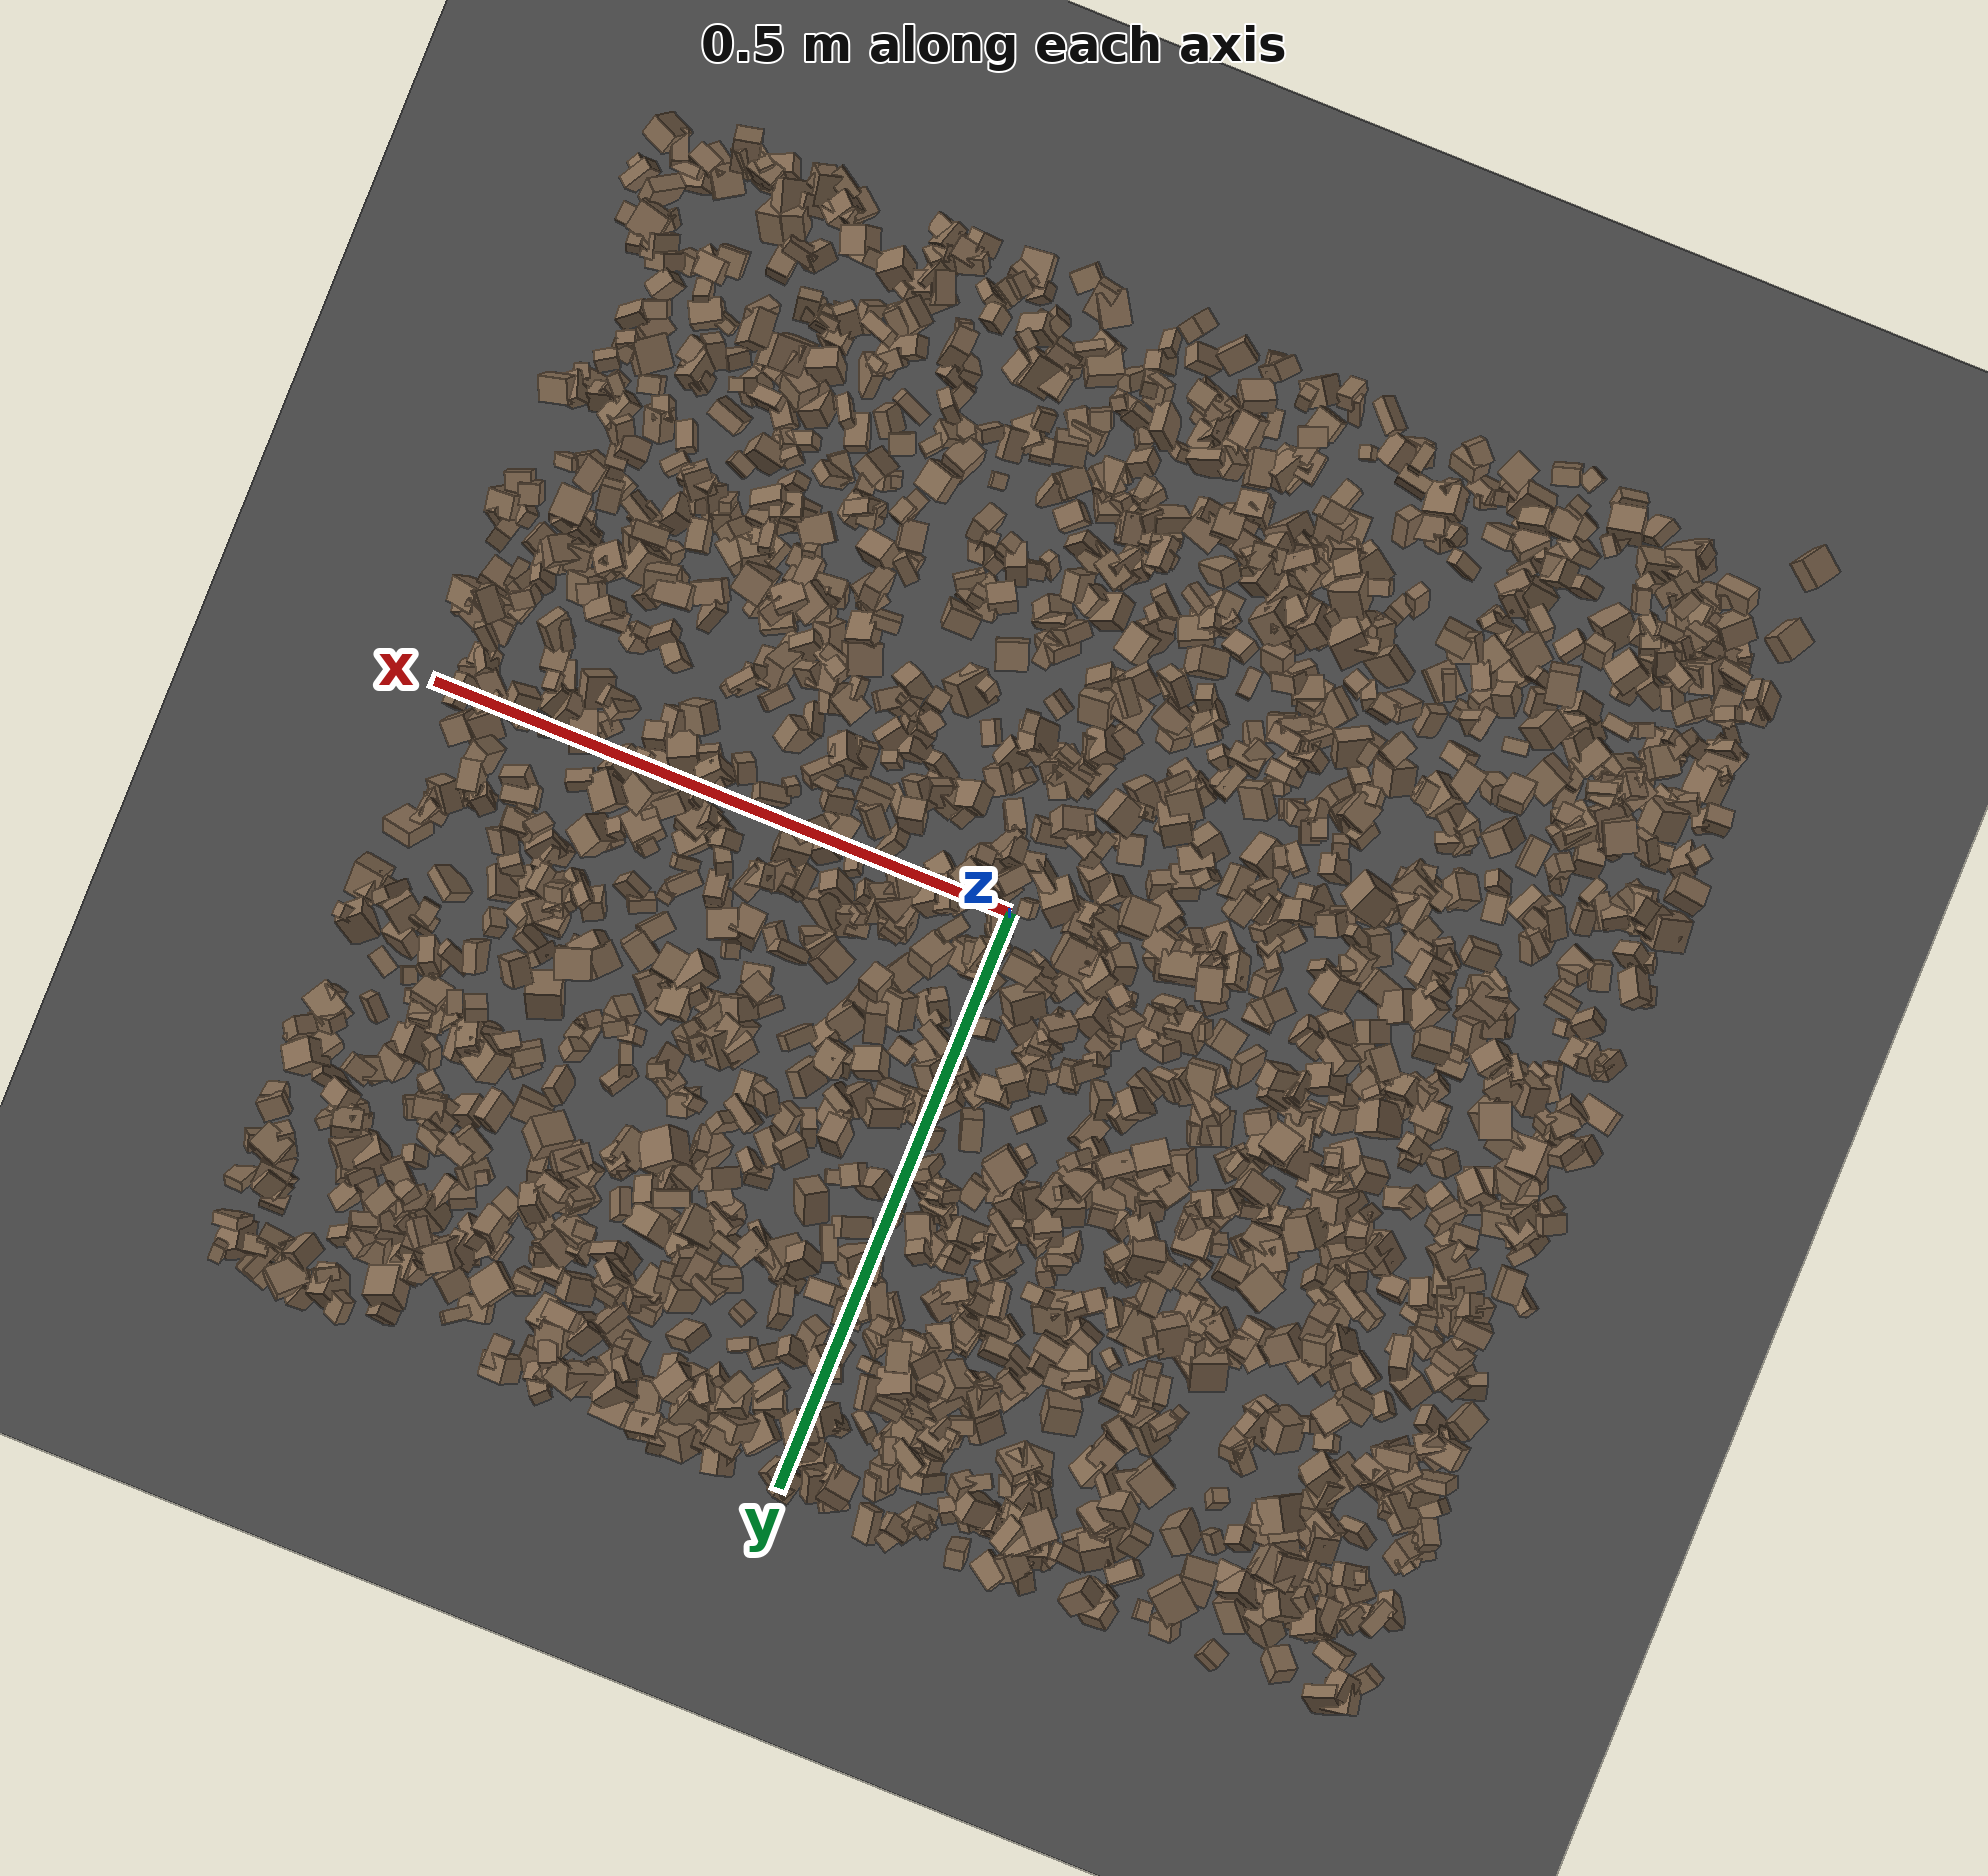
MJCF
<mujoco model="rocky_terrain_scene">
    <compiler angle="radian" inertiafromgeom="true" />
    <option timestep="0.002" gravity="0 0 -9.81" />

    <worldbody>
        <light name="sunlight" pos="5 5 5" dir="-1 -1 -1" diffuse="1 1 1" specular="0.5 0.5 0.5" ambient="0.5 0.5 0.5" />

        <geom name="ground_plane" type="plane" size="50 50 0.1" rgba="0.3 0.3 0.3 1" />

        <body name="rocky_terrain_body">

        <geom name="rock1" type="box" size="0.009668672092094911 0.013092463526174318 0.012512888635914208" pos="-0.2821254104342542 0.2705674117706356 0.005213228172696559" quat="0.17785462422024495 0.1023134346943195 0.3748036228203565 0.345028318265079" rgba="0.5 0.4 0.3 1" friction="0.7576398449810002 0.91939893624553 0.8552929983154995" /><geom name="rock2" type="box" size="0.006965398026120373 0.012225823270900167 0.005817823228823038" pos="-0.13434843397503182 0.27610384339332905 0.014221576528906625" quat="0.3329383395802566 0.18568042121732664 0.14959360752553766 0.3317876316768791" rgba="0.5 0.4 0.3 1" friction="0.7246891006778053 0.9784165939971516 0.8667913499927857" /><geom name="rock3" type="box" size="0.009071345116617481 0.006329617548852858 0.009863638935919569" pos="0.0658608944769985 -0.012989750614330497 0.013143021481332895" quat="0.0269480584691213 0.23146874297345918 0.38255188663326034 0.3590313119241592" rgba="0.5 0.4 0.3 1" friction="0.746821460475031 0.9784041792884707 0.8740147750142319" /><geom name="rock4" type="box" size="0.014979299382757962 0.01295058652221107 0.010560309690342419" pos="-0.14165745152081977 -0.010667760186629516 0.010698172906256902" quat="0.4008131449282918 0.4997767259613007 0.08226574746402118 0.017144381646386497" rgba="0.5 0.4 0.3 1" friction="0.7388893298127953 0.9527307514220642 0.8311381394410767" /><geom name="rock5" type="box" size="0.010528811939271873 0.01438355746802377 0.010325664116045553" pos="-0.34370306842904375 -0.20526165035716093 0.00877783539693743" quat="0.13386689682129968 0.1697440474834114 0.46869667065760384 0.22769238503768507" rgba="0.5 0.4 0.3 1" friction="0.7953207498743718 0.9776396033263888 0.8905803808501103" /><geom name="rock6" type="box" size="0.007058320198123547 0.011178155715721862 0.014414567140140173" pos="0.26052251546038485 -0.40717626851949407 0.0071603701360468345" quat="0.42857310424943096 0.2776685644340231 0.17059051843487563 0.12316781288167032" rgba="0.5 0.4 0.3 1" friction="0.7113116175463255 0.9043022141101462 0.8387055372235727" /><geom name="rock7" type="box" size="0.012119080778951345 0.011857423878959786 0.006655835500196607" pos="-0.4933249455426967 0.40563856804954546 0.0031900885867543237" quat="0.04860943417721188 0.3389471826414847 0.3201468738596857 0.2922965093216177" rgba="0.5 0.4 0.3 1" friction="0.7557483289555752 0.966701491586698 0.8442473304448385" /><geom name="rock8" type="box" size="0.009537952411995686 0.007417325103329809 0.01085007980874542" pos="-0.33815567482036546 -0.08016397483839144 0.007125551099759044" quat="0.31245983815243744 0.16013063455484317 0.2733756027259757 0.25403392456674384" rgba="0.5 0.4 0.3 1" friction="0.7781139478284201 0.9392234160228882 0.8507757451755654" /><geom name="rock9" type="box" size="0.008727475567939244 0.007415808713897148 0.007490726994260467" pos="-0.027175048515636013 0.14600995111465376 0.008899306154573168" quat="0.06720953205280344 0.1359293964418307 0.3746172496851754 0.4222438218201905" rgba="0.5 0.4 0.3 1" friction="0.7776334095124583 0.9862512677098684 0.8431935961571364" /><geom name="rock10" type="box" size="0.010196098014871431 0.009654945810815132 0.013998663317607154" pos="-0.498330530525281 -0.21870159317455107 0.003686496093888516" quat="0.21216359884391534 0.30682596411929497 0.1499584686381333 0.3310519683986563" rgba="0.5 0.4 0.3 1" friction="0.789866169973161 0.9471660794905603 0.8153404287270519" /><geom name="rock11" type="box" size="0.012722123047387941 0.013836427110313309 0.010205963237917622" pos="-0.4661009908886554 0.2095476227973313 0.0053065502349806965" quat="0.3204305962853754 0.341866407244447 0.32380172353360576 0.01390127293657186" rgba="0.5 0.4 0.3 1" friction="0.733711659700758 0.9301867757305743 0.8922890075644108" /><geom name="rock12" type="box" size="0.008975289696762987 0.01444532141518362 0.010518187799513846" pos="-0.15814425483001804 0.19133122021060556 0.005416034633008537" quat="0.3197898471891165 0.14947739315000075 0.33917486976310407 0.19155788989777867" rgba="0.5 0.4 0.3 1" friction="0.7467706424060848 0.9087934863073917 0.8180605300537599" /><geom name="rock13" type="box" size="0.007627770348630894 0.005790450192893005 0.014354144655359825" pos="-0.4497159448157724 0.13806458160626356 0.009666082419483593" quat="0.2491554466860571 0.11014866596349254 0.32915600398308986 0.31153988336736044" rgba="0.5 0.4 0.3 1" friction="0.7585257935867701 0.9114990363591974 0.8615466562322184" /><geom name="rock14" type="box" size="0.007529515440482762 0.012119687781351298 0.01123250130237603" pos="-0.12387334567288888 0.3777568037284105 0.004786309774345849" quat="0.1493459870136447 0.2531007059089054 0.5545290934232768 0.04302421365417321" rgba="0.5 0.4 0.3 1" friction="0.7752881240103591 0.934922778405647 0.8558338679020342" /><geom name="rock15" type="box" size="0.008050365045618764 0.014102895340418652 0.008323775044616784" pos="0.11201020907954129 -0.268781482647355 0.0006338249370177729" quat="0.08936016462708257 0.061972725278658616 0.28290193266609137 0.5657651774281675" rgba="0.5 0.4 0.3 1" friction="0.7679001576487797 0.9040774106680359 0.8313988037037391" /><geom name="rock16" type="box" size="0.005353583606131308 0.012996654333323157 0.007993660071255435" pos="-0.2085447601917534 -0.35582192195399265 0.008354744876956692" quat="0.023972189099411165 0.17977238237620097 0.308801137526738 0.48745429099764986" rgba="0.5 0.4 0.3 1" friction="0.7485370615118154 0.9375061892245178 0.8303877232499854" /><geom name="rock17" type="box" size="0.009460969177860648 0.009395729550515486 0.007613181464713016" pos="-0.4484632677642304 0.3917925596274322 0.014817293036891391" quat="0.0662849757496593 0.36298467960819764 0.41659466191315064 0.15413568272899256" rgba="0.5 0.4 0.3 1" friction="0.7043274244190328 0.9438698048044004 0.8128484520328974" /><geom name="rock18" type="box" size="0.007504639311871487 0.009968631584956377 0.009437976242880848" pos="-0.3588304061148234 -0.37234958334698043 0.009365446430103331" quat="0.1669469846324417 0.4067764108678639 0.1738100836421902 0.2524665208575044" rgba="0.5 0.4 0.3 1" friction="0.7095739156257558 0.9152370843445593 0.8483453398146279" /><geom name="rock19" type="box" size="0.009058326470228018 0.01169617825092639 0.009512924104426536" pos="0.32229977332287796 0.355205170509443 0.005090960964792301" quat="0.0774362933114844 0.24538942098126593 0.5688545466049437 0.1083197391023059" rgba="0.5 0.4 0.3 1" friction="0.7379693866742595 0.977081554931494 0.8717475995430088" /><geom name="rock20" type="box" size="0.012442552530366788 0.01201556141544003 0.0051619363076692935" pos="0.35790191741396027 0.1173906060452854 0.010531506524497119" quat="0.15058966663185233 0.3549336554439488 0.2721398221979961 0.22233685572620276" rgba="0.5 0.4 0.3 1" friction="0.7004515085039469 0.94691867718273 0.8240112000814751" /><geom name="rock21" type="box" size="0.009721702319244931 0.00915846767229676 0.014275601847118374" pos="-0.025286070774993896 0.03670821534313495 0.014996442243269896" quat="0.2981572531548497 0.2260607822639797 0.2833984959336296 0.19238346864754086" rgba="0.5 0.4 0.3 1" friction="0.7603153377089585 0.9566285101335339 0.8437297652221188" /><geom name="rock22" type="box" size="0.009925021072056967 0.007493003806198542 0.008589635342555819" pos="0.38603926741820127 0.4389069924597473 0.014817548718296238" quat="0.33736940603016075 0.2743640920351911 0.344562364191789 0.04370413774285918" rgba="0.5 0.4 0.3 1" friction="0.7674051797397928 0.9125295970889806 0.8035859895316855" /><geom name="rock23" type="box" size="0.011985478596796502 0.006661599872440874 0.011128183513472964" pos="0.3049092155451124 -0.32499288020998496 0.002991049885489283" quat="0.20533972586464785 0.3096623244625073 0.15158164804355928 0.33341630162928565" rgba="0.5 0.4 0.3 1" friction="0.7492953206298524 0.9809217028432089 0.8577635343566399" /><geom name="rock24" type="box" size="0.009235091379863862 0.011579315149877124 0.008540182355103966" pos="-0.18444213919284302 -0.11252309935515614 0.0012512499615377987" quat="0.036327404256897594 0.009313280347585565 0.5780883585379598 0.37627095685755707" rgba="0.5 0.4 0.3 1" friction="0.7911371674004839 0.9179452207135355 0.8880744706466313" /><geom name="rock25" type="box" size="0.014660323703672273 0.009363592811629906 0.009438778336560438" pos="0.21173297897585897 0.2165506138010812 0.00801904237905153" quat="0.16562193721502547 0.3649190571082178 0.07660767113335244 0.3928513345434043" rgba="0.5 0.4 0.3 1" friction="0.7749867422258266 0.9772332421337835 0.8871910567132828" /><geom name="rock26" type="box" size="0.013081120543335888 0.008240027341629307 0.012433870682503997" pos="0.41658620901123666 -0.11640857832892515 0.006409309041310017" quat="0.21635713721648125 0.24638472828026525 0.4232380681266239 0.11402006637662968" rgba="0.5 0.4 0.3 1" friction="0.7061194865643396 0.9924758978112187 0.8206444986599746" /><geom name="rock27" type="box" size="0.01303500487940843 0.005212705822561836 0.009892298923389234" pos="-0.18112405054261516 0.49565807151697217 0.01059392470299658" quat="0.040945541576944466 0.17631442396129568 0.40723211975343604 0.37550791470832384" rgba="0.5 0.4 0.3 1" friction="0.7029968381426059 0.9281985192741654 0.8084215035222908" /><geom name="rock28" type="box" size="0.009757694415886333 0.012667816845289882 0.008843444321159038" pos="-0.14969066392488573 -0.46074497355742816 0.0044102653783837185" quat="0.09881383065996559 0.2801165503527831 0.027183942324409387 0.593885676662842" rgba="0.5 0.4 0.3 1" friction="0.7526654407030066 0.9925335318205436 0.8264902789268774" /><geom name="rock29" type="box" size="0.01422112311038205 0.011470298302865344 0.009987115594702459" pos="0.13248005902376536 0.38322572072671957 0.004935258166046936" quat="0.11926402757180642 0.6001946859823716 0.030601866028884064 0.2499394204169381" rgba="0.5 0.4 0.3 1" friction="0.7225131608977651 0.9581769081896224 0.8719692047464155" /><geom name="rock30" type="box" size="0.007735361928919132 0.013748074000349712 0.011234866195688708" pos="0.26177494210088204 -0.14772518466290563 0.008378557992677673" quat="0.3541909604103302 0.05805447250395191 0.000531145073843462 0.5872234220118744" rgba="0.5 0.4 0.3 1" friction="0.7822124694331957 0.9536805937435481 0.8435321799810089" /><geom name="rock31" type="box" size="0.008955387294841575 0.007985633645858418 0.007994127596885635" pos="-0.060548793074307494 0.09067925674571964 0.013944991738359006" quat="0.16439849153028996 0.3535536147552956 0.1465061913012111 0.33554170241320325" rgba="0.5 0.4 0.3 1" friction="0.7710572164744108 0.9095715749247099 0.8857386721328377" /><geom name="rock32" type="box" size="0.010789405552931923 0.007638993476136654 0.013007171108546274" pos="-0.4431220818513991 0.15503083709498033 0.004900415766854412" quat="0.48166520243631683 0.339714987604926 0.08792171363183718 0.09069809632691986" rgba="0.5 0.4 0.3 1" friction="0.7068127383409656 0.925327427176353 0.8705739679228066" /><geom name="rock33" type="box" size="0.006239129374785011 0.005651854444426187 0.008879229533693331" pos="0.0652115561742117 -0.05993055492010935 0.010235300498877267" quat="0.14096685239588078 0.018861287462838692 0.5458614435282522 0.2943104166130284" rgba="0.5 0.4 0.3 1" friction="0.7489970615567323 0.9590129491481828 0.8309045247245698" /><geom name="rock34" type="box" size="0.010424406284025786 0.009981908886748287 0.013259249172030075" pos="-0.19514700569668741 0.4860973519988976 0.013682812181408722" quat="0.0675332743376928 0.23964787962917147 0.5416653254042297 0.151153520628906" rgba="0.5 0.4 0.3 1" friction="0.7210432490445495 0.972020318339128 0.8834123083486645" /><geom name="rock35" type="box" size="0.01342525808333505 0.007031799151920819 0.009186491812311853" pos="0.30883429657525174 -0.04036861282679949 0.0056285557612563335" quat="0.1719727165942577 0.3185157482185985 0.38586602209145837 0.1236455130956854" rgba="0.5 0.4 0.3 1" friction="0.7675341476259613 0.9174454349417944 0.8119976597964972" /><geom name="rock36" type="box" size="0.01466861409441543 0.007421813498117732 0.00799919145538341" pos="-0.26461388463270896 0.27899303719131896 0.009208290718877939" quat="0.10907258161982909 0.132634954218951 0.3458679443070893 0.41242451985413053" rgba="0.5 0.4 0.3 1" friction="0.7885142250593363 0.9106257358030612 0.8324009733794525" /><geom name="rock37" type="box" size="0.007287654754457656 0.01477602656768634 0.0075446496561270195" pos="0.38414805142748654 -0.1730992728619697 0.011816016459243201" quat="0.015870252315842555 0.4148234265793283 0.45351270888221196 0.11579361222261732" rgba="0.5 0.4 0.3 1" friction="0.7025257458278761 0.9317389340604896 0.8644299282351354" /><geom name="rock38" type="box" size="0.014288861349137243 0.012975274805059143 0.007586873771714388" pos="0.17541232134439178 -0.48920676800966867 0.0025012133056305564" quat="0.4325293485564028 0.05193024467132682 0.05041068187824465 0.46512972489402576" rgba="0.5 0.4 0.3 1" friction="0.7978680451957405 0.919339673539636 0.8665684895441121" /><geom name="rock39" type="box" size="0.010032078016702903 0.009760736069232242 0.01196696210312435" pos="-0.17645589792663763 0.29668442787090044 0.00144806219069182" quat="0.18757304616762807 0.009603904987615895 0.5147196926136544 0.2881033562311018" rgba="0.5 0.4 0.3 1" friction="0.7869116972633512 0.9733622016187393 0.8290197778806443" /><geom name="rock40" type="box" size="0.008780152474241631 0.006520513312752577 0.009083696248234241" pos="0.2635764840570872 -0.20254692247420403 0.0059355990731010735" quat="0.2743601033529325 0.2428858182843871 0.2810719732193694 0.20168210514331103" rgba="0.5 0.4 0.3 1" friction="0.7649640579276702 0.9813549444961877 0.8434610991520086" /><geom name="rock41" type="box" size="0.007736502605853809 0.005823944401806237 0.00992970111826607" pos="-0.010399220078540439 -0.423870041200927 0.002012977043711586" quat="0.28094747465614106 0.03191214631022976 0.5335793319597483 0.15356104707388085" rgba="0.5 0.4 0.3 1" friction="0.7438327555195622 0.9830034704909032 0.8429880345374848" /><geom name="rock42" type="box" size="0.013132911755787482 0.008524519319286298 0.007838770120473277" pos="-0.10702607164476607 0.486562415376796 0.006704685348373617" quat="0.3947609250868688 0.2550812942352387 0.1489761443858755 0.20118163629201696" rgba="0.5 0.4 0.3 1" friction="0.7275143949517967 0.9998496124439868 0.8340857824533054" /><geom name="rock43" type="box" size="0.012491438041770171 0.010367715438957113 0.008884846332208794" pos="0.40609835120087745 -0.47874351385860403 0.011028211657875516" quat="0.05342457086702628 0.07068188567523039 0.39576548815938883 0.48012805529835456" rgba="0.5 0.4 0.3 1" friction="0.7893291555937255 0.914469804260922 0.8541932457743928" /><geom name="rock44" type="box" size="0.008224188199142397 0.006409657314495383 0.013582187764941297" pos="-0.2611809409134198 0.2511487941460717 0.003700373603382661" quat="0.32841080843610054 0.031260502765597706 0.42758165822957644 0.21274703056872524" rgba="0.5 0.4 0.3 1" friction="0.7707750944451185 0.9844667939260843 0.834792345990209" /><geom name="rock45" type="box" size="0.00595125896432988 0.0068576183340990984 0.009569272199078641" pos="-0.40438840088614825 -0.27753823991719695 0.01096472999154732" quat="0.37849671978956834 0.2458416287971693 0.18212796722636557 0.19353368418689673" rgba="0.5 0.4 0.3 1" friction="0.7147250570756566 0.9900739890460766 0.8960144606440703" /><geom name="rock46" type="box" size="0.00787391704210615 0.014284243301723693 0.010835844016976336" pos="-0.06642297059892133 0.3598261311444212 0.010729767773163387" quat="0.22511137018857721 0.06054864561889133 0.3388324774341016 0.37550750675842987" rgba="0.5 0.4 0.3 1" friction="0.7751124561040835 0.9007924599935964 0.8795347606890844" /><geom name="rock47" type="box" size="0.01249179008806879 0.009015480511460387 0.007842884958994252" pos="-0.19006307257125754 0.2268386545413863 0.005754458892885085" quat="0.3700161253579752 0.23038683382282985 0.04356752745949757 0.35602951335969746" rgba="0.5 0.4 0.3 1" friction="0.7877075198664895 0.9464624698303736 0.8019836032190062" /><geom name="rock48" type="box" size="0.005385360090063881 0.009380635981386179 0.007225256171175542" pos="-0.02354622411048346 0.433741675534284 0.004656619344681918" quat="0.2817118105385895 0.3972479603047037 0.2824239338375406 0.038616295319166126" rgba="0.5 0.4 0.3 1" friction="0.7071934174933915 0.9938913335370535 0.8417695186798744" /><geom name="rock49" type="box" size="0.014548435517913832 0.008179563952799545 0.008915528452075303" pos="-0.37668032267156937 0.034799944459065535 0.0006220692286835638" quat="0.3876633765132532 0.04491982199932848 0.28250124379521196 0.2849155576922064" rgba="0.5 0.4 0.3 1" friction="0.7544952446316494 0.9785817542612762 0.8038916558558036" /><geom name="rock50" type="box" size="0.005475120122341604 0.007087254893918896 0.006518068332887777" pos="0.1198288500867013 -0.4241692671596601 0.008187375248706615" quat="0.38086747444649494 0.04722113013644366 0.24927578597929156 0.3226356094377698" rgba="0.5 0.4 0.3 1" friction="0.7832476904230352 0.9085076948988747 0.8642781560465376" /><geom name="rock51" type="box" size="0.00573995252883642 0.012453563068960474 0.005973577966151422" pos="0.35930084574267784 -0.31362910749099027 0.01105441979541068" quat="0.28049506864722507 0.12264787845524364 0.2233404948879479 0.37351655800958333" rgba="0.5 0.4 0.3 1" friction="0.759672166708799 0.9329717686717226 0.878238781414037" /><geom name="rock52" type="box" size="0.014897738832596277 0.008166787103761293 0.014385863364886255" pos="-0.3267141251586514 0.4630832803545877 0.013273808050930468" quat="0.19072924370767344 0.07650871585111926 0.3853227287800339 0.3474393116611734" rgba="0.5 0.4 0.3 1" friction="0.7204920886694903 0.9690938323793878 0.8017472497409843" /><geom name="rock53" type="box" size="0.013400402638945184 0.011796260563323106 0.008984300790367997" pos="-0.483230088438349 0.12720272898754714 0.006839120745356045" quat="0.2601012833274288 0.2271041096141272 0.2446749338248116 0.2681196732336324" rgba="0.5 0.4 0.3 1" friction="0.7123668771589248 0.9809433189823544 0.8360964773114553" /><geom name="rock54" type="box" size="0.013991318422205652 0.014104838031289254 0.005926046878457503" pos="-0.0037200357617256374 -0.42111188000884325 0.007719632285179022" quat="0.5076806032121172 0.12087301016481981 0.3032897278881951 0.06815665873486809" rgba="0.5 0.4 0.3 1" friction="0.7857608999441787 0.9966737600764549 0.8202687965878797" /><geom name="rock55" type="box" size="0.012339288718199955 0.011305588607243709 0.006044088349314794" pos="-0.15343864384922334 -0.22168209352402846 0.009283571988004927" quat="0.32056845030536196 0.47471438560483875 0.06249720354970802 0.14221996054009128" rgba="0.5 0.4 0.3 1" friction="0.739582040552741 0.9097455143550444 0.8745665167965976" /><geom name="rock56" type="box" size="0.01079100105385467 0.007050857526958434 0.014444532918874448" pos="0.49595468022251255 -0.2556109920453624 0.0103994987061732" quat="0.20861658129024793 0.2150352422910941 0.41161282244371555 0.16473535397494243" rgba="0.5 0.4 0.3 1" friction="0.7999566399973018 0.9194381609393003 0.8857722572551596" /><geom name="rock57" type="box" size="0.005399627127478233 0.005978814254705128 0.01149358276340404" pos="-0.0442891680652604 -0.2908066115505584 0.013347427008182965" quat="0.22286463101825912 0.44806750611847834 0.05549194926369124 0.27357591359957134" rgba="0.5 0.4 0.3 1" friction="0.7554684343659567 0.9960347431421805 0.8988082037781783" /><geom name="rock58" type="box" size="0.013454733616004032 0.006923787626566863 0.006054037645945544" pos="-0.1579574740213009 0.027408466536304577 0.008159592056164486" quat="0.2675767179060638 0.42924921236127456 0.001848672072101978 0.3013253976605596" rgba="0.5 0.4 0.3 1" friction="0.7889438472662554 0.997670703514721 0.8832758977359683" /><geom name="rock59" type="box" size="0.010800731094692569 0.0109697113468705 0.00668019949190035" pos="0.37919043956797904 0.08005463722065109 0.010064083754526389" quat="0.35230285145602586 0.24043484459254916 0.4004046061203172 0.006857697831107694" rgba="0.5 0.4 0.3 1" friction="0.7443538793572313 0.9947621886361677 0.8197172555081286" /><geom name="rock60" type="box" size="0.012176152130268581 0.013311509911067852 0.005862113000420227" pos="0.11007761392471338 -0.018583361654202046 0.001659640288635772" quat="0.2234419066414201 0.3153302505948554 0.0626607036663111 0.39856713909741326" rgba="0.5 0.4 0.3 1" friction="0.7184880580652007 0.9981187620846105 0.8865587246236928" /><geom name="rock61" type="box" size="0.005206622694364587 0.012401217408446625 0.005489739145037458" pos="-0.11429492241731554 0.06399063544682115 0.00693051965486585" quat="0.4571085642965698 0.4034828579814628 0.05011211416090875 0.08929646356105866" rgba="0.5 0.4 0.3 1" friction="0.7696427048911318 0.9294370677517837 0.8832154359132541" /><geom name="rock62" type="box" size="0.012886295401100107 0.009668758878695394 0.01228869313663419" pos="0.1543572665436157 0.45653457117984453 0.007992026973709763" quat="0.3609931221040246 0.35893868721916017 0.258985588636977 0.02108260203983829" rgba="0.5 0.4 0.3 1" friction="0.7904473234968219 0.9440553128742477 0.8317321217485366" /><geom name="rock63" type="box" size="0.014807030012238442 0.01204065726925293 0.014692427738365751" pos="-0.2127099754789472 0.09858990852374083 5.163670240406925e-05" quat="0.2679233061526742 0.17018521481124163 0.2130195940389125 0.3488718849971717" rgba="0.5 0.4 0.3 1" friction="0.7701417766768264 0.9573901536048134 0.8478583350457725" /><geom name="rock64" type="box" size="0.012640273704375765 0.00741979218851308 0.009241868674244208" pos="-0.025264747729558557 0.4840692407385657 0.009436517068811946" quat="0.3125744492754562 0.09473431190446216 0.2744872034592954 0.31820403536078634" rgba="0.5 0.4 0.3 1" friction="0.7472603558355103 0.9519085465467421 0.8448015708760275" /><geom name="rock65" type="box" size="0.010137499115996177 0.012067769708185523 0.010109652312616823" pos="0.24902314560339822 -0.46649194364971225 0.0006646473055480245" quat="0.292743861714795 0.01868995967872813 0.38819029364855184 0.30037588495792494" rgba="0.5 0.4 0.3 1" friction="0.7470689979360362 0.9720917819682537 0.8650779754035678" /><geom name="rock66" type="box" size="0.014934173178639376 0.00848107556333397 0.008555221551189549" pos="0.3672210413717879 0.3214790047484899 0.006986103259783252" quat="0.3176811085047095 0.23845834666197338 0.15862126671337443 0.28523927811994265" rgba="0.5 0.4 0.3 1" friction="0.7005018687406541 0.9587748490756279 0.8327348333808973" /><geom name="rock67" type="box" size="0.011284127863315594 0.010578773173535078 0.012870278105909311" pos="0.3427114947711474 0.428136816040941 0.004605538843193935" quat="0.3846280227889958 0.13110586056658236 0.3466785396465368 0.13758757699788512" rgba="0.5 0.4 0.3 1" friction="0.7291900325000314 0.9792762210761625 0.8954696751586037" /><geom name="rock68" type="box" size="0.013989169257648006 0.007672896957908621 0.009691740532717135" pos="-0.27444693506952544 -0.4324628315729956 0.012960567498771842" quat="0.25533640865514706 0.4366998136516888 0.15894580724532453 0.1490179704478396" rgba="0.5 0.4 0.3 1" friction="0.7678883586946907 0.9449813945480846 0.8427735766652922" /><geom name="rock69" type="box" size="0.012472887315395196 0.005801374899968641 0.014546330625824576" pos="-0.4389862491797003 0.022323617139146545 0.008498728839821074" quat="0.33716252449003575 0.19728999105779352 0.37795107820174373 0.0875964062504271" rgba="0.5 0.4 0.3 1" friction="0.7104656037277647 0.9905893701570219 0.8678329012020333" /><geom name="rock70" type="box" size="0.013256571709594902 0.01497017644578262 0.011816429508512465" pos="0.09444768828822214 0.03071038013933791 0.00258598539106098" quat="0.2735602442407752 0.3165650476364218 0.12010538324455368 0.2897693248782494" rgba="0.5 0.4 0.3 1" friction="0.7509604969951181 0.9009977919250547 0.8983163921327194" /><geom name="rock71" type="box" size="0.009735988236243831 0.01124098257132427 0.009501247818958168" pos="0.014905097714360327 -0.020622486981817345 0.00242606032339916" quat="0.47313320200886566 0.18238564036231303 0.05327877818692823 0.2912023794418929" rgba="0.5 0.4 0.3 1" friction="0.7317041627859121 0.929036765492941 0.8146589929051975" /><geom name="rock72" type="box" size="0.01449474498273532 0.01144782268673665 0.010099290222194728" pos="0.4560328838769754 0.4906127746512672 0.00023740914804181888" quat="0.1049184609316751 0.036889998256856356 0.43240024001719807 0.42579130079427047" rgba="0.5 0.4 0.3 1" friction="0.7288242730407276 0.929796922697615 0.8664370483418774" /><geom name="rock73" type="box" size="0.01293906661415925 0.006139913519454414 0.010554735214151494" pos="-0.42859525548417665 -0.38470207149170277 0.0044593674318836925" quat="0.28716283419836724 0.0729973772710917 0.3671719917897892 0.27266779674075176" rgba="0.5 0.4 0.3 1" friction="0.749793401154343 0.9060188777591192 0.8768236839506918" /><geom name="rock74" type="box" size="0.006709606344253261 0.008757787579967152 0.014852269250845082" pos="-0.41195414391291185 -0.28307863106822995 0.011227149233114455" quat="0.28201316682552025 0.15266521558189897 0.3322182443714465 0.23310337322113428" rgba="0.5 0.4 0.3 1" friction="0.7730595691692426 0.9144748499366754 0.8984162054647231" /><geom name="rock75" type="box" size="0.012733892019516503 0.009768026767150937 0.007249800282109421" pos="0.12994930463257381 -0.028941105792086197 0.010411593815785951" quat="0.22582410436722225 0.07655488226207113 0.3322796293175361 0.3653413840531704" rgba="0.5 0.4 0.3 1" friction="0.7177880812025058 0.9258880830284822 0.8626042748461412" /><geom name="rock76" type="box" size="0.014492105867917271 0.008734126548778507 0.014576463389672424" pos="0.48182453906678335 0.4756591359245915 0.0026538921076666817" quat="0.041525639729894155 0.3452928686832738 0.370514520451538 0.2426669711352941" rgba="0.5 0.4 0.3 1" friction="0.7776114629189692 0.9467831366817634 0.895364237737187" /><geom name="rock77" type="box" size="0.014147434686515803 0.011664095216382933 0.0129652329410429" pos="-0.32745885033252975 0.11863942907538294 0.011710077851762186" quat="0.044160148609814716 0.5561505734186297 0.12086915728937628 0.27882012068217943" rgba="0.5 0.4 0.3 1" friction="0.7682290251718273 0.9042940122979535 0.8482648988511757" /><geom name="rock78" type="box" size="0.008300748295520907 0.006979635219584437 0.01152671686174782" pos="-0.4276101038544835 0.07369918199600645 0.010459756457729022" quat="0.5033666793417128 0.28682675828762344 0.13395590998721071 0.07585065238345313" rgba="0.5 0.4 0.3 1" friction="0.71652429922911 0.9687598162375815 0.8270959235008833" /><geom name="rock79" type="box" size="0.007183233410118503 0.011911551029682247 0.009411135276213903" pos="-0.41003688900202184 -0.03646527478713335 0.005461003874742532" quat="0.008675538922608547 0.21514089936670122 0.4089825858935373 0.36720097581715294" rgba="0.5 0.4 0.3 1" friction="0.7672965851067829 0.9290009330755431 0.8171861253307762" /><geom name="rock80" type="box" size="0.012375290441499546 0.009106984354409896 0.009925219269569116" pos="0.2202292069514057 -0.15315932163473045 0.003290863534130942" quat="0.3589302077688117 0.01047559717595001 0.22045690846560761 0.4101372865896308" rgba="0.5 0.4 0.3 1" friction="0.781345963416183 0.992235947937456 0.8833820382726637" /><geom name="rock81" type="box" size="0.007517734667972467 0.00517153759134449 0.009274602067260464" pos="-0.21473068959259478 -0.41475204230570395 0.011768855577750323" quat="0.10703396656418585 0.450290654294361 0.30683041882618267 0.13584496031527046" rgba="0.5 0.4 0.3 1" friction="0.7311578710370095 0.927833473175036 0.8762086672989525" /><geom name="rock82" type="box" size="0.012192361548166074 0.009921066518063296 0.010511298156472774" pos="0.17206624863265518 -0.0710334639714093 0.0038662024989950545" quat="0.1669094519429518 0.31533568421332087 0.21706701260018635 0.300687851243541" rgba="0.5 0.4 0.3 1" friction="0.7672060550770562 0.9213372902838934 0.89894886591967" /><geom name="rock83" type="box" size="0.011279342339888799 0.010385929698217368 0.01171647919481499" pos="0.11931925878759053 0.08924698076026549 0.012724891205888825" quat="0.28029843711006586 0.3265282560209121 0.1062928060436104 0.28688050082541167" rgba="0.5 0.4 0.3 1" friction="0.7315500478845557 0.9740144602852565 0.8365880955839177" /><geom name="rock84" type="box" size="0.006717271185073443 0.00921788356763538 0.010505478533045794" pos="-0.06838037289909082 -0.18060174756609193 0.009237641219755472" quat="0.3943771865843287 0.009877410709798256 0.25466644113161974 0.34107896157425344" rgba="0.5 0.4 0.3 1" friction="0.7085287846712005 0.9327958758044276 0.8711119610638218" /><geom name="rock85" type="box" size="0.0094679739455072 0.013809025446539485 0.014149652494042844" pos="-0.47359800184956025 0.010241778214769015 0.0009148065094076973" quat="0.2334838417038403 0.28468842152700796 0.09640353044378015 0.3854242063253714" rgba="0.5 0.4 0.3 1" friction="0.7836574182560341 0.919604757373483 0.8586691365113056" /><geom name="rock86" type="box" size="0.012933254512864176 0.012918769018132669 0.008074270764266754" pos="-0.3943358808613934 -0.3939337053860512 0.007717892564882548" quat="0.3714748299738391 0.02506124902168591 0.437189654538287 0.16627426646618806" rgba="0.5 0.4 0.3 1" friction="0.7629989151849084 0.93161215702175 0.855523842035382" /><geom name="rock87" type="box" size="0.01050058264940119 0.014012774693770626 0.012959329662877283" pos="-0.07035349138836167 -0.24612111489824295 0.006413415447662863" quat="0.2550177869710915 0.1998631760311516 0.19978666802912637 0.3453323689686304" rgba="0.5 0.4 0.3 1" friction="0.7536581249832089 0.9036945934993921 0.889465355780233" /><geom name="rock88" type="box" size="0.005599663045221457 0.013324948014769425 0.007188366825085092" pos="0.2433483009098355 0.24009378952581284 0.006582926525274531" quat="0.265496305704312 0.18775006407239855 0.5387241247727398 0.008029505450549743" rgba="0.5 0.4 0.3 1" friction="0.7061269408275598 0.9604863312224603 0.8076057616394258" /><geom name="rock89" type="box" size="0.00915106962299838 0.0053431412379798815 0.011656885458012418" pos="-0.09039278104402682 -0.26765301207951164 0.014945872561709548" quat="0.15755214772512466 0.42902068740914706 0.25730247436844705 0.1561246904972813" rgba="0.5 0.4 0.3 1" friction="0.7692065827061334 0.9824090135526938 0.899600157628167" /><geom name="rock90" type="box" size="0.010331112272519687 0.00810881817193612 0.006233325957853162" pos="0.31860571210376176 -0.38637802863846216 0.011098650650056144" quat="0.49308588941727455 0.09154195333361256 0.39012884554023247 0.02524331170888037" rgba="0.5 0.4 0.3 1" friction="0.716511556676551 0.9355302799137281 0.8488856423674934" /><geom name="rock91" type="box" size="0.011351317214965947 0.01195762853707213 0.010137753149087027" pos="-0.1258663090648544 -0.11043159912279854 0.0033822706076465496" quat="0.14682852469473084 0.4915883336388222 0.2333706599005345 0.12821248176591243" rgba="0.5 0.4 0.3 1" friction="0.7607862281699622 0.9608252887674625 0.8074271121781045" /><geom name="rock92" type="box" size="0.01120297413417589 0.01426526527903614 0.012327873336790177" pos="0.214249639716094 0.451484927264301 0.008649268047689855" quat="0.04050305855847493 0.4769855485358549 0.11198494961522956 0.37052644329044065" rgba="0.5 0.4 0.3 1" friction="0.7690913486759261 0.9475619169076229 0.8999261154064151" /><geom name="rock93" type="box" size="0.012058633252646181 0.006867479331636776 0.013546879315921554" pos="0.26014227008801216 -0.2273451175087513 0.012114219793603536" quat="0.17388618485763932 0.17164908026729583 0.3525166984116486 0.30194803646341617" rgba="0.5 0.4 0.3 1" friction="0.7346594937271843 0.9462756099639489 0.8420433676482407" /><geom name="rock94" type="box" size="0.014455378408713398 0.008675077411423319 0.011785226255496443" pos="0.43139754527121155 0.3548943464061255 0.01484652250741774" quat="0.4300548724952351 0.030518385207431574 0.40624864596344434 0.1331780963338891" rgba="0.5 0.4 0.3 1" friction="0.7095038089249869 0.9385716253381851 0.8930699968532789" /><geom name="rock95" type="box" size="0.010195742011105614 0.009797647191816375 0.014074588901230024" pos="0.33699829255186664 0.25414054108782713 0.00803966183296315" quat="0.31471840168420945 0.053655209959351725 0.36650409099469633 0.26512229736174253" rgba="0.5 0.4 0.3 1" friction="0.7681949830151297 0.9190782049802905 0.8288701257213625" /><geom name="rock96" type="box" size="0.006156498882960429 0.013148394125141506 0.01245919896167922" pos="-0.4035695572089093 -0.40312607471083817 0.009443453701881373" quat="0.2638230263585371 0.2357529602740714 0.17541612418617578 0.3250078891812158" rgba="0.5 0.4 0.3 1" friction="0.7350455821095432 0.9468384610778318 0.8777503343401658" /><geom name="rock97" type="box" size="0.01082736104719058 0.00966678978719504 0.014255067396890735" pos="0.4048283723774301 0.25332219231101993 0.007469300767891862" quat="0.22515122854738592 0.2370860128328381 0.27053487797896425 0.26722788064081165" rgba="0.5 0.4 0.3 1" friction="0.7767105566332426 0.9187630987446934 0.8308385915090447" /><geom name="rock98" type="box" size="0.008717375182450592 0.01385994938385057 0.009560381126903886" pos="-0.4960235529619541 0.0074722522834136385 0.004938058917391166" quat="0.29241517596707695 0.3560385200500114 0.003032108387460119 0.3485141955954515" rgba="0.5 0.4 0.3 1" friction="0.7545468928663653 0.9626531054018264 0.8085359258117413" /><geom name="rock99" type="box" size="0.007141656958957158 0.009376492211192845 0.005001076216644991" pos="-0.20950053632581755 0.30285229507753486 0.00043177370433620296" quat="0.055878020278790345 0.21268721602333077 0.3584020819677385 0.37303268173014037" rgba="0.5 0.4 0.3 1" friction="0.7506767729575452 0.9704454482074404 0.8735321496163077" /><geom name="rock100" type="box" size="0.014561424485926507 0.013033095480412538 0.007866698123896695" pos="0.002633334290233713 0.4486613995298767 0.010810444524996299" quat="0.19202543258799298 0.1866990026788189 0.1678240108132795 0.45345155391990866" rgba="0.5 0.4 0.3 1" friction="0.7456132517675013 0.941786936626575 0.861927417551182" /><geom name="rock101" type="box" size="0.006514295009489289 0.012957489295300193 0.0113294494317139" pos="-0.30707732638575036 -0.3747313640244976 0.01005949938848641" quat="0.2841586303252027 0.41760647011120755 0.15063758505109115 0.1475973145124988" rgba="0.5 0.4 0.3 1" friction="0.7322581140906266 0.9066820156641584 0.8862388309348639" /><geom name="rock102" type="box" size="0.0051554007968685036 0.010648776321585857 0.009332872847769756" pos="-0.03846280823306725 0.029794250718423676 0.009598445186478744" quat="0.3902754031666968 0.22316976961544588 0.11901331618882964 0.2675415110290278" rgba="0.5 0.4 0.3 1" friction="0.7442380006276138 0.9600277181648448 0.8055054980496575" /><geom name="rock103" type="box" size="0.014734656779923524 0.006071807634332656 0.01472220736491283" pos="0.38690576281287004 -0.16646662630546927 0.006554710272898364" quat="0.33722732431467684 0.021011884036420528 0.30850352998023733 0.3332572616686653" rgba="0.5 0.4 0.3 1" friction="0.7443198734350543 0.9699076390223306 0.878105527301527" /><geom name="rock104" type="box" size="0.007468547480460284 0.0084805463962668 0.01155273193153138" pos="0.1635506335591409 -0.03258594610565524 0.01221258430623309" quat="0.3387055261373442 0.12956702002534437 0.2685787216368503 0.263148732200461" rgba="0.5 0.4 0.3 1" friction="0.7208985758300793 0.9685378406497797 0.8171666117835356" /><geom name="rock105" type="box" size="0.009130208014103563 0.012761617446415189 0.012076517554435624" pos="0.34481326661696565 0.124506502832476 0.008338798555999123" quat="0.04003258239287684 0.48273221157478874 0.1568997303504892 0.3203354756818452" rgba="0.5 0.4 0.3 1" friction="0.7751385320730467 0.9249312817769811 0.8423520370543356" /><geom name="rock106" type="box" size="0.010412116446183714 0.011296627051676476 0.009420390895365598" pos="-0.3071717405466863 -0.46233513464465004 0.003726502004536336" quat="0.11997837454768032 0.050484701300929496 0.4791013542409798 0.3504355699104103" rgba="0.5 0.4 0.3 1" friction="0.7005123352365709 0.9504636069962661 0.8057550959408897" /><geom name="rock107" type="box" size="0.012716510084941252 0.007813251574955264 0.011184048718092837" pos="-0.12263282667019926 -0.268767523514691 0.003009889669921991" quat="0.2835057886361644 0.18908609387450395 0.44723839445571156 0.0801697230336202" rgba="0.5 0.4 0.3 1" friction="0.7650014302510972 0.952462222483477 0.8126276797340198" /><geom name="rock108" type="box" size="0.012215651597746027 0.014382318631172671 0.008176816616583002" pos="0.08145333337215444 0.04024654357443336 0.004341324930004669" quat="0.6000784644300159 0.2667255182211213 0.12227113301276885 0.010924884336094084" rgba="0.5 0.4 0.3 1" friction="0.7485023841914067 0.994568783790666 0.8501694553671527" /><geom name="rock109" type="box" size="0.013218178695405716 0.009399378098701318 0.013442736142952206" pos="0.4094398891840402 0.27657576018727714 0.010044460593375085" quat="0.08388427971417295 0.38238480540523856 0.36330180669681295 0.17042910818377566" rgba="0.5 0.4 0.3 1" friction="0.7360015119546146 0.944764042391697 0.8362230852504274" /><geom name="rock110" type="box" size="0.008750878546061004 0.01472846249460007 0.006660942474530983" pos="0.057989192585764626 -0.35420256126284955 0.013968305053678064" quat="0.8231413833480601 0.11072750722552868 0.05772915927791905 0.008401950148492142" rgba="0.5 0.4 0.3 1" friction="0.7339206060029924 0.9602012872577806 0.8972461670411203" /><geom name="rock111" type="box" size="0.006969712816477317 0.006994477257458049 0.014838474916499474" pos="0.20805196792198155 -0.13246224228811698 0.013446940725400602" quat="0.24821139767474623 0.3874891593730053 0.219684837761378 0.14461460519087044" rgba="0.5 0.4 0.3 1" friction="0.7497360991846622 0.969311645733586 0.8172390774154841" /><geom name="rock112" type="box" size="0.007876522231176766 0.013703171303810602 0.0064247075018215435" pos="-0.1338782154431608 0.25535467623720387 0.002938486010217197" quat="0.23257757157100573 0.11381776972385922 0.40165791645706594 0.25194674224806907" rgba="0.5 0.4 0.3 1" friction="0.7243697011913043 0.9738087426177523 0.8769601739959259" /><geom name="rock113" type="box" size="0.007481853368480559 0.005386752633716313 0.012254015345521962" pos="0.35472889876753466 -0.15146967522073684 8.170757846919286e-05" quat="0.21339625494667142 0.27654856105933984 0.11856982361622587 0.39148536037776277" rgba="0.5 0.4 0.3 1" friction="0.7558778638884719 0.9122593412960018 0.8199502366700933" /><geom name="rock114" type="box" size="0.007891716863832365 0.014768448271478114 0.008270900827188765" pos="0.202350315003204 0.05248492970059149 0.01456654783609638" quat="0.15697262980035487 0.39066067286451867 0.02083666689002287 0.4315300304451037" rgba="0.5 0.4 0.3 1" friction="0.7801738062953683 0.972132705772548 0.8938135671148967" /><geom name="rock115" type="box" size="0.0102652656928311 0.014921528111177938 0.013699520125060597" pos="-0.3193343907813285 0.0031108940954555075 0.004627862082963796" quat="0.32886388754651785 0.413734350415497 0.06177201465256872 0.1956297473854164" rgba="0.5 0.4 0.3 1" friction="0.7100690184851802 0.9274716792309972 0.877200238349934" /><geom name="rock116" type="box" size="0.008006732420204218 0.01360610957867723 0.012412083523994503" pos="0.45763650019855817 0.08055219582432138 0.014731457104467025" quat="0.4150169161835843 0.3306017265787214 0.020161358118252117 0.23421999911944213" rgba="0.5 0.4 0.3 1" friction="0.7516891238005226 0.9464687190579681 0.8225316663367173" /><geom name="rock117" type="box" size="0.009859732991680081 0.010307724474383334 0.014911625251441595" pos="-0.07514257534902902 0.4267268122488389 0.0001640439738850402" quat="0.3240409776230552 0.2809732998224262 0.17282121564231032 0.22216450691220826" rgba="0.5 0.4 0.3 1" friction="0.7596482450390645 0.9261409227787902 0.859697019743122" /><geom name="rock118" type="box" size="0.00988536137424579 0.012672646332585085 0.01385353261544997" pos="-0.45270303749370355 -0.4295713689531149 0.010463884624271561" quat="0.23646847657432252 0.07090138859327645 0.373149057967743 0.31948107686465815" rgba="0.5 0.4 0.3 1" friction="0.7690331338395239 0.985596346635538 0.862561460602031" /><geom name="rock119" type="box" size="0.005233088720465332 0.00658613149790282 0.0077762204633008425" pos="0.08035239361361957 0.3782588135513135 0.008258227284566258" quat="0.36878224595537973 0.22703034445525064 0.35091852430709247 0.05326888528227708" rgba="0.5 0.4 0.3 1" friction="0.7198133877179876 0.973203262097943 0.882528680068215" /><geom name="rock120" type="box" size="0.007450730312241948 0.012106903689478392 0.00776940845756577" pos="0.2273748771745755 0.0691086346001012 0.0143817098331773" quat="0.7052968158109103 0.16232495300283306 0.0627219384361384 0.06965629275011836" rgba="0.5 0.4 0.3 1" friction="0.7764330425155763 0.9334675878763986 0.8921515355284428" /><geom name="rock121" type="box" size="0.013559269735376016 0.007182340232629899 0.014099068330581332" pos="0.13887549557996937 0.32603867735555203 0.014685252030202727" quat="0.28967851516223436 0.23647900840611508 0.15630110679524986 0.3175413696364007" rgba="0.5 0.4 0.3 1" friction="0.7858530406703922 0.9994064012305414 0.8467809753899902" /><geom name="rock122" type="box" size="0.009098892619529085 0.013196763547278705 0.01333536869096439" pos="-0.17653282874600285 0.26665738787004545 0.002075099784973387" quat="0.12454871897897907 0.20675774370464217 0.3455971574105152 0.32309637990586365" rgba="0.5 0.4 0.3 1" friction="0.7888340661080708 0.9196738153968753 0.8909189425423211" /><geom name="rock123" type="box" size="0.013132371548260642 0.014546436965173316 0.013023582700630774" pos="-0.2716423367314894 0.09203796941702769 0.012837992740486989" quat="0.21525391690583723 0.3520352636810079 0.21751124009032316 0.2151995793228317" rgba="0.5 0.4 0.3 1" friction="0.754038635411934 0.9054851748644019 0.8443561405996612" /><geom name="rock124" type="box" size="0.011436375184915764 0.006817531080877812 0.01375537720015144" pos="-0.4587343520327489 -0.19608157018599182 0.01079095904717807" quat="0.11486059363925259 0.1041977436009071 0.2495712933931337 0.5313703693667066" rgba="0.5 0.4 0.3 1" friction="0.7637906244532675 0.9055643508876685 0.875469492147672" /><geom name="rock125" type="box" size="0.009946583638730164 0.0064144463012449585 0.007293925909181787" pos="-0.40380450357690656 0.08339700269873151 0.010998204581377055" quat="0.22621768603045206 0.4107683319569536 0.24157630460153648 0.12143767741105771" rgba="0.5 0.4 0.3 1" friction="0.7275708178602049 0.9131549735503589 0.8846973057389845" /><geom name="rock126" type="box" size="0.011948270312284057 0.00585203440200132 0.01362915304081418" pos="0.053005194208646245 -0.29552133686435134 0.007900134800356657" quat="0.5219434757361723 0.12523041160795362 0.2981005167571545 0.0547255958987197" rgba="0.5 0.4 0.3 1" friction="0.737608500021191 0.9793878607435474 0.8800753735148562" /><geom name="rock127" type="box" size="0.007902600296000033 0.008735219399083113 0.007502928388253666" pos="-0.18947895302969053 -0.2752189201755306 0.002019813823238806" quat="0.04101951002529496 0.15391842521997526 0.362114694499589 0.44294737025514064" rgba="0.5 0.4 0.3 1" friction="0.7862112629064041 0.9493859412863574 0.8213706716439519" /><geom name="rock128" type="box" size="0.013940975721690417 0.009580186051215422 0.005544692720291626" pos="-0.010135027521409157 -0.144507051974471 0.002453013910000028" quat="0.27094217513930147 0.15128845499299137 0.2924581250391443 0.28531124482856296" rgba="0.5 0.4 0.3 1" friction="0.7025095674452112 0.9081594623122945 0.8989142391987157" /><geom name="rock129" type="box" size="0.014561585162596338 0.006014310549566154 0.008690570747268693" pos="-0.14297432616491046 0.1879462169031061 0.0007812390147230391" quat="0.4328704025973493 0.0748572433258246 0.24056733065317426 0.2517050234236518" rgba="0.5 0.4 0.3 1" friction="0.762387928442305 0.9164884619202641 0.8957157074320845" /><geom name="rock130" type="box" size="0.011133453144879821 0.0072546771332041024 0.013744360673966595" pos="-0.2490597127537888 0.25750692066022207 0.008324571881302345" quat="0.16768309026157935 0.23380538677875515 0.2437901176777457 0.35472140528191975" rgba="0.5 0.4 0.3 1" friction="0.7394013462301083 0.9559949970554911 0.8885923949323881" /><geom name="rock131" type="box" size="0.006144332033371457 0.013556227912337581 0.006341958387554674" pos="-0.4673632150903184 -0.2872936958670057 0.0066587666872150305" quat="0.010913523386289712 0.44593188033578995 0.4839177125797094 0.05923688369821102" rgba="0.5 0.4 0.3 1" friction="0.7364487316619475 0.9717896353575279 0.8782178737070311" /><geom name="rock132" type="box" size="0.012625287489029479 0.009323881431574636 0.009476191829252413" pos="-0.08788167123915214 -0.42373209186357874 0.006114501232653372" quat="0.5068604164514455 0.01828023690275962 0.03575331085608207 0.4391060357897128" rgba="0.5 0.4 0.3 1" friction="0.7013272186324231 0.9417752747173601 0.8892562119805109" /><geom name="rock133" type="box" size="0.01392629774844788 0.0064393439207236485 0.008733180957092825" pos="0.34521591198865065 -0.21840534311260484 0.0044970063805032665" quat="0.27708190118126924 0.10808247638336521 0.25865480628411097 0.3561808161512546" rgba="0.5 0.4 0.3 1" friction="0.7855326857353501 0.9064914667009148 0.8230044930851366" /><geom name="rock134" type="box" size="0.010765281592735187 0.014823663948542239 0.01294775455438623" pos="-0.18516184873878427 0.43068255097963326 0.0046498630060391654" quat="0.3461428194995513 0.23832698805045863 0.13717220200188956 0.27835799044810067" rgba="0.5 0.4 0.3 1" friction="0.7029904424402483 0.9866681247073672 0.8416480967490878" /><geom name="rock135" type="box" size="0.01408838048453789 0.009345457200679861 0.013181232850191942" pos="0.30246125517208944 -0.3521188872870785 0.013196299903926678" quat="0.3546630198783411 0.006164915394125292 0.4790247625894357 0.1601473021380978" rgba="0.5 0.4 0.3 1" friction="0.7254928054101237 0.936262087542521 0.8698236430471729" /><geom name="rock136" type="box" size="0.012585464735147576 0.006023611822721223 0.006840328779539963" pos="-0.12798325560316792 -0.20461501900380996 0.002142106583254463" quat="0.18196951417229346 0.1988420975359928 0.22426869787873674 0.3949196904129769" rgba="0.5 0.4 0.3 1" friction="0.7780029858549615 0.9094785012360902 0.8969951266661698" /><geom name="rock137" type="box" size="0.014945406365276751 0.005466010252815965 0.005594445875806998" pos="0.28670258572951035 0.3868280155190532 0.0030056831469929485" quat="0.22066891271933728 0.3343559727887953 0.21193492155325305 0.23304019293861453" rgba="0.5 0.4 0.3 1" friction="0.7271422643762584 0.975899473007188 0.8029848756371399" /><geom name="rock138" type="box" size="0.01268504981465026 0.0097549884820291 0.0070952304868060045" pos="-0.28217085328693037 0.4573597718353918 0.004978477967434034" quat="0.33208915513800447 0.4014058211989796 0.1953977887249722 0.07110723493804379" rgba="0.5 0.4 0.3 1" friction="0.7610027598471458 0.9843627765978241 0.830336823160748" /><geom name="rock139" type="box" size="0.008983198960841862 0.010808309419417735 0.008880517458241935" pos="-0.13415062048807813 -0.19339903332394703 0.008986315057845914" quat="0.3331359908520268 0.2640176051941855 0.17343168533524186 0.22941471861854587" rgba="0.5 0.4 0.3 1" friction="0.7831270989452276 0.960935893126367 0.8335620980098725" /><geom name="rock140" type="box" size="0.014783444510542882 0.008317464399186134 0.010905930807564114" pos="-0.4298202312511469 -0.4070918792860351 0.01062594712242416" quat="0.31194909333832976 0.2220854155025561 0.39543746031605 0.07052803084306435" rgba="0.5 0.4 0.3 1" friction="0.7888090758353541 0.9996866661673108 0.8009100684635054" /><geom name="rock141" type="box" size="0.009182869118199634 0.010745081433589349 0.010120939053305513" pos="-0.031985740295326526 -0.16703155638001266 0.00025626612758412827" quat="0.38459993671917025 0.2825938128201559 0.14634510262834524 0.1864611478323287" rgba="0.5 0.4 0.3 1" friction="0.7598362581785648 0.9819450635846179 0.8146982118268263" /><geom name="rock142" type="box" size="0.01176265011056966 0.009718560537591132 0.008991432296500512" pos="-0.2531264015484349 0.11753126182659746 0.0014119310741924095" quat="0.10433282550125195 0.08298037743746246 0.2609826502448075 0.5517041468164781" rgba="0.5 0.4 0.3 1" friction="0.7986326787957416 0.9753321122111596 0.8002822957233163" /><geom name="rock143" type="box" size="0.012627141809301991 0.011041785518175666 0.011771343274196714" pos="-0.4381275390705861 -0.30800449367964056 0.010527846506029953" quat="0.1909848790825562 0.16704602365302604 0.26880228819131696 0.3731668090731008" rgba="0.5 0.4 0.3 1" friction="0.7289181672944548 0.971765150503333 0.829782516225169" /><geom name="rock144" type="box" size="0.008326183812102017 0.013659396889978519 0.01497872218689801" pos="0.2109260102699536 0.43491194281627665 0.00873516157079318" quat="0.433848551298402 0.09871004369284221 0.05487559735185804 0.4125658076568978" rgba="0.5 0.4 0.3 1" friction="0.7271708764261088 0.9555749459847258 0.8928060156414024" /><geom name="rock145" type="box" size="0.0058306201007782745 0.014338833956993865 0.007479887271448651" pos="-0.3803506804864931 -0.44028230280042235 0.005681823561967338" quat="0.021415446584491984 0.23005937092408202 0.46672256264638984 0.28180261984503624" rgba="0.5 0.4 0.3 1" friction="0.7680020557872127 0.9877814530997199 0.8654077884234589" /><geom name="rock146" type="box" size="0.009366974349953077 0.007825742929209989 0.014121327060884727" pos="0.010786214599739274 0.03744211306182976 0.014638269768525407" quat="0.2441560754782612 0.1971337999168616 0.3096485609591315 0.2490615636457457" rgba="0.5 0.4 0.3 1" friction="0.7350402403250766 0.9096001760338046 0.8736444112867066" /><geom name="rock147" type="box" size="0.0100618303872654 0.007203356957809404 0.011382638982904411" pos="-0.4732757225905032 -0.010401066558267669 0.013538860461993655" quat="0.1392556854590113 0.15842960012133847 0.3252114879573715 0.37710322646227873" rgba="0.5 0.4 0.3 1" friction="0.7300367443527281 0.9881981268993452 0.8858432155840609" /><geom name="rock148" type="box" size="0.011793995939522293 0.010293667904015074 0.005032248900870941" pos="0.20409316415538725 0.333443255478618 0.011582219531247898" quat="0.21018946446003564 0.20456041131283523 0.18246373682755232 0.4027863873995767" rgba="0.5 0.4 0.3 1" friction="0.7194562099554255 0.9264873909051062 0.8117292347441537" /><geom name="rock149" type="box" size="0.008970605261894513 0.005470224453934224 0.005069738044543732" pos="0.368244618985591 0.3991434079480196 0.009983787674913838" quat="0.34331920838990687 0.2610924040339914 0.19486805550074865 0.20072033207535298" rgba="0.5 0.4 0.3 1" friction="0.708601964426105 0.9092376518074076 0.8825660496474349" /><geom name="rock150" type="box" size="0.009562724827725091 0.014337298792419392 0.008171591721408264" pos="-0.38603588687065726 0.4276961802966568 0.007155808574676562" quat="0.5040808885237299 0.009853212793262501 0.04057152236146127 0.4454943763215462" rgba="0.5 0.4 0.3 1" friction="0.760549686713739 0.9182151704813378 0.8580924964153702" /><geom name="rock151" type="box" size="0.007737405217894337 0.0077984609479234725 0.011210639743223663" pos="-0.43678957059623913 0.19455961194823368 0.013239482917961837" quat="0.29712279135330644 0.2780772056436512 0.38089152985322516 0.04390847314981727" rgba="0.5 0.4 0.3 1" friction="0.7550178629830697 0.926904476889449 0.8421959096297698" /><geom name="rock152" type="box" size="0.007971795814980587 0.006862732104304613 0.010510618729470463" pos="-0.09857188715717413 0.49176250506582375 0.011906152257558053" quat="0.29571807643387327 0.2538144140128929 0.1384325229502567 0.31203498660297707" rgba="0.5 0.4 0.3 1" friction="0.7043775013825057 0.9963573202631544 0.8724749919616975" /><geom name="rock153" type="box" size="0.006215698610999302 0.013891723685313596 0.012736541153714778" pos="0.06597994633560134 -0.41246033338172994 0.0020988361851109532" quat="0.22999840394562987 0.31117859516416985 0.20908714782143423 0.24973585306876597" rgba="0.5 0.4 0.3 1" friction="0.7460520766596244 0.9105578318227605 0.8301358701387084" /><geom name="rock154" type="box" size="0.009020961169321348 0.012067714606184566 0.011814435757634254" pos="0.10210820046942548 -0.23282718255990398 0.00796871609546414" quat="0.13281529539315534 0.23687488127634462 0.2823570633838631 0.3479527599466368" rgba="0.5 0.4 0.3 1" friction="0.7771451520624407 0.929375408556723 0.8181214418681392" /><geom name="rock155" type="box" size="0.01264300086860472 0.01125672827560013 0.011336417606841502" pos="-0.2541776228813898 0.4482019696460735 0.011061132331579075" quat="0.5078575169163275 0.2541305532818186 0.09160353365814296 0.146408396143711" rgba="0.5 0.4 0.3 1" friction="0.77577525547032 0.917552510497907 0.8684611663579705" /><geom name="rock156" type="box" size="0.014858623679292346 0.010998432411215245 0.01325019136196395" pos="0.4897420361157404 0.16708947882956415 0.002242747393939127" quat="0.3055467731300948 0.21916838273876982 0.31862797772718043 0.15665686640395493" rgba="0.5 0.4 0.3 1" friction="0.7203414900304966 0.9864544197547099 0.897849743755071" /><geom name="rock157" type="box" size="0.008918916111047514 0.013271736174989543 0.012642722210075435" pos="-0.21451908334049885 -0.08796049197568256 0.011692089823392145" quat="0.10613203617864364 0.3286023419106309 0.385427148732239 0.17983847317848642" rgba="0.5 0.4 0.3 1" friction="0.7572695029651699 0.973104066436758 0.8964225121591278" /><geom name="rock158" type="box" size="0.01281476541767632 0.007285927869064951 0.009348373433711327" pos="-0.4060762978602611 -0.2709572866187434 0.01248338531855376" quat="0.22997907110875887 0.2811491091199688 0.27151242655731517 0.21735939321395714" rgba="0.5 0.4 0.3 1" friction="0.7655817779040546 0.9893707359652933 0.8448128018454123" /><geom name="rock159" type="box" size="0.005263069489833881 0.014914443299123704 0.009366502084543649" pos="0.4036465283221842 0.4747371260077474 0.003852288755140624" quat="0.21003548668767705 0.1551085593524498 0.27704835986134985 0.35780759409852325" rgba="0.5 0.4 0.3 1" friction="0.7268138506496853 0.9711420209943414 0.8274205868496146" /><geom name="rock160" type="box" size="0.005105936369247043 0.01363060597997626 0.008180437237838654" pos="-0.11697031893853516 0.4801540124800646 0.007830534461166981" quat="0.1990995694734749 0.0484082601984295 0.4003327249114835 0.35215944541661204" rgba="0.5 0.4 0.3 1" friction="0.7162434340625808 0.9204388094524848 0.8784789740634064" /><geom name="rock161" type="box" size="0.013118179054591842 0.007174608083429413 0.008074853447471577" pos="0.14042506538927357 -0.35043454455057976 0.009417972338910036" quat="0.31060178961424767 0.1569431238630244 0.22813890813372445 0.3043161783890036" rgba="0.5 0.4 0.3 1" friction="0.797180359368042 0.9017471578674944 0.8426938256669763" /><geom name="rock162" type="box" size="0.012855401297323946 0.0055102398787366105 0.005184916069407162" pos="0.025123141467206178 -0.05499933389517886 0.010683681066500481" quat="0.3351281001526398 0.29198815529227384 0.22146091483840447 0.15142282971668194" rgba="0.5 0.4 0.3 1" friction="0.7310828706429782 0.9021121231122696 0.8869933793582668" /><geom name="rock163" type="box" size="0.013916448395976853 0.006617076197328028 0.010984296687523572" pos="0.0013414890863177042 -0.32820332509460526 0.003695903826980511" quat="0.24632506266354945 0.5202577282537141 0.0902974103963272 0.14311979868640917" rgba="0.5 0.4 0.3 1" friction="0.7163748117015798 0.9982254836394079 0.8866396727588083" /><geom name="rock164" type="box" size="0.0077258247153400485 0.013435759392370388 0.006546295338287423" pos="-0.2486073257601743 0.16121650814245225 0.007741864843613723" quat="0.38645181060823314 0.19276689081418458 0.3976028780768944 0.023178420500687927" rgba="0.5 0.4 0.3 1" friction="0.7826314041639293 0.9140381614374632 0.8386800324238511" /><geom name="rock165" type="box" size="0.006657614378710965 0.010819528775914779 0.014928511792408724" pos="0.010851349595315307 -0.30195726990565364 0.0030332018386311143" quat="0.257205496875639 0.2791642413779367 0.22334167620682857 0.24028858553959562" rgba="0.5 0.4 0.3 1" friction="0.7194081108958132 0.9307640694485105 0.864060084408187" /><geom name="rock166" type="box" size="0.013221405336695458 0.012511791470071282 0.011486881296966523" pos="-0.4474693762515476 -0.3876852486121637 0.011523136681606979" quat="0.1762739652427718 0.22326576024326666 0.4413273897013926 0.15913288481256882" rgba="0.5 0.4 0.3 1" friction="0.7694617967890979 0.9477112451459988 0.8176648818486221" /><geom name="rock167" type="box" size="0.00507698568535889 0.008897919954683208 0.009034232940747528" pos="0.22097220049996913 -0.2891472230609299 0.0033770725920178246" quat="0.27556085545939063 0.1599462066510961 0.31748289149360254 0.24701004639591057" rgba="0.5 0.4 0.3 1" friction="0.7518487134601748 0.9555441638390637 0.8615856789234383" /><geom name="rock168" type="box" size="0.010885948465838177 0.010388152105809916 0.010454714029225008" pos="-0.2346394226858396 0.15683117490552545 0.014902905664997716" quat="0.10419462787018653 0.2712478909765343 0.39846416405285756 0.22609331710042174" rgba="0.5 0.4 0.3 1" friction="0.7132322150071517 0.9427958281715993 0.8618481263275141" /><geom name="rock169" type="box" size="0.012334075446187795 0.012406338281789931 0.008530842175282907" pos="0.43069257948016537 -0.2143160478504379 0.0036383969923308476" quat="0.37668711001397187 0.11366497523198353 0.35338272832307804 0.15626518643096649" rgba="0.5 0.4 0.3 1" friction="0.7887026753839275 0.97090575613746 0.8718142780116194" /><geom name="rock170" type="box" size="0.0057331494013787496 0.007406903665932723 0.011756120260898121" pos="-0.49720461757846124 0.1348157084448437 0.006796860684066985" quat="0.28748423491654146 0.3620584726392345 0.27450441827354555 0.07595287417067831" rgba="0.5 0.4 0.3 1" friction="0.7094844408239873 0.9849109097864124 0.81352015409901" /><geom name="rock171" type="box" size="0.012692423964731976 0.01214260742068479 0.008418387389949445" pos="0.05804603308260925 0.48339847587462925 0.009009451196015698" quat="0.19189099662079362 0.007138150371751921 0.3596580150556683 0.44131283795178616" rgba="0.5 0.4 0.3 1" friction="0.757201812131089 0.9721858106577176 0.8950444137841475" /><geom name="rock172" type="box" size="0.01330887883893735 0.009762746053814247 0.006994606540946852" pos="0.31962734448531993 -0.20448689236411433 0.005076801337530673" quat="0.2795844900462934 0.4111214493463887 0.04476339680764451 0.2645306637996733" rgba="0.5 0.4 0.3 1" friction="0.7417513939995343 0.9424644578147531 0.8585677359489541" /><geom name="rock173" type="box" size="0.012830466302100125 0.014281209624246564 0.005212526238115844" pos="-0.22193933080990247 0.04282393352520908 0.005225981975204428" quat="0.2661652410272774 0.2407857639493923 0.42815049601443167 0.06489849900889863" rgba="0.5 0.4 0.3 1" friction="0.7431935384148168 0.9576400965509803 0.8550070074298972" /><geom name="rock174" type="box" size="0.008030605458705 0.012218720764219303 0.013487261816151133" pos="0.05865168550028421 0.4807060667164277 0.013866931238920717" quat="0.27303135076146 0.2624412956954217 0.17750837657352822 0.2870189769695901" rgba="0.5 0.4 0.3 1" friction="0.7611487819931593 0.9096552907777617 0.8246925341086478" /><geom name="rock175" type="box" size="0.00838434359127118 0.010314703244297098 0.011756038923837692" pos="-0.3755870640220662 0.09562087375503514 0.003243922884410395" quat="0.1710165424456132 0.254106932800773 0.30145201667959803 0.27342450807401575" rgba="0.5 0.4 0.3 1" friction="0.7128928738655065 0.9880848173910699 0.8624813122260472" /><geom name="rock176" type="box" size="0.009246103754479948 0.010943785630177831 0.008548790396849415" pos="-0.10557344280013725 0.4066476202495152 0.012718134310226305" quat="0.04927851207226761 0.49769130998916555 0.31376013356090654 0.13927004437766025" rgba="0.5 0.4 0.3 1" friction="0.7155751935853603 0.978993473978804 0.8328029199720836" /><geom name="rock177" type="box" size="0.006735693645019218 0.007457068922233922 0.013599598492080651" pos="0.30493649960165836 0.3985180291382343 0.012553090927439082" quat="0.19514047686262317 0.4325716172593193 0.3334500788064835 0.03883782707157399" rgba="0.5 0.4 0.3 1" friction="0.7337178847177955 0.9472609051579677 0.8370589539264639" /><geom name="rock178" type="box" size="0.013836595215315352 0.006455464263663361 0.006735830101701661" pos="-0.17213705145282399 0.40973160723806423 0.013334127614036346" quat="0.25913298477377356 0.12444403503182597 0.02540058847413867 0.5910223917202618" rgba="0.5 0.4 0.3 1" friction="0.7998123241056894 0.9364083126250717 0.8417247331826432" /><geom name="rock179" type="box" size="0.00803174832370689 0.014280971539492607 0.006604489680544691" pos="-0.4150934635355832 0.0958664128522898 0.01252776082753711" quat="0.307290438355293 0.25113734862603543 0.42335736261875756 0.018214850399914145" rgba="0.5 0.4 0.3 1" friction="0.7015438901350045 0.9843509391985296 0.8520620780236509" /><geom name="rock180" type="box" size="0.007681074994382501 0.00854280561960437 0.008433572414062005" pos="-0.45889523516899944 -0.3304895364683832 0.0096005110721563" quat="0.14785746225493707 0.4244785265991322 0.35818052308741305 0.06948348805851765" rgba="0.5 0.4 0.3 1" friction="0.798492967659981 0.9119093516363465 0.8439063401300445" /><geom name="rock181" type="box" size="0.013717879166851441 0.012250372047160884 0.01214637319148449" pos="-0.18705330682564025 0.35646062969756576 0.012316943870500469" quat="0.16258275039439485 0.7003971048510893 0.06017632931896096 0.07684381543555484" rgba="0.5 0.4 0.3 1" friction="0.7807649134319542 0.9795805150203261 0.8601826201798464" /><geom name="rock182" type="box" size="0.005423694471998082 0.00717175727453308 0.006851600046425446" pos="-0.05880164116357989 0.26973979095358924 0.011163512820447785" quat="0.32256732699667723 0.20328690737635421 0.1436782525952451 0.3304675130317235" rgba="0.5 0.4 0.3 1" friction="0.7844614211771821 0.9262827893911235 0.8168714567517313" /><geom name="rock183" type="box" size="0.01322603691076192 0.009696222919585409 0.013835559222756894" pos="-0.31689658169801804 -0.04712664612611217 0.0062226126078589634" quat="0.09117361948263208 0.28718124729851924 0.43414701901130914 0.1874981142075396" rgba="0.5 0.4 0.3 1" friction="0.7178038543649801 0.9266889937968539 0.8166951745650656" /><geom name="rock184" type="box" size="0.008548905860419339 0.013617203508935596 0.014117178009179509" pos="-0.40216583949827944 0.2611857773322869 0.004926759310498131" quat="0.3438245857419067 0.1953853035224202 0.27976745141845233 0.1810226593172208" rgba="0.5 0.4 0.3 1" friction="0.7293053688198282 0.9914195335531271 0.8137360458624983" /><geom name="rock185" type="box" size="0.009067193595715384 0.011752230073473187 0.013835415193239522" pos="0.24209732918083438 -0.17400916291898028 0.007477237645160106" quat="0.14482990721906858 0.34364057315712165 0.24393644593898633 0.26759307368482343" rgba="0.5 0.4 0.3 1" friction="0.7707678657195719 0.9392613885193488 0.8635967798158477" /><geom name="rock186" type="box" size="0.011590375826153796 0.01267015065411363 0.009412091882240564" pos="-0.4859738315891765 0.35734320129023056 0.012190363896579742" quat="0.2129382795129314 0.4715181058924223 0.06972571875070031 0.24581789584394598" rgba="0.5 0.4 0.3 1" friction="0.7056833932446277 0.9720488180033701 0.8031444952035889" /><geom name="rock187" type="box" size="0.012385424255162845 0.01253410818156329 0.010099980833257725" pos="-0.08668055735700453 0.022013181266277826 0.011094183121248068" quat="0.2422654036276603 0.42304026901532377 0.2690296181032886 0.06566470925372737" rgba="0.5 0.4 0.3 1" friction="0.7597624824622108 0.9609945064528271 0.8706072766226869" /><geom name="rock188" type="box" size="0.011896156692647403 0.011475805326922502 0.0059194072143998085" pos="-0.4910079590549773 -0.3836286609717444 0.014096003834144218" quat="0.04196186890354549 0.3953666351303412 0.2819622247316314 0.28070927123448197" rgba="0.5 0.4 0.3 1" friction="0.7410023949990278 0.906313521648767 0.8746374618490911" /><geom name="rock189" type="box" size="0.009626333924645689 0.012512660500634251 0.008554142249616375" pos="0.19828472309199852 -0.3923020783924819 0.0009115151477401434" quat="0.42002136566537307 0.098077643219814 0.271788492949903 0.21011249816491007" rgba="0.5 0.4 0.3 1" friction="0.7972926814320139 0.9400746948021735 0.8919181274223021" /><geom name="rock190" type="box" size="0.008011720897782048 0.005695347256518435 0.013648385516977588" pos="0.2572841984202642 -0.3745116075314069 0.010659223027741728" quat="0.13880510647914157 0.18300452817204424 0.4286302409928474 0.24956012435596683" rgba="0.5 0.4 0.3 1" friction="0.7749248540099706 0.9635981732014335 0.8940947405902724" /><geom name="rock191" type="box" size="0.014957289240547476 0.011951890432778611 0.012852446883153398" pos="0.3108341145462936 0.16770266996003758 0.00823902076952187" quat="0.44672997335191506 0.4095781180182433 0.08177515282155108 0.061916755808290716" rgba="0.5 0.4 0.3 1" friction="0.7710018222488345 0.9058743350589546 0.8357111353692354" /><geom name="rock192" type="box" size="0.009674488238413114 0.012568704154114513 0.012415366208647131" pos="-0.12178535315206707 0.3668985815139384 0.010348344184818916" quat="0.10287223838444794 0.5801215733503369 0.10146330595671568 0.21554288230849938" rgba="0.5 0.4 0.3 1" friction="0.7326591641283899 0.9508417066013173 0.8690632902425642" /><geom name="rock193" type="box" size="0.01175977604956137 0.00897766524541862 0.011599198411650666" pos="0.39278079026192636 0.24403637280859025 0.007208031769900199" quat="0.3365446009271138 0.34088416029121976 0.20868485128785877 0.11388638749380761" rgba="0.5 0.4 0.3 1" friction="0.7971824727844377 0.9737903007284595 0.890425309960859" /><geom name="rock194" type="box" size="0.008375153804187602 0.012807723130963292 0.009653135875542992" pos="-0.09251508951464538 -0.11229939268227718 0.0014532556849965882" quat="0.31607469493043344 0.21792903428914578 0.20438432002110438 0.26161195075931654" rgba="0.5 0.4 0.3 1" friction="0.7069211683664622 0.920447313932489 0.8706289569304301" /><geom name="rock195" type="box" size="0.0057451679166040884 0.008828424972196238 0.005127351942843294" pos="0.15506114803781512 -0.4536970413201943 0.008458114975879704" quat="0.07061427843166838 0.007498581035777073 0.4683448462203575 0.45354229431219706" rgba="0.5 0.4 0.3 1" friction="0.7360684228560083 0.9293161270379681 0.8994560381777343" /><geom name="rock196" type="box" size="0.00631972001716516 0.014804485523638122 0.00517375891632235" pos="-0.2322557420452207 -0.39602117797124325 0.012128712341497538" quat="0.15672192879638722 0.3785225656366361 0.30870983683181763 0.156045668735159" rgba="0.5 0.4 0.3 1" friction="0.7144425726907717 0.9135307104261106 0.880774258312445" /><geom name="rock197" type="box" size="0.00783939176261743 0.006145221616163868 0.010435872243490463" pos="0.2458982802252293 -0.1732133148668945 0.004969245424303757" quat="0.7220539296949982 0.0898859771931623 0.11623730601094025 0.07182278710089934" rgba="0.5 0.4 0.3 1" friction="0.783646845174722 0.9949498081326331 0.8331664283029732" /><geom name="rock198" type="box" size="0.014417931047973433 0.008800773752077357 0.014841461498394201" pos="0.3778362377949791 -0.46799109893974666 0.009672901183057702" quat="0.27968919046400065 0.13995719134813558 0.21501888933127908 0.36533472885658463" rgba="0.5 0.4 0.3 1" friction="0.7968610169673438 0.9104098416970561 0.846424061446606" /><geom name="rock199" type="box" size="0.008626371424558915 0.013649075537156347 0.011993803155173502" pos="0.3760434109732338 -0.04329653867791394 0.013498528030837337" quat="0.006253131803753307 0.3170734305279025 0.14077194808871973 0.5359014895796245" rgba="0.5 0.4 0.3 1" friction="0.7337928061826444 0.9968120532762741 0.8565902262274407" /><geom name="rock200" type="box" size="0.005061215352098311 0.006174073593194843 0.011782622559625977" pos="-0.2572851812155187 -0.30224566123172103 0.01083151102813642" quat="0.4904201256603314 0.32480188049626246 0.07764269423737331 0.10713529960603276" rgba="0.5 0.4 0.3 1" friction="0.7867428658551984 0.9026998178562898 0.8240208190382785" /><geom name="rock201" type="box" size="0.013639826112904315 0.005882078950127782 0.013144883043722445" pos="-0.18026464798619501 -0.25080189602396563 0.00234921346925967" quat="0.05911464605191111 0.20340785728153232 0.5337157235249834 0.2037617731415733" rgba="0.5 0.4 0.3 1" friction="0.7281132144867136 0.9032166338515877 0.885171887102588" /><geom name="rock202" type="box" size="0.005291578192976244 0.0117683038673435 0.005766329036852071" pos="-0.2931229459231387 -0.11929467943984129 0.001688481935398879" quat="0.23703096974509705 0.2996959332185741 0.3733061879569214 0.08996690907940752" rgba="0.5 0.4 0.3 1" friction="0.7504875331324125 0.9621390719267003 0.8322446588135208" /><geom name="rock203" type="box" size="0.010697375074560488 0.013555006063197855 0.008631719770433751" pos="0.34619413119669584 0.31042091932809535 0.0033284167234044738" quat="0.32729841019235956 0.25171950178262775 0.04933614027771256 0.3716459477473002" rgba="0.5 0.4 0.3 1" friction="0.7901395877336624 0.9485597658674352 0.8754283225778418" /><geom name="rock204" type="box" size="0.011805798600953175 0.01087011623455496 0.007235682885675663" pos="0.14057593509988053 -0.09603716659321371 0.009806031689767144" quat="0.18481813356116947 0.48274123462451957 0.2579894035200276 0.07445122829428337" rgba="0.5 0.4 0.3 1" friction="0.7490812688743367 0.9814572614353037 0.8130929468922881" /><geom name="rock205" type="box" size="0.011402888018118283 0.009999392934777987 0.011678864720942293" pos="0.15234238798120814 -0.012328659371677486 0.0024552757869404254" quat="0.05348842474969021 0.03398884260912479 0.41626154954435235 0.49626118309683265" rgba="0.5 0.4 0.3 1" friction="0.7304561420024287 0.9921913568586601 0.832185230084927" /><geom name="rock206" type="box" size="0.008257123858589807 0.012933133262806089 0.012863678324622572" pos="0.01567294880647674 -0.25525242545423554 0.012935888836983144" quat="0.24654846932048696 0.037777112576655794 0.6176528304493614 0.09802158765349597" rgba="0.5 0.4 0.3 1" friction="0.7907985700554891 0.9186293196256207 0.8944008506916302" /><geom name="rock207" type="box" size="0.010965161802619073 0.008814958656845812 0.008217629952083928" pos="-0.3038661962924811 0.036352612620885405 0.0017872592612604282" quat="0.12504613865428074 0.3184972598749812 0.39635066474109865 0.16010593672963946" rgba="0.5 0.4 0.3 1" friction="0.7659225652675952 0.9673308995370147 0.855410649843861" /><geom name="rock208" type="box" size="0.012632213418907051 0.012628110236689884 0.006539630048983279" pos="0.42009814456085837 0.20641013765314586 0.009731716241287693" quat="0.09441714329603491 0.2912068877202379 0.27369174408872804 0.34068422489499905" rgba="0.5 0.4 0.3 1" friction="0.7313708678521765 0.9904325340891198 0.8606959625089963" /><geom name="rock209" type="box" size="0.014983970828154457 0.014579405675124828 0.013168132275685161" pos="-0.42246311589712493 0.008646966317756966 0.011549446881103756" quat="0.18749687859739658 0.21224037761888545 0.3093808127221804 0.2908819310615376" rgba="0.5 0.4 0.3 1" friction="0.7300051245015736 0.9773797157036571 0.868147523404268" /><geom name="rock210" type="box" size="0.010547101625401192 0.005645107165598791 0.011655966272805511" pos="0.07183778038975208 0.20311717643739957 0.010383594955125128" quat="0.24049544580703827 0.3116335883178792 0.3392355922413116 0.10863537363377096" rgba="0.5 0.4 0.3 1" friction="0.7265729022667268 0.9163610093829279 0.8707778777752269" /><geom name="rock211" type="box" size="0.007351639946769557 0.010749977885394826 0.009950055541035684" pos="-0.3371096291252912 -0.07127557580413557 0.014804359886164038" quat="0.4598698862030146 0.1575876749951986 0.1548806768712748 0.22766176193051196" rgba="0.5 0.4 0.3 1" friction="0.755049481779635 0.947125835395514 0.8536104708148973" /><geom name="rock212" type="box" size="0.013442027297769603 0.008962393942579978 0.005750703931753599" pos="0.47142001926294963 -0.10243379275117426 0.004171294082262627" quat="0.1601139971445147 0.3512877728627339 0.1071967031949092 0.3814015267978422" rgba="0.5 0.4 0.3 1" friction="0.7153229983799451 0.9723834291131074 0.8037663351839618" /><geom name="rock213" type="box" size="0.014073808650230474 0.012325294869775794 0.007265381293271367" pos="0.2250589159926557 0.4398166862169931 0.005039491066418768" quat="0.14376968233546997 0.3871158149506361 0.2520319673108499 0.21708253540304404" rgba="0.5 0.4 0.3 1" friction="0.7225066273301327 0.9356745049856029 0.8438757454729927" /><geom name="rock214" type="box" size="0.014660657927590984 0.007213449292905939 0.007671652926862359" pos="-0.09798061841946015 0.2640679211224336 0.011193562049311191" quat="0.3123771014493524 0.368407667040287 0.06275072827960931 0.2564645032307514" rgba="0.5 0.4 0.3 1" friction="0.7556794777741764 0.993056340901127 0.8346394327384274" /><geom name="rock215" type="box" size="0.011272930198247951 0.00637790712443873 0.013966332665690456" pos="0.113913664781509 0.4108716425319525 0.0127061488038983" quat="0.04262394260534353 0.513335524136993 0.252629409504872 0.19141112375279143" rgba="0.5 0.4 0.3 1" friction="0.7857902278399287 0.9656938741010861 0.8446128265964746" /><geom name="rock216" type="box" size="0.006454054602029858 0.007841894564584843 0.0063862776706696735" pos="0.29773628524524764 0.03613488698615097 0.011189890414324635" quat="0.36110699933573814 0.37953398164019286 0.12729358305409358 0.13206543596997541" rgba="0.5 0.4 0.3 1" friction="0.769520344318278 0.9670821967179244 0.8813553839842485" /><geom name="rock217" type="box" size="0.009528467293527113 0.00611923111520963 0.007190475212022899" pos="-0.4256952614001057 0.25551498310492504 0.0034220379858465543" quat="0.020294118263978898 0.295652685719063 0.37946114448326423 0.3045920515336939" rgba="0.5 0.4 0.3 1" friction="0.7805919081834853 0.9651332363618277 0.882037796747457" /><geom name="rock218" type="box" size="0.014503913857736007 0.014284339897412419 0.006194452708396443" pos="0.031962101210659344 -0.4104738046443265 0.010676325940473356" quat="0.11009276867766898 0.3385920138992441 0.2893991779592689 0.26191603946381803" rgba="0.5 0.4 0.3 1" friction="0.7064007171609593 0.9220460762055264 0.8614862959732223" /><geom name="rock219" type="box" size="0.006948257172162638 0.008505329430043965 0.013895405245496161" pos="-0.23137763359815078 0.28484389619022965 0.006652489626663438" quat="0.09792493454526587 0.21228810094585437 0.4252638228614909 0.2645231416473888" rgba="0.5 0.4 0.3 1" friction="0.7331794535251254 0.9432605954053501 0.8736110274624095" /><geom name="rock220" type="box" size="0.009613471333304625 0.0075653122855561875 0.012475405002975323" pos="-0.46421854236821536 0.4553826692487398 0.0008717083502354234" quat="0.0870502725655255 0.567569648163532 0.008031217899431715 0.33734886137151093" rgba="0.5 0.4 0.3 1" friction="0.7074870026745809 0.9562871288210835 0.8239899472313186" /><geom name="rock221" type="box" size="0.009775728824028655 0.014627584439616263 0.008853544416858646" pos="0.26226427241666683 -0.16185236545602488 0.0027305931500417055" quat="0.07134067021608093 0.597396085082037 0.2547866690864361 0.07647657561544599" rgba="0.5 0.4 0.3 1" friction="0.7239393105915506 0.9155645375885703 0.837560586275341" /><geom name="rock222" type="box" size="0.008425328194403838 0.011595052720486755 0.012806702666849405" pos="0.03311194895633052 0.17319286112375631 0.007657269456750878" quat="0.07829621472808604 0.4762567104718158 0.08689032030554214 0.35855675449455604" rgba="0.5 0.4 0.3 1" friction="0.7803401571096256 0.9312156741161045 0.8293446164724563" /><geom name="rock223" type="box" size="0.011993680085075283 0.008418100558220218 0.0144153727780497" pos="-0.2894903769264727 0.09819896831417607 0.008220813401918386" quat="0.31332026570849986 0.210687863467321 0.15647968173707885 0.31951218908710033" rgba="0.5 0.4 0.3 1" friction="0.7486345626384575 0.9799950898122889 0.8013748661915648" /><geom name="rock224" type="box" size="0.007495622876014345 0.013377539248793719 0.012198625794762847" pos="-0.09995756628523889 0.09569476691238543 0.01126571221716267" quat="0.08575753055672193 0.26343695617825863 0.5351482950691298 0.1156572181958896" rgba="0.5 0.4 0.3 1" friction="0.7474111193969005 0.9006723221324106 0.8130467162046747" /><geom name="rock225" type="box" size="0.013361254679604303 0.01281471413738465 0.01309324257394083" pos="-0.24427784473779401 0.2653046186356637 0.014528180056084045" quat="0.2702359804737454 0.09410464864457631 0.3353939437534411 0.3002654271282372" rgba="0.5 0.4 0.3 1" friction="0.7666226912089305 0.9114863279965832 0.8288658557479915" /><geom name="rock226" type="box" size="0.00842041785129417 0.01473431519649189 0.005148867188368699" pos="-0.18180068377263692 -0.1225240051052453 0.007165219800604613" quat="0.1838241659609677 0.1838789970298169 0.30222296078443844 0.33007387622477696" rgba="0.5 0.4 0.3 1" friction="0.7295542070414472 0.9619555397211506 0.8197599275102218" /><geom name="rock227" type="box" size="0.010026894760255822 0.005320841031712059 0.009601870385789057" pos="0.45051617648923015 -0.11049940325785823 0.0074164867256722436" quat="0.25964864742004085 0.23239077748125492 0.043026871009514335 0.4649337040891899" rgba="0.5 0.4 0.3 1" friction="0.7341107207334807 0.9376945823624474 0.8896098519438234" /><geom name="rock228" type="box" size="0.014400212820119399 0.01299048979173744 0.006715298480160933" pos="0.0009485587042289412 -0.3426321494213278 0.0061255522801454375" quat="0.5243512981435368 0.31892626725611034 0.00541389144013506 0.15130854316021783" rgba="0.5 0.4 0.3 1" friction="0.7836460715137593 0.903658974593437 0.8380782855407327" /><geom name="rock229" type="box" size="0.0065874729109454645 0.010148006726970362 0.008699844207266324" pos="-0.17720831502528922 -0.35505997480866724 0.00637404383905081" quat="0.20338940437657743 0.21633544548505693 0.34060334807144776 0.23967180206691788" rgba="0.5 0.4 0.3 1" friction="0.7629815274576902 0.9843752825494825 0.85011850283123" /><geom name="rock230" type="box" size="0.0078037229587066236 0.01450295186237495 0.006831062601273894" pos="0.0479936147193718 0.4005455749081164 0.014649778295748702" quat="0.3547440488361993 0.32918625372950716 0.31419422451935175 0.0018754729149417107" rgba="0.5 0.4 0.3 1" friction="0.7509488147212222 0.99546376637457 0.8203695979731314" /><geom name="rock231" type="box" size="0.014221329276017398 0.007935313959892552 0.010224085076932793" pos="-0.18817535352982162 0.4630443031461594 0.014469390495165798" quat="0.4252505846783637 0.12783494969250947 0.14168373289330394 0.3052307327358228" rgba="0.5 0.4 0.3 1" friction="0.7866053895254944 0.9605454391958606 0.8239273470309676" /><geom name="rock232" type="box" size="0.014157919868828722 0.008374047324731595 0.012417607193560214" pos="-0.2834854453273975 -0.3216387778121388 0.002725591852517783" quat="0.2890126616184041 0.12222768257319633 0.10660595804598723 0.48215369776241235" rgba="0.5 0.4 0.3 1" friction="0.7827901941983595 0.9852887212037418 0.8912867465450043" /><geom name="rock233" type="box" size="0.0060504322816618186 0.010831510669908985 0.008457276634632357" pos="0.2237672685381492 0.36467022358186696 0.00790568410158305" quat="0.2542596188398016 0.23739513917756125 0.2273133138662156 0.28103192811642164" rgba="0.5 0.4 0.3 1" friction="0.7869238541767457 0.9493894684735191 0.8726840501065489" /><geom name="rock234" type="box" size="0.011148590702102085 0.012636974962529695 0.0074300737323165465" pos="0.16605224012446995 0.29674369483367957 0.010676961819266298" quat="0.12166899357725246 0.013636270731431147 0.3258420832855821 0.5388526524057342" rgba="0.5 0.4 0.3 1" friction="0.7712071090026107 0.9532427839631522 0.8105947126725719" /><geom name="rock235" type="box" size="0.010278327748699887 0.007993417137361358 0.005447133251332691" pos="0.32329555955550626 0.05764485210192072 0.007101396904466781" quat="0.5452394560750502 0.1643163149064631 0.12661358770222728 0.16383064131625943" rgba="0.5 0.4 0.3 1" friction="0.7589013107922469 0.9583979595881233 0.8123078368036517" /><geom name="rock236" type="box" size="0.013156567624902204 0.01063117662364108 0.011302087071678197" pos="0.3656230493342094 0.12272430637047149 0.0005825153476900596" quat="0.08428197623468009 0.2880534041601376 0.24406788267356364 0.3835967369316187" rgba="0.5 0.4 0.3 1" friction="0.7436112031555443 0.9351165500211052 0.8922260617034434" /><geom name="rock237" type="box" size="0.011259617483886323 0.011098272440744676 0.011314043518236262" pos="-0.04459642709280531 -0.3530370652995717 0.010681926137909078" quat="0.4242658074654431 0.5567413283659921 0.003410237736582478 0.015582626431982192" rgba="0.5 0.4 0.3 1" friction="0.787110639946557 0.926687696640884 0.8781163174734509" /><geom name="rock238" type="box" size="0.00883456924014666 0.005433942659948645 0.011868778376505155" pos="0.18132568636147528 -0.18068971334347195 0.013369858970837417" quat="0.07115145081412466 0.3959626340982054 0.09631777411926379 0.43656814096840607" rgba="0.5 0.4 0.3 1" friction="0.7289560031048532 0.9084739996238308 0.811416831697342" /><geom name="rock239" type="box" size="0.010014678936421247 0.012734878951907978 0.006447908930747745" pos="0.23825141763778002 -0.25589895808983165 0.0035318160703488527" quat="0.1156655167803103 0.2925492569323248 0.02430044341965772 0.5674847828677071" rgba="0.5 0.4 0.3 1" friction="0.7125185075547646 0.944619409315017 0.8869968818498628" /><geom name="rock240" type="box" size="0.006359709711349427 0.012843344785312308 0.0091199909911697" pos="-0.03483431336178622 0.24330353912698577 0.008089111718212971" quat="0.43868801065646285 0.20346744841813294 0.005668868752160879 0.3521756721732434" rgba="0.5 0.4 0.3 1" friction="0.751894778659739 0.9089305684341452 0.8818482573688589" /><geom name="rock241" type="box" size="0.007370157196533852 0.008273331460336989 0.01119014989926434" pos="-0.12418308292590152 -0.41139740693728744 0.00824409873997501" quat="0.01910908633336614 0.11722418302385769 0.41927945810442585 0.44438727253835036" rgba="0.5 0.4 0.3 1" friction="0.7768688703974772 0.9870021530548777 0.8284955562118455" /><geom name="rock242" type="box" size="0.011815909477610874 0.006071738842510749 0.014170975092130736" pos="-0.062091458974288916 0.39954723412497606 0.002770756157483123" quat="0.15344463151050924 0.16833008235427183 0.45466186786348284 0.22356341827173618" rgba="0.5 0.4 0.3 1" friction="0.7157584466015475 0.9973271259472419 0.8262661675581516" /><geom name="rock243" type="box" size="0.006675267822352262 0.010269713331353712 0.009512554703772269" pos="-0.39130485123464354 -0.15616168342189096 0.014524988664496594" quat="0.3612375308862786 0.23248378150168536 0.23792745388757955 0.16835123372445643" rgba="0.5 0.4 0.3 1" friction="0.7993856029250587 0.9953283803615266 0.8346437453662896" /><geom name="rock244" type="box" size="0.010134845792612729 0.010162492342231379 0.005314209946718006" pos="-0.39916010092603715 -0.1928473098838469 0.0012110342835788955" quat="0.2808543216102015 0.13214289259912745 0.4810053561359501 0.105997429654721" rgba="0.5 0.4 0.3 1" friction="0.7765250305643655 0.9642636591342543 0.8996636075814555" /><geom name="rock245" type="box" size="0.00590739094938322 0.005867129344223766 0.00862523874263679" pos="0.05162294785142252 0.24900227093509064 0.004043548926628989" quat="0.21134525012285782 0.20588999624417487 0.2627055698815515 0.3200591837514158" rgba="0.5 0.4 0.3 1" friction="0.7615974024197188 0.9146643337789024 0.8879016824344261" /><geom name="rock246" type="box" size="0.006379765671162154 0.014407009975469669 0.013234791840200946" pos="-0.17080366781444944 0.40673599968629404 0.012552774236827187" quat="0.3617399777976692 0.008488534387419963 0.3233287696154174 0.3064427181994934" rgba="0.5 0.4 0.3 1" friction="0.7303118519216871 0.9374633867756481 0.8144933182423145" /><geom name="rock247" type="box" size="0.010696272154152902 0.008486172476297835 0.009693763955538254" pos="-0.13117089735103882 -0.008165223706833258 0.0014538535083667376" quat="0.05818243052744462 0.3564691006063502 0.17359282484538974 0.41175564402081544" rgba="0.5 0.4 0.3 1" friction="0.7249781521412376 0.9800557399817102 0.8664609765025988" /><geom name="rock248" type="box" size="0.010160862981009 0.00500321530522167 0.006442762495536159" pos="0.17447702515875751 0.04216306830079786 0.014327912013333978" quat="0.20038009228594214 0.30397575904710455 0.1350084576999992 0.36063569096695414" rgba="0.5 0.4 0.3 1" friction="0.7119552070565107 0.9029106282108562 0.8936027449453204" /><geom name="rock249" type="box" size="0.006896303853972951 0.008334823673355042 0.01295326029816185" pos="0.36715991436646367 -0.37321257335160496 0.0038214102484514503" quat="0.047024177609066596 0.15530421428311073 0.251285363822599 0.5463862442852236" rgba="0.5 0.4 0.3 1" friction="0.7507863100791304 0.9139866570087116 0.8687876500275677" /><geom name="rock250" type="box" size="0.012315614146505846 0.00768008919418217 0.0063524152817824595" pos="0.4313700808306392 -0.15535034586038365 0.012166726406666956" quat="0.1977773909074269 0.035869451377246515 0.5784779806754037 0.18787517703992287" rgba="0.5 0.4 0.3 1" friction="0.7005921530144272 0.9018013973029221 0.8160318744110071" /><geom name="rock251" type="box" size="0.005965504441850919 0.006967114371193215 0.013123133811954946" pos="-0.07604181311525693 0.03310012443880728 0.006568427768281446" quat="0.3126497755056762 0.31002123673934984 0.17658431165468952 0.20074467610028437" rgba="0.5 0.4 0.3 1" friction="0.7695571280509288 0.9532080363592759 0.8897871789005647" /><geom name="rock252" type="box" size="0.013845404976515523 0.008215287607206218 0.010643578378852185" pos="-0.2706754603221354 0.20049632959213814 0.014690885703260447" quat="0.43746415722788357 0.09484473766218603 0.419214974276952 0.04847613083297848" rgba="0.5 0.4 0.3 1" friction="0.7055952022752318 0.9237880331077007 0.8861596402547847" /><geom name="rock253" type="box" size="0.007182065077995847 0.0076024494070710165 0.011175435848629959" pos="-0.4775315183971113 -0.02061419312631796 0.012958162230872448" quat="0.2106868959538244 0.352847374226978 0.01285673019080334 0.4236089996283942" rgba="0.5 0.4 0.3 1" friction="0.7543635835718533 0.9373509482157801 0.8425937372394894" /><geom name="rock254" type="box" size="0.012838370536767514 0.008582672700799482 0.0076679946854219475" pos="-0.003339510384029687 0.49356564630893784 0.002923547254874951" quat="0.3511298382664128 0.208379330637459 0.17000311690559694 0.2704877141905312" rgba="0.5 0.4 0.3 1" friction="0.7337265522838265 0.965862025256536 0.8567419760711629" /><geom name="rock255" type="box" size="0.011595857116603468 0.010686234722038147 0.012300213591342101" pos="0.24483335527760863 0.4912070700085881 0.004613471746582624" quat="0.011750815201786183 0.6020482938944766 0.058887706353899914 0.3273131845498374" rgba="0.5 0.4 0.3 1" friction="0.7022337105762836 0.9258099933635633 0.849600517630657" /><geom name="rock256" type="box" size="0.012636657245437534 0.014102743007128896 0.005487675588300175" pos="-0.4245410491756768 -0.029608142260590165 0.006706436560467452" quat="0.06666389527565876 0.2828239573544492 0.2677181168367402 0.38279403053315186" rgba="0.5 0.4 0.3 1" friction="0.7698790420463938 0.9301952086961159 0.8817054709114289" /><geom name="rock257" type="box" size="0.007579820210187127 0.013706265518508221 0.007259394520764281" pos="-0.44439194508698143 0.427485479121573 0.014862785858808819" quat="0.5349038657237778 0.05392689039364868 0.37798851506639913 0.03318072881617443" rgba="0.5 0.4 0.3 1" friction="0.7149007420003123 0.9407633345586293 0.8303915411912062" /><geom name="rock258" type="box" size="0.013901719605534307 0.0058220350527555635 0.01267116255874649" pos="0.1115110348674887 0.36415461339717514 0.007945813705680363" quat="0.1880458004516946 0.43006021139800626 0.07111514972174572 0.31077883842855347" rgba="0.5 0.4 0.3 1" friction="0.7038048893646963 0.9850860352206842 0.8372460539746757" /><geom name="rock259" type="box" size="0.009441729048585118 0.005261453305787445 0.013122988767208743" pos="0.4888622891368033 0.46191848312146633 0.00583727677688514" quat="0.008647843481908103 0.568354554249509 0.10010770426649093 0.322889898002092" rgba="0.5 0.4 0.3 1" friction="0.7865901810351696 0.9077288449888695 0.8651683974713639" /><geom name="rock260" type="box" size="0.013264211074946256 0.014077078264657813 0.005306342015402012" pos="-0.3098118377186271 -0.1848702758708043 0.000758109440689364" quat="0.3289957279577592 0.5084332191286587 0.1477641731919795 0.014806879721602528" rgba="0.5 0.4 0.3 1" friction="0.7976315304106598 0.9859704321523423 0.8993407387473793" /><geom name="rock261" type="box" size="0.009307598021796662 0.009986447035676846 0.00545228079139723" pos="-0.005696885855833611 0.1919268377423642 0.0005701795509167701" quat="0.18473608777817357 0.3337495979922717 0.3975979084676804 0.08391640576187417" rgba="0.5 0.4 0.3 1" friction="0.7640442483613762 0.9131029119729303 0.8086566975974906" /><geom name="rock262" type="box" size="0.007779662763748904 0.008263750236828238 0.008629530538582937" pos="-0.1986516397700676 -0.343699731414314 0.001716067043303373" quat="0.023924717000881224 0.14195927575409406 0.6818277777784045 0.15228822946662013" rgba="0.5 0.4 0.3 1" friction="0.7141332318446149 0.9416376382461712 0.8255555866707027" /><geom name="rock263" type="box" size="0.010477651181722995 0.010975406659658323 0.014526002657943994" pos="-0.004698217042894082 -0.12141376339998045 0.0075026248536599685" quat="0.3634570350519194 0.19407991732183252 0.31325988944432975 0.1292031581819181" rgba="0.5 0.4 0.3 1" friction="0.7958947260379108 0.9781715363628489 0.8352338369599869" /><geom name="rock264" type="box" size="0.013673714790165874 0.009403613267927036 0.011582002476792941" pos="-0.02186934781708283 -0.4088927541844194 0.0032209504787237835" quat="0.10217483986854686 0.3039283638620716 0.29361227269642964 0.300284523572952" rgba="0.5 0.4 0.3 1" friction="0.7342978981784621 0.9086636449730428 0.8183241704894799" /><geom name="rock265" type="box" size="0.01398216023116813 0.006059479186817578 0.010447001568280906" pos="-0.4344939417679975 0.14390262695012335 0.004206403220484768" quat="0.1687877884231779 0.2856808373095588 0.2483608722704999 0.29717050199676326" rgba="0.5 0.4 0.3 1" friction="0.7067840383504636 0.9020772813585021 0.8947194661568523" /><geom name="rock266" type="box" size="0.014474158000043643 0.007567909219638956 0.006151492709518731" pos="-0.4102689956784168 0.3694255163014598 0.0026361352078435605" quat="0.2795142334900133 0.3401180535242291 0.1573928821361465 0.2229748308496111" rgba="0.5 0.4 0.3 1" friction="0.7771491907872734 0.9654941453048751 0.8452956905727886" /><geom name="rock267" type="box" size="0.012918880873455236 0.006467410830218735 0.011211673105734739" pos="-0.41852282452618206 0.41365640122258707 0.00021423871731783784" quat="0.14048297623064765 0.16649342911833062 0.2258073467390155 0.4672162479120062" rgba="0.5 0.4 0.3 1" friction="0.7688321800428985 0.9307271169131963 0.8966208365173364" /><geom name="rock268" type="box" size="0.005433635226812574 0.010788744860369591 0.011026617868877426" pos="0.11314917963211468 0.3289185482652258 0.010601855472307811" quat="0.31387882939512823 0.25648469104345895 0.2542901184370587 0.17534636112435423" rgba="0.5 0.4 0.3 1" friction="0.7554516820791213 0.9957752526261632 0.8953026959504489" /><geom name="rock269" type="box" size="0.012669545123632374 0.01326753446746411 0.007816135454536622" pos="0.2530511147346576 -0.1933687021931868 0.010025528634103314" quat="0.4475303922657671 0.0403450758942463 0.49951871961443634 0.012605812225550314" rgba="0.5 0.4 0.3 1" friction="0.776058017214369 0.9091007112393303 0.8068215584023607" /><geom name="rock270" type="box" size="0.006791929269424187 0.01418935384473111 0.012545024973929633" pos="-0.2305673237149748 -0.46092605413499077 0.0025261203631232864" quat="0.23463224968062557 0.3320249950265516 0.3672509962238697 0.06609175906895323" rgba="0.5 0.4 0.3 1" friction="0.7323231257215747 0.9173477480357732 0.8944016592194906" /><geom name="rock271" type="box" size="0.010776093044940998 0.011466363581368004 0.01244533370493323" pos="0.006806286723096799 -0.12633464743632072 0.0021670580450404236" quat="0.1355345359450503 0.1519133333446795 0.2654358286586202 0.44711630205165004" rgba="0.5 0.4 0.3 1" friction="0.7662587982388096 0.9378288728408595 0.8999719724346579" /><geom name="rock272" type="box" size="0.011882533546575227 0.012474221372286383 0.011736877168217436" pos="0.314543269907104 -0.45581143923981127 0.011742272797621663" quat="0.16304368644960796 0.2555015182634073 0.36645188500558434 0.21500291028140048" rgba="0.5 0.4 0.3 1" friction="0.7867320363997504 0.9489239054795303 0.8077834002576778" /><geom name="rock273" type="box" size="0.006679183374007838 0.014935067969161463 0.009679997939201773" pos="0.16683908951893645 0.3373488463688802 0.0017723540481154481" quat="0.13685914676052194 0.42922950453522873 0.11155361429561877 0.32235773440863047" rgba="0.5 0.4 0.3 1" friction="0.7979274188727 0.9738343971260494 0.8042972345439762" /><geom name="rock274" type="box" size="0.01196208449898392 0.013043986333317895 0.007313068772083637" pos="-0.07218276108129995 0.3478141921951792 0.009803158905678382" quat="0.28143154171963275 0.3492082890381748 0.3634694533207178 0.005890715921474789" rgba="0.5 0.4 0.3 1" friction="0.7256591801492155 0.9075347074984714 0.8243496124075161" /><geom name="rock275" type="box" size="0.008850106699481549 0.010269196490427374 0.008620767089251252" pos="0.4933089446051382 0.35861192112070794 0.0008351887243702843" quat="0.05255965666976234 0.39320165249767064 0.21925109150096742 0.33498759933159966" rgba="0.5 0.4 0.3 1" friction="0.7655387101259628 0.9824894640220238 0.8394627502151222" /><geom name="rock276" type="box" size="0.005402879075229766 0.007884241669726101 0.011981835303149802" pos="-0.14748135950417252 0.027008050022405028 0.00015756777304012093" quat="0.4078697897106948 0.3163909018329076 0.10008170816513604 0.17565760029126148" rgba="0.5 0.4 0.3 1" friction="0.7437773186210308 0.9909696413166125 0.8083429462943833" /><geom name="rock277" type="box" size="0.01209528294831363 0.00906186554147483 0.0066438180648351495" pos="0.10663509762301115 0.4962661841968281 0.004170085834199929" quat="0.1539789037339861 0.30386335896263145 0.18410786228057074 0.3580498750228117" rgba="0.5 0.4 0.3 1" friction="0.7835072639724665 0.9240679981744948 0.8987745874846119" /><geom name="rock278" type="box" size="0.010031703567895917 0.007926994469683965 0.012316474615663174" pos="-0.11455188332321231 -0.35425039986258977 0.009700277970236943" quat="0.12759259368245704 0.05606946149718138 0.34399133982744845 0.47234660499291314" rgba="0.5 0.4 0.3 1" friction="0.7311976855376714 0.9119939576044656 0.8769513210752222" /><geom name="rock279" type="box" size="0.009539787563254873 0.010881156909036387 0.006740049178142398" pos="0.4152976605670169 -0.36920151056195705 0.0029133012661880335" quat="0.3178181851642795 0.08122608199124598 0.41860264918341566 0.18235308366105876" rgba="0.5 0.4 0.3 1" friction="0.771667965049448 0.9400920856036821 0.8975467461842287" /><geom name="rock280" type="box" size="0.009125648533929345 0.007603337880733679 0.010072745955213562" pos="-0.2641556088086281 0.0053570315843053384 0.0038093405196605954" quat="0.3784447143242251 0.20283553660562145 0.2015533907469231 0.2171663583232303" rgba="0.5 0.4 0.3 1" friction="0.7189972345974703 0.9966205919367982 0.8151206586968675" /><geom name="rock281" type="box" size="0.00637071380042102 0.014205301214318553 0.007827055370947682" pos="-0.004578639092678527 -0.3139323460200394 0.013042775423259424" quat="0.289331862465233 0.027070084438341045 0.6280499286240568 0.05554812447236916" rgba="0.5 0.4 0.3 1" friction="0.7463358592603191 0.9788392830844768 0.8074132660541289" /><geom name="rock282" type="box" size="0.010141407044442018 0.0068048883344439225 0.0069462731301459715" pos="-0.2741468381555463 0.4835258426996484 0.005292029390737758" quat="0.32283584470745874 0.30835061630176985 0.21679591220498431 0.15201762678578706" rgba="0.5 0.4 0.3 1" friction="0.7144677223168504 0.972795066450963 0.855363644113894" /><geom name="rock283" type="box" size="0.0096271458031434 0.006164869534905194 0.013021948506968438" pos="0.4182014363148747 -0.39156484949956016 0.00954057455921911" quat="0.21940006503732384 0.30355932329934193 0.29865166087587186 0.1783889507874623" rgba="0.5 0.4 0.3 1" friction="0.7781682979180691 0.9241294319893498 0.8071961530764439" /><geom name="rock284" type="box" size="0.014683620050027286 0.014259081173216042 0.01184594142995005" pos="0.3187572605645398 0.4222875966242806 0.012211804276953104" quat="0.4332843220204458 0.32352013206143315 0.21958074181057127 0.023614804107549715" rgba="0.5 0.4 0.3 1" friction="0.7061563374198645 0.9055242861686393 0.8695819064595516" /><geom name="rock285" type="box" size="0.005616750674959993 0.008409770350501384 0.006773174209642575" pos="-0.03135082045683524 -0.49016402626700384 0.008018613519031095" quat="0.025623242467483053 0.38745345411945165 0.09370649488954749 0.49321680852351774" rgba="0.5 0.4 0.3 1" friction="0.7889133460487853 0.9213772209385408 0.8991400448855913" /><geom name="rock286" type="box" size="0.0149633008523357 0.014770062992648134 0.014887331015879746" pos="0.1872486564781658 0.27992910697539186 0.013506535381045764" quat="0.3380730924132139 0.42326263650297224 0.2201369258103693 0.01852734527344452" rgba="0.5 0.4 0.3 1" friction="0.707088791146329 0.9206790449216287 0.8796804795019901" /><geom name="rock287" type="box" size="0.008670998935891454 0.01286234429780424 0.009805565715961629" pos="-0.14144519495486385 0.049823507794617194 9.459695602067163e-05" quat="0.3241658095398249 0.39543595330112274 0.2083585178182305 0.07203971934082207" rgba="0.5 0.4 0.3 1" friction="0.7990549270053643 0.9662687536085778 0.8556931845856368" /><geom name="rock288" type="box" size="0.008555584171632257 0.007560350818470591 0.009109126344177534" pos="0.11596266902618069 -0.3555268090559556 0.005588414967412709" quat="0.19760188121451078 0.26417263716874284 0.24436775270128372 0.2938577289154627" rgba="0.5 0.4 0.3 1" friction="0.7557641322268993 0.9206677239233583 0.8180780014073548" /><geom name="rock289" type="box" size="0.00543112282138495 0.01496167809191239 0.013717581628722837" pos="-0.4795998469999808 0.011781920071009866 0.014553705898615188" quat="0.2546723367029142 0.021359051557777592 0.28865712544717725 0.435311486292131" rgba="0.5 0.4 0.3 1" friction="0.7396984031224506 0.9770462869614437 0.8546186431909526" /><geom name="rock290" type="box" size="0.009217118013605313 0.010962576407941169 0.009573419962526261" pos="-0.31185131431749136 -0.11095071452091276 0.005567886339287145" quat="0.16075858714460686 0.022660085108263225 0.3921620797501259 0.4244192479970039" rgba="0.5 0.4 0.3 1" friction="0.7987920199049303 0.930486652763588 0.8698443827866963" /><geom name="rock291" type="box" size="0.005181777507064247 0.009246387791252014 0.010555200835408965" pos="0.41374939440062053 0.3926385618731618 0.009312773477262648" quat="0.1916030890234128 0.20465305048654936 0.21427412934512544 0.38946973114491246" rgba="0.5 0.4 0.3 1" friction="0.7663376075801434 0.9096473011257399 0.8813758498685015" /><geom name="rock292" type="box" size="0.01424969742348815 0.009537062373060902 0.00629326108396154" pos="0.05881067025712239 -0.3511531052066784 0.01396813269501842" quat="8.859867347967674e-05 0.24722395136809044 0.612606121037452 0.1400813289209778" rgba="0.5 0.4 0.3 1" friction="0.7467463935992388 0.9014557744942232 0.8982131122730178" /><geom name="rock293" type="box" size="0.005009209734115902 0.007750349234469548 0.006514630775798082" pos="-0.032150097738092076 -0.46175772779684754 0.006195835550361132" quat="0.04149337559460827 0.04962568005378293 0.33272011642298455 0.5761608279286243" rgba="0.5 0.4 0.3 1" friction="0.7972809733044857 0.9335952862538701 0.8043718162373125" /><geom name="rock294" type="box" size="0.005153074688334287 0.011275005290568928 0.010272799761748967" pos="0.1803147671915588 -0.04170820498033179 0.009124716308971161" quat="0.2757940499432424 0.24572209621717733 0.2138528022669574 0.2646310515726229" rgba="0.5 0.4 0.3 1" friction="0.7621817578061991 0.9179398345856342 0.8048255434011773" /><geom name="rock295" type="box" size="0.006245618198585191 0.006159678695129452 0.008587447131872386" pos="0.42757041290276654 0.30951201977214493 0.004063050838558607" quat="0.3730311498085627 0.34617153415427593 0.07281578380082816 0.2079815322363333" rgba="0.5 0.4 0.3 1" friction="0.7868645798306243 0.9973899382974849 0.8923342443812368" /><geom name="rock296" type="box" size="0.014957906210325913 0.008724962951318626 0.006010090960689072" pos="-0.01543423975586955 -0.03671538629910032 0.006876419476076551" quat="0.0494259319063398 0.1898998076035679 0.44697807563942843 0.313696184850664" rgba="0.5 0.4 0.3 1" friction="0.7750175684850938 0.9767248242124761 0.8633860818509479" /><geom name="rock297" type="box" size="0.009069784803819292 0.01262771925616175 0.014941923473666015" pos="0.12467632173561094 0.35412066974409706 0.007937654684975138" quat="0.015995142840319613 0.04597009033748958 0.5776095938488672 0.36042517297332355" rgba="0.5 0.4 0.3 1" friction="0.7515031524459957 0.9060804751998565 0.8100921941912685" /><geom name="rock298" type="box" size="0.013140491173013396 0.009532464802231138 0.005291974318481411" pos="0.13824172304603677 0.07442860181296773 0.0022395732637308582" quat="0.48987344584914927 0.3275668661693428 0.01859112980206734 0.1639685581794406" rgba="0.5 0.4 0.3 1" friction="0.7269795162946258 0.9955721587597632 0.8996065323161987" /><geom name="rock299" type="box" size="0.01225544152989792 0.006340654427608745 0.011740597462757334" pos="0.29179006120436124 0.15769819672043228 0.008404346511307262" quat="0.32564583038828765 0.37437067413187786 0.051062966309278736 0.24892052917055565" rgba="0.5 0.4 0.3 1" friction="0.7260615366121467 0.9799748829368421 0.8909280222977556" /><geom name="rock300" type="box" size="0.007893737917978915 0.005203120311949567 0.010703492252955207" pos="-0.13920214655184004 0.24724435417471402 0.009410590801783046" quat="0.4199683677658683 0.03266337982910965 0.35738426587692634 0.1899839865280957" rgba="0.5 0.4 0.3 1" friction="0.7160128362341682 0.9931127933245606 0.896946589450454" /><geom name="rock301" type="box" size="0.00894098357365447 0.005739396294670661 0.005555450126110988" pos="0.24139319111739832 0.030702165915655333 0.003283551752016409" quat="0.7228441216754468 0.013978591699458205 0.163947863611722 0.09922942301337288" rgba="0.5 0.4 0.3 1" friction="0.718429403887908 0.9376128169081396 0.8437601983894388" /><geom name="rock302" type="box" size="0.006792956351043896 0.011647911931668958 0.007112219493351431" pos="-0.3889281574483541 -0.4530342414283939 0.0031108497080190416" quat="0.20187305881579795 0.3192295777937371 0.20721868641049104 0.271678676979974" rgba="0.5 0.4 0.3 1" friction="0.7856389515609391 0.9475495794893992 0.8494954995073701" /><geom name="rock303" type="box" size="0.009883654952450418 0.014969607237213672 0.012823229369675289" pos="-0.15420748418625674 -0.2551803791322361 0.0002482757308917716" quat="0.1647028010245746 0.23215713967134116 0.2800334269207973 0.32310663238328685" rgba="0.5 0.4 0.3 1" friction="0.7997418673598953 0.9104780252267944 0.8965965304416332" /><geom name="rock304" type="box" size="0.013354730398106876 0.010299387158855679 0.014046219937659706" pos="0.2305305212040908 0.3724330544585388 0.002694526279410492" quat="0.33290143521607757 0.18984589752123504 0.4155385741608603 0.061714093101827155" rgba="0.5 0.4 0.3 1" friction="0.7203888158613839 0.9792470915321738 0.8196993326543526" /><geom name="rock305" type="box" size="0.008884650636529755 0.009782430516768966 0.008416841915840112" pos="0.34785095001361976 0.483381962671081 0.00938786047025009" quat="0.05234519083012373 0.4003016115276563 0.3650180567323623 0.18233514090985758" rgba="0.5 0.4 0.3 1" friction="0.7754761169164969 0.9111025118974276 0.8668856459552845" /><geom name="rock306" type="box" size="0.006779182112744414 0.014717366269759034 0.012694144232593806" pos="-0.13425498597186158 -0.374828524292945 0.008455004277679685" quat="0.3620280069888432 0.07123914357006719 0.3088905452305646 0.25784230421052495" rgba="0.5 0.4 0.3 1" friction="0.7531735270665606 0.9456443454494421 0.8788681818935542" /><geom name="rock307" type="box" size="0.014456140161660466 0.007978440595570046 0.007336172667514174" pos="0.47285764406454556 -0.400327138960647 0.006949446329757755" quat="0.2869832223297171 0.28375072711085797 0.19950282428209967 0.22976322627732523" rgba="0.5 0.4 0.3 1" friction="0.7923827110059916 0.9150793749431718 0.8301183886982076" /><geom name="rock308" type="box" size="0.006986466916611624 0.011900889024741637 0.007588599305704396" pos="0.38187596860345474 0.30228992403975763 0.004882398669568193" quat="0.0800903569763643 0.17491549252488828 0.3213773754253494 0.42361677507339796" rgba="0.5 0.4 0.3 1" friction="0.7978218075745498 0.9320435452919308 0.8149493025443131" /><geom name="rock309" type="box" size="0.010054339417638742 0.007149352058551156 0.011772200842815267" pos="-0.16533979052444048 -0.46784269734251116 0.0006661474391319316" quat="0.1921356543228155 0.2873078835719576 0.46277073205949804 0.05778573004572889" rgba="0.5 0.4 0.3 1" friction="0.7211864856980736 0.9001026527056685 0.8999682935009549" /><geom name="rock310" type="box" size="0.006592332498403001 0.014899712772239546 0.012671870035239514" pos="-0.13796258284839247 0.4621384891847461 0.0036626791250011447" quat="0.0975114854333731 0.2671381260114248 0.27057735451422393 0.3647730340409783" rgba="0.5 0.4 0.3 1" friction="0.7855745039953351 0.970569730209571 0.8251887612028926" /><geom name="rock311" type="box" size="0.008744720050433684 0.012117543418919755 0.006012030775252812" pos="0.3624292738799372 0.41356115182009956 0.0022044723578523127" quat="0.33272768005661646 0.2840747537970908 0.0903626301610062 0.2928349359852867" rgba="0.5 0.4 0.3 1" friction="0.761925377748435 0.9373708930789924 0.807138451739163" /><geom name="rock312" type="box" size="0.01263387909162519 0.014157992148552932 0.00689585427862427" pos="0.4649832085680693 -0.09578963583038425 0.004377650286829685" quat="0.2555563739520629 0.3681735046524308 0.055895671152490674 0.3203744502430156" rgba="0.5 0.4 0.3 1" friction="0.756787281445503 0.9932916162141578 0.8181174241080117" /><geom name="rock313" type="box" size="0.01133282783917854 0.012560604657717618 0.010002186668660451" pos="-0.08059320855313334 0.25707139142162083 0.0014279462449492003" quat="0.3042605321021127 0.15096260405989925 0.1548080940531279 0.3899687697848601" rgba="0.5 0.4 0.3 1" friction="0.7935929956130218 0.9121544866493482 0.8152267829400252" /><geom name="rock314" type="box" size="0.00951980845237727 0.009119731584772629 0.01097821025772713" pos="-0.0641411466092563 0.11704339989242807 0.00662725084666424" quat="0.3239601812408487 0.13532989551132416 0.1584026707898188 0.38230725245800845" rgba="0.5 0.4 0.3 1" friction="0.7655025378530057 0.9017205542325412 0.8636727343928086" /><geom name="rock315" type="box" size="0.007758738478045469 0.005097592314775599 0.014084507622960318" pos="0.3646825457715147 0.14253917338417754 0.008332477085317624" quat="0.01040510348842828 0.15114918919443954 0.39007084812319925 0.448374859193933" rgba="0.5 0.4 0.3 1" friction="0.7446611609931948 0.9309102710030439 0.8264110395877458" /><geom name="rock316" type="box" size="0.011777028716116892 0.008014893987231115 0.005890321753766371" pos="-0.10844574443305821 -0.2435303100785351 0.002028736485422794" quat="0.24907320548702094 0.2661901620575192 0.23070702918428615 0.25402960327117363" rgba="0.5 0.4 0.3 1" friction="0.7289199911939023 0.950689558569113 0.8013268418697792" /><geom name="rock317" type="box" size="0.00925645751954491 0.006704577838221194 0.009999348975850402" pos="0.08871036989848424 -0.2637045332050397 0.0022981580431565216" quat="0.061070392219017826 0.7245096479375219 0.07413224539568031 0.14028771444777988" rgba="0.5 0.4 0.3 1" friction="0.7733873322941199 0.9222227780099619 0.8844258592928415" /><geom name="rock318" type="box" size="0.006972140352333525 0.014954918554992723 0.007432276014628559" pos="-0.02884920742588437 0.3414229817352772 0.010748087725578214" quat="0.2580931017991503 0.252600710769519 0.2977661761753372 0.19154001125599354" rgba="0.5 0.4 0.3 1" friction="0.7521620042566308 0.9453856236071362 0.8468015430805285" /><geom name="rock319" type="box" size="0.014632642185308731 0.00936636550064612 0.014264476885205744" pos="-0.39299354255549124 -0.23578316960308465 0.007378809046614348" quat="0.04092658562177131 0.2564851991159736 0.27156218764100876 0.43102602762124625" rgba="0.5 0.4 0.3 1" friction="0.7138162914824119 0.9732984801595984 0.821484919389032" /><geom name="rock320" type="box" size="0.007729871361959231 0.007313337797380089 0.014240105945938535" pos="0.30429875484399227 -0.23647806645243308 0.013275728423805743" quat="0.07242890928782864 0.3181112481714621 0.32625279096136817 0.28320705157934106" rgba="0.5 0.4 0.3 1" friction="0.7323428186945385 0.9476896623034495 0.8933699498067968" /><geom name="rock321" type="box" size="0.012328513488332579 0.014474140887141496 0.012256829943757853" pos="-0.09426823324643285 -0.1179466164197861 0.010063440078590013" quat="0.30943251639761754 0.04145231038095108 0.4144910233955411 0.2346241498258903" rgba="0.5 0.4 0.3 1" friction="0.7851257757530357 0.94298514476229 0.8804767271321702" /><geom name="rock322" type="box" size="0.006163063389369522 0.0062124056591171236 0.006066258786109581" pos="0.12006679472299309 -0.22716783637237836 0.014481319245893493" quat="0.1944775974014181 0.3351939596769429 0.1352849841385988 0.3350434587830403" rgba="0.5 0.4 0.3 1" friction="0.7001667581491794 0.9004301239669456 0.8144615335182972" /><geom name="rock323" type="box" size="0.014102641871264109 0.010446210556488136 0.012522933019280567" pos="0.03277777537765614 -0.13835973458542206 0.008035671667021418" quat="0.2712626665203265 0.19474605498132383 0.12294534268548883 0.41104593581286075" rgba="0.5 0.4 0.3 1" friction="0.7873168395601577 0.9166376264825435 0.8598003712341095" /><geom name="rock324" type="box" size="0.0097416079181633 0.007317874142572319 0.005440236359439218" pos="0.17421179171755719 -0.4796363928283598 0.00384355552617176" quat="0.23344636637914204 0.35323361051184615 0.1100541356653303 0.30326588744368144" rgba="0.5 0.4 0.3 1" friction="0.7296236699553638 0.9276056912415124 0.8964514628935653" /><geom name="rock325" type="box" size="0.011634653532713495 0.014640092557564804 0.005068624963148252" pos="0.16189458422869762 0.2660230483273601 0.00989753778432502" quat="0.17906245990757313 0.2799695949545201 0.17816629601953976 0.36280164911836693" rgba="0.5 0.4 0.3 1" friction="0.7761184511185584 0.9852414672001502 0.8912037425503011" /><geom name="rock326" type="box" size="0.006627122778806234 0.009841844551991705 0.005262623387424276" pos="-0.4680759073685208 0.18642253058092417 0.002149076574336473" quat="0.18470902283180304 0.42094044521974 0.2899946319684653 0.10435589997999171" rgba="0.5 0.4 0.3 1" friction="0.7636966187146509 0.9560756461532947 0.8271303283557623" /><geom name="rock327" type="box" size="0.00925319451697415 0.007744365522137714 0.006560676820806739" pos="0.39439292642561297 0.0689646654302487 0.007649564940554039" quat="0.16001563561892332 0.3586647897876212 0.11754707993079283 0.3637724946626627" rgba="0.5 0.4 0.3 1" friction="0.7013291179745329 0.9605339028430925 0.8588889592696625" /><geom name="rock328" type="box" size="0.013011508009258207 0.01120105801027099 0.005818631379158976" pos="0.22006772568459732 0.3761603016303118 0.002173858959764778" quat="0.13863042038082757 0.3544030802513042 0.26201433281121944 0.24495216655664878" rgba="0.5 0.4 0.3 1" friction="0.7792816125973557 0.9274072942563301 0.8666986662464227" /><geom name="rock329" type="box" size="0.005213804162683108 0.013499526260195786 0.012675141347782883" pos="0.47571561381217 -0.053521746051573116 0.008383497974678984" quat="0.48873342766662725 0.2359134809665265 0.13762131840315545 0.13773177296369082" rgba="0.5 0.4 0.3 1" friction="0.7303946426502538 0.9641638281903351 0.8505028527317303" /><geom name="rock330" type="box" size="0.007101334425234872 0.012358639480064056 0.00651643115513893" pos="-0.2507985740836044 0.05619714159223799 0.014594972137580558" quat="0.026434216466206653 0.402674156363947 0.37708208412456395 0.19380954304528236" rgba="0.5 0.4 0.3 1" friction="0.7708206080521443 0.9969022206636996 0.8214435492119789" /><geom name="rock331" type="box" size="0.011238625846890478 0.012390117791536412 0.005216030881665087" pos="0.4520829162190293 -0.2737407462050503 0.006308969350078412" quat="0.17719019450797427 0.12522405704952955 0.3493157815102708 0.34826996693222534" rgba="0.5 0.4 0.3 1" friction="0.7640350891343971 0.9250170335022956 0.8254474604860876" /><geom name="rock332" type="box" size="0.005596715348298452 0.008785783887373215 0.013934516439098491" pos="-0.3196047534541874 -0.33568939978572765 0.013415764819199316" quat="0.1406537681351792 0.4247251763350975 0.32841197276162193 0.10620908276810133" rgba="0.5 0.4 0.3 1" friction="0.7309181226849506 0.9804439518910059 0.8938185668198945" /><geom name="rock333" type="box" size="0.014271832041081161 0.006275992180000278 0.011774546528883451" pos="-0.19160461856129518 0.0663531404033435 0.013482103156519402" quat="0.2487178561515487 0.21177582415811194 0.34782283784085083 0.1916834818494884" rgba="0.5 0.4 0.3 1" friction="0.7897105415883642 0.9291157665144179 0.879257198116233" /><geom name="rock334" type="box" size="0.009758889949986827 0.010692611369683903 0.007269611728768331" pos="-0.03314339183236936 0.2300481162248469 0.014729061261822917" quat="0.09195057800056139 0.3827190600626101 0.30869162155545676 0.21663874038137176" rgba="0.5 0.4 0.3 1" friction="0.7114253209710119 0.9383897015393649 0.8400738558628832" /><geom name="rock335" type="box" size="0.005564192066428805 0.0072066532048127956 0.01214859709175232" pos="0.26773422383773127 -0.43641012712705574 0.006574213304915857" quat="0.2485894846895197 0.32904298429171464 0.3698467238006972 0.05252080721806856" rgba="0.5 0.4 0.3 1" friction="0.7612131820528865 0.9936175288787376 0.8760222731580525" /><geom name="rock336" type="box" size="0.014888517740884889 0.007852273709321074 0.012266784393180283" pos="-0.2532337548729392 -0.30384618034259914 0.001002628008265114" quat="0.1611816153011057 0.13086794255292006 0.32820999274032897 0.3797404494056452" rgba="0.5 0.4 0.3 1" friction="0.7990849170776649 0.9971152217341381 0.8274665789203678" /><geom name="rock337" type="box" size="0.008384967319107199 0.010502333094842818 0.011833533170156396" pos="0.3644594287583346 -0.46881544642308204 0.006046464675947306" quat="0.33946942465705515 0.12494169235416101 0.1932717021861539 0.3423171808026299" rgba="0.5 0.4 0.3 1" friction="0.7266692561786116 0.9878514338020821 0.8271670404684766" /><geom name="rock338" type="box" size="0.007285571926709523 0.006592170383183349 0.009440930406260178" pos="0.3568990468995562 0.18955053918021292 0.0008456219705201007" quat="0.3776634784656664 0.43146535201057934 0.18957711030375168 0.0012940592200024672" rgba="0.5 0.4 0.3 1" friction="0.7388927097253929 0.9509051305204819 0.8384366336249792" /><geom name="rock339" type="box" size="0.012443456886540964 0.008162158113131653 0.0076938790589674046" pos="0.24956439370042982 -0.4506509890124296 0.008435519679411902" quat="0.09323951638122588 0.47168196030916215 0.31432996626143384 0.12074855704817809" rgba="0.5 0.4 0.3 1" friction="0.7143867086304532 0.997162889067919 0.8918830940515422" /><geom name="rock340" type="box" size="0.005169695228888846 0.010830404550528288 0.005836116743537272" pos="-0.2743869856176976 0.3291728739053572 0.0015518098087583647" quat="0.08457070508985498 0.09432910052190069 0.20678714272531382 0.6143130516629306" rgba="0.5 0.4 0.3 1" friction="0.7904474083319039 0.983519403013975 0.8872085199224731" /><geom name="rock341" type="box" size="0.005206633715958865 0.012160686613119235 0.008629962868416595" pos="-0.3365950505402995 -0.4566212219911471 0.0038978408092888105" quat="0.4231014249626682 0.33228936706684675 0.17680358332427357 0.06780562464621116" rgba="0.5 0.4 0.3 1" friction="0.7237936955438387 0.9969838306448436 0.832843378181161" /><geom name="rock342" type="box" size="0.01354218877940894 0.007101485423713383 0.010872620049924623" pos="-0.3405822442891272 -0.24111045432364697 0.014651124440115175" quat="0.14498809121767242 0.38598120580088735 0.19025288042919145 0.27877782255224876" rgba="0.5 0.4 0.3 1" friction="0.7543282261895805 0.9582575127697606 0.8846261478077624" /><geom name="rock343" type="box" size="0.009730801569792072 0.008201521351823077 0.012089666601938654" pos="-0.3454498693031747 0.012306868671078997 0.011625230422309918" quat="0.10232610704398949 0.41928730462291636 0.29961285133274373 0.17877373700035046" rgba="0.5 0.4 0.3 1" friction="0.759514082774178 0.9249168261195543 0.8879232482201279" /><geom name="rock344" type="box" size="0.00796204853125388 0.014666619516080403 0.009392187739647985" pos="-0.11781866686134612 -0.3955137313114122 0.013654236863551524" quat="0.31021355328627326 0.22290583909279427 0.21541851239319368 0.2514620952277389" rgba="0.5 0.4 0.3 1" friction="0.7489535599174224 0.9225088972409413 0.8733199758466437" /><geom name="rock345" type="box" size="0.006709551164229302 0.006489657414630653 0.014054846568412317" pos="0.4014824032208696 0.19959838812808728 0.004843585885346675" quat="0.37672150139292804 0.2183646044421199 0.1402022874434029 0.264711606721549" rgba="0.5 0.4 0.3 1" friction="0.7529349586617853 0.9832218337117088 0.8090306974113518" /><geom name="rock346" type="box" size="0.009246505617837426 0.006849418459518488 0.005872969135078478" pos="0.38982254399110206 -0.3039770695618038 0.013441678391915358" quat="0.028825788786800973 0.4029571155368003 0.29204387632153284 0.2761732193548659" rgba="0.5 0.4 0.3 1" friction="0.7948294686756687 0.9894766105889332 0.898488435616568" /><geom name="rock347" type="box" size="0.005399458455251126 0.008039065308345255 0.011540397790272699" pos="0.11315967055573906 -0.2202633261969148 0.0024840551606881947" quat="0.06065629309946273 0.4581756376522821 0.11398349508536422 0.367184574162891" rgba="0.5 0.4 0.3 1" friction="0.7928227079364044 0.9061414853411903 0.8594176554545219" /><geom name="rock348" type="box" size="0.010787779780202069 0.013711871561110603 0.012499689477358073" pos="-0.43263656017951047 0.05681356660222625 0.0032204805533302488" quat="0.15716558770454728 0.24903751686624592 0.3519965508898566 0.2418003445393503" rgba="0.5 0.4 0.3 1" friction="0.7223209162756119 0.9857913915744528 0.8287647573006969" /><geom name="rock349" type="box" size="0.005031183772217041 0.014461590811427668 0.01264659644114281" pos="-0.35739658136550767 0.013561128667850086 0.01042967206697621" quat="0.15744938312167128 0.4741595003781547 0.10245737988109413 0.26593373661907976" rgba="0.5 0.4 0.3 1" friction="0.7819663815812539 0.9403054864123749 0.8913662565344018" /><geom name="rock350" type="box" size="0.00969974933283719 0.0065057989985510085 0.011863698999561662" pos="0.26128689314048126 0.2000849643451812 0.011361372089473023" quat="0.1284100310654642 0.6760337211664782 0.19161479617680993 0.003941451591247819" rgba="0.5 0.4 0.3 1" friction="0.7183597541460306 0.9252131492418474 0.8412038301334338" /><geom name="rock351" type="box" size="0.01141491543720826 0.010898218564510957 0.011410318112464424" pos="-0.32016812472633527 0.13686508643096618 0.002142890098603034" quat="0.18462736472595484 0.3330165837725461 0.27586620388346833 0.20648984761803077" rgba="0.5 0.4 0.3 1" friction="0.7707109587529953 0.905634184805874 0.8023292427409824" /><geom name="rock352" type="box" size="0.014744397251429953 0.0147332781390145 0.012915126051555093" pos="-0.18251123834255978 0.4148135821389013 0.0005775158661630264" quat="0.44821349699153606 0.33433933825974144 0.20858486704834248 0.008862297700380021" rgba="0.5 0.4 0.3 1" friction="0.7610762472260252 0.9972207706053317 0.8776183216596855" /><geom name="rock353" type="box" size="0.010043031273510361 0.009281015663801056 0.01052979469227769" pos="-0.1921767821724577 0.195203751134715 0.011197792725996908" quat="0.33663536115149584 0.412522458527636 0.1715767852204398 0.07926539510042843" rgba="0.5 0.4 0.3 1" friction="0.789134442591521 0.9611158428258706 0.8317538210377613" /><geom name="rock354" type="box" size="0.008930430403079332 0.013335672228932702 0.011507611022118999" pos="0.4403735694398875 0.04134667409668846 0.01484199224060059" quat="0.0940540834528781 0.1313962539978385 0.16575250587649137 0.6087971566727921" rgba="0.5 0.4 0.3 1" friction="0.7666287533810514 0.9000780905643853 0.8593940812770765" /><geom name="rock355" type="box" size="0.01077001017335148 0.012979742111215178 0.011860134496764424" pos="0.06559685898136125 0.009684958190130155 0.01102250710701049" quat="0.565696369143064 0.11360456232500063 0.18307253400915288 0.13762653452278242" rgba="0.5 0.4 0.3 1" friction="0.7778812206573354 0.9300271106980637 0.8404932731835295" /><geom name="rock356" type="box" size="0.014003228886635306 0.011817621470413289 0.009426474293040343" pos="-0.06454162496223015 -0.12754293892129032 0.0021693533122085803" quat="0.2312900631728663 0.047474570775287384 0.35016134354775036 0.37107402250409605" rgba="0.5 0.4 0.3 1" friction="0.7522038064065578 0.9931746852631769 0.8427388542208911" /><geom name="rock357" type="box" size="0.011175736896751795 0.009962416407652986 0.012237314056305862" pos="0.47461985699351705 0.3042008120305705 0.000563497757707701" quat="0.2252945013146715 0.4059404011327877 0.16521333901426485 0.203551758538276" rgba="0.5 0.4 0.3 1" friction="0.7743725510096484 0.954294319184385 0.8400597472910397" /><geom name="rock358" type="box" size="0.009830185918809443 0.014365769016055758 0.01453578657600852" pos="-0.17175362310005982 0.1679832095925886 0.005952530699461522" quat="0.32324722112879817 0.2151482236703476 0.29704621387051006 0.1645583413303441" rgba="0.5 0.4 0.3 1" friction="0.7120359829741922 0.9749507234190685 0.8358146938740716" /><geom name="rock359" type="box" size="0.010299496150142655 0.013288708691327925 0.01360406028962581" pos="-0.2641873037153125 0.266708204267873 0.010779531451208394" quat="0.19448299514350628 0.2565406797663837 0.41350777006245776 0.13546855502765226" rgba="0.5 0.4 0.3 1" friction="0.7483716557229467 0.9816984870257208 0.8175482668120955" /><geom name="rock360" type="box" size="0.008573927236747124 0.006007826559054982 0.007476837943956734" pos="-0.0016929980360468333 0.2583960042277317 0.008642134220093873" quat="0.2619876305032554 0.21344569651579823 0.31744686748874307 0.20711980549220332" rgba="0.5 0.4 0.3 1" friction="0.7485944182163594 0.9968049129099562 0.859537672761778" /><geom name="rock361" type="box" size="0.013551999598602094 0.009248335208459156 0.005015720674266829" pos="-0.010377368024595102 0.16010243121567636 0.013508355592265174" quat="0.44620549169928986 0.20384544855180806 0.21931259470459058 0.1306364650443115" rgba="0.5 0.4 0.3 1" friction="0.773051456036712 0.9703742069782861 0.8416423760623587" /><geom name="rock362" type="box" size="0.009488607232832227 0.005597407753386344 0.005353643217064772" pos="-0.33623208307160923 -0.2359757513573213 0.004051201802725626" quat="0.2025754344130889 0.33679176020186236 0.3656078233674814 0.09502498201756725" rgba="0.5 0.4 0.3 1" friction="0.7328926054530668 0.9020455666285031 0.8829789921192255" /><geom name="rock363" type="box" size="0.013994914440855061 0.009120152625386416 0.014094453257673362" pos="0.10011348412212939 0.03052926505863318 0.005378150147612051" quat="0.39695424688100606 0.04287704261849256 0.27906321955502583 0.28110549094547566" rgba="0.5 0.4 0.3 1" friction="0.726766745167088 0.9843024011362388 0.8983990393167817" /><geom name="rock364" type="box" size="0.007580582730365466 0.012632779893149518 0.013704265701184808" pos="0.12306656246900138 0.30694959729123295 0.0020856785614973283" quat="0.17048196711030827 0.40137005187170927 0.19546552570238154 0.23268245531560094" rgba="0.5 0.4 0.3 1" friction="0.7645497832070216 0.9415070868630598 0.8052149904242167" /><geom name="rock365" type="box" size="0.010841448867524098 0.012987764354777543 0.008665675719419822" pos="0.012799364689380477 -0.12584525052018536 0.0015903113217976244" quat="0.24927835310261484 0.11394213428193921 0.4367564956236502 0.20002301699179567" rgba="0.5 0.4 0.3 1" friction="0.7432808145821452 0.913073703146722 0.8478324195519912" /><geom name="rock366" type="box" size="0.006113912740397702 0.008945328415576746 0.013297088940529833" pos="0.20638551549625261 -0.1378795712798857 0.010023034359950774" quat="0.30188957500311897 0.26728726062913777 0.2142203934610523 0.216602770906691" rgba="0.5 0.4 0.3 1" friction="0.7987304525234346 0.97625807150677 0.8230360465919244" /><geom name="rock367" type="box" size="0.008895781829643202 0.013186727298521453 0.009703673948931376" pos="0.011797918683589481 -0.44424843357967314 0.009489733831354827" quat="0.2784814192853141 0.28209947906937577 0.2514724550071394 0.18794664663817084" rgba="0.5 0.4 0.3 1" friction="0.7276764912773446 0.9795138019085576 0.8362716963831123" /><geom name="rock368" type="box" size="0.007157092805884559 0.014546798366430531 0.008938485257254934" pos="-0.18523597946153225 0.22763272922989097 0.009168257318305457" quat="0.03129956855792343 0.22393917108055916 0.2848507828547714 0.459910477506746" rgba="0.5 0.4 0.3 1" friction="0.7747447897037484 0.9926282806975218 0.8280355507318815" /><geom name="rock369" type="box" size="0.008949598347117168 0.007934784175422933 0.00890675010799258" pos="0.444589420888431 0.47019155507533894 6.113463883037295e-05" quat="0.18871943531681473 0.24142831913643892 0.41877333781845794 0.15107890772828841" rgba="0.5 0.4 0.3 1" friction="0.7766264877857735 0.9099963728044558 0.8240412396073704" /><geom name="rock370" type="box" size="0.005288149943985715 0.011828325699283722 0.009329433972440172" pos="-0.2887560196396647 0.06137211566537182 0.0034151130977076493" quat="0.41193028751771454 0.04845338744452709 0.5110113223939754 0.028605002643783004" rgba="0.5 0.4 0.3 1" friction="0.7915742264020369 0.9827589144851733 0.8372037023778632" /><geom name="rock371" type="box" size="0.006233275980837555 0.014017531867987633 0.006317138707727539" pos="0.2525978434504047 -0.1073926746680467 0.0012557821349879071" quat="0.05616904278044453 0.37157617427818657 0.24541614301832138 0.32683863992304746" rgba="0.5 0.4 0.3 1" friction="0.785998717610152 0.9045954384926383 0.8914046644744223" /><geom name="rock372" type="box" size="0.01168176854180646 0.010714995574642087 0.009841383207733322" pos="0.429135085921565 -0.13807892361349705 0.007638004594030998" quat="0.30892619047947234 0.1739655624473437 0.3369363585975629 0.18017188847562118" rgba="0.5 0.4 0.3 1" friction="0.7646543734699316 0.9324585725781388 0.8351026910649476" /><geom name="rock373" type="box" size="0.006389888365984635 0.005845950314922294 0.012116643246399036" pos="-0.43382040569887137 -0.10851932101477635 0.0026548552642918204" quat="0.09137935018870684 0.052204743471854706 0.43679345569149547 0.4196224506479429" rgba="0.5 0.4 0.3 1" friction="0.7890485737756043 0.9631131985224897 0.8336117103103744" /><geom name="rock374" type="box" size="0.006378831865711775 0.013255233331879012 0.008503703996433005" pos="0.2654584881471703 -0.27387379726913974 0.009656615477442442" quat="0.2897721264478533 0.34742254521289717 0.3158134073814053 0.046991920957844366" rgba="0.5 0.4 0.3 1" friction="0.7276076627849243 0.906992838227055 0.8946413740791325" /><geom name="rock375" type="box" size="0.0054885000491955785 0.013080186445974747 0.006577275471825873" pos="-0.2542713988325238 0.1833804442393704 0.007074054304731142" quat="0.27026691893493354 0.1622267701912729 0.3151863550153885 0.25231995585840505" rgba="0.5 0.4 0.3 1" friction="0.7194105925120938 0.9614016517485414 0.8535959652708383" /><geom name="rock376" type="box" size="0.01188964821062609 0.009522286224470617 0.006135496056172568" pos="-0.49323244892840523 0.3185824757902017 0.004306736992773394" quat="0.36832387624865376 0.355447206864724 0.2329583749377487 0.0432705419488735" rgba="0.5 0.4 0.3 1" friction="0.7264307084245477 0.9911900228845709 0.8843748334888429" /><geom name="rock377" type="box" size="0.012438768026231728 0.008150297051351956 0.01295408216313191" pos="0.291297640731915 -0.053369817292450605 0.014443418871964271" quat="0.1694907085626641 0.23285494372471466 0.4711046676405639 0.12654968007205739" rgba="0.5 0.4 0.3 1" friction="0.7589168049975771 0.940433998687705 0.8482868533923864" /><geom name="rock378" type="box" size="0.013327479316560493 0.006401549685904326 0.011204192849827304" pos="-0.4187264275793161 -0.28318609758680335 0.008836735724789165" quat="0.730357214252067 0.11264253437955961 0.07398730565405236 0.08301294571432098" rgba="0.5 0.4 0.3 1" friction="0.7400986415327648 0.9774432147153544 0.8926442068570265" /><geom name="rock379" type="box" size="0.0063292285628005285 0.005577499216909093 0.00831424979372062" pos="-0.28443324650667456 -0.144096654425366 0.009332858746221008" quat="0.17228934379827224 0.33843539730062633 0.16634510105165207 0.3229301578494494" rgba="0.5 0.4 0.3 1" friction="0.7931079497108389 0.9798222827233622 0.8008440635664181" /><geom name="rock380" type="box" size="0.005410109831623957 0.007755730687441849 0.008197217294162434" pos="-0.10813967531991386 0.08400049326514103 0.011445937784458562" quat="0.0453107256881703 0.3224176784577813 0.429852385613118 0.20241921024093026" rgba="0.5 0.4 0.3 1" friction="0.7262490330473694 0.9212701551001113 0.8969949741279117" /><geom name="rock381" type="box" size="0.013548218363169242 0.0071378262013791025 0.009104613255290144" pos="-0.48634680586340506 -0.24282941414442227 0.000399352150795027" quat="0.010831934458684406 0.3809212121637718 0.3106216428424063 0.29762521053513746" rgba="0.5 0.4 0.3 1" friction="0.7490590964429348 0.9060220994789662 0.8194601567892874" /><geom name="rock382" type="box" size="0.011354531788504155 0.006297317214663237 0.00695338905025656" pos="-0.4286310495627986 -0.1682324429073493 0.007680720808073291" quat="0.3228461438767398 0.12781860744105059 0.27552058343277097 0.2738146652494386" rgba="0.5 0.4 0.3 1" friction="0.7762479826253078 0.9649365858949935 0.8652885081525374" /><geom name="rock383" type="box" size="0.005044636299175888 0.005913862232129732 0.014918778211776586" pos="0.3958848910101437 -0.35721519896153764 0.005771480087224275" quat="0.32736953315694794 0.25568066666606326 0.27350465703786375 0.14344514313912504" rgba="0.5 0.4 0.3 1" friction="0.7353133022080819 0.9350510777919055 0.8707462600077885" /><geom name="rock384" type="box" size="0.012937389469060635 0.00722858486287155 0.013389192692565895" pos="-0.43239136556829993 0.11284526359893654 0.0015569538206069021" quat="0.12585167099471228 0.16638743631372332 0.05452424894834124 0.6532366437432232" rgba="0.5 0.4 0.3 1" friction="0.7981185472295572 0.9877323904687179 0.8177085469329086" /><geom name="rock385" type="box" size="0.013427603512296896 0.013694668881387526 0.011740840194888892" pos="-0.05210849034915488 -0.10774890381217239 0.01415305698504231" quat="0.3506293838238338 0.2317780677166435 0.157586861367268 0.2600056870922547" rgba="0.5 0.4 0.3 1" friction="0.7701493568024035 0.9311925658222183 0.8001038737885908" /><geom name="rock386" type="box" size="0.006326433904494091 0.011508015321773087 0.013533082389724161" pos="-0.10174916847920079 0.4177376762080741 0.012230891413264873" quat="0.1847926500081478 0.3654053579713824 0.22008807873923644 0.22971391328123325" rgba="0.5 0.4 0.3 1" friction="0.783697497158452 0.9987236449125716 0.8843928181815128" /><geom name="rock387" type="box" size="0.007394182245350744 0.014290736272779905 0.009699295910203175" pos="-0.21569871069792723 -0.2649610412026284 0.01198253887998699" quat="0.2627510242431051 0.2778829899369435 0.21154585036659332 0.247820135453358" rgba="0.5 0.4 0.3 1" friction="0.7262753688387515 0.9398515783135867 0.8148978289989589" /><geom name="rock388" type="box" size="0.014375761589441673 0.009024582284305138 0.005124736620582059" pos="-0.07633648151186345 0.49699514613784324 0.01359377567734616" quat="0.34767206754470176 0.09356546486781223 0.18569085212529388 0.3730716154621922" rgba="0.5 0.4 0.3 1" friction="0.7243522206502977 0.9516616933727223 0.8940035705198807" /><geom name="rock389" type="box" size="0.010852937318307665 0.006680890070748768 0.006578326550840367" pos="-0.23790971524671278 -0.16555989574406738 0.008728043936693335" quat="0.43151766354909016 0.2048256294116138 0.06775911086977048 0.2958975961695256" rgba="0.5 0.4 0.3 1" friction="0.7860049139707714 0.929158975452875 0.8925339133591789" /><geom name="rock390" type="box" size="0.012659449158936801 0.012719196765501678 0.009852693516992455" pos="-0.32325585944308954 0.10703629410747939 0.0027507182744171293" quat="0.5653359725083253 0.24558644056732556 0.009178595213932274 0.17989899171041687" rgba="0.5 0.4 0.3 1" friction="0.7512995516788891 0.9022150488385955 0.819386201266249" /><geom name="rock391" type="box" size="0.013785910797217145 0.006799085369827549 0.005896143401710329" pos="-0.42861266689001287 -0.31931468943775776 0.007560126070516889" quat="0.22729037415103198 0.2755369548484591 0.31315531991638046 0.18401735108412845" rgba="0.5 0.4 0.3 1" friction="0.7501128947959167 0.9350711917252147 0.8532890843805754" /><geom name="rock392" type="box" size="0.009495111607799832 0.005287856023404203 0.005734957152093362" pos="-0.3759230353669577 -0.03241231965682956 0.01474865209916227" quat="0.07052097899369522 0.4887180864900225 0.10784087057525456 0.33292006394102774" rgba="0.5 0.4 0.3 1" friction="0.717509478206267 0.9637618819133731 0.8077907559299976" /><geom name="rock393" type="box" size="0.012741098231235946 0.006137026966672699 0.012432919418560617" pos="0.45884365383357995 -0.005335898988772958 0.003048277740382527" quat="0.015713500363301935 0.20217010105885658 0.4104149702963636 0.3717014282814779" rgba="0.5 0.4 0.3 1" friction="0.7086715652053577 0.9477533018890545 0.8129307456436609" /><geom name="rock394" type="box" size="0.0068464705844754935 0.013058792822759818 0.01325956312029097" pos="-0.22642524933656782 -0.2716607397477795 0.01088737409804186" quat="0.36061790253619425 0.026036106982677516 0.24391014596682437 0.36943584451430383" rgba="0.5 0.4 0.3 1" friction="0.7761077547238986 0.9184588277584494 0.8138585520384984" /><geom name="rock395" type="box" size="0.008982135091949544 0.005430228212387316 0.010539321560229676" pos="-0.3135813562002491 0.2570083882187909 0.0007480952606497093" quat="0.35123084794605475 0.32398908387154796 0.22532294630894067 0.09945712187345644" rgba="0.5 0.4 0.3 1" friction="0.7551373126991732 0.9545008427348366 0.8094124091751778" /><geom name="rock396" type="box" size="0.006454519438613526 0.009844639356110395 0.012038596499426693" pos="0.421816410246575 -0.231996424885217 0.008213460870248438" quat="0.45527737068339746 0.10582709288913839 0.31664612883155085 0.1222494075959134" rgba="0.5 0.4 0.3 1" friction="0.7808997117717497 0.9029129540441014 0.8600051799339246" /><geom name="rock397" type="box" size="0.00810583756521693 0.012524299203923736 0.00909340723685851" pos="0.03806706005466265 0.2418432959756568 0.003169065170182338" quat="0.3986507717574772 0.39981339718367337 0.17300240430286726 0.028533426755981958" rgba="0.5 0.4 0.3 1" friction="0.791592294166208 0.9456030893805222 0.8996123940899208" /><geom name="rock398" type="box" size="0.007165420856256094 0.011776055401642215 0.00994011870332061" pos="-0.327635043683446 0.32818815035430027 0.014431543550294081" quat="0.28452695287571406 0.17809592726030074 0.41731976916657954 0.1200573506974057" rgba="0.5 0.4 0.3 1" friction="0.7525965280313113 0.9411604273969039 0.8770901803855442" /><geom name="rock399" type="box" size="0.007132586996369173 0.011147446981875652 0.008682068810084133" pos="-0.25173767417052795 0.43837546193967736 0.0025562190235578087" quat="0.15772828025576638 0.18885310535672623 0.2631948393611241 0.39022377502638333" rgba="0.5 0.4 0.3 1" friction="0.7961381701218819 0.9796426168220554 0.884797771495513" /><geom name="rock400" type="box" size="0.012603856561529169 0.012374098242897286 0.012104230635616784" pos="-0.2833358125972373 0.16770476815369995 0.0010479756124625367" quat="0.4188347651606191 0.1249352318944951 0.4386091632039929 0.01762083974089272" rgba="0.5 0.4 0.3 1" friction="0.781988103617084 0.9280093984008997 0.860986976191138" /><geom name="rock401" type="box" size="0.010236429001866795 0.007223028528292642 0.008571606964320067" pos="0.17142503618893712 0.1649268752931019 0.0012669300568670283" quat="0.02043103384149549 0.29890495057974364 0.48288070521084364 0.1977833103679173" rgba="0.5 0.4 0.3 1" friction="0.7754859473873121 0.9016203534100751 0.8287189894480613" /><geom name="rock402" type="box" size="0.008544380482243027 0.009976480304696266 0.0069147573854316646" pos="0.19056054674192757 -0.4390232642691074 0.014904417783509946" quat="0.15608208445995078 0.35806923504899907 0.28271614036670856 0.20313254012434148" rgba="0.5 0.4 0.3 1" friction="0.7817655492291975 0.936938224215383 0.8679908755013163" /><geom name="rock403" type="box" size="0.005051531401698132 0.010787921704976795 0.012311050829829199" pos="-0.46402005311362504 -0.19926443331335575 0.012635614181113442" quat="0.02685660010650171 0.5674110481857123 0.09287987862155907 0.312852473086227" rgba="0.5 0.4 0.3 1" friction="0.7318896197037744 0.912910713920559 0.8530136524879719" /><geom name="rock404" type="box" size="0.012747110107054184 0.012245700272743822 0.00687350919026518" pos="-0.33256565302735774 0.3347254090527375 0.012855256173534594" quat="0.2133462025851002 0.08845739943363391 0.3246872400185379 0.373509157962728" rgba="0.5 0.4 0.3 1" friction="0.7287366846240322 0.968173517201345 0.819780730204558" /><geom name="rock405" type="box" size="0.011750522823926957 0.007654032604354008 0.013736365773784353" pos="-0.02743919219956692 -0.45950567643751994 0.013545592384318557" quat="0.10419186389166465 0.2730555300861426 0.22595218048825924 0.3968004255339335" rgba="0.5 0.4 0.3 1" friction="0.7674929965857902 0.9379505065369849 0.8513498969276052" /><geom name="rock406" type="box" size="0.005593476525911729 0.010082315258113907 0.006729551714192955" pos="0.1349472676936322 -0.07934343288744572 0.008079570276090617" quat="0.14066474157167963 0.26971540149785966 0.3039210792231146 0.2856987777073462" rgba="0.5 0.4 0.3 1" friction="0.7272268113707931 0.9368900048132922 0.872817144180772" /><geom name="rock407" type="box" size="0.010546202612964024 0.01007704038460367 0.01381751856088325" pos="-0.2837893160039874 0.028297489257451902 0.009644541833159515" quat="0.06505875690090314 0.3446474244635103 0.3818150021850231 0.20847881645056335" rgba="0.5 0.4 0.3 1" friction="0.7348915123314436 0.9730740501275316 0.8882512030761188" /><geom name="rock408" type="box" size="0.013859873914590159 0.01436061847234333 0.011687312830030426" pos="-0.37801677917343857 -0.07014756479438344 0.014809666623644756" quat="0.09850420673418323 0.031072557162348198 0.28614436617373407 0.5842788699297344" rgba="0.5 0.4 0.3 1" friction="0.7201486916451585 0.9513855424143753 0.8929290821096307" /><geom name="rock409" type="box" size="0.010010598207581569 0.011297008763262496 0.012215304670711864" pos="-0.45651752001385715 0.08090091050167514 0.0052410153087781505" quat="0.05017809153180298 0.45640412489295895 0.15842995658197867 0.3349878269932593" rgba="0.5 0.4 0.3 1" friction="0.7525798292336121 0.9848805489270933 0.8899719995242714" /><geom name="rock410" type="box" size="0.0075110933091890085 0.014333253724545272 0.008362982227464406" pos="-0.1520401636349189 0.49209881807461375 0.004925273875651591" quat="0.5330737353770896 0.37133163054135143 0.07339738939099748 0.022197244690561682" rgba="0.5 0.4 0.3 1" friction="0.7226360891271927 0.9265601700455025 0.8817582334152073" /><geom name="rock411" type="box" size="0.010603798579724544 0.01100088087624812 0.011971075044344288" pos="0.21128511422982188 0.4091386714154922 0.01274481790234134" quat="0.3034302302094735 0.16270492537231016 0.20717497741328464 0.32668986700493163" rgba="0.5 0.4 0.3 1" friction="0.7640593803600658 0.9753107048118864 0.8729945737483555" /><geom name="rock412" type="box" size="0.008383741642391437 0.014732027336010853 0.008225142182967313" pos="-0.11822672680758362 0.23557586636782268 0.005356981483011612" quat="0.061758771846224685 0.1560424513047157 0.3294007071803931 0.4527980696686664" rgba="0.5 0.4 0.3 1" friction="0.7585912540019559 0.9238899897268179 0.873008851598192" /><geom name="rock413" type="box" size="0.0054712634297545215 0.0066134256106418965 0.006907002453497098" pos="-0.453779424785261 0.14326102448845102 0.0022216879373873895" quat="0.056059237385751304 0.45371112697231136 0.09678105041010923 0.3934485852318282" rgba="0.5 0.4 0.3 1" friction="0.7483400247786738 0.9205309947522 0.8821453795527197" /><geom name="rock414" type="box" size="0.009231106913000227 0.0073019390628135715 0.0132770933746807" pos="-0.1806909386865312 0.07690382649429073 0.005949570139049116" quat="0.49205165157207653 0.20849116161083855 0.2803881537368055 0.019069033080279418" rgba="0.5 0.4 0.3 1" friction="0.7662326424490776 0.9625744621436644 0.83635733649887" /><geom name="rock415" type="box" size="0.009154164510592245 0.01132866958231584 0.007594845831384115" pos="-0.3545740987188477 0.24873613920519544 0.008320793764073998" quat="0.21714254136200903 0.05040894881563963 0.025463039193602887 0.7069854706287485" rgba="0.5 0.4 0.3 1" friction="0.7878660680333487 0.9327742036692768 0.8301472153717752" /><geom name="rock416" type="box" size="0.007595511479724159 0.010165994678517181 0.012760753780384219" pos="0.18228595626913902 -0.3435591313445051 0.005327627258543535" quat="0.3030444545402365 0.21441328809400712 0.4271150668305155 0.055427190535241" rgba="0.5 0.4 0.3 1" friction="0.740569969110232 0.9619338089306049 0.8454840409039355" /><geom name="rock417" type="box" size="0.008480605171234836 0.012498050581954186 0.010894615442577667" pos="0.128252382211832 -0.1121979856187677 0.000816465943259051" quat="0.336835219238271 0.1304400237346384 0.2630675591179344 0.26965719790915627" rgba="0.5 0.4 0.3 1" friction="0.7249335308273275 0.9519531160770347 0.8902678578866718" /><geom name="rock418" type="box" size="0.009663163279812117 0.005166593111966426 0.01445513539897766" pos="0.25943180794060117 -0.38398759185812903 0.0020282209288872625" quat="0.03977224417181587 0.33639431655772517 0.368463377351685 0.2553700619187739" rgba="0.5 0.4 0.3 1" friction="0.7104051534907813 0.9219447662584975 0.8966240319388669" /><geom name="rock419" type="box" size="0.007670277725964178 0.013146311048484488 0.009763426286247295" pos="-0.15337167241613747 -0.2149936707702199 0.01417768657165947" quat="0.45038860874966746 0.017948296100038327 0.13642749784042627 0.3952355973098679" rgba="0.5 0.4 0.3 1" friction="0.772744190447602 0.9359580751621392 0.8468232497859037" /><geom name="rock420" type="box" size="0.01133674135334015 0.013745119389832097 0.013253725564382802" pos="-0.3717307031180339 0.22480578044182475 0.005211912499603267" quat="0.22435687199645848 0.2014245086008344 0.0836163153826367 0.4906023040200704" rgba="0.5 0.4 0.3 1" friction="0.7760041982233035 0.9815156031620198 0.8518190847410546" /><geom name="rock421" type="box" size="0.006769509720515774 0.011132423876236497 0.012053746501555957" pos="-0.4950447545202932 -0.1841120719493159 0.0018060598019582863" quat="0.3119399985244618 0.22127623959731074 0.30623365777969014 0.16055010409853718" rgba="0.5 0.4 0.3 1" friction="0.7518799725601198 0.9017930077560824 0.836638669368893" /><geom name="rock422" type="box" size="0.013779053082962484 0.0050372408490794 0.00836376952237146" pos="-0.2529094548527273 -0.04988655879268333 0.007314025511883305" quat="0.2248818799880045 0.05336581137149665 0.5738336063320923 0.14791870230840645" rgba="0.5 0.4 0.3 1" friction="0.7600279466542595 0.97570979348314 0.8121157069037108" /><geom name="rock423" type="box" size="0.013921899866481253 0.01096174025281743 0.013895816539864079" pos="-0.20226190698674007 0.21684096856470714 0.01374777730219001" quat="0.3732036040484539 0.10958719370156188 0.32807619514129516 0.18913300710868905" rgba="0.5 0.4 0.3 1" friction="0.7898896108008826 0.9754224004165927 0.8428221921719673" /><geom name="rock424" type="box" size="0.00986218836026326 0.012227575664953066 0.013000946256873452" pos="0.09045517939790537 0.49255341560888666 0.012187823931001962" quat="0.055515789707741334 0.5154878618412745 0.17801205444923712 0.2509842940017471" rgba="0.5 0.4 0.3 1" friction="0.7463889033038785 0.9538639663130368 0.8960041835416169" /><geom name="rock425" type="box" size="0.005253343062216241 0.013110971535681436 0.013603116633146433" pos="0.268907208606575 -0.3594005583740765 0.003088517480164322" quat="0.2339985797078477 0.5416751751623243 0.04639756581049005 0.177928679319338" rgba="0.5 0.4 0.3 1" friction="0.7853276083224199 0.9504544454024981 0.8978655897052445" /><geom name="rock426" type="box" size="0.014539729823321045 0.012259786767656192 0.013129434329629007" pos="-0.4780555545037647 0.26721555981772005 0.0020618838567820113" quat="0.2100948727032528 0.35891958474941704 0.0013158404922908446 0.42966970205503924" rgba="0.5 0.4 0.3 1" friction="0.7159007916416376 0.9611054336602105 0.8557486860685131" /><geom name="rock427" type="box" size="0.011845697687266857 0.011537840955106371 0.005233771354693932" pos="0.326573091389869 -0.48232634679774167 0.007394021301625315" quat="0.03493533343160154 0.2170487781739102 0.5881204046962875 0.1598954836982009" rgba="0.5 0.4 0.3 1" friction="0.7344557651732943 0.9412279611802676 0.8716859613098413" /><geom name="rock428" type="box" size="0.00593606511773485 0.011860787933519492 0.011847240231601346" pos="-0.3965365291237154 -0.32157805461805156 0.012971591337100285" quat="0.2527066241308715 0.2821229182872103 0.25953964974402066 0.20563080783789744" rgba="0.5 0.4 0.3 1" friction="0.7632465904862634 0.9159583439704104 0.8854656977213242" /><geom name="rock429" type="box" size="0.011973048930544985 0.006997890075060121 0.011109965414827255" pos="-0.3886510748417792 0.27891803535225734 0.014263592215005458" quat="0.2685640353829612 0.392502437759036 0.17331252451184118 0.16562100234616173" rgba="0.5 0.4 0.3 1" friction="0.7118011071422541 0.9366303458745413 0.8805062451485899" /><geom name="rock430" type="box" size="0.013523165274256389 0.0125101406957071 0.01336365152729373" pos="-0.032465587799527906 -0.024011535993005206 0.00950851341378135" quat="0.24883204202329634 0.49730891273789574 0.20226898433976065 0.05159006089904721" rgba="0.5 0.4 0.3 1" friction="0.7172149223963262 0.922619387385886 0.805690097417998" /><geom name="rock431" type="box" size="0.005875100428079347 0.010635022548606142 0.009144012799533521" pos="0.09103707050905885 -0.06849171910720286 0.013211580241637499" quat="0.057049699581746875 0.2920453911838992 0.15670228359731336 0.49420262563704054" rgba="0.5 0.4 0.3 1" friction="0.7799450058323771 0.9968405697280183 0.8871514353019744" /><geom name="rock432" type="box" size="0.014645465543723448 0.006402824423294233 0.009236798551862843" pos="0.25953934258016453 -0.3133997171761592 0.0012928607127057588" quat="0.13882226309540638 0.2801186263278008 0.28302495730107174 0.29803415327572097" rgba="0.5 0.4 0.3 1" friction="0.7585253155684479 0.9343856297339346 0.8536286545354571" /><geom name="rock433" type="box" size="0.006763190229388224 0.012521361752715192 0.013646356584308697" pos="-0.25512443276865393 -0.4307961310819337 0.004291020261971607" quat="0.3955320578370841 0.041912532671181384 0.1840816581001416 0.3784737513915929" rgba="0.5 0.4 0.3 1" friction="0.7107101307881194 0.9621033042841194 0.8725807637361294" /><geom name="rock434" type="box" size="0.008402184702720254 0.014333717151839731 0.013185743431644168" pos="-0.06282777923885863 -0.27752549280913086 0.002693177709668985" quat="0.09250289691245174 0.3214276589877077 0.3743047338071204 0.21176471029272012" rgba="0.5 0.4 0.3 1" friction="0.7605362456110538 0.9733592019748805 0.8757401348875122" /><geom name="rock435" type="box" size="0.009218157714663635 0.0063790344465149305 0.008086831838419368" pos="0.45695831158362155 -0.3099725081153275 0.011952613997646317" quat="0.351160305789446 0.00883988031854623 0.45235257323650574 0.187647240655502" rgba="0.5 0.4 0.3 1" friction="0.766280875918925 0.9165348279960027 0.8832673387772301" /><geom name="rock436" type="box" size="0.012305140089107713 0.009293111093771685 0.006176357518919789" pos="-0.3928301362818344 0.41668523469498886 0.011240564113267024" quat="0.10206455177667956 0.2749295222402266 0.3018150520398182 0.32119087394327567" rgba="0.5 0.4 0.3 1" friction="0.7616291933234481 0.978546269078429 0.80824318189363" /><geom name="rock437" type="box" size="0.009989431300800038 0.010470198386992684 0.014175018156244668" pos="-0.4107393608796137 0.4341298240892434 0.014327572463486165" quat="0.5283877261261982 0.04517795475131384 0.2585613118196222 0.1678730073028656" rgba="0.5 0.4 0.3 1" friction="0.7811115147118908 0.9237176532329855 0.8230209360464316" /><geom name="rock438" type="box" size="0.0059122370187169124 0.0052787504139020815 0.011668458006186051" pos="0.2693571701400129 0.3687594414413041 0.003675835101426782" quat="0.24833950661087442 0.405809066393412 0.2522550460279334 0.0935963809677802" rgba="0.5 0.4 0.3 1" friction="0.7926767766546529 0.9600499303020142 0.8781111834143058" /><geom name="rock439" type="box" size="0.00815963634179204 0.013768311208067357 0.012369354310532753" pos="0.031075446665116524 0.44045840050313656 0.0007970655032314494" quat="0.10663794702569485 0.29213881810598463 0.2690772237994365 0.33214601106888403" rgba="0.5 0.4 0.3 1" friction="0.7721397760194744 0.9386915953803913 0.8738877352190633" /><geom name="rock440" type="box" size="0.008427982682119358 0.010713281669306123 0.012457187841623082" pos="-0.20943314417958303 0.10595817698838561 0.003572920071810061" quat="0.24133948715575904 0.17036268921184103 0.2918872088807655 0.2964106147516345" rgba="0.5 0.4 0.3 1" friction="0.7491359719240631 0.9140829354157531 0.8311569277492526" /><geom name="rock441" type="box" size="0.014134755392043175 0.00971496923789714 0.014950086665271988" pos="0.08643486367262865 0.46663350676814863 0.0073449361533367025" quat="0.38107596047476355 0.18999683797086364 0.24677201906974103 0.1821551824846318" rgba="0.5 0.4 0.3 1" friction="0.7723563258286885 0.9635611534237214 0.8975368431540297" /><geom name="rock442" type="box" size="0.007383576422339411 0.006932071110201197 0.011083832754846454" pos="-0.04417618944518775 0.49318404557001294 0.00038415165960996474" quat="0.20696554010947943 0.1716753587161985 0.24708568959902252 0.37427341157529953" rgba="0.5 0.4 0.3 1" friction="0.78823162155368 0.9077897193165115 0.8279309718095788" /><geom name="rock443" type="box" size="0.013154524142070037 0.014355086193179288 0.006217161567676897" pos="-0.17064301303662743 -0.4423801481263713 0.003294840921726844" quat="0.0361446285926702 0.05312033211457482 0.4136431259337858 0.49709191335896913" rgba="0.5 0.4 0.3 1" friction="0.7943373971010945 0.9043554512242823 0.8478687234382098" /><geom name="rock444" type="box" size="0.0067406779316842216 0.007105978502989706 0.013456711010180939" pos="-0.23575549279798969 0.4620637673634559 0.010960675029880877" quat="0.5925120998765261 0.05182316228800823 0.35315353050296977 0.002511207332495823" rgba="0.5 0.4 0.3 1" friction="0.7149729485477266 0.9678494705368071 0.8452794789731192" /><geom name="rock445" type="box" size="0.005370146610050963 0.008608403489333442 0.01430258097305561" pos="0.34002166163389125 0.378567125290763 0.0030295353860992336" quat="0.002526692620892928 0.10323812400601425 0.44323059311077817 0.4510045902623148" rgba="0.5 0.4 0.3 1" friction="0.7822676424675595 0.9181847075880579 0.8899319401835835" /><geom name="rock446" type="box" size="0.010526794516121922 0.010872388350952281 0.009105706397210766" pos="-0.0521616190758013 -0.050658604634855164 0.006683370290668596" quat="0.3024813003619318 0.010070310724376835 0.36450701866505036 0.32294137024864095" rgba="0.5 0.4 0.3 1" friction="0.7006140227869164 0.9631256127782908 0.8441326819594366" /><geom name="rock447" type="box" size="0.01117799440997944 0.00599068413164841 0.01345942844603834" pos="0.42410403368296967 -0.07532501729849839 0.014581523456937197" quat="0.4525942459167213 0.2304820742554408 0.016129578175937034 0.3007941016519009" rgba="0.5 0.4 0.3 1" friction="0.786080886294547 0.9291466267760289 0.8346773235694762" /><geom name="rock448" type="box" size="0.00953611390116436 0.01329893692816337 0.009166833185719672" pos="0.18770291503825964 0.23814320059146143 0.003482003226602854" quat="0.20462613710286717 0.21171379196328155 0.37925719191753404 0.20440287901631715" rgba="0.5 0.4 0.3 1" friction="0.7731397816516631 0.9104797096576978 0.8415057348656982" /><geom name="rock449" type="box" size="0.008581164474443913 0.007765871626108664 0.008452347929375544" pos="-0.3864690893894257 0.09341944640142186 0.010972966936987892" quat="0.4002382192943762 0.2121804852035969 0.29739771069100795 0.09018358481101915" rgba="0.5 0.4 0.3 1" friction="0.7657037347666917 0.9188808749133026 0.8018374798270975" /><geom name="rock450" type="box" size="0.012072361153493546 0.014189565370907847 0.005391841664077785" pos="0.0174036405047443 -0.2921812889623968 0.011758943188657495" quat="0.21821446043914935 0.19193988297825829 0.5447982906332695 0.04504736594932286" rgba="0.5 0.4 0.3 1" friction="0.7062545933533491 0.9551922100233199 0.8136489916851244" /><geom name="rock451" type="box" size="0.0061045952371193025 0.007452078738240305 0.005222384001501842" pos="0.48881682019631034 0.4886911367777548 0.014234706585410463" quat="0.09341787235454187 0.42565901746461154 0.07322492034466911 0.4076981898361774" rgba="0.5 0.4 0.3 1" friction="0.714866390829104 0.9379466725119973 0.8758046794034889" /><geom name="rock452" type="box" size="0.010358086896843345 0.012898275682739387 0.005930308476102216" pos="-0.001325048403407303 0.37924262277490906 0.011238372039705069" quat="0.28388760146335745 0.289619745059837 0.10745827014797536 0.31903438332883016" rgba="0.5 0.4 0.3 1" friction="0.7961405115053376 0.9819818144392104 0.8083883255894699" /><geom name="rock453" type="box" size="0.007542784571414534 0.009235894069627937 0.011002727678631637" pos="0.45350765906486845 0.4674960791239531 0.005207768285164941" quat="0.3634680234981518 0.1767655016395416 0.3059421349774776 0.15382433988482896" rgba="0.5 0.4 0.3 1" friction="0.7517820414392631 0.9827036832104727 0.8052343768945943" /><geom name="rock454" type="box" size="0.012533046252158564 0.011273198816858069 0.005405612243846471" pos="-0.2894608376943234 -0.3529258075827467 0.00011034351822565625" quat="0.16074681859260306 0.3612830870500712 0.2969431672122701 0.1810269271450556" rgba="0.5 0.4 0.3 1" friction="0.7486906756858219 0.9977720309078278 0.8636557729698069" /><geom name="rock455" type="box" size="0.012556965096063157 0.00862841213168285 0.009301874333288893" pos="-0.38634767490104815 -0.23720791009047093 0.004594039345803675" quat="0.4159758274648724 0.08819788053930948 0.43841294898086214 0.057413343014955945" rgba="0.5 0.4 0.3 1" friction="0.768587575692455 0.9120059186578701 0.8659087820820642" /><geom name="rock456" type="box" size="0.008797938934227503 0.014427000571157603 0.011227976983600597" pos="0.07285630438467017 -0.3147350053360791 0.002114229097352434" quat="0.10540944764009588 0.20509616745031017 0.3752421913237775 0.31425219358581646" rgba="0.5 0.4 0.3 1" friction="0.7382961719450127 0.9293053254465835 0.8005019655574338" /><geom name="rock457" type="box" size="0.014765998665740618 0.011740291505483013 0.010880993721061922" pos="0.42629265357111434 -0.48951917919237264 0.012791123940151321" quat="0.3254374031648076 0.12264130096752666 0.3484784119679136 0.203442883899752" rgba="0.5 0.4 0.3 1" friction="0.7790407950848406 0.9565966391322925 0.8415533777438515" /><geom name="rock458" type="box" size="0.006994195335174241 0.008696454021611765 0.0063232380923290785" pos="-0.3293895288430586 0.37428277005789856 0.006069812608307594" quat="0.3051040850925402 0.5253724875964652 0.034054973654859266 0.1354684536561354" rgba="0.5 0.4 0.3 1" friction="0.7275571637059162 0.939930053866172 0.8153379822581848" /><geom name="rock459" type="box" size="0.005848295682715388 0.00985533780484683 0.009347976371819392" pos="0.1839200135005381 -0.4790519646698368 0.004273944228237554" quat="0.2496376552091969 0.3672476170297605 0.14433554776309654 0.23877917999794604" rgba="0.5 0.4 0.3 1" friction="0.7103750149740488 0.9190166783386575 0.8612226873581181" /><geom name="rock460" type="box" size="0.014834239957534131 0.009727362595285614 0.00952630455362342" pos="-0.0957248999505943 0.0043218314686259696 0.010948983725265555" quat="0.0852195456176679 0.293919618672866 0.1651413789538862 0.45571945675557984" rgba="0.5 0.4 0.3 1" friction="0.7035755198660468 0.9552397041926799 0.8946223966614223" /><geom name="rock461" type="box" size="0.012758897042218534 0.006390872043035024 0.012906771026067729" pos="-0.21441148952330225 0.4691745229262817 0.0020126557479980384" quat="0.03533670817256817 0.16177790670905065 0.6591557879644762 0.14372959715390504" rgba="0.5 0.4 0.3 1" friction="0.7414996307423404 0.9858453596025991 0.8128341789764963" /><geom name="rock462" type="box" size="0.011746254942848533 0.012038608408819235 0.007874739263484982" pos="0.2695169006750133 0.3578646459532986 0.014910673770409461" quat="0.2938536704016986 0.0455956164714289 0.44877114858913875 0.2117795645377338" rgba="0.5 0.4 0.3 1" friction="0.7598275640712685 0.9156757834676565 0.8252317816169873" /><geom name="rock463" type="box" size="0.012566265405448489 0.012684717243888104 0.013185867669949943" pos="-0.4018985034067646 0.3258777719964624 0.011898599624587603" quat="0.4162176319904217 0.21406811593726863 0.1591190764472752 0.21059517562503438" rgba="0.5 0.4 0.3 1" friction="0.7063378494698569 0.9388987461678384 0.8153714083745417" /><geom name="rock464" type="box" size="0.00842478010436241 0.013340770636500198 0.012758583881015102" pos="0.4899367048949296 -0.40577115870486424 0.0010471986918776204" quat="0.006267537160170401 0.5194249150086407 0.47308836891661044 0.0012191789145783664" rgba="0.5 0.4 0.3 1" friction="0.7310717832790591 0.953973012040296 0.8464515585445793" /><geom name="rock465" type="box" size="0.008800650868739454 0.014991202523530214 0.007796263083024925" pos="-0.01981432600671984 0.22691840404733132 0.005021579879193333" quat="0.10264113179520183 0.38865912407036046 0.26347185647379484 0.24522788766064302" rgba="0.5 0.4 0.3 1" friction="0.7638823103631993 0.9036454323396323 0.8893109629303505" /><geom name="rock466" type="box" size="0.006648968818461779 0.014413598804072426 0.00857583926249638" pos="-0.09426319431751795 0.31685463292671456 0.004049083642451595" quat="0.13710184742750448 0.4387030496389999 0.3402768899915372 0.0839182129419583" rgba="0.5 0.4 0.3 1" friction="0.7144971208145003 0.987070456070626 0.8467783471601011" /><geom name="rock467" type="box" size="0.008060154533906988 0.008468536620285867 0.011576148074815693" pos="0.15346569753093198 0.40328184895415475 0.009852227003361943" quat="0.12677499869859413 0.4056383817868204 0.13271851468066367 0.33486810483392176" rgba="0.5 0.4 0.3 1" friction="0.7572082803195465 0.9848214983831166 0.8053864141076982" /><geom name="rock468" type="box" size="0.011878213860097344 0.009364424005898878 0.014784046457618761" pos="-0.15584077338164604 0.16077318749121805 0.009409747545680469" quat="0.03832864659637947 0.27903591413803047 0.24013531357181242 0.4425001256937776" rgba="0.5 0.4 0.3 1" friction="0.7644154722433751 0.9847063244919896 0.8385909596011815" /><geom name="rock469" type="box" size="0.013896288341425384 0.005074403593668286 0.0063606998535497075" pos="0.4649390379968782 0.10077639758993595 0.014724057336290525" quat="0.5408605543334427 0.0071019515454323395 0.1307248449557949 0.3213126491653301" rgba="0.5 0.4 0.3 1" friction="0.7462439675700525 0.923925632754556 0.895906466827882" /><geom name="rock470" type="box" size="0.006363330439934019 0.0063631728807551306 0.0070303070414248995" pos="0.3203775340513899 -0.00532977861964512 0.008139014467876978" quat="0.42912746551600583 0.10916411388342737 0.03981714973111469 0.4218912708694521" rgba="0.5 0.4 0.3 1" friction="0.7951599379816463 0.9438741642725589 0.8050380651112988" /><geom name="rock471" type="box" size="0.011930306959566154 0.010117724064744975 0.013871142464873892" pos="-0.006244711768756073 -0.41451561875343357 0.004135283491769652" quat="0.43421002376553924 0.05328626520263044 0.1676120990780623 0.34489161195376805" rgba="0.5 0.4 0.3 1" friction="0.7745449140768886 0.9006668980874009 0.8197124066502505" /><geom name="rock472" type="box" size="0.011896904635297419 0.013214280953381157 0.005977337565779084" pos="0.3463926969061607 0.41700970524378356 0.014174249485304673" quat="0.1954997507562148 0.15210800390002407 0.22084261643861558 0.4315496289051456" rgba="0.5 0.4 0.3 1" friction="0.7501991558211016 0.9313192588875768 0.8023134606206813" /><geom name="rock473" type="box" size="0.013517481411851166 0.0072631992555534635 0.005058524575792009" pos="0.19290246678827416 0.15950275185841145 0.005672743515175597" quat="0.26381122058084727 0.2224887562866247 0.21887755931401343 0.29482246381851446" rgba="0.5 0.4 0.3 1" friction="0.7988843514133445 0.9583434117082803 0.8043246119948823" /><geom name="rock474" type="box" size="0.007825162091903873 0.013754180520789264 0.0054242496958526185" pos="0.13099373845547524 -0.26069403921361756 0.0077973234316100395" quat="0.29015543576411984 0.10958078250103553 0.24933748417337762 0.35092629756146715" rgba="0.5 0.4 0.3 1" friction="0.7419197798972812 0.9240886077425606 0.8163488610385934" /><geom name="rock475" type="box" size="0.00867556201886812 0.006475705190924937 0.01453830842161655" pos="0.25271183398257757 -0.49019210725623164 0.0014832329506931417" quat="0.24367214442432678 0.3467467404109979 0.3029524510015355 0.10662866416313968" rgba="0.5 0.4 0.3 1" friction="0.7645082698326717 0.9157569792110929 0.8850327838503964" /><geom name="rock476" type="box" size="0.013585447791876478 0.013901825568607293 0.006031000755081296" pos="-0.09636863655341865 0.382727303538147 0.008645948189437442" quat="0.3948417840970098 0.27661188676734 0.12450139531960865 0.20404493381604155" rgba="0.5 0.4 0.3 1" friction="0.7190013519903372 0.9776530056768297 0.8180120904914175" /><geom name="rock477" type="box" size="0.014199439184317417 0.005625461241837305 0.013184127758588782" pos="-0.4654324982402168 -0.39194675311766736 0.007709124640278788" quat="0.43026549297842337 0.10914861921781972 0.4283347729956506 0.03225111480810633" rgba="0.5 0.4 0.3 1" friction="0.7151939361955719 0.915037927453415 0.853589013854412" /><geom name="rock478" type="box" size="0.0061494151038307635 0.0078962732806249 0.006978190072309722" pos="0.043895406791981895 -0.3944864656653081 0.008415315960967878" quat="0.34683563462349654 0.4599181812540847 0.07135171882773078 0.12189446529468802" rgba="0.5 0.4 0.3 1" friction="0.7313619878538382 0.9957417463796776 0.8662047504469694" /><geom name="rock479" type="box" size="0.007081289240999521 0.010038326216851098 0.005593690107819592" pos="0.16320943103560226 -0.015595647425160397 0.0038711084522466016" quat="0.2787772136585755 0.30383377919077575 0.23629048082590348 0.18109852632474518" rgba="0.5 0.4 0.3 1" friction="0.7003827078292278 0.9852327305822557 0.8476510645104319" /><geom name="rock480" type="box" size="0.005072153829701972 0.007839010906085197 0.012505579031048354" pos="-0.08265255195016119 0.3886585411589505 0.00639914376196956" quat="0.38202720505363286 0.18895118643302267 0.24912064907302592 0.17990095944031861" rgba="0.5 0.4 0.3 1" friction="0.7890282469512374 0.9896655656607465 0.8451846629023401" /><geom name="rock481" type="box" size="0.008655495857976207 0.007872241621100019 0.01286880630425032" pos="0.023260153948313045 -0.47119983109699115 0.011090109059769794" quat="0.23429736072900564 0.2080258533790176 0.14052410974869856 0.4171526761432781" rgba="0.5 0.4 0.3 1" friction="0.7418216040927734 0.9747758429548788 0.8091856731442033" /><geom name="rock482" type="box" size="0.01341368737953108 0.01189179606035376 0.005085905925952083" pos="-0.14814338927516568 -0.30724231577032735 0.00784641562904847" quat="0.10169327979374525 0.5498636019620828 0.27332247086998984 0.075120647374182" rgba="0.5 0.4 0.3 1" friction="0.7001346442064385 0.9157588013502037 0.8985947957850193" /><geom name="rock483" type="box" size="0.010440911268591539 0.005512406415234261 0.00632547699205732" pos="0.06928915890578324 -0.12910678425773325 0.01433583731802542" quat="0.14367609658106245 0.23721583774381033 0.38435150485645764 0.23475656081866958" rgba="0.5 0.4 0.3 1" friction="0.7522142626510557 0.9243361999261881 0.880624147852596" /><geom name="rock484" type="box" size="0.0075422244228415 0.01482723073099259 0.009109984573417548" pos="-0.15515038177991702 -0.3701204698216459 0.0029703615887278724" quat="0.30309650716660536 0.16738430292186324 0.24023922781220508 0.28927996209932644" rgba="0.5 0.4 0.3 1" friction="0.7239062390894071 0.9754845063575023 0.8984872094573323" /><geom name="rock485" type="box" size="0.008636519802250046 0.008231966563846314 0.008538908997469606" pos="0.008577188604784736 0.3891078123756776 0.009375936094696719" quat="0.32797259026157 0.32336558398460075 0.3033558079561014 0.045306017797727756" rgba="0.5 0.4 0.3 1" friction="0.7969187404650278 0.941807411095916 0.8009832180066152" /><geom name="rock486" type="box" size="0.01446290404110297 0.009496827633790053 0.00849865714620988" pos="0.06863322410400607 0.12127035011432263 0.009329217089206143" quat="0.29875726873067804 0.13500076562645838 0.34791898821834266 0.21832297742452084" rgba="0.5 0.4 0.3 1" friction="0.7042902121836322 0.9873001359145609 0.877962794425674" /><geom name="rock487" type="box" size="0.011263551451436097 0.0050065167539038455 0.009202953078246699" pos="0.4912400877620029 0.36439287904949236 0.011872940416477752" quat="0.45036696842715285 0.2802174674595027 0.1443856886709115 0.1250298754424329" rgba="0.5 0.4 0.3 1" friction="0.7339103084136643 0.9414047225315901 0.8626620631491617" /><geom name="rock488" type="box" size="0.010404252483766637 0.013097450368270955 0.011546060396308483" pos="-0.34521509222847957 0.15428078119531885 0.006070585097393299" quat="0.1137756160063577 0.23248413729574063 0.23706487419079456 0.4166753725071071" rgba="0.5 0.4 0.3 1" friction="0.779799675108829 0.9652350398602224 0.8529012187890881" /><geom name="rock489" type="box" size="0.013239200604010348 0.006359774057513202 0.0068654038277505824" pos="-0.2757362193828532 0.18126434818816428 0.0001914907675976679" quat="0.057384261689816564 0.2509954393909719 0.6029439974992632 0.08867630141994845" rgba="0.5 0.4 0.3 1" friction="0.7632192972523334 0.9779339044176095 0.8243432032017131" /><geom name="rock490" type="box" size="0.011691164334527167 0.00906610961782472 0.009666711425674763" pos="-0.42449098953966746 0.478055267903037 0.013130671497222806" quat="0.10019461589952645 0.25087340243764256 0.19433945208867165 0.45459252957415935" rgba="0.5 0.4 0.3 1" friction="0.7155459366229147 0.9213416187412474 0.8359005104790345" /><geom name="rock491" type="box" size="0.005461657037067135 0.00866879124723759 0.006374685724607993" pos="0.19647213691966292 0.43918301242230406 0.0028242772613585026" quat="0.4513249882130614 0.027124817958954113 0.25231822194965575 0.2692319718783287" rgba="0.5 0.4 0.3 1" friction="0.7770278692344628 0.9887983660789307 0.8334293667786482" /><geom name="rock492" type="box" size="0.005990565866712261 0.010703043822916813 0.005804234152996067" pos="-0.43658219597368897 -0.12445024274084326 0.01189574365265491" quat="0.43011619351579217 0.29924757954911413 0.000950933462550895 0.2696852934725427" rgba="0.5 0.4 0.3 1" friction="0.7196296288055753 0.9448353569662264 0.8053559386138888" /><geom name="rock493" type="box" size="0.010227260242919034 0.009893764932117553 0.014459461014682682" pos="-0.1974019201855718 -0.41613454063996014 0.004259353228792106" quat="0.20401467395786216 0.23189835172879808 0.37401209748611447 0.19007487682722518" rgba="0.5 0.4 0.3 1" friction="0.7363335670860393 0.9635481033882956 0.8809102500472277" /><geom name="rock494" type="box" size="0.00513844215986672 0.006432356434140304 0.010758616628209313" pos="0.2191120848035939 0.305653213667312 0.01215342371569664" quat="0.37970144089323515 0.2633022771916081 0.023866535655861436 0.3331297462592953" rgba="0.5 0.4 0.3 1" friction="0.7171732827798455 0.9755809343110697 0.8739715229217446" /><geom name="rock495" type="box" size="0.009317525322142074 0.007490406811255131 0.013240244872801909" pos="-0.08068994236187288 -0.42295799369651277 0.0036453353164248212" quat="0.13161502318608512 0.39431975923790097 0.21915108897734933 0.2549141285986646" rgba="0.5 0.4 0.3 1" friction="0.7256892756971836 0.9342890938895769 0.8805235707203704" /><geom name="rock496" type="box" size="0.014458193384711722 0.006175018386150269 0.009578464996731113" pos="0.3473133042717311 0.11999804516257051 0.0001740117923826162" quat="0.053883709075545586 0.29562829509594357 0.5164304342744449 0.13405756155406595" rgba="0.5 0.4 0.3 1" friction="0.7235886743389447 0.9602353383919768 0.8040521389411279" /><geom name="rock497" type="box" size="0.005783625373898249 0.007340275640127518 0.00985701052547051" pos="0.4013419209397908 0.4405036562126745 0.008878818787653788" quat="0.05634972143535381 0.350825485961354 0.3210573410522919 0.27176745155100035" rgba="0.5 0.4 0.3 1" friction="0.784104604698577 0.9143853996272192 0.8999271033349474" /><geom name="rock498" type="box" size="0.006450179813760561 0.00924542857236271 0.0076087702998887865" pos="-0.09764390249613142 -0.3277622312012577 0.0037069926658317934" quat="0.24472605807557912 0.23799630142106948 0.254554747813023 0.2627228926903283" rgba="0.5 0.4 0.3 1" friction="0.7111673682829772 0.9874464849059191 0.8315417137906704" /><geom name="rock499" type="box" size="0.010460916220398622 0.01064690312530579 0.00892592808625399" pos="0.2328114518372878 -0.47998511413798606 0.011126512411323869" quat="0.07400810060796917 0.00030013249142455496 0.4733461133633987 0.4523456535372076" rgba="0.5 0.4 0.3 1" friction="0.7721151314477386 0.9094656630454816 0.864234010586298" /><geom name="rock500" type="box" size="0.00876829068613029 0.011614294726962699 0.01349662359799204" pos="0.13808884550194134 0.28525627863717407 0.005084952193389995" quat="0.24210431410409286 0.144725990973772 0.20761878622126026 0.4055509087008749" rgba="0.5 0.4 0.3 1" friction="0.7215429499234346 0.9265717888294316 0.8980316361065592" /><geom name="rock501" type="box" size="0.00584381926036094 0.00637769460565542 0.0057465273984956865" pos="0.20260728181899246 -0.02847407990528117 0.0024461110948425305" quat="0.3209263368715863 0.04941857843618261 0.3289148727926377 0.3007402118995934" rgba="0.5 0.4 0.3 1" friction="0.7308566892138447 0.9710326844070538 0.8639148271155008" /><geom name="rock502" type="box" size="0.0115456346620404 0.011884251114134058 0.006669947617748736" pos="-0.3242139026700813 0.08053213288326888 0.0018131026470858463" quat="0.6142831349172069 0.1339703473646289 0.04880159464181171 0.20294492307635265" rgba="0.5 0.4 0.3 1" friction="0.7542741479722577 0.9332648278550741 0.8090337636475637" /><geom name="rock503" type="box" size="0.01359350723271438 0.00670007648089244 0.012640054684290766" pos="0.3433147711628407 0.12303051155610434 0.006345260106132923" quat="0.04667746669968814 0.2878053147788179 0.30803740934168006 0.357479809179814" rgba="0.5 0.4 0.3 1" friction="0.7010009255369868 0.9390841636992522 0.8035072400038779" /><geom name="rock504" type="box" size="0.01394373758156596 0.014601001117054247 0.010828898794886722" pos="-0.1714406291646684 -0.009219160380111946 0.011353509443797156" quat="0.20039563287882672 0.23039395634279525 0.33262711304316717 0.2365832977352109" rgba="0.5 0.4 0.3 1" friction="0.7226663905783512 0.9504146335059451 0.8020857901109144" /><geom name="rock505" type="box" size="0.010312811128771925 0.009721171918943654 0.011006416642190497" pos="-0.3458678589531802 0.08702632678393418 0.009423936415438164" quat="0.10822928264700683 0.30516172036266465 0.11074855009472542 0.47586044689560303" rgba="0.5 0.4 0.3 1" friction="0.7139754533813437 0.9628214678942397 0.8636853776841223" /><geom name="rock506" type="box" size="0.009646941265869693 0.008737119779417244 0.008189210955921667" pos="-0.3908422776416204 -0.06124192356204139 0.014006963090447307" quat="0.4956792419868092 0.37490375879784654 0.010816981016502783 0.11860001819884143" rgba="0.5 0.4 0.3 1" friction="0.7340652359178245 0.9620137426290247 0.8222698235996737" /><geom name="rock507" type="box" size="0.011440782417758522 0.00939470464132941 0.0051392855516487765" pos="0.2011157147189745 0.2881445439314976 0.0029891709905619217" quat="0.4584652677586918 0.027374588661782922 0.3634666663995754 0.1506934771799498" rgba="0.5 0.4 0.3 1" friction="0.7971080157766148 0.9404911252001461 0.8231812077066382" /><geom name="rock508" type="box" size="0.008398612985722649 0.013960807239963024 0.010873079336036269" pos="-0.039747506470985794 0.07953670437699734 0.006215810981465101" quat="0.2142344915503921 0.031241193513432935 0.40459181240061903 0.3499325025355559" rgba="0.5 0.4 0.3 1" friction="0.7092409183671572 0.9614508952868506 0.8472259138311848" /><geom name="rock509" type="box" size="0.0074298845628995 0.006038783968491679 0.011771120258134142" pos="0.4834990406593873 -0.15406739656075485 0.013142905570336639" quat="0.2346800002367639 0.4010811567822178 0.33875992906953145 0.025478913911486902" rgba="0.5 0.4 0.3 1" friction="0.7056969585911389 0.9984658029037072 0.8175197565828358" /><geom name="rock510" type="box" size="0.014231670926013028 0.005979713824387667 0.007252423855575429" pos="-0.0820724801351208 -0.4379136998455597 0.013070294332456817" quat="0.25997633541673 0.2798757546649538 0.2638607135741099 0.19628719634420624" rgba="0.5 0.4 0.3 1" friction="0.7768005127843548 0.9951273405048083 0.8429139941287846" /><geom name="rock511" type="box" size="0.012710150587982602 0.010273553389026246 0.0066903580965958385" pos="0.3335627328108124 0.020116931326920606 0.007740233735595207" quat="0.2541712155865034 0.042523729780922205 0.6342344194545778 0.06907063517799661" rgba="0.5 0.4 0.3 1" friction="0.7361528168209474 0.9343146171148347 0.8407025191609888" /><geom name="rock512" type="box" size="0.006274841211128689 0.013788870886031736 0.010092271897253563" pos="-0.14741023574334966 0.433469784890133 0.008770855534404588" quat="0.1642805335450432 0.2036733253341037 0.30744869327790597 0.3245974478429471" rgba="0.5 0.4 0.3 1" friction="0.7762206493213344 0.9262211311434679 0.8486681796110868" /><geom name="rock513" type="box" size="0.009277704182098969 0.006316404559532805 0.005388178382029799" pos="-0.23659618519457593 0.4484762181805787 9.69300972172038e-05" quat="0.16140195234415305 0.5828694121807881 0.2099090905240185 0.04581954495104031" rgba="0.5 0.4 0.3 1" friction="0.7125573702198076 0.9677091047202888 0.8110586706107538" /><geom name="rock514" type="box" size="0.007058223541166381 0.00812195756847368 0.010930527237712505" pos="-0.2805731227998084 -0.11794956126314271 0.007825999421026771" quat="0.26181927643328456 0.2949470998260836 0.3825130445541927 0.06072057918643902" rgba="0.5 0.4 0.3 1" friction="0.7367153967162117 0.9106764810910312 0.8545754170750085" /><geom name="rock515" type="box" size="0.00900438019054334 0.007732816479259724 0.007189866772489303" pos="0.3828024550282815 0.16170294786952688 0.00524602860254386" quat="0.16411912349082639 0.24548913900815264 0.15548311964024547 0.4349086178607754" rgba="0.5 0.4 0.3 1" friction="0.704145577899125 0.9483084246972221 0.8061457146790341" /><geom name="rock516" type="box" size="0.005490738126607128 0.00802140309037135 0.007330158554909549" pos="0.40088868293960755 0.001771458806243409 0.008906819003978796" quat="0.20587144722580783 0.2231127447852086 0.2709413339339987 0.3000744740549849" rgba="0.5 0.4 0.3 1" friction="0.7736343002054293 0.9463449644442615 0.8356492075999362" /><geom name="rock517" type="box" size="0.007177073323814884 0.008030793375669594 0.01016955922593786" pos="-0.3980596302440368 0.1644904247018275 0.0019394769201898665" quat="0.33072204707596436 0.08943724913982395 0.5155548788203541 0.06428582496385754" rgba="0.5 0.4 0.3 1" friction="0.7450267461832558 0.9504854726395249 0.8543649164928362" /><geom name="rock518" type="box" size="0.01030094720746303 0.009092234935786005 0.009849858801320926" pos="0.21321780986232253 0.48276254048867495 0.003451156995200899" quat="0.12345377571961606 0.32047001598781777 0.2923491040030904 0.26372710428947593" rgba="0.5 0.4 0.3 1" friction="0.7487430877476923 0.9437385129946325 0.8378227618677482" /><geom name="rock519" type="box" size="0.009696379107776687 0.011198954274451372 0.008143596669216574" pos="-0.060162548714032704 0.27456306421777743 0.0036532416311699" quat="0.167059868072062 0.36264422342977876 0.37721072764768493 0.09308518085047446" rgba="0.5 0.4 0.3 1" friction="0.7790011313141849 0.9810932612651404 0.8785988795327686" /><geom name="rock520" type="box" size="0.006165606671285664 0.006493923231054374 0.006582362375997604" pos="-0.4474902537165809 -0.08104820726410211 0.010252992493271407" quat="0.1495629248928384 0.3312092150082926 0.39150017883386395 0.1277276812650051" rgba="0.5 0.4 0.3 1" friction="0.732614154643399 0.9643409458547024 0.8811157601169375" /><geom name="rock521" type="box" size="0.007676949263175958 0.010296365820864713 0.0066601764285452066" pos="0.46295187914108027 0.089648681972882 0.007032675030441792" quat="0.2576749678446253 0.1283234858899918 0.26951352711964577 0.34448801914573707" rgba="0.5 0.4 0.3 1" friction="0.7612324234875929 0.9640588074936515 0.8072978074050362" /><geom name="rock522" type="box" size="0.0070651183872795205 0.014679457336691668 0.009849275065252494" pos="0.445728750583008 -0.3455228822027069 0.006433376942922261" quat="0.2169018072393525 0.18152441115360576 0.33700639679420585 0.26456738481283587" rgba="0.5 0.4 0.3 1" friction="0.7107182712693999 0.9812017003892753 0.8260599212988112" /><geom name="rock523" type="box" size="0.01004322682770234 0.01195495559471466 0.014801489646746845" pos="0.29840513021081805 0.2879230151578015 0.0010189330398666114" quat="0.32239830572228984 0.19046819798863032 0.27892700630032063 0.20820648998875904" rgba="0.5 0.4 0.3 1" friction="0.7678167196055404 0.9126538053770619 0.8868340063600717" /><geom name="rock524" type="box" size="0.009467712386077035 0.012572542921534792 0.0076936476183965714" pos="0.2111161468563122 0.46801593432269706 0.011527085265447786" quat="0.12941780390467153 0.26309894206459117 0.2650725636502233 0.34241069038051397" rgba="0.5 0.4 0.3 1" friction="0.7808472600908167 0.9325692321302221 0.8376520979605777" /><geom name="rock525" type="box" size="0.005112720452550778 0.006560504375214343 0.007886004869484393" pos="-0.4204505077222148 0.17726615097724674 0.0032576245064379022" quat="0.23388707291631886 0.30709215929765543 0.3078683323707736 0.15115243541525228" rgba="0.5 0.4 0.3 1" friction="0.7324023380321288 0.9770716481514641 0.895628286475551" /><geom name="rock526" type="box" size="0.005304724580839683 0.009596268754624833 0.012257800578809151" pos="-0.4802698774786881 -0.35559510550781004 0.0010436916259331547" quat="0.20013439917347398 0.5603523685493584 0.21458567068980688 0.02492756158736069" rgba="0.5 0.4 0.3 1" friction="0.7768548858783233 0.9454709390129334 0.853109242285673" /><geom name="rock527" type="box" size="0.011171834410274934 0.01383687928768101 0.00991052871972804" pos="-0.14083251814696485 -0.3060778672575839 0.01097108312451848" quat="0.18188458243904926 0.07726229467660627 0.5267858507714616 0.2140672721128829" rgba="0.5 0.4 0.3 1" friction="0.7878130681748755 0.942603144221573 0.8167339153591848" /><geom name="rock528" type="box" size="0.0072420748553256534 0.007392163738349898 0.011806627409574152" pos="-0.1716249980747837 0.030123920748124644 0.011347299436448884" quat="0.19447223323221102 0.2270043190966654 0.38582026240713196 0.1927031852639916" rgba="0.5 0.4 0.3 1" friction="0.7041672857431363 0.9020725510782962 0.8568105400677231" /><geom name="rock529" type="box" size="0.007132625915829861 0.007083218635573153 0.01060936002430608" pos="0.30524506663229733 -0.44691903047391723 0.012715583714206353" quat="0.04483204757110839 0.212655461086749 0.044844647360510664 0.6976678439816318" rgba="0.5 0.4 0.3 1" friction="0.7718843587099448 0.93613750030903 0.8685940756722619" /><geom name="rock530" type="box" size="0.007043925907476449 0.013121857559099077 0.01446000628437797" pos="0.3048305425052428 0.14996455824309374 0.0043036127846800745" quat="0.23293292471750593 0.0893720297310778 0.05881033729374801 0.6188847082576682" rgba="0.5 0.4 0.3 1" friction="0.790450639704538 0.9123757612468371 0.895313384792474" /><geom name="rock531" type="box" size="0.006166013338056588 0.011078825291612738 0.006630880799774127" pos="0.24490395604912107 0.3948870285812226 0.009150064554408916" quat="0.15069810727928187 0.32757268739941464 0.47849905043708507 0.0432301548842185" rgba="0.5 0.4 0.3 1" friction="0.7870241830944201 0.9130177706312739 0.801241724044629" /><geom name="rock532" type="box" size="0.011557507668351634 0.012102546631344397 0.010373745261459224" pos="-0.04322264751607763 0.4794374358867277 0.014254073008574836" quat="0.05793115319748071 0.038593041086006905 0.6702608646118403 0.2332149411046722" rgba="0.5 0.4 0.3 1" friction="0.7261063116710545 0.977727730530511 0.816429789906569" /><geom name="rock533" type="box" size="0.007838844026532864 0.007876604400071624 0.012554342987286013" pos="0.2411011414029195 0.3190616908178098 0.000526843393408144" quat="0.2632131235109535 0.2987697667329626 0.2928134357049369 0.14520367405114695" rgba="0.5 0.4 0.3 1" friction="0.745188852133078 0.976003162343696 0.8053028015607868" /><geom name="rock534" type="box" size="0.013475076759307293 0.010583939287560254 0.011843841307465772" pos="-0.1220336619284128 0.36855136020840507 0.011278668897863726" quat="0.19584578448139847 0.12714221288635308 0.31102737926920515 0.3659846233630434" rgba="0.5 0.4 0.3 1" friction="0.7288973232269483 0.9940800066179817 0.8926190047028322" /><geom name="rock535" type="box" size="0.011470104123947871 0.014278180100221652 0.008567693962131397" pos="-0.24468540144037376 -0.4697646908614199 0.0003467448740975043" quat="0.3000841348575247 0.28804896302203353 0.15343853030035917 0.2584283718200825" rgba="0.5 0.4 0.3 1" friction="0.7226121723430246 0.9602802813037367 0.8003458689136295" /><geom name="rock536" type="box" size="0.01158494633809816 0.011054195810674813 0.011016572190130556" pos="-0.011535480530618814 0.4337390786874109 0.0076122968206027136" quat="0.12455792042192607 0.24382927499563076 0.4663579477187312 0.16525485686371194" rgba="0.5 0.4 0.3 1" friction="0.7561988010828297 0.9479129066895968 0.8755163073183769" /><geom name="rock537" type="box" size="0.014625089800945866 0.00960023001862081 0.007082718921805383" pos="-0.4242158613578688 -0.38004330460129077 0.010364770829367584" quat="0.01618078216268555 0.19116742756792207 0.43178644378500847 0.36086534648438384" rgba="0.5 0.4 0.3 1" friction="0.7936695597921706 0.9757920449002397 0.8643165136839713" /><geom name="rock538" type="box" size="0.007791983651615857 0.010715916878494304 0.008176629504696838" pos="-0.1353773450954382 0.44153501253286587 0.014387089583889736" quat="0.0669215058649776 0.22788862383691064 0.2089681765283734 0.49622169376973846" rgba="0.5 0.4 0.3 1" friction="0.77468049329812 0.9453404918714603 0.8719055907237746" /><geom name="rock539" type="box" size="0.006628313766583273 0.013198540715957868 0.007207031851905106" pos="0.12270452938381315 0.1562783773734444 0.00709855109810651" quat="0.10856687289129013 0.24536284530903302 0.5444483467831329 0.10162193501654389" rgba="0.5 0.4 0.3 1" friction="0.7358810098035712 0.9621629431410462 0.8353686610548171" /><geom name="rock540" type="box" size="0.011910276918302421 0.007838413114945379 0.00615284731227787" pos="-0.4257047913777964 0.4259807718410684 0.01213910029074183" quat="0.18630200336783942 0.13025125740611254 0.4459246416093004 0.23752209761674764" rgba="0.5 0.4 0.3 1" friction="0.7598889903825536 0.9726975573850981 0.8653930143403954" /><geom name="rock541" type="box" size="0.005656228953146812 0.008601389037161223 0.011037775661725216" pos="0.1099503923980959 0.027966726449932477 0.01084332708003113" quat="0.45173467706208315 0.12654315557740825 0.2636078649611834 0.1581143023993252" rgba="0.5 0.4 0.3 1" friction="0.7926917253638189 0.9090719125434079 0.8607586673717649" /><geom name="rock542" type="box" size="0.005549669734239071 0.007240926933049946 0.008213328297423363" pos="-0.3968507994753234 -0.0796290780269886 0.0032525220921666926" quat="0.054472727189803206 0.546342648732611 0.35191837117312696 0.04726625290445883" rgba="0.5 0.4 0.3 1" friction="0.7775598450154968 0.9068527892518958 0.8094901536371889" /><geom name="rock543" type="box" size="0.013430415721697515 0.011628644603082054 0.008196793761075872" pos="-0.4303012556533691 -0.27381815039908863 0.009662643777951105" quat="0.2842221038654537 0.35067159151588456 0.1453654692292345 0.21974083538942735" rgba="0.5 0.4 0.3 1" friction="0.7528662727165017 0.9003664735052921 0.8956396127375242" /><geom name="rock544" type="box" size="0.01068260981516584 0.01199443366924826 0.008924287879858352" pos="-0.24811552379879787 0.042655465154326166 0.013550751262014977" quat="0.18188398270672176 0.3603229702724594 0.37730580049901735 0.08048724652180148" rgba="0.5 0.4 0.3 1" friction="0.7463951581173781 0.9555465793234922 0.8377020149238623" /><geom name="rock545" type="box" size="0.012018054193652074 0.014653978194562108 0.005563815935855794" pos="0.1584094058184835 0.4439223793669089 0.006594589840645646" quat="0.10084772378389265 0.4051568710510911 0.13644404258203197 0.35755136258298426" rgba="0.5 0.4 0.3 1" friction="0.7549544512848276 0.9518838527235163 0.8433150319142174" /><geom name="rock546" type="box" size="0.006554208003237102 0.006368040043713659 0.010611878228038841" pos="0.4636885384030529 0.43620291779399845 0.0024256915658604555" quat="0.4082253972079042 0.10205326489030439 0.38287207042005333 0.10684926748173809" rgba="0.5 0.4 0.3 1" friction="0.7880499797485316 0.9834764652050212 0.8790385630205317" /><geom name="rock547" type="box" size="0.014893959229305104 0.005700524004440913 0.0050150075380274465" pos="0.07446815076617741 -0.27012940122395157 0.0008141198615080774" quat="0.3096233814234034 0.17158748050223616 0.49910344377653165 0.019685694297828765" rgba="0.5 0.4 0.3 1" friction="0.7838364555900201 0.999197503755209 0.8351391020969824" /><geom name="rock548" type="box" size="0.01050427229843945 0.01479784622534525 0.005075456728297788" pos="-0.3936082316358557 -0.28490930669477 0.0013242538309482393" quat="0.052156634450796886 0.04202692014918172 0.4919972559461431 0.4138191894538782" rgba="0.5 0.4 0.3 1" friction="0.7751999469910168 0.9857160728548618 0.8380734083159708" /><geom name="rock549" type="box" size="0.009546544352867316 0.01140465283749142 0.010368165264168696" pos="0.4292541196744081 0.30661854304509406 0.006193408134827142" quat="0.23897860296689444 0.17847791528217022 0.2471504711686872 0.3353930105822482" rgba="0.5 0.4 0.3 1" friction="0.7096941330540563 0.9217766262520971 0.8013339506289711" /><geom name="rock550" type="box" size="0.012862513752970994 0.014701761827886545 0.011804085264135681" pos="0.34640579141791794 0.26491217405452216 0.010893038867197797" quat="0.11280794038607589 0.20129159127592047 0.0690106049347905 0.6168898634032132" rgba="0.5 0.4 0.3 1" friction="0.7407386110488231 0.9431395247034398 0.858797101430472" /><geom name="rock551" type="box" size="0.009235702927866088 0.010007128756324386 0.010666036235290608" pos="-0.09875985640009921 0.4088758123607582 0.0018422695063799715" quat="0.20020605617918139 0.14378730855301414 0.39329662921242636 0.2627100060553781" rgba="0.5 0.4 0.3 1" friction="0.7504488820321069 0.9602197017177192 0.8053782892753536" /><geom name="rock552" type="box" size="0.01138374102572398 0.009905769503514678 0.013273252042784973" pos="-0.09113632971387575 0.24533016871291835 0.0010799241761683925" quat="0.22506884258741924 0.30939892853901757 0.20538192374506054 0.2601503051285026" rgba="0.5 0.4 0.3 1" friction="0.7639198195122333 0.993966202193503 0.8528950407727858" /><geom name="rock553" type="box" size="0.012613146432413985 0.00895924855131236 0.008182504202593154" pos="-0.02813703739698037 0.3327395856798213 0.010847943019931918" quat="0.18064058985735784 0.1641527915073328 0.38168970092547894 0.27351691770983044" rgba="0.5 0.4 0.3 1" friction="0.7384412300398935 0.9236790372297954 0.8259740261531475" /><geom name="rock554" type="box" size="0.011669996639950638 0.011016504088893906 0.011752463151985354" pos="0.4041542122987457 -0.1425587838779282 0.008871131778199976" quat="0.3243411720399878 0.4226092814442423 0.18384736428866108 0.06920218222710868" rgba="0.5 0.4 0.3 1" friction="0.7429152090150685 0.9665457745591357 0.805722352073451" /><geom name="rock555" type="box" size="0.005033531124670496 0.008346605144082649 0.00967788143916529" pos="-0.3582717472384803 0.30759058205377143 0.0038893218662795354" quat="0.2304197367434055 0.16552354700430608 0.26743184211436033 0.33662487413792813" rgba="0.5 0.4 0.3 1" friction="0.7505159577396467 0.9244570730312162 0.8988888434907374" /><geom name="rock556" type="box" size="0.009621712653946821 0.008111296353864227 0.014875675228908068" pos="-0.265630015780407 0.13130558188061336 0.013431353581474535" quat="0.2845732994932041 0.277227780338714 0.15442868183459998 0.283770238333482" rgba="0.5 0.4 0.3 1" friction="0.7471450641013087 0.905195172015166 0.868680668994972" /><geom name="rock557" type="box" size="0.00702003962305279 0.011915942374460262 0.013374694795728961" pos="-0.2775319401652169 -0.39651244885409964 0.014749292331238041" quat="0.07996348394665842 0.19864500238991936 0.4084886566589412 0.312902857004481" rgba="0.5 0.4 0.3 1" friction="0.7786799881755411 0.9060609381278287 0.8560005027089406" /><geom name="rock558" type="box" size="0.006348240718184252 0.011401973143210387 0.014666841662261391" pos="0.45077265355973073 0.08300715923800883 0.001975523274155257" quat="0.09709255222523092 0.2400921114309481 0.3615147502159924 0.30130058612782856" rgba="0.5 0.4 0.3 1" friction="0.711307985253415 0.9392320242443384 0.8393252992991402" /><geom name="rock559" type="box" size="0.008173296717069352 0.014011474434921008 0.013871702804665393" pos="-0.4682231750713842 0.17079713796187357 0.005275534088963612" quat="0.3082342512653404 0.210059429956971 0.2552505032626108 0.22645581551507776" rgba="0.5 0.4 0.3 1" friction="0.727438939324624 0.9975058505182066 0.8645440025177142" /><geom name="rock560" type="box" size="0.006326763238256203 0.009667177649176278 0.01366421404756122" pos="-0.12443070442683057 -0.1635138662806157 0.010592210352943644" quat="0.05521054656542728 0.07819073018288994 0.4127672643989391 0.4538314588527436" rgba="0.5 0.4 0.3 1" friction="0.7108584171735861 0.9290239575925915 0.8907127757431252" /><geom name="rock561" type="box" size="0.013525413898485394 0.009093625191960476 0.00928570777253267" pos="0.36591695263347157 -0.41757198242860516 0.0015063789941247656" quat="0.22293525770786105 0.301049453576261 0.20173858915753867 0.2742766995583394" rgba="0.5 0.4 0.3 1" friction="0.7343641767787341 0.9856293124861721 0.8913936966629575" /><geom name="rock562" type="box" size="0.006488397469844391 0.007411932252488039 0.011249125488773905" pos="0.2825550734489145 0.20778792504843013 0.0003189190059560765" quat="0.0327905939104236 0.25933170210416334 0.5516363282065091 0.1562413757789039" rgba="0.5 0.4 0.3 1" friction="0.7415824350830783 0.9747152511716279 0.8630847384660838" /><geom name="rock563" type="box" size="0.012794666818795116 0.011615851931683411 0.00903844671891493" pos="0.42954181348682074 0.4657898923351237 0.0010152322307917" quat="0.33976862538310143 0.29914710426750135 0.03157178726333148 0.3295124830860658" rgba="0.5 0.4 0.3 1" friction="0.7237264363674104 0.9117036879319326 0.8676381592022225" /><geom name="rock564" type="box" size="0.009394603932086399 0.007537002200604033 0.014652577611280606" pos="-0.44108136545384746 -0.3828605191232376 0.0074100117398519134" quat="0.1226852565166649 0.36258861894502753 0.22827182259498296 0.28645430194332455" rgba="0.5 0.4 0.3 1" friction="0.7012742584368943 0.9952703704016495 0.8268182319147112" /><geom name="rock565" type="box" size="0.006493006989013417 0.008682935301017486 0.01316574800593038" pos="0.47654968847826684 -0.2702676899731159 0.0029534173016694323" quat="0.4686372537021459 0.10261287160213642 0.3150218322088659 0.11372804248685182" rgba="0.5 0.4 0.3 1" friction="0.7943180777583794 0.9716234062874289 0.8929600494839105" /><geom name="rock566" type="box" size="0.013007903055252013 0.014111600088286633 0.009278660543234885" pos="-0.1998642754352674 -0.43748456061773 0.01387788416258004" quat="0.36644678022438565 0.14076122508832695 0.07020332016128177 0.4225886745260056" rgba="0.5 0.4 0.3 1" friction="0.7189050782437596 0.9684185040749429 0.8814119892523968" /><geom name="rock567" type="box" size="0.014671309405799627 0.007081299394744915 0.012239574978003199" pos="-0.05552798841857287 0.38384060271783493 0.012074063563497932" quat="0.31915871538571355 0.5043071331922666 0.175797717003469 0.0007364344185508647" rgba="0.5 0.4 0.3 1" friction="0.7340106728423195 0.9873248657685607 0.8334975853800204" /><geom name="rock568" type="box" size="0.013677192333849023 0.010128845805870638 0.014578344118224597" pos="-0.08279755227062835 -0.34324678139836395 0.009163336069539162" quat="0.06819743076108581 0.8521390312836303 0.046640595257259 0.03302294269802488" rgba="0.5 0.4 0.3 1" friction="0.7102921626755161 0.9350549608048087 0.889644139294397" /><geom name="rock569" type="box" size="0.014379953538085688 0.010333165767658699 0.01489116336997023" pos="-0.06171073218118395 0.25369945997952914 0.0028856605044078614" quat="0.548771436434061 0.05886866664565403 0.3155219587352823 0.07683793818500263" rgba="0.5 0.4 0.3 1" friction="0.7386228527816612 0.9138692070965174 0.8383960130022605" /><geom name="rock570" type="box" size="0.005833541259273337 0.008633420483861004 0.01038452740625168" pos="-0.32678867986901183 -0.27712055076529063 0.0001644907952980762" quat="0.22064502519643264 0.24468013766852142 0.2917964281789283 0.24287840895611762" rgba="0.5 0.4 0.3 1" friction="0.7386078280938306 0.9916274685001254 0.8289625939078213" /><geom name="rock571" type="box" size="0.011485573763287949 0.014259991712999062 0.008851499160058581" pos="0.06442787560507646 0.21741146187794647 0.013239032754689035" quat="0.16016566199840723 0.34433376849194963 0.23222966594263614 0.26327090356700705" rgba="0.5 0.4 0.3 1" friction="0.7484283898632101 0.9357805523807314 0.8790484264690218" /><geom name="rock572" type="box" size="0.014865684029495747 0.006945029077514275 0.014756981507040218" pos="-0.01659199180422799 -0.19251308312486404 0.012652617618734735" quat="0.08981046849650176 0.24855194775821887 0.5260407667499584 0.13559681699532086" rgba="0.5 0.4 0.3 1" friction="0.7638301189559323 0.9855872544365601 0.8372654824479769" /><geom name="rock573" type="box" size="0.007574901867691811 0.014153110462520185 0.013987285563233226" pos="0.45697050250259075 -0.2623538503948335 0.0011973453954759615" quat="0.11724849485376299 0.32725221301905916 0.2246065789812578 0.33089271314591995" rgba="0.5 0.4 0.3 1" friction="0.7477808697585493 0.9189846738401691 0.8485397952213725" /><geom name="rock574" type="box" size="0.013900240593527662 0.013706241012505303 0.013913504331315663" pos="-0.19605485074540518 0.4638324187199788 0.009418274306914491" quat="0.0776050042899072 0.24178019187800875 0.330443002168713 0.35017180166337103" rgba="0.5 0.4 0.3 1" friction="0.7344298191277993 0.948536247526586 0.8593055105039169" /><geom name="rock575" type="box" size="0.005640537462039887 0.014639072483772636 0.012854018369113575" pos="-0.4618783190180141 0.304157229586277 0.009229071818544893" quat="0.10246707025597947 0.1836977281105862 0.2916692357985457 0.42216596583488875" rgba="0.5 0.4 0.3 1" friction="0.709874950811749 0.9830993152353399 0.8258960324389634" /><geom name="rock576" type="box" size="0.01104898466217762 0.010544564104419684 0.010772389880106922" pos="0.04467433218017458 -0.291189342403663 0.004421339673365897" quat="0.12255607841405843 0.0788678600703813 0.4396109130500778 0.35896514846548255" rgba="0.5 0.4 0.3 1" friction="0.7414677949753118 0.911228041876945 0.8316763263341893" /><geom name="rock577" type="box" size="0.010378282823651545 0.01085777191604076 0.008692565308361298" pos="-0.06878421007864122 -0.29357152188371494 0.005948060664183596" quat="0.26734717918421574 0.2520244881329726 0.2027629018111153 0.2778654308716964" rgba="0.5 0.4 0.3 1" friction="0.7495472465536677 0.9183103203356212 0.8349686794531878" /><geom name="rock578" type="box" size="0.012518627817479876 0.010821042547559709 0.010569001961062374" pos="0.4277986986416531 -0.009652798168130694 0.012762474530480369" quat="0.359837162193749 0.13388838867845643 0.23602751675998335 0.27024693236781133" rgba="0.5 0.4 0.3 1" friction="0.7682893672323559 0.9179782208377916 0.8981053073910306" /><geom name="rock579" type="box" size="0.014107840859081861 0.005204605625433045 0.014156917957116572" pos="0.023397638317497416 -0.01878307644595456 0.001430367377011694" quat="0.4133835019284077 0.28243659751784284 0.17759423412614136 0.12658566642760824" rgba="0.5 0.4 0.3 1" friction="0.7068742199291139 0.9322885900033447 0.8705810797540685" /><geom name="rock580" type="box" size="0.008768896664185451 0.01417052414795178 0.005740723767330711" pos="0.4231298843853365 -0.48286058079061867 0.013069475333339556" quat="0.13450206558498562 0.4443678992237192 0.2187297391486267 0.20240029604266838" rgba="0.5 0.4 0.3 1" friction="0.7412330658684039 0.9746588079961651 0.8881562018587191" /><geom name="rock581" type="box" size="0.007118647643910828 0.009137635367737328 0.014421318563475592" pos="-0.23790172450703628 0.3569422910987755 0.004395252909926399" quat="0.3114480778637452 0.3575027204589651 0.12704633067118984 0.20400287100609982" rgba="0.5 0.4 0.3 1" friction="0.7416758837094867 0.9531726087977079 0.8144811430166161" /><geom name="rock582" type="box" size="0.012181105989778424 0.012868933442660616 0.008505705036944065" pos="0.18444881203602248 -0.3005833036142309 0.013197687071478875" quat="0.46519341232632877 0.04123769301378735 0.13399544369110375 0.3595734509687803" rgba="0.5 0.4 0.3 1" friction="0.7186566690602639 0.9984045669337495 0.8994891605434641" /><geom name="rock583" type="box" size="0.009367935070941517 0.014647126831324315 0.008669894263403498" pos="0.3976562934625163 -0.3112109909107078 0.012361462676510332" quat="0.5981923874161074 0.15644809219293232 0.24230574023407112 0.0030537801568892584" rgba="0.5 0.4 0.3 1" friction="0.702302418111081 0.9928135948950715 0.8558222646756644" /><geom name="rock584" type="box" size="0.010526011895108232 0.005720035373393055 0.005377431290571936" pos="0.4755182821278052 -0.021501468124694 0.001983331311106243" quat="0.5726735354910882 0.276133143915156 0.1124583052784934 0.038735015315262335" rgba="0.5 0.4 0.3 1" friction="0.7435737634237694 0.9453788159639981 0.8212322835689351" /><geom name="rock585" type="box" size="0.006844204691650729 0.005052969339877084 0.005020072276143927" pos="-0.07466252409931173 0.2542662651407316 0.011030822487418705" quat="0.3203130649861253 0.03035575841268797 0.4188005814423998 0.23053059515878693" rgba="0.5 0.4 0.3 1" friction="0.7041260315763719 0.99775073645968 0.816212557908552" /><geom name="rock586" type="box" size="0.012941956792202978 0.012763053077974105 0.009949248344210855" pos="0.17015220351228466 -0.07081336032078178 0.006937345134366297" quat="0.03750475711352946 0.3110414744337301 0.38924812581128065 0.2622056426414597" rgba="0.5 0.4 0.3 1" friction="0.774005612335591 0.996854540392077 0.8076027746270313" /><geom name="rock587" type="box" size="0.007331101144631475 0.009996335838964542 0.007507777088594965" pos="-0.2658520711078355 0.0508290075864547 0.010864917979798118" quat="0.2736748933555863 0.3000544605260442 0.14813715607774045 0.2781334900406292" rgba="0.5 0.4 0.3 1" friction="0.7813175556255313 0.9972642358150651 0.828882600907077" /><geom name="rock588" type="box" size="0.006180738675587229 0.014082151925621591 0.0139449296847154" pos="0.0037464990742690496 0.16887673799190817 0.0035523522135937954" quat="0.013584112400051591 0.2734137909048127 0.12874661703514942 0.5842554796599864" rgba="0.5 0.4 0.3 1" friction="0.7602492873439071 0.9246224615956032 0.8126595768719213" /><geom name="rock589" type="box" size="0.00858380513981347 0.014070138000948754 0.006498609018332119" pos="0.20009390237215507 -0.2664221637933655 0.014597290548003784" quat="0.2718242648442691 0.3159620230940059 0.2195975468769509 0.19261616518477412" rgba="0.5 0.4 0.3 1" friction="0.7814985697391669 0.9831429057915824 0.8933771074078506" /><geom name="rock590" type="box" size="0.014381755012334144 0.014465759411070173 0.00952061485125932" pos="0.3959412778896868 0.48312865486394696 0.0036366545161321882" quat="0.07883772209917432 0.3698910178019012 0.29853214273356005 0.2527391173653645" rgba="0.5 0.4 0.3 1" friction="0.7878534754200773 0.929445610402449 0.8213843953007288" /><geom name="rock591" type="box" size="0.008041570819954586 0.008702057411637308 0.006250932842433122" pos="-0.007931270838655191 0.342234042575455 0.008048116611645437" quat="0.13890677355250405 0.16732524053547188 0.2911417039335139 0.40262628197851" rgba="0.5 0.4 0.3 1" friction="0.7110787872336798 0.9049171800201651 0.850242770015577" /><geom name="rock592" type="box" size="0.012766175700027332 0.007781652078327987 0.009763710634851468" pos="-0.2061855231157237 -0.47360335009259236 0.013610220793115642" quat="0.019431606269543475 0.17185136070695808 0.2665627420665081 0.5421542909569904" rgba="0.5 0.4 0.3 1" friction="0.7964409028539008 0.9612307247231859 0.8460589155131902" /><geom name="rock593" type="box" size="0.008722277159307465 0.013317507219596392 0.005439353507365862" pos="0.1826444611685185 0.15970066618220902 0.0008963437909719118" quat="0.4149798560537726 0.18143688945246808 0.210339616864617 0.19324363762914243" rgba="0.5 0.4 0.3 1" friction="0.7976363859309129 0.9244437698137247 0.8152124653512917" /><geom name="rock594" type="box" size="0.009373856621525154 0.010207701203496795 0.01368359801919469" pos="-0.13077634395958115 0.20365586240541067 0.009680317192866418" quat="0.058360371877133756 0.3305400111806064 0.1972132018817836 0.4138864150604762" rgba="0.5 0.4 0.3 1" friction="0.7847247365178671 0.9218132016565035 0.8035078381045292" /><geom name="rock595" type="box" size="0.012373821871701114 0.013156963142382835 0.01169666695208932" pos="-0.42887686815326 0.12505114420613272 0.002198417952653997" quat="0.19901205425821197 0.08928343759853655 0.3474955722620982 0.3642089358811533" rgba="0.5 0.4 0.3 1" friction="0.7550973946336917 0.9851524559319841 0.8035524050596545" /><geom name="rock596" type="box" size="0.012320275402708143 0.011093322548736583 0.014827459746517436" pos="-0.09746404794199315 0.05342856700864962 0.0022629591954389555" quat="0.5009456232460532 0.17308376378775392 0.27453163450907264 0.051438978457120164" rgba="0.5 0.4 0.3 1" friction="0.7382734167965629 0.9334622682143793 0.8676571450153172" /><geom name="rock597" type="box" size="0.006936969940600323 0.00842485757558102 0.012128397332956231" pos="-0.1453342055415079 0.3607875616609939 0.0038571975749223573" quat="0.09338800824534578 0.12403612958162342 0.37427430985633003 0.40830155231670073" rgba="0.5 0.4 0.3 1" friction="0.7184160555944205 0.9307822961983571 0.8286471038164566" /><geom name="rock598" type="box" size="0.007841513507223435 0.005207498903441103 0.006795094985085098" pos="-0.4950522576319695 -0.24855618454004025 0.012828313144970715" quat="0.31143317754521926 0.37267808703358085 0.15427266357986966 0.16161607184133012" rgba="0.5 0.4 0.3 1" friction="0.7229758232887269 0.9658414196320007 0.893198667169361" /><geom name="rock599" type="box" size="0.014837083068160891 0.007647014211887056 0.005741977604254837" pos="-0.13268633701910137 -0.48533768139659894 0.008418540789050515" quat="0.04536907078088424 0.23857298374455532 0.47682558731987357 0.23923235815468682" rgba="0.5 0.4 0.3 1" friction="0.711996423606193 0.9209063608283546 0.8081524137539882" /><geom name="rock600" type="box" size="0.011953956587451652 0.01070295818917033 0.006426989009510917" pos="0.020864691259774748 -0.03500193041072086 0.0009694361539503509" quat="0.2510223370793161 0.05283529599223482 0.3940099475234793 0.3021324194049699" rgba="0.5 0.4 0.3 1" friction="0.7023937147993052 0.9896709933550681 0.8118314950488512" /><geom name="rock601" type="box" size="0.010321631069777714 0.014733636076224594 0.012084048074475374" pos="0.29936705085701365 -0.327182080962353 0.00031109527230880116" quat="0.36775279496840846 0.28621805019412755 0.12350412300368625 0.2225250318337776" rgba="0.5 0.4 0.3 1" friction="0.788518228318195 0.9608137406978728 0.8149127009167446" /><geom name="rock602" type="box" size="0.008536428990866138 0.012384314139897053 0.014620029222816938" pos="0.4009421093875969 0.05878521831465833 0.0016815891560006985" quat="0.1906903879486777 0.26389417242878255 0.26953652613274576 0.27587891348979393" rgba="0.5 0.4 0.3 1" friction="0.7033924929519386 0.9447526521760361 0.8809890056885815" /><geom name="rock603" type="box" size="0.011528280591860129 0.00770491517192347 0.012157720098769469" pos="-0.42801460765369104 -0.4461056731727384 0.0009616400574472355" quat="0.04582861792097035 0.1401047046339606 0.23602613745692183 0.5780405399881473" rgba="0.5 0.4 0.3 1" friction="0.7157445362184754 0.9149122194496904 0.8784035959493912" /><geom name="rock604" type="box" size="0.013846168444822674 0.014877532379295212 0.014532351445313344" pos="0.3374787052419391 -0.3481674228838946 0.014603451788733925" quat="0.30183192812558746 0.1848646407494605 0.2104184837861388 0.3028849473388132" rgba="0.5 0.4 0.3 1" friction="0.7910507033626752 0.9146900457010251 0.8105721415242793" /><geom name="rock605" type="box" size="0.005975376289690791 0.006025955827756446 0.01011702739147551" pos="0.16069891842489203 -0.3519444463141749 0.011866653896411079" quat="0.29973381037710894 0.05971706475402459 0.2904285665665931 0.3501205583022735" rgba="0.5 0.4 0.3 1" friction="0.7176316567269814 0.9096945597937734 0.8369765194878407" /><geom name="rock606" type="box" size="0.009004063167301813 0.010121969401725404 0.005838636391525879" pos="0.20542819623734632 0.1842714303954589 0.0035675290567558646" quat="0.28532760597803736 0.4087186353929539 0.05707754502321383 0.24887621360579493" rgba="0.5 0.4 0.3 1" friction="0.7589745491551358 0.9055665891622512 0.858454093641203" /><geom name="rock607" type="box" size="0.01482233238705655 0.013882660622730476 0.006577100479814314" pos="-0.4830575396464334 0.41544546404773797 0.006475702370425077" quat="0.2959282981101119 0.308957438921072 0.17114298477529194 0.22397127819352414" rgba="0.5 0.4 0.3 1" friction="0.7189046991620769 0.9279454707569922 0.8066380588702771" /><geom name="rock608" type="box" size="0.014948952784291581 0.008013598697739027 0.008038568817970482" pos="0.4433580222196448 -0.2574954423125201 0.009078834753091446" quat="0.2614177951167582 0.3685347367655432 0.28690950861922887 0.08313795949846975" rgba="0.5 0.4 0.3 1" friction="0.7602733513220904 0.9409251089439764 0.801786392135948" /><geom name="rock609" type="box" size="0.013187076528534854 0.008017376696240868 0.007655783929657545" pos="-0.29806820953516233 0.2569124861173674 0.00587356887672362" quat="0.28740979262054905 0.1977635751628036 0.2610359244987412 0.2537907077179062" rgba="0.5 0.4 0.3 1" friction="0.7550098770851416 0.9579027183170777 0.8402984521975104" /><geom name="rock610" type="box" size="0.011861309359521482 0.014133119072749632 0.0071622737528521385" pos="-0.18378913167980115 -0.08129366320377573 0.006073184599097897" quat="0.3824129681488879 0.17987838120785832 0.1681750906152658 0.269533560027988" rgba="0.5 0.4 0.3 1" friction="0.7797112454694589 0.9943471884465256 0.8791553834773811" /><geom name="rock611" type="box" size="0.01389010597741401 0.012856484629994357 0.011564320319023958" pos="-0.3059936407457724 -0.3484499537155883 0.012306224601418385" quat="0.028991301295537692 0.5885452001804035 0.29130481531734687 0.09115868320671197" rgba="0.5 0.4 0.3 1" friction="0.7780346828906305 0.9781900527167127 0.8999619682428301" /><geom name="rock612" type="box" size="0.014380720896040925 0.013338983306856463 0.010903806082814445" pos="-0.03567064153031463 0.0623995599530448 0.01407203254648173" quat="0.45691203923287693 0.3023542878235211 0.037300781874508276 0.20343289106909357" rgba="0.5 0.4 0.3 1" friction="0.7376334757975392 0.9614997018530546 0.8605093151151656" /><geom name="rock613" type="box" size="0.014150616669811388 0.009560361534119287 0.012405078534981028" pos="-0.33636420080139084 -0.053967353103218985 0.013483548611395198" quat="0.286112053723222 0.35104175217814443 0.3058894173003129 0.05695677679832072" rgba="0.5 0.4 0.3 1" friction="0.7219092703327487 0.9362534325434103 0.8358560066945524" /><geom name="rock614" type="box" size="0.007741045383997895 0.005548478013311815 0.005432525571960766" pos="-0.4681611141490186 -0.4142076409420815 0.004751821123987083" quat="0.07398863734814957 0.2987795228077244 0.27237921946537574 0.3548526203787502" rgba="0.5 0.4 0.3 1" friction="0.787000285325818 0.9389667310648276 0.8612834318748871" /><geom name="rock615" type="box" size="0.013221345445117647 0.007168185908519821 0.01443921466574256" pos="-0.2751789234470077 0.3826345754913051 0.005197436076765305" quat="0.35672498936265074 0.2742368030826511 0.1791659979849061 0.18987220956979206" rgba="0.5 0.4 0.3 1" friction="0.7580658264485646 0.92088206888548 0.8233493076539463" /><geom name="rock616" type="box" size="0.007727072726086669 0.013348713252201296 0.007263895511090821" pos="-0.13689251900130361 -0.2574304336482971 0.007756711758186069" quat="0.2864720791331343 0.043662159840110765 0.25625365485228485 0.41361210617447" rgba="0.5 0.4 0.3 1" friction="0.7091103791392652 0.9114048077878982 0.8563902202379491" /><geom name="rock617" type="box" size="0.014458254555062493 0.014079907815093554 0.0076909969401554685" pos="0.19801788117488273 -0.20079690193861133 0.012848362957944377" quat="0.35667080012986635 0.17003004973645522 0.37391682585540853 0.09938232427827003" rgba="0.5 0.4 0.3 1" friction="0.7748683394583712 0.9683523737095316 0.8808459563114203" /><geom name="rock618" type="box" size="0.013890967345251044 0.01058506637612245 0.00610035786092088" pos="-0.19146403191988404 0.3263467454487846 0.009659428135858026" quat="0.30302606591809195 0.5063884301469617 0.148220939075168 0.04236456485977833" rgba="0.5 0.4 0.3 1" friction="0.7847942800059707 0.9331563948252576 0.8897602854859264" /><geom name="rock619" type="box" size="0.013754911631579363 0.005746167539028912 0.01196030147440241" pos="0.3260621819896541 0.30150450111817784 0.01409196022494712" quat="0.40853315151842057 0.18130727821629503 0.03676634679389361 0.37339322347139076" rgba="0.5 0.4 0.3 1" friction="0.7814993514843276 0.9962496223661295 0.8500563615119788" /><geom name="rock620" type="box" size="0.008085333986902395 0.011015339968795033 0.008583007859228244" pos="0.08134820631914963 -0.39568437608917684 0.012533572491687807" quat="0.22596868952438315 0.1718790644918936 0.3434149889672902 0.258737257016433" rgba="0.5 0.4 0.3 1" friction="0.7544437624818681 0.9170842255193516 0.8464916487092704" /><geom name="rock621" type="box" size="0.009228263595807088 0.009567657169283072 0.009737680982169934" pos="0.3321270609225073 -0.21014553875678743 0.0026974524257284585" quat="0.06537104875298058 0.40800643935000486 0.22684380581098268 0.29977870608603185" rgba="0.5 0.4 0.3 1" friction="0.7961309646143577 0.9082574111104162 0.8581782092651298" /><geom name="rock622" type="box" size="0.013796112911293554 0.012622402780891684 0.007624118709143755" pos="-0.403646056060294 -0.15903207515235573 0.011922113304393897" quat="0.2657303788332886 0.08146931342568929 0.33346822606378096 0.3193320816772412" rgba="0.5 0.4 0.3 1" friction="0.711453930908016 0.9594086389782952 0.8275764924642504" /><geom name="rock623" type="box" size="0.008079579134216305 0.008745235397661108 0.012602679456294145" pos="-0.418558120669299 0.3624520619996806 0.013836027008794058" quat="0.26357672637543783 0.33507000701208506 0.31153069103344255 0.08982257557903472" rgba="0.5 0.4 0.3 1" friction="0.7945022248783826 0.9423816537921894 0.8802877622501848" /><geom name="rock624" type="box" size="0.012809040021299255 0.013805930831432014 0.009233054610339084" pos="-0.31336574433793263 0.4097910533838198 0.005000070317120811" quat="0.16840418272510688 0.14199723273217443 0.4680241936441525 0.22157439089856612" rgba="0.5 0.4 0.3 1" friction="0.7718730270037624 0.9230412840706437 0.8127287796604271" /><geom name="rock625" type="box" size="0.012958333436075782 0.013392000588728928 0.0059123354609252506" pos="-0.4012376850100391 -0.3826542854688587 0.0017856534662054335" quat="0.14880156916165307 0.37267080539079495 0.20471020583327115 0.27381741961428085" rgba="0.5 0.4 0.3 1" friction="0.7199166004558334 0.9967878525404994 0.8506595102678444" /><geom name="rock626" type="box" size="0.014798948781587752 0.010766994207753764 0.013597721032241283" pos="-0.11935255979823389 -0.3036916012276293 0.004116023803526043" quat="0.5628807477327737 0.1019578568923342 0.0987630728858282 0.23639832248906384" rgba="0.5 0.4 0.3 1" friction="0.7369790552033172 0.9917617072525052 0.8021016958965831" /><geom name="rock627" type="box" size="0.0056451126986050105 0.008031877753099685 0.012212167766048396" pos="-0.44353810440299446 -0.318873486481275 0.004363976649091903" quat="0.4240333301895861 0.0474118915157135 0.39003728240500085 0.13851749588969947" rgba="0.5 0.4 0.3 1" friction="0.7599074275354605 0.9312313445505368 0.8268345705613259" /><geom name="rock628" type="box" size="0.011336765877387857 0.008839111992437936 0.012672697904272431" pos="0.15532597307301432 -0.4433361387260243 0.012869050833869246" quat="0.2820340976881806 0.03380617492644067 0.5560884638864817 0.12807126349889703" rgba="0.5 0.4 0.3 1" friction="0.7188036089461447 0.9459023905390938 0.8963015453880759" /><geom name="rock629" type="box" size="0.007098104095269961 0.00555658924506011 0.010952465072505597" pos="-0.18030910251452126 -0.09285363528993695 0.01359506224730155" quat="0.29318402773900737 0.02874394021098129 0.31518337843418937 0.36288865361582184" rgba="0.5 0.4 0.3 1" friction="0.7382273385187436 0.9963155154558511 0.8396700015378088" /><geom name="rock630" type="box" size="0.01334883337811895 0.011226150959034908 0.006091358783261763" pos="-0.02747001306184571 0.2625223433486207 0.0027927346729647094" quat="0.32370297010060084 0.04913660416774118 0.12566208145059138 0.5014983442810665" rgba="0.5 0.4 0.3 1" friction="0.7914504005360548 0.95702275430205 0.8549312759634824" /><geom name="rock631" type="box" size="0.009655647037053535 0.0061418615178676595 0.008903859394469228" pos="-0.17486468597553362 0.19956695598268992 0.0008953298541955373" quat="0.40077710503467207 0.22400026501599182 0.05175138142649594 0.3234712485228402" rgba="0.5 0.4 0.3 1" friction="0.7273515613724535 0.982823929926099 0.8688073711043535" /><geom name="rock632" type="box" size="0.006762572014858031 0.009844061578392717 0.0077020156014360065" pos="-0.48693712424564684 -0.2767277267552929 0.008108678913333972" quat="0.3651856329494954 0.46192835534184384 0.16288784414934532 0.009998167559315478" rgba="0.5 0.4 0.3 1" friction="0.7573313207478253 0.9275165918015269 0.8284618438827064" /><geom name="rock633" type="box" size="0.014447068503373017 0.008636862069909672 0.007091414821062721" pos="0.24642772138065783 -0.39064300374898653 0.012840892754259127" quat="0.6420883861468196 0.01260413858738007 0.23831229224794218 0.1069951830178582" rgba="0.5 0.4 0.3 1" friction="0.7185980424866361 0.9762449247134981 0.8822793734143137" /><geom name="rock634" type="box" size="0.005780956874078021 0.010416930231770184 0.011483204205124973" pos="-0.1368135180649076 0.33161523456767816 0.009613667330930326" quat="0.2967179365993435 0.29780065641272224 0.08537781162823709 0.3201035953596972" rgba="0.5 0.4 0.3 1" friction="0.788515903328243 0.9958798153588165 0.8201148670303673" /><geom name="rock635" type="box" size="0.01007257152070156 0.008317457582630859 0.005935913649740482" pos="-0.16252503005985164 0.4610605380974083 0.0015011535054532616" quat="0.36132339261505575 0.1354954868005044 0.17228323526005881 0.33089788532438114" rgba="0.5 0.4 0.3 1" friction="0.7786148216629009 0.9680787655065561 0.8364788444461915" /><geom name="rock636" type="box" size="0.008853156645151293 0.005065700089308409 0.012574121153702203" pos="-0.4816306753135837 -0.3354873863560167 0.014496239905351321" quat="0.25804803986086283 0.0508241483897144 0.5765860395882778 0.11454177216114499" rgba="0.5 0.4 0.3 1" friction="0.7741628700651713 0.9184262303374098 0.8973372241006108" /><geom name="rock637" type="box" size="0.009992588337610485 0.00819858364258978 0.012664975562896526" pos="0.28085597026978426 0.4549186926138057 0.007245086984296229" quat="0.1983687999377231 0.25233217327483987 0.3061378257281274 0.2431612010593096" rgba="0.5 0.4 0.3 1" friction="0.7250584291840709 0.957047741598904 0.8702127238521428" /><geom name="rock638" type="box" size="0.005103659509727769 0.011144622982886133 0.009558588585278062" pos="0.07078287123702642 0.4022726292973947 0.006002341154192031" quat="0.13745525956094415 0.23902530322531101 0.333045681115723 0.2904737560980218" rgba="0.5 0.4 0.3 1" friction="0.775847136416443 0.9837789935615612 0.8908617146914408" /><geom name="rock639" type="box" size="0.012073471315754092 0.011495274294249899 0.012125800826678305" pos="-0.0903074015062737 0.3288597495199642 0.008529563404112367" quat="0.22221396891837755 0.3239994589929762 0.20814427130723556 0.24564230078141067" rgba="0.5 0.4 0.3 1" friction="0.7443443144453894 0.9091224861405672 0.8847711756209088" /><geom name="rock640" type="box" size="0.006143885473905455 0.009682335826150287 0.01111369290814876" pos="-0.4369671414882066 0.1929277780101889 0.002220843306990451" quat="0.33996254481180777 0.09368842964275055 0.251919927331511 0.31442909821393084" rgba="0.5 0.4 0.3 1" friction="0.7314286264088187 0.9460559812376198 0.8257394024006115" /><geom name="rock641" type="box" size="0.012139484808945982 0.011299599017465987 0.005936886004300574" pos="-0.4973857313158804 -0.3852796424473194 0.01103874532336711" quat="0.0929136805204903 0.3741184670222358 0.3041446463751167 0.22882320608215712" rgba="0.5 0.4 0.3 1" friction="0.7717912340599667 0.9763260052003442 0.8446063614407121" /><geom name="rock642" type="box" size="0.007329047818622089 0.013445331311056529 0.010333129120538988" pos="0.3517539747381808 0.44512720941425177 0.0006138424123348768" quat="0.11350108435096769 0.01462890379227532 0.20575494782111087 0.6661150640356461" rgba="0.5 0.4 0.3 1" friction="0.7659070452556888 0.9785527692332446 0.8574000056986697" /><geom name="rock643" type="box" size="0.012806522163603017 0.00985828445886907 0.013197358551083557" pos="-0.42111961943741305 -0.42733049972188164 0.001513746085820644" quat="0.19776096680157462 0.3284696453624338 0.3068337435432643 0.16693564429272723" rgba="0.5 0.4 0.3 1" friction="0.729210189936324 0.9878856928444788 0.8849171007094112" /><geom name="rock644" type="box" size="0.00984307559459264 0.011163202547026147 0.01111211828787933" pos="0.17508135410777137 0.15149006799020182 0.014612570537778" quat="0.29587075287117637 0.08805192756703083 0.18651213252192764 0.4295651870398653" rgba="0.5 0.4 0.3 1" friction="0.7778179753613031 0.9387366676700317 0.8181201068623476" /><geom name="rock645" type="box" size="0.00831762978956535 0.013544411785548865 0.0097705175772132" pos="-0.05267234791327746 -0.3189536824401169 0.002738933807216507" quat="0.29333196423290386 0.004110654458480944 0.2994867348536932 0.403070646454922" rgba="0.5 0.4 0.3 1" friction="0.7602049687440501 0.9437417045761577 0.8161454462250558" /><geom name="rock646" type="box" size="0.007634487957518296 0.009216560477554816 0.0064098940555752555" pos="0.20643576427922705 -0.3881937657391008 0.00575224869428253" quat="0.394848556430929 0.1256833390587201 0.25731308197025404 0.22215502254009695" rgba="0.5 0.4 0.3 1" friction="0.780036130277477 0.9411577718230744 0.8695031803377524" /><geom name="rock647" type="box" size="0.0126342057263652 0.00828497871914906 0.014404531509528227" pos="0.00022967866972056772 0.32045266454733423 0.004428644684286157" quat="0.02298480786541564 0.23252567398954624 0.47884010962886636 0.26564940851617175" rgba="0.5 0.4 0.3 1" friction="0.7491796217793358 0.9919078087193388 0.8309274571976937" /><geom name="rock648" type="box" size="0.010683982025637247 0.010032554063205816 0.012710238904781214" pos="-0.06178396223213545 -0.1963520488545043 0.010385204373999335" quat="0.17047701895851053 0.4103364691832184 0.019652889750222884 0.39953362210804827" rgba="0.5 0.4 0.3 1" friction="0.7054543786483761 0.9965211950815813 0.8700696726947429" /><geom name="rock649" type="box" size="0.006527512342975139 0.014491634896273468 0.006720851850672017" pos="-0.011459998890097078 0.13209320146849612 0.0026311207519079177" quat="0.23471925571528132 0.05829813842038956 0.40239942875744367 0.30458317710688554" rgba="0.5 0.4 0.3 1" friction="0.7781873856047806 0.9204736971948304 0.8347012563149836" /><geom name="rock650" type="box" size="0.007622261669038965 0.012469831491961509 0.013966512943746495" pos="-0.36313045331413507 0.2429867259141789 0.0024024969016459684" quat="0.38495750846879523 0.2767450847270815 0.12956922693966405 0.20872817986445913" rgba="0.5 0.4 0.3 1" friction="0.7933281381430571 0.9612523583968904 0.8734951906182185" /><geom name="rock651" type="box" size="0.006514694245187504 0.006428983674245055 0.014957385082071749" pos="0.45818318595256435 0.32683565602412934 0.0032224497345152685" quat="0.21194218701857073 0.259191498683589 0.05586019283151364 0.4730061214663267" rgba="0.5 0.4 0.3 1" friction="0.7863897433121644 0.9286075884282541 0.8434391669375965" /><geom name="rock652" type="box" size="0.014324692998472312 0.013294339248856667 0.007790187798949641" pos="-0.21779246409979802 0.2476183638095668 0.005713112545096918" quat="0.49182769641775814 0.07099762382534934 0.38229634985427907 0.05487832990261345" rgba="0.5 0.4 0.3 1" friction="0.701350294600833 0.9205931561849204 0.8448229370571043" /><geom name="rock653" type="box" size="0.014952458553305844 0.012027511371820218 0.011549491622982825" pos="-0.11908522257814724 0.22050421906811268 0.008682062601015185" quat="0.09939228842392382 0.27397148202687055 0.2444853554405919 0.3821508741086137" rgba="0.5 0.4 0.3 1" friction="0.7202959178458584 0.9562356598652018 0.8650509162011812" /><geom name="rock654" type="box" size="0.014504054064604012 0.00555617063046862 0.0077392088495287364" pos="0.23555921173138517 0.34369869349021887 0.00609144601478599" quat="0.24174372305605762 0.45439491191112724 0.07029485490774144 0.23356651012507368" rgba="0.5 0.4 0.3 1" friction="0.7002220058649385 0.9261924107100922 0.8154894812886573" /><geom name="rock655" type="box" size="0.011433886385552268 0.006600786155461819 0.010740384992842019" pos="-0.21738629554548383 -0.1770262271462728 0.0001724131156877312" quat="0.20987119217489228 0.052557813137082465 0.3540562600496871 0.38351473463833824" rgba="0.5 0.4 0.3 1" friction="0.7409479062104392 0.9593895794696173 0.8170785676956196" /><geom name="rock656" type="box" size="0.013427870514130184 0.014457477016833399 0.011958902660802646" pos="-0.46016781228126813 0.026174852133950766 0.014737427323728491" quat="0.7490770979046584 0.06325529474210957 0.18169904293144618 0.0059685644217858415" rgba="0.5 0.4 0.3 1" friction="0.7142058435016791 0.900684642246829 0.8275397063030421" /><geom name="rock657" type="box" size="0.011403489579738567 0.0070256729393903435 0.011377848150237492" pos="-0.0780552224770168 0.4176538621092162 0.012604700364554541" quat="0.24531827503033365 0.2924590643224117 0.3407706417458876 0.12145201890136714" rgba="0.5 0.4 0.3 1" friction="0.7958783357734346 0.9118935043652782 0.893392443268701" /><geom name="rock658" type="box" size="0.011327501095847195 0.009684126902748664 0.011813026603794513" pos="-0.25829390803972896 0.41069195873438546 0.013167052935247456" quat="0.5807782354006908 0.196717480681063 0.18671775645636346 0.035786527461882656" rgba="0.5 0.4 0.3 1" friction="0.7886537689409586 0.9796619653989425 0.8795733109856252" /><geom name="rock659" type="box" size="0.013376731915193604 0.01383920867652717 0.005017365723828888" pos="0.08706012092827553 0.3208018293616426 0.004739175611932955" quat="0.03778733432215524 0.265813078383346 0.3012172352519416 0.39518235204255714" rgba="0.5 0.4 0.3 1" friction="0.7336255227859143 0.9616777368413796 0.8726540821883312" /><geom name="rock660" type="box" size="0.014092849063166244 0.012418929763763475 0.01072821563722597" pos="0.46121084886246655 0.08961037540452599 0.007008598941035024" quat="0.31059059404286504 0.22078724957889317 0.21395185095717198 0.2546703054210698" rgba="0.5 0.4 0.3 1" friction="0.7755119994904152 0.9109796983507128 0.8088794036622755" /><geom name="rock661" type="box" size="0.010981309098349382 0.012133913483987338 0.006578644273465436" pos="0.19432420376598636 -0.37397903378872543 2.1644449466659e-05" quat="0.3649256233614897 0.22310587734495566 0.23096687663027377 0.18100162266328085" rgba="0.5 0.4 0.3 1" friction="0.7092864756372952 0.9693654760777386 0.890671682140584" /><geom name="rock662" type="box" size="0.00944570171736361 0.010854259100082479 0.013434693995472539" pos="0.4429281157648296 -0.32644549839706327 0.00044115338552109417" quat="0.1476894576405121 0.07441607602774267 0.2959657097407094 0.48192875659103596" rgba="0.5 0.4 0.3 1" friction="0.724609158709196 0.9884959921514297 0.8999616823975958" /><geom name="rock663" type="box" size="0.011223897315266351 0.009053132441426553 0.0066616212433280916" pos="0.41890916761059027 -0.19947691362523634 0.0007027033537812066" quat="0.2573340994487688 0.33427334842808004 0.23367548372205194 0.1747170684010992" rgba="0.5 0.4 0.3 1" friction="0.7202909826911147 0.9524869658818944 0.8086499683834386" /><geom name="rock664" type="box" size="0.00910730456173918 0.005727278204846766 0.011574430420370693" pos="0.13410366889234748 -0.4976969313617051 0.0033140824723596513" quat="0.15979459298676923 0.14774623269032303 0.41871853249739366 0.27374064182551405" rgba="0.5 0.4 0.3 1" friction="0.78301591612753 0.9442687957763485 0.8968283752342382" /><geom name="rock665" type="box" size="0.013021604597656052 0.007061040302019834 0.009550119703129021" pos="0.12524065312900623 0.4672803053640886 0.008251126267070277" quat="0.23164814245189194 0.22317519001244396 0.3067583674797041 0.23841830005596007" rgba="0.5 0.4 0.3 1" friction="0.707516482531007 0.9625896545658821 0.8807398060732947" /><geom name="rock666" type="box" size="0.012988439922156654 0.005657964439402906 0.009078286678869906" pos="0.37091053806863816 0.23050794718556433 0.012954941790786862" quat="0.02056069358033491 0.35463300224907224 0.16205820415083713 0.46274810001975575" rgba="0.5 0.4 0.3 1" friction="0.7753381997748844 0.9910729050458641 0.883827851998906" /><geom name="rock667" type="box" size="0.01172593913638649 0.011534374910123622 0.010206752788098072" pos="-0.07020540792042884 -0.08445135638486423 0.008959443060605872" quat="0.2239793040657052 0.2139574678829959 0.29680808977820583 0.26525513827309305" rgba="0.5 0.4 0.3 1" friction="0.7745647133093717 0.934697537225756 0.8495718137988154" /><geom name="rock668" type="box" size="0.011812385021642023 0.007576557827181966 0.011317854801683541" pos="-0.43302447952027767 0.10728050513055343 0.0018044119106860313" quat="0.4609647003679263 0.05525737562367185 0.3826509648710137 0.10112695913738817" rgba="0.5 0.4 0.3 1" friction="0.7930273212564397 0.9260079031124128 0.8935322326057847" /><geom name="rock669" type="box" size="0.006656644130079342 0.01297450235525419 0.007133130481833217" pos="0.2594022038510252 -0.10160927399964537 0.0033499384607029873" quat="0.44604530057199543 0.06653555176125216 0.04968085907815626 0.43773828858859615" rgba="0.5 0.4 0.3 1" friction="0.7442827636687968 0.9824666668057489 0.8845610108011615" /><geom name="rock670" type="box" size="0.0067004168829369465 0.009756599852561883 0.01288326769997264" pos="-0.41796478960574135 0.31575232492367267 0.01280198896012481" quat="0.3611934775712963 0.2550573612273731 0.3419941025260385 0.041755058675292125" rgba="0.5 0.4 0.3 1" friction="0.7911822708911433 0.9644955715701763 0.8583430875179637" /><geom name="rock671" type="box" size="0.01145578340693425 0.013314542002316077 0.012194701162426595" pos="-0.37348263705420937 0.023119826635765395 0.005025893479769245" quat="0.224504731937054 0.2788744078706954 0.2865949785901182 0.21002588160213237" rgba="0.5 0.4 0.3 1" friction="0.7704615738416638 0.942714865365729 0.8944213273719087" /><geom name="rock672" type="box" size="0.008241574971670489 0.008285462241753987 0.007277925549335023" pos="0.034434802128972875 0.09539988215300477 0.001131306982304845" quat="0.00687685161474252 0.24498023864804036 0.4317778585115141 0.31636505122570296" rgba="0.5 0.4 0.3 1" friction="0.721734528989059 0.9078482817088087 0.8934002565708786" /><geom name="rock673" type="box" size="0.00761767801053302 0.008921276451480827 0.007961444757545767" pos="-0.3686694159308528 0.0017053583312484077 0.010952732852110918" quat="0.1429312742472787 0.06950561203927966 0.45845117389479395 0.3291119398186477" rgba="0.5 0.4 0.3 1" friction="0.7347193243025637 0.981241189079991 0.8856053409125014" /><geom name="rock674" type="box" size="0.00905258069625614 0.009989517801925533 0.013737613069421905" pos="0.12373307113513776 0.31534789952755915 0.009770986513228474" quat="0.30890767793402996 0.28832683159889977 0.2860718605924885 0.11669362987458183" rgba="0.5 0.4 0.3 1" friction="0.7606316174200931 0.9694383974131957 0.867614406251151" /><geom name="rock675" type="box" size="0.007579257209975522 0.01311040152060938 0.012252434519923666" pos="0.12957766392142767 -0.429287743588914 0.007992714481343312" quat="0.17809735023282916 0.3495979297135066 0.0721242126070021 0.4001805074466621" rgba="0.5 0.4 0.3 1" friction="0.7951739199698952 0.9219527406734525 0.8291153773068886" /><geom name="rock676" type="box" size="0.008444785356656733 0.00702377603929955 0.01288925641547077" pos="0.1296026607651276 -0.23497007668641168 0.004597736186648785" quat="0.24082378821157568 0.1028028958660115 0.36275969509568556 0.2936136208267274" rgba="0.5 0.4 0.3 1" friction="0.7011889618573759 0.9277127215221428 0.8181283853842886" /><geom name="rock677" type="box" size="0.006898923311227879 0.006821877724904914 0.005544260323427943" pos="-0.39164104160516855 -0.1654300788982057 0.0008590112641283287" quat="0.38994587970294403 0.3308919529720464 0.03656191907899274 0.24260024824601686" rgba="0.5 0.4 0.3 1" friction="0.7451033056130107 0.9468050852126731 0.8350961614167519" /><geom name="rock678" type="box" size="0.01119271815406566 0.011979983127380411 0.00642810465362867" pos="-0.22703388650065515 -0.1727543221971406 0.0016518429395699545" quat="0.21688745264537815 0.526609977696656 0.17138026321537606 0.08512230644258986" rgba="0.5 0.4 0.3 1" friction="0.7918456424155295 0.9599517732772862 0.8863047457037844" /><geom name="rock679" type="box" size="0.011298873148928648 0.011014933384325007 0.010515611552019995" pos="-0.33066748132149415 -0.07893076018145773 0.011007225825368231" quat="0.0644652109435659 0.12310569417220368 0.5052542397985301 0.3071748550857003" rgba="0.5 0.4 0.3 1" friction="0.7555316565397613 0.9252083339322613 0.8972994892600985" /><geom name="rock680" type="box" size="0.009497365208501028 0.009321774458867286 0.007261324517878009" pos="0.4568767040194517 -0.09078590675709641 0.014298565747511524" quat="0.46474312932021045 0.2928485917854727 0.161575258008052 0.08083302088626498" rgba="0.5 0.4 0.3 1" friction="0.7785921443967351 0.9578660993559321 0.804148060888334" /><geom name="rock681" type="box" size="0.011111890779798208 0.008042546431857544 0.011824560289969793" pos="0.0009289897688355975 0.3453302514451696 0.00302783228188923" quat="0.2722457413562492 0.19632715718630706 0.313698333118904 0.21772876833853985" rgba="0.5 0.4 0.3 1" friction="0.7128865294835478 0.9137830371970918 0.8005309959810462" /><geom name="rock682" type="box" size="0.008716376441174978 0.00928982112331419 0.007184163779363602" pos="-0.15643748099762078 0.16164274390337396 0.007660762612774269" quat="0.741436859469442 0.050942914278791815 0.049268200502579226 0.15835202574918708" rgba="0.5 0.4 0.3 1" friction="0.7994434538864418 0.9719447864459649 0.8145062642326053" /><geom name="rock683" type="box" size="0.01005279980319674 0.011607983293439816 0.012746701291022847" pos="0.09600584684705582 -0.36471461303527253 0.01415242739261191" quat="0.31403812801459735 0.13338347583916682 0.3293422182451295 0.22323617790110625" rgba="0.5 0.4 0.3 1" friction="0.7474807064448684 0.9302057476007353 0.8422750288124634" /><geom name="rock684" type="box" size="0.013384421210420702 0.006650372637047388 0.006787763297504484" pos="-0.21451180445112528 -0.09661876486755328 0.01364114105936872" quat="0.39809109158530526 0.11111099845145854 0.04466350030209739 0.44613440966113876" rgba="0.5 0.4 0.3 1" friction="0.7731900226094459 0.9371161523941548 0.8744591558661969" /><geom name="rock685" type="box" size="0.008641021490023305 0.0063153447829064294 0.011629214323781252" pos="-0.4115531452922815 -0.35842487792614885 0.01009988867752074" quat="0.4319700731693938 0.19178499608868135 0.21741512273901603 0.1588298080029088" rgba="0.5 0.4 0.3 1" friction="0.750945918034323 0.9946736688858897 0.8882536568688097" /><geom name="rock686" type="box" size="0.010433913289117427 0.014232074648701475 0.014191924359493836" pos="-0.4002963817473042 0.45423013356824027 0.0047377326793864305" quat="0.417393957363929 0.26323698251571204 0.02387791418616838 0.2954911459341907" rgba="0.5 0.4 0.3 1" friction="0.7122004574969122 0.9864734654489378 0.8863605095024927" /><geom name="rock687" type="box" size="0.009079806469770637 0.013522586248512988 0.008473353733454361" pos="-0.2985899920646381 -0.42368755643030254 0.006505060737549609" quat="0.2640385080863228 0.21048551302321522 0.29171855558824794 0.2337574233022141" rgba="0.5 0.4 0.3 1" friction="0.7800408602275283 0.9119481783385027 0.8760664886221754" /><geom name="rock688" type="box" size="0.009016508197829596 0.010202504578406938 0.008848622165345352" pos="0.3306924796338254 -0.3929236366510227 0.001773411737179562" quat="0.3570660197720864 0.1329972896445472 0.2719548238113097 0.23798186677205668" rgba="0.5 0.4 0.3 1" friction="0.7030628151354 0.9057480402823076 0.8035114393888421" /><geom name="rock689" type="box" size="0.006195986668002992 0.007190172007810041 0.012171836236210487" pos="-0.3923363464369991 -0.4045250213042715 0.011238320293917786" quat="0.3078262710925109 0.3914548913397481 0.24765291587569274 0.053065921692048386" rgba="0.5 0.4 0.3 1" friction="0.7420250149530189 0.939820805508946 0.8062051916978149" /><geom name="rock690" type="box" size="0.006410544093741417 0.008790449193596749 0.008183169132047391" pos="-0.02716549541585156 -0.2661939333618665 0.0031648235912255943" quat="0.31135767210299975 0.16180753759562205 0.3160154213168422 0.2108193689845359" rgba="0.5 0.4 0.3 1" friction="0.7310655716946262 0.9065058796293596 0.883482853446997" /><geom name="rock691" type="box" size="0.01335318825009877 0.011269608695586578 0.013363784739659858" pos="0.2569345346506636 -0.16700147290069578 0.013621169398497968" quat="0.5673140739550068 0.14340025995697903 0.07920002498406252 0.21008564110395161" rgba="0.5 0.4 0.3 1" friction="0.7882833993759777 0.9191476836040606 0.846866320555834" /><geom name="rock692" type="box" size="0.007618603378938315 0.012753032625011656 0.0065888855555184265" pos="-0.42381141867083905 0.20581747257725802 0.00024641389515502873" quat="0.19229337897605384 0.3426850660586171 0.3424337700043151 0.12258778496101409" rgba="0.5 0.4 0.3 1" friction="0.7622372264992974 0.9652521479831148 0.8167409772454057" /><geom name="rock693" type="box" size="0.009436403737433 0.010365700244240238 0.007270845423628448" pos="-0.07476969171322434 0.147801467200932 0.013108275501011483" quat="0.37101326626421793 0.3391625407608295 0.21941448499063376 0.0704097079843188" rgba="0.5 0.4 0.3 1" friction="0.7947482410583295 0.9409936560867186 0.8812521738042155" /><geom name="rock694" type="box" size="0.008989070058145506 0.013382083747071932 0.006498398591916549" pos="-0.21005304773369715 -0.026129226809562645 0.0034147459510972173" quat="0.2544622430403454 0.23702636308421865 0.3665945649933511 0.1419168288820849" rgba="0.5 0.4 0.3 1" friction="0.7573193019932944 0.9886704358132982 0.8668887727968007" /><geom name="rock695" type="box" size="0.011968697215615685 0.011189181022965698 0.014958609075069351" pos="0.33724699767273003 0.02908879588326585 0.011617935067983023" quat="0.37494390382385445 0.3587305403677115 0.24060384871009888 0.025721707098335274" rgba="0.5 0.4 0.3 1" friction="0.7044262923123018 0.9886943717966914 0.839745889809876" /><geom name="rock696" type="box" size="0.007619426906862589 0.00838514774489145 0.014375373250924289" pos="0.02227833344006025 -0.31916967205517166 0.007414880272487535" quat="0.19513888364004642 0.27373457126036654 0.25168175816785304 0.27944478693173397" rgba="0.5 0.4 0.3 1" friction="0.7122046379871629 0.9557318728701962 0.8453354347385835" /><geom name="rock697" type="box" size="0.010025939101975405 0.01061372854909768 0.01095184840105486" pos="-0.05840204332097143 0.09921087051132038 0.004367730363996027" quat="0.33194105622629816 0.30240979360717357 0.12510175991027012 0.24054739025625818" rgba="0.5 0.4 0.3 1" friction="0.7330504134743729 0.917480784305627 0.8773745354785387" /><geom name="rock698" type="box" size="0.014476170619477445 0.014421416089102704 0.0070188758066296805" pos="-0.08970313459585477 0.43380687990088274 0.010875522127547155" quat="0.03536346819825185 0.16017287963616741 0.4411180120006989 0.36334564016488186" rgba="0.5 0.4 0.3 1" friction="0.7725058804562006 0.9165862164174761 0.8725392191060851" /><geom name="rock699" type="box" size="0.013163766221911184 0.0068665272825346 0.01322042078898382" pos="-0.4164452501425532 -0.2490553892230849 0.008130628878589813" quat="0.41140710528526103 0.3350346089013323 0.05402211422733252 0.19953617158607403" rgba="0.5 0.4 0.3 1" friction="0.7600943620194427 0.9288288412617788 0.8455621150449492" /><geom name="rock700" type="box" size="0.012624548935947003 0.01454930222727847 0.006215523896779513" pos="0.03238496944509306 0.46323675581947554 0.005873599671936275" quat="0.2126671116509426 0.13312230443716444 0.08062066341765164 0.5735899204942413" rgba="0.5 0.4 0.3 1" friction="0.7364728533503686 0.9821597278269703 0.8852848311257426" /><geom name="rock701" type="box" size="0.007157581163041722 0.013013687711667603 0.007895854256688595" pos="0.03984152789535478 -0.03175975289038113 0.011072005489253233" quat="0.23426293012221247 0.26924555690747415 0.16052080234660054 0.3359707106237129" rgba="0.5 0.4 0.3 1" friction="0.7783897032160147 0.949827226978265 0.864646223637083" /><geom name="rock702" type="box" size="0.013710506290518652 0.006669757677234783 0.010658503674211867" pos="0.1286160627630355 0.3048459331257638 0.0073515993216239665" quat="0.11662078900732371 0.23524399653671452 0.2764879917965139 0.37164722265944783" rgba="0.5 0.4 0.3 1" friction="0.7620142664256178 0.9879598785779717 0.8975441801610363" /><geom name="rock703" type="box" size="0.011912324873857622 0.008173877908407127 0.005138128775029036" pos="0.06662616655056475 0.20774224939546304 0.007172568072541481" quat="0.24871700341922356 0.31737142112197037 0.3518134254474679 0.0820981500113382" rgba="0.5 0.4 0.3 1" friction="0.7595939856169994 0.9853428088912051 0.8586823619125942" /><geom name="rock704" type="box" size="0.006759802910451891 0.01070981727469608 0.01358946760001593" pos="0.1374129015558102 -0.04910344934557542 0.00705210610870717" quat="0.3311688834205009 0.18088888446003398 0.30253290438794067 0.18540932773152444" rgba="0.5 0.4 0.3 1" friction="0.7984700388703098 0.9462817128408204 0.8493176444853872" /><geom name="rock705" type="box" size="0.008321823181956404 0.006415049647502152 0.007693587891192906" pos="-0.26569939293013534 0.481705345869757 0.003138856527812317" quat="0.1969273528277602 0.3963071716515187 0.174839480357234 0.23192599516348708" rgba="0.5 0.4 0.3 1" friction="0.7495515332688917 0.9490477831358912 0.8234991757417001" /><geom name="rock706" type="box" size="0.01061276974195121 0.01358022276920108 0.013488048551113234" pos="0.48278149211507526 0.31753724658365234 0.011819172711257464" quat="0.080967025884814 0.2505541203046417 0.3766653961884329 0.29181345762211147" rgba="0.5 0.4 0.3 1" friction="0.7311291229677621 0.9978602736289727 0.8597669229980247" /><geom name="rock707" type="box" size="0.011364810371032562 0.008812851420167389 0.00706366737345478" pos="-0.062308220533613956 -0.02135723126559408 0.009035522903840463" quat="0.3255278134675305 0.058158586014411366 0.5701379673671548 0.04617563315090334" rgba="0.5 0.4 0.3 1" friction="0.7868716510924846 0.9910690746254671 0.8977490732636173" /><geom name="rock708" type="box" size="0.011870471477268926 0.010544135338503983 0.008581606420637468" pos="0.35227026457781574 0.1901164330182462 0.01419175422076903" quat="0.26420091022286113 0.07659308514596305 0.2815588104124411 0.3776471942187348" rgba="0.5 0.4 0.3 1" friction="0.7940011013439577 0.9238003308258993 0.8369892137027016" /><geom name="rock709" type="box" size="0.006869426461570653 0.011848683430390642 0.013313457085166677" pos="0.17601842172931714 -4.513631752811609e-05 0.01230702731065414" quat="0.06280429100483757 0.1991371046498161 0.5231834782135409 0.21487512613180526" rgba="0.5 0.4 0.3 1" friction="0.7490359385915165 0.9485269998806297 0.8787268233086805" /><geom name="rock710" type="box" size="0.006327605488973022 0.010938813125461588 0.0054668893410164355" pos="0.14749130184263015 0.32841988264294397 0.007515776342634833" quat="0.10904272475623338 0.2409756054357076 0.14216936249152543 0.5078123073165336" rgba="0.5 0.4 0.3 1" friction="0.751812159228977 0.9685217598213672 0.8384766155418634" /><geom name="rock711" type="box" size="0.012393519672536109 0.009934483533388428 0.006343629924109898" pos="0.04014844014618557 0.03171657330976396 0.0011113912021943394" quat="0.28193085895349657 0.38265512684849057 0.1029885912233857 0.2324254229746272" rgba="0.5 0.4 0.3 1" friction="0.7386773771173409 0.9911477498915988 0.8981633841685736" /><geom name="rock712" type="box" size="0.00590304231578067 0.011384733407146708 0.005625902267580877" pos="-0.28091631695910024 0.1486878475989195 0.011842565488573813" quat="0.06932906202390351 0.2841010304339916 0.32587457037571466 0.32069533716639026" rgba="0.5 0.4 0.3 1" friction="0.7729487577162831 0.9746706421687295 0.8478702738392718" /><geom name="rock713" type="box" size="0.013974165791198579 0.005139728674327759 0.014134550441621551" pos="-0.3431855120040286 0.020388522153689137 0.003336312425065574" quat="0.29000691692332625 0.23936531001741373 0.4458074923952545 0.024820280664005455" rgba="0.5 0.4 0.3 1" friction="0.7125715297506269 0.9868745424390387 0.8558639193159239" /><geom name="rock714" type="box" size="0.010611499297945179 0.013902843339113482 0.009529530152536533" pos="-0.16624046775603263 -0.04099966910039343 0.009293003212050793" quat="0.6117711762602903 0.13188808349734435 0.029525952830053 0.22681478741231242" rgba="0.5 0.4 0.3 1" friction="0.7225161560864356 0.9494170059323133 0.8264777392888777" /><geom name="rock715" type="box" size="0.006671086522943444 0.012694967131902157 0.0124799366399223" pos="-0.31347560186821277 -0.4423997304511851 0.0101847207012487" quat="0.23908808281012983 0.3808712301062647 0.3376190637973797 0.04242162328622566" rgba="0.5 0.4 0.3 1" friction="0.7142962558683124 0.97760503949432 0.8894249833962466" /><geom name="rock716" type="box" size="0.0078031371196349425 0.011576300025593202 0.006272250647177367" pos="-0.37026482129419547 0.058511775142089384 0.005547178814587282" quat="0.40790909107408563 0.11322962218014718 0.346178844970818 0.1326824417749492" rgba="0.5 0.4 0.3 1" friction="0.7791307798774437 0.9778122597710034 0.8123408496223521" /><geom name="rock717" type="box" size="0.009710020812552077 0.01456388784673545 0.010582285683275478" pos="0.4857857468734079 -0.06899630470621032 0.006161336061759276" quat="0.006934997776479677 0.13936556719278095 0.5878131669627435 0.2658862680679959" rgba="0.5 0.4 0.3 1" friction="0.7441361548208217 0.9945041245740781 0.8268627245628818" /><geom name="rock718" type="box" size="0.013397665729724971 0.011766844672665568 0.008764772317089733" pos="-0.07370996558482079 0.20432259918808837 0.009585817216861957" quat="0.258925038089839 0.09637904083545483 0.2194046558021421 0.42529126527256406" rgba="0.5 0.4 0.3 1" friction="0.7858667007965957 0.920979940590185 0.8809135669065257" /><geom name="rock719" type="box" size="0.012733822019360217 0.005995772056062922 0.007366198942162491" pos="0.3913775152540707 0.27845815920226946 0.008698837689089448" quat="0.30943264656281 0.2376084994556253 0.435706302690202 0.017252551291362724" rgba="0.5 0.4 0.3 1" friction="0.706265473456634 0.9121082956466015 0.8012854851335406" /><geom name="rock720" type="box" size="0.009391563926081644 0.006314486667135362 0.012056483091997038" pos="0.19350135350140374 0.1583039992056311 0.0028215960906026885" quat="0.27284098064396994 0.2783961264827933 0.24880745630797152 0.19995543656526518" rgba="0.5 0.4 0.3 1" friction="0.763641648814674 0.9592037268857807 0.8343517780219721" /><geom name="rock721" type="box" size="0.013230793976779204 0.005142697990701792 0.010780535366308948" pos="0.32503835104748613 0.3747457645116625 0.006743560872568972" quat="0.01671998088535763 0.3527091935221481 0.180974380682244 0.4495964449102503" rgba="0.5 0.4 0.3 1" friction="0.7693878382366137 0.9841102572654138 0.8298311493452372" /><geom name="rock722" type="box" size="0.007951697906768841 0.013776186776854146 0.008112633400174643" pos="-0.3071754332533376 -0.1407654688843918 0.014631454824643649" quat="0.009167044387877979 0.5323884028431812 0.42101375333695873 0.037430799431982" rgba="0.5 0.4 0.3 1" friction="0.7745052063867498 0.9751534274920055 0.8774367912129741" /><geom name="rock723" type="box" size="0.007945800355541894 0.013200007742444717 0.007270877993432352" pos="0.4023678867485132 -0.47538211980017897 0.003244238313086234" quat="0.4160898078771785 0.2482060413966208 0.017365313989466644 0.3183388367367341" rgba="0.5 0.4 0.3 1" friction="0.7456685425519488 0.9031947012339856 0.8928547276724912" /><geom name="rock724" type="box" size="0.005371274848827473 0.010166710429557684 0.007409295337039743" pos="-0.10985943668823472 -0.1798598369256562 0.009151828741614" quat="0.038231833397994415 0.29087404424967783 0.3660651417343219 0.3048289806180059" rgba="0.5 0.4 0.3 1" friction="0.7825911013302114 0.9758809679548317 0.8525870196612955" /><geom name="rock725" type="box" size="0.00813674054180715 0.006126604475842983 0.011438300948067442" pos="0.18869257067236722 0.40201358076865634 0.012885043876287016" quat="0.3539506228971268 0.1698720440684168 0.38381394796747575 0.09236338506698082" rgba="0.5 0.4 0.3 1" friction="0.7801431154433073 0.9372788329994202 0.8369875738767514" /><geom name="rock726" type="box" size="0.009747891888841093 0.012347592503544412 0.0104186904657153" pos="-0.06338333746926872 -0.3460315993265758 0.008395638855116417" quat="0.31773843545236213 0.23221114259054962 0.2214863967490977 0.22856402520799052" rgba="0.5 0.4 0.3 1" friction="0.7110116455598762 0.9528305395761805 0.8228688873074491" /><geom name="rock727" type="box" size="0.005858497836859555 0.008168008454257924 0.0064949157161599" pos="-0.017738912632052517 -0.2683306407181638 0.011063145533051653" quat="0.36724429958840865 0.34890746378364357 0.24158173570424296 0.04226650092370474" rgba="0.5 0.4 0.3 1" friction="0.7026490945971885 0.9103780402272653 0.8644251618182912" /><geom name="rock728" type="box" size="0.014633194926100566 0.010333411352003198 0.011088079909510905" pos="0.34660959646116407 0.442871736208035 0.004712641132931245" quat="0.3816800798036306 0.1448509284942867 0.05773195729738353 0.41573703440469906" rgba="0.5 0.4 0.3 1" friction="0.7932584926605005 0.9765856624074851 0.8449902905477567" /><geom name="rock729" type="box" size="0.005429975997446037 0.009192413066673517 0.013028812211967802" pos="0.18654223781934465 0.23414094873737235 0.006958136336589734" quat="0.1876829944476756 0.3654075194594038 0.3040869396086807 0.14282254648423973" rgba="0.5 0.4 0.3 1" friction="0.7456753690895235 0.9405471587424482 0.856512948075749" /><geom name="rock730" type="box" size="0.006926940126923529 0.0058568176004668866 0.00599961381048574" pos="0.4317987609807348 0.22689881316239036 0.0010257058954482095" quat="0.24978303353417358 0.15506683677972596 0.2585441185061785 0.33660601117992195" rgba="0.5 0.4 0.3 1" friction="0.7370864704410809 0.9641735125941229 0.8729987281385116" /><geom name="rock731" type="box" size="0.006746816135832743 0.005425169268156618 0.01113548735731712" pos="-0.057920321984645695 0.3473861726002081 0.013665416333548657" quat="0.20065641524782732 0.28797924606147296 0.33718041638562196 0.17418392230507787" rgba="0.5 0.4 0.3 1" friction="0.7478601657799746 0.9631707248963219 0.8997698190168327" /><geom name="rock732" type="box" size="0.01143799803056306 0.012678966342514872 0.00855070525009186" pos="-0.36037261590114966 -0.1505135631711867 0.004617648401507432" quat="0.21724094738849328 0.24706914407580968 0.3069632720371582 0.2287266364985389" rgba="0.5 0.4 0.3 1" friction="0.7929293678926728 0.9351918462487098 0.8128324257957067" /><geom name="rock733" type="box" size="0.011888395690073567 0.008412409185976693 0.012413188154053227" pos="0.2898833822838621 0.3998324913700886 0.00243329172958227" quat="0.2395634320917466 0.321364513459018 0.22882206721184878 0.21024998723738647" rgba="0.5 0.4 0.3 1" friction="0.7318244253421397 0.9462846181708039 0.8463977262176621" /><geom name="rock734" type="box" size="0.014920636160523547 0.01187754402108864 0.014614594834989659" pos="-0.2921446766513337 -0.3924341834796006 0.004774857783447216" quat="0.39067243620435016 0.15063852171418607 0.2223539632564029 0.23633507882506086" rgba="0.5 0.4 0.3 1" friction="0.7192109284989567 0.9377390675230678 0.8781016246444523" /><geom name="rock735" type="box" size="0.0064972650001875265 0.007389716772230475 0.006711889911597874" pos="0.20911408374085494 0.4861391683449515 0.008848934991093722" quat="0.37654565756200215 0.18321290147632557 0.36297201554460407 0.0772694254170682" rgba="0.5 0.4 0.3 1" friction="0.773349545556298 0.9420277723866515 0.8037762540498943" /><geom name="rock736" type="box" size="0.00873632502006223 0.013197225666567444 0.005298039752243434" pos="0.3671323162540331 -0.4892989995642476 0.0005375516638305777" quat="0.294868631082953 0.2646038127924408 0.19010822016901824 0.25041933595558796" rgba="0.5 0.4 0.3 1" friction="0.7991550352305802 0.9966774881335283 0.8652919538021776" /><geom name="rock737" type="box" size="0.01173876573670986 0.014983073145549305 0.0072872539301782665" pos="0.3933142361644455 -0.10399233239223782 0.0124907506276298" quat="0.35979484471984985 0.39824998311479604 0.20021016309089865 0.04174500907445532" rgba="0.5 0.4 0.3 1" friction="0.7171953690579784 0.9013126958478384 0.8780959192667892" /><geom name="rock738" type="box" size="0.009185738369229913 0.01192930834570102 0.01472864258721802" pos="0.1783558862300364 0.18662268788662806 0.014954160483672617" quat="0.4033027703434844 0.3241503981892328 0.01939284672093472 0.2531539847463481" rgba="0.5 0.4 0.3 1" friction="0.7471055860526655 0.9970118903638714 0.8714766994111461" /><geom name="rock739" type="box" size="0.011413044647235335 0.0135816044100616 0.006918563389856168" pos="-0.4627241499181527 -0.06545987955916399 0.007382801144432327" quat="0.22398632597807377 0.3087903878330232 0.27147838159225346 0.1957449045966496" rgba="0.5 0.4 0.3 1" friction="0.7110723774432371 0.9837253435598674 0.8845952552990376" /><geom name="rock740" type="box" size="0.005439476786515015 0.007302757510461439 0.01196554657628032" pos="0.2748704950962879 -0.026479922497736008 0.010821830946456449" quat="0.03901542449763342 0.3564740210701188 0.23227024961262505 0.3722403048196227" rgba="0.5 0.4 0.3 1" friction="0.749518469300387 0.9061832703149189 0.888284887597256" /><geom name="rock741" type="box" size="0.009005987119551782 0.008080396141660172 0.012049342433435306" pos="0.3005456402080715 -0.3926830604133221 0.012673545889693077" quat="0.49420057824079056 0.24700592184360487 0.06169952952328324 0.19709397039232127" rgba="0.5 0.4 0.3 1" friction="0.7874830657030705 0.9545774864859662 0.8559440432646803" /><geom name="rock742" type="box" size="0.01134777622604572 0.008716280095207118 0.005960377440203823" pos="-0.4640939228770725 -0.18530670365320245 0.0019041327830087117" quat="0.268105037581983 0.22070151288029144 0.30918853553100506 0.20200491400672052" rgba="0.5 0.4 0.3 1" friction="0.7715000043579845 0.9058569159738777 0.8254468962728948" /><geom name="rock743" type="box" size="0.014701860208381747 0.014695010701052159 0.010404337426221544" pos="0.2979684906769777 0.40654222736444334 0.0025083532030554085" quat="0.3956261769652532 0.3330249019538315 0.1973645472385561 0.07398437384235915" rgba="0.5 0.4 0.3 1" friction="0.7151567026323948 0.9079475887969681 0.8328730723619837" /><geom name="rock744" type="box" size="0.011976055262023786 0.0054526385478225305 0.006285359448704513" pos="0.1827611766521554 -0.22581279951436117 0.00786960363155125" quat="0.22383571943217126 0.05422503498785135 0.4155993901183155 0.306339855461662" rgba="0.5 0.4 0.3 1" friction="0.7582698643160106 0.9526104950082821 0.8677641545866432" /><geom name="rock745" type="box" size="0.012904907176051365 0.008629745882638441 0.008899405576269975" pos="0.31512067812133904 0.11715920933774537 0.0024861482164302033" quat="0.027567443844277065 0.3708973820801535 0.21576209367254584 0.3857730804030236" rgba="0.5 0.4 0.3 1" friction="0.7712955718565646 0.9127433811429917 0.8090901426925023" /><geom name="rock746" type="box" size="0.009476645841579933 0.00643988010332942 0.010935647976071855" pos="-0.1838835200332225 0.2924362616403311 0.013815365980478642" quat="0.12762647710127953 0.027821103591403763 0.12174760836649692 0.7228048109408198" rgba="0.5 0.4 0.3 1" friction="0.7878361758441461 0.9415240945777293 0.8807140180868493" /><geom name="rock747" type="box" size="0.01458638731981296 0.00741138950801167 0.01001177191529001" pos="0.23935716415482 0.031459558356485284 0.010132740511000042" quat="0.6505667227425929 0.02326659778545777 0.26562522080480855 0.06054145866714078" rgba="0.5 0.4 0.3 1" friction="0.7676428321465086 0.9074470713451682 0.8550848311814725" /><geom name="rock748" type="box" size="0.0128383642670983 0.008378391099782731 0.012309036705651616" pos="-0.0703215968676788 -0.021757581002797788 0.0075113874329191515" quat="0.17592097115186733 0.34781810346867387 0.07649125494484861 0.39976967043461037" rgba="0.5 0.4 0.3 1" friction="0.7459001254289329 0.9506024221853893 0.8265935885636104" /><geom name="rock749" type="box" size="0.010709600576763272 0.009352274604268646 0.014932117873120487" pos="0.38787251798964373 -0.18286344590653392 9.710003143795719e-05" quat="0.34233153456869314 0.28706300847312927 0.13469320533759774 0.2359122516205797" rgba="0.5 0.4 0.3 1" friction="0.7071624278151802 0.9256323224889519 0.8353657845360802" /><geom name="rock750" type="box" size="0.006723019339837029 0.005288444129742799 0.008362830380654433" pos="-0.48631061423735744 -0.3174266895758847 0.010391777446077626" quat="0.032275468905137036 0.30976454920453295 0.3516050843714934 0.30635489751883654" rgba="0.5 0.4 0.3 1" friction="0.7083167738351309 0.9038516990115961 0.8159640799265048" /><geom name="rock751" type="box" size="0.011952087689600755 0.013834844678208294 0.012969410807831577" pos="0.33548350480227584 0.06680252084257732 0.008029998370887508" quat="0.3283953436313183 0.32579302426331797 0.2757784537950217 0.07003317831034186" rgba="0.5 0.4 0.3 1" friction="0.7924556711967563 0.9513443083507631 0.8331311599715298" /><geom name="rock752" type="box" size="0.014986110060773893 0.0065400798238140195 0.009173002246557163" pos="-0.30282070745124146 -0.125378195072809 0.012338174074909312" quat="0.44781005754185904 0.020740694925106076 0.1424977122151413 0.3889515353178935" rgba="0.5 0.4 0.3 1" friction="0.7181337862067865 0.9873992024888099 0.8504266698699146" /><geom name="rock753" type="box" size="0.014671910356082365 0.009513530091611048 0.00931508979801272" pos="0.10677346718702785 0.24340336575766663 0.0015426135915328014" quat="0.08385441524759867 0.20606623513691072 0.46515129454258286 0.24492805507290782" rgba="0.5 0.4 0.3 1" friction="0.7683097979450111 0.9767612726218429 0.8059512943725238" /><geom name="rock754" type="box" size="0.006420124796588774 0.0075029414534504655 0.006355672277438019" pos="0.11793372079663367 -0.25661837113436536 0.014822693703878956" quat="0.39146631735268433 0.20067801543454095 0.21382218693798755 0.19403348027478715" rgba="0.5 0.4 0.3 1" friction="0.7298309450575078 0.9739958297449304 0.8667703586569633" /><geom name="rock755" type="box" size="0.010997159100732075 0.007181691032851432 0.012448927486502448" pos="-0.11872595482965909 0.048127255783827705 0.006348020832727133" quat="0.0027182487289677 0.21630011104910637 0.18197266101299245 0.5990089792089334" rgba="0.5 0.4 0.3 1" friction="0.7530609356284976 0.9161376543622511 0.856952548795737" /><geom name="rock756" type="box" size="0.007495828032063533 0.011136936946276769 0.007831189527224178" pos="-0.233567264638315 -0.19459295979848268 0.010977584751620004" quat="0.1803186100901947 0.29989260711342064 0.2787809307468229 0.24100785204956182" rgba="0.5 0.4 0.3 1" friction="0.7534813851581763 0.9716114182517559 0.8767474123734919" /><geom name="rock757" type="box" size="0.014920147475054716 0.006408969513255707 0.010918254745809989" pos="-0.06268582922654875 0.008170796882037257 0.0065451044101570615" quat="0.24484013340233773 0.3288121494393354 0.38708180746995624 0.03926590968837076" rgba="0.5 0.4 0.3 1" friction="0.7820173113220004 0.9501207882727439 0.8604846331601539" /><geom name="rock758" type="box" size="0.006089990724623007 0.012933393581098036 0.009645450183551087" pos="-0.4426171163292455 0.3126195130692402 0.013266280098140747" quat="0.24103430526978348 0.24735842257205554 0.17951221196331396 0.33209506019484714" rgba="0.5 0.4 0.3 1" friction="0.7355010859571067 0.999715545597747 0.8676864786343472" /><geom name="rock759" type="box" size="0.014515535153297416 0.009631380452867188 0.008337082400392545" pos="0.09502598154794639 -0.38356630469623887 0.010341501329899992" quat="0.17041502256137225 0.19925725528679822 0.3416545186642822 0.2886732034875474" rgba="0.5 0.4 0.3 1" friction="0.7756411711034953 0.9025685616888688 0.801353535409937" /><geom name="rock760" type="box" size="0.010452708260734217 0.007205374140639259 0.01222414719715553" pos="-0.31203605805825285 -0.09578782830368804 0.008636227418675839" quat="0.271884643966235 0.28530878506664653 0.2748728263436096 0.167933744623509" rgba="0.5 0.4 0.3 1" friction="0.7514070333423782 0.9610508492379303 0.8788449176001292" /><geom name="rock761" type="box" size="0.01205379770842974 0.010223736079313997 0.008135520153213968" pos="-0.3016544963836669 0.17404745986118997 0.0015558538783079423" quat="0.34390045210373116 0.3752378541449622 0.05972419651955319 0.22113749723175347" rgba="0.5 0.4 0.3 1" friction="0.7742387008164326 0.9609027354332257 0.8204169327348576" /><geom name="rock762" type="box" size="0.013665286470489407 0.008980417578565072 0.007064192306557176" pos="-0.2519602396927285 0.24054469964599545 0.008910613762182554" quat="0.4201380760103391 0.04074200306023482 0.14887706070573278 0.3902428602236932" rgba="0.5 0.4 0.3 1" friction="0.7177514645031826 0.9263466134510671 0.8892281850578988" /><geom name="rock763" type="box" size="0.00799781981645194 0.008808680963027577 0.01210574943134824" pos="-0.4042031678432716 -0.43549085435482204 0.006358695484779296" quat="0.5023055117709804 0.22658928988486177 0.1262634394515478 0.14484175889260992" rgba="0.5 0.4 0.3 1" friction="0.7609166257615864 0.987630170526806 0.816680975013222" /><geom name="rock764" type="box" size="0.008588270742795442 0.009948535239022234 0.013440967096409184" pos="-0.15082869295650103 -0.03183715798499198 0.002399743111825273" quat="0.07300210509230978 0.1639341288325502 0.32742773461549085 0.4356360314596492" rgba="0.5 0.4 0.3 1" friction="0.7648128266894315 0.9961532868755226 0.8623233660058243" /><geom name="rock765" type="box" size="0.010187366390706842 0.006176223443446062 0.012435350061083855" pos="0.3107710259423737 -0.006038099278343534 0.001338244833367697" quat="0.21960405582482337 0.3752042315614335 0.18415050322602736 0.22104120938771576" rgba="0.5 0.4 0.3 1" friction="0.7548098394258543 0.99903616096393 0.8992428081515387" /><geom name="rock766" type="box" size="0.012251672409595543 0.013470253489182831 0.006031652574938666" pos="0.2109539523491314 -0.4176963538755083 0.001308847361115382" quat="0.2740767583930236 0.15875072106875474 0.28702236364550227 0.28015015689271927" rgba="0.5 0.4 0.3 1" friction="0.7432808655131984 0.9284489620694336 0.8220060158056126" /><geom name="rock767" type="box" size="0.008342211065543862 0.014456775126989126 0.009043463979725781" pos="0.40927568856300134 -0.11385206521544533 0.009860832714702764" quat="0.19843104229644726 0.18339042192071525 0.3477542426661104 0.2704242931167271" rgba="0.5 0.4 0.3 1" friction="0.7594787451378158 0.9515102792564144 0.8409402680830721" /><geom name="rock768" type="box" size="0.010586548822639825 0.01057200478092217 0.006684737808204659" pos="0.23040008504214238 0.04746083395840339 0.013406117299233286" quat="0.34452800564288977 0.046786308540991424 0.3717087678386107 0.23697691797750814" rgba="0.5 0.4 0.3 1" friction="0.7962212156535204 0.9164597314553068 0.898433822709404" /><geom name="rock769" type="box" size="0.005828461809954683 0.007075932515734621 0.011023301199589962" pos="0.3615244156594922 0.029377927248446567 0.009772438025907978" quat="0.3208034680529572 0.05534004799064095 0.419632716263219 0.20422376769318276" rgba="0.5 0.4 0.3 1" friction="0.746207396770979 0.9310884738170254 0.8690583714209174" /><geom name="rock770" type="box" size="0.006067447652177671 0.006155056587775837 0.011565429922478637" pos="-0.266669625536185 0.3357318639867565 0.00972603154480335" quat="0.04371908471766279 0.18799955659621892 0.24559998446010517 0.5226813742260131" rgba="0.5 0.4 0.3 1" friction="0.7166514568384801 0.9442314610447943 0.8847201137343751" /><geom name="rock771" type="box" size="0.014194723485753822 0.006790003771876254 0.013205253969041146" pos="-0.027521675371665166 -0.18832646762693006 0.014537329886211349" quat="0.0689469019502353 0.0393737108266569 0.44610455539645305 0.4455748318266547" rgba="0.5 0.4 0.3 1" friction="0.7565175770780791 0.9335750030595665 0.870953054331091" /><geom name="rock772" type="box" size="0.010898974203076523 0.013013238986033952 0.005176671917972833" pos="-0.07467622615411673 0.011448539619894893 0.00854169957475983" quat="0.42299312117233384 0.02623489890519212 0.5130748335078196 0.0376971464146544" rgba="0.5 0.4 0.3 1" friction="0.770999728375102 0.9448523746646329 0.8900191450951255" /><geom name="rock773" type="box" size="0.009854578798760859 0.008510205181459604 0.013187311596596227" pos="-0.08835499149295922 -0.197843168531308 0.004473892008341869" quat="0.411052456955752 0.3428976157957178 0.17846097002919972 0.06758895721933043" rgba="0.5 0.4 0.3 1" friction="0.755015987664112 0.9361376432769202 0.874822514416462" /><geom name="rock774" type="box" size="0.006566712903248681 0.008499225971322102 0.014903153823282386" pos="0.13954713848272304 0.22867393747847975 0.011512627162266314" quat="0.3177782796327215 0.3228735850039439 0.24529440846855682 0.1140537268947778" rgba="0.5 0.4 0.3 1" friction="0.7330985575559477 0.940012273128909 0.8116487079829331" /><geom name="rock775" type="box" size="0.0052545129282423235 0.008902437316829964 0.009871742306108308" pos="-0.026896781072908826 0.3618574293425998 0.0001219626639117538" quat="0.21864174211415546 0.45329886430750266 0.12981582614751178 0.19824356743083016" rgba="0.5 0.4 0.3 1" friction="0.7444138473160969 0.9599790726000521 0.8078031791117821" /><geom name="rock776" type="box" size="0.006417550246823223 0.007432855237853182 0.010205903596403993" pos="-0.11678114971676534 0.39579276606796576 0.013054166146135202" quat="0.2125202512786433 0.19544443330911537 0.31074068822689366 0.2812946271853477" rgba="0.5 0.4 0.3 1" friction="0.7711192236684817 0.9096088271974754 0.8909380418096552" /><geom name="rock777" type="box" size="0.005704014792514806 0.011764278012173994 0.014688008928293503" pos="0.42814420076539805 0.14571778262112078 0.004479824979486772" quat="0.29859622055628066 0.3271057684836755 0.32311197446934037 0.05118603649070332" rgba="0.5 0.4 0.3 1" friction="0.7716726455240961 0.9001603782144223 0.8753649508977724" /><geom name="rock778" type="box" size="0.01476496872891533 0.00737772232586718 0.012912386238657647" pos="-0.38576394125673763 -0.15995235091840998 0.01344254420851807" quat="0.4439893051067021 0.15466498735836787 0.12230024158867821 0.2790454659462518" rgba="0.5 0.4 0.3 1" friction="0.7191996179729122 0.9078000117427785 0.8589595700199775" /><geom name="rock779" type="box" size="0.0055673523105670706 0.008138314898592824 0.006731754923131888" pos="-0.45962205972606973 -0.004787182683658409 0.01462030566976259" quat="0.20015201780752723 0.44386634721502777 0.15212202767051153 0.20385960730693345" rgba="0.5 0.4 0.3 1" friction="0.7738656209849941 0.9396491696073775 0.8974978485056274" /><geom name="rock780" type="box" size="0.006626545212752947 0.009958797049996724 0.008919482737640583" pos="0.24594568424614827 -0.47650583804537605 0.006017940743761607" quat="0.35914821538474745 0.10432581879689119 0.2265929096441635 0.3099330561741979" rgba="0.5 0.4 0.3 1" friction="0.7071374151727701 0.923181051662701 0.8950233509680046" /><geom name="rock781" type="box" size="0.005625305206395393 0.011587079682761094 0.010574175982064223" pos="-0.10956768785353022 0.31475996559542785 0.014106255475493453" quat="0.010719554214201994 0.42642347632014255 0.43174645319111843 0.1311105162745371" rgba="0.5 0.4 0.3 1" friction="0.7938342919905865 0.927274693935058 0.8986429370604538" /><geom name="rock782" type="box" size="0.008515624719432749 0.013992223876526839 0.014795629149791115" pos="0.031218318618347007 0.0947938272704173 0.00034825053624368106" quat="0.3552967562027368 0.33472708000865503 0.21420806465683148 0.09576809913177674" rgba="0.5 0.4 0.3 1" friction="0.7865334149046741 0.9935153601070807 0.8594308916579106" /><geom name="rock783" type="box" size="0.011283071568507847 0.008250959887906936 0.005473532359316287" pos="0.4474440216929646 0.2609138408943047 0.005842521592218099" quat="0.23760815397197552 0.04754581657505475 0.31225390575767986 0.40259212369528996" rgba="0.5 0.4 0.3 1" friction="0.7890639152756003 0.9725831753859504 0.8111094662754282" /><geom name="rock784" type="box" size="0.009277060726750802 0.007468402959725834 0.009903481968673685" pos="0.03732487725274902 -0.37645591797492517 0.004999893596594892" quat="0.04135598155730013 0.4066910106220482 0.274064059198267 0.2778889486223846" rgba="0.5 0.4 0.3 1" friction="0.7263419701148187 0.9088837283586333 0.8428234993093859" /><geom name="rock785" type="box" size="0.005348675515832857 0.012237659449793381 0.012196668735984913" pos="0.08357640996031179 0.11002297031263186 0.0045610776925300986" quat="0.38995256623534025 0.18131204719770594 0.33525823085457873 0.093477155712375" rgba="0.5 0.4 0.3 1" friction="0.7817947163017908 0.9962979876399615 0.8151454926343242" /><geom name="rock786" type="box" size="0.006378149509870996 0.012428695269251253 0.009420534009744966" pos="-0.12559628487872077 -0.29050613876727605 0.0013497680573258273" quat="0.4711341084308663 0.27929212146569876 0.030730554361162295 0.21884321574227275" rgba="0.5 0.4 0.3 1" friction="0.7409379687798641 0.9940944871330931 0.8200634201819215" /><geom name="rock787" type="box" size="0.006026402990393848 0.010238826079080172 0.006662305383734484" pos="-0.10560044740399832 -0.3663003109775371 0.007138549568781579" quat="0.36928010038316833 0.26920145855409394 0.22177402219127995 0.1397444188714577" rgba="0.5 0.4 0.3 1" friction="0.7746317791240783 0.9978834063790488 0.8607422625194554" /><geom name="rock788" type="box" size="0.010171142624083269 0.014734918218603222 0.013436935479540349" pos="0.06524088918052873 0.32373990016441656 0.006459028136651144" quat="0.3026541030382249 0.29656958723719407 0.3899706341190654 0.010805675605515645" rgba="0.5 0.4 0.3 1" friction="0.7686467423510642 0.903210833896583 0.8457525189696076" /><geom name="rock789" type="box" size="0.014855881468968515 0.0052134241376499855 0.013088032335734818" pos="-0.17937022446234485 0.3090619772858556 0.007979148426049094" quat="0.11060584733991068 0.27865518636733105 0.32257609701183426 0.28816286928092405" rgba="0.5 0.4 0.3 1" friction="0.730137867122774 0.9538360453547877 0.8016425262081527" /><geom name="rock790" type="box" size="0.00666386099750199 0.008382499354843285 0.006106950426953277" pos="0.48288200968256756 -0.2738476792943687 0.003802426395735454" quat="0.15961143485186832 0.22285752363527178 0.27912555300700936 0.33840548850585056" rgba="0.5 0.4 0.3 1" friction="0.7520665309397375 0.9916187108921944 0.8955570984898482" /><geom name="rock791" type="box" size="0.006581235571168972 0.005084811861387134 0.0067592461925314925" pos="-0.06040961090862029 -0.08774018887692436 0.005060270119136414" quat="0.6731301580199852 0.06820527666408813 0.08517881509893271 0.17348575021699394" rgba="0.5 0.4 0.3 1" friction="0.7828476592861069 0.9893653129025533 0.8944162464252208" /><geom name="rock792" type="box" size="0.013641860505914438 0.0076069680927645 0.007449453974483008" pos="0.019249288221000027 0.13232445655604474 0.0063188940080153725" quat="0.09474803053557271 0.16417667156617274 0.3717430795955861 0.36933221830266855" rgba="0.5 0.4 0.3 1" friction="0.7947691125515274 0.9487216736211532 0.8362259072734521" /><geom name="rock793" type="box" size="0.01386961864177887 0.012613520118285659 0.006199990123189676" pos="-0.02436174609267361 -0.2529537628924151 2.1072070348225333e-05" quat="0.17540935914779923 0.2643474184034687 0.5410329727424349 0.01921024970629717" rgba="0.5 0.4 0.3 1" friction="0.7982080364639526 0.9862523901251212 0.844041724255231" /><geom name="rock794" type="box" size="0.005274317223732982 0.0077220014010271325 0.006652506660044834" pos="-0.08387179868711869 0.1770540952905567 0.0007049932930729252" quat="0.21717796182691873 0.4567072693160475 0.19715304416136195 0.12896172469567177" rgba="0.5 0.4 0.3 1" friction="0.7391652918120913 0.9772136869868386 0.8027146266946249" /><geom name="rock795" type="box" size="0.010148746909990148 0.006765258479638525 0.013909185916765876" pos="0.0026065666093650908 0.4899740027397228 0.006974477879666601" quat="0.3246140617292898 0.3135017629882262 0.07209517512105938 0.2897890001614246" rgba="0.5 0.4 0.3 1" friction="0.7207624737452794 0.9672265858662284 0.8955209556346431" /><geom name="rock796" type="box" size="0.012993570113005122 0.012577610596193143 0.006929430829364447" pos="-0.05410928841384943 -0.2186690227327841 0.014964591880579178" quat="0.25912837318226456 0.020547000884275385 0.36167458307768385 0.3586500428557762" rgba="0.5 0.4 0.3 1" friction="0.7705658803441722 0.9019670855349976 0.8142027756526644" /><geom name="rock797" type="box" size="0.013417097175541525 0.008573246404127412 0.01362990570501647" pos="0.4765943372674093 -0.40751396510131765 0.012177611574598754" quat="0.31742416148897207 0.24214145483825888 0.28080260211464336 0.15963178155812563" rgba="0.5 0.4 0.3 1" friction="0.7310608524041735 0.9517904404574242 0.8834853321147932" /><geom name="rock798" type="box" size="0.007034337227283518 0.007916801287362584 0.0071493245324057595" pos="-0.07764919725651964 -0.006397277894872322 0.006083872826190241" quat="0.24019560608962554 0.34388734600414744 0.07685244344709355 0.33906460445913356" rgba="0.5 0.4 0.3 1" friction="0.7634753320299846 0.9178003193287277 0.8127795879133364" /><geom name="rock799" type="box" size="0.014008543745038734 0.005457552362642048 0.014034728077571383" pos="-0.37297398976823504 0.3816773760411052 0.002535652533221276" quat="0.23769369028600984 0.26033941857999615 0.22438449413448328 0.2775823969995107" rgba="0.5 0.4 0.3 1" friction="0.7737464752335833 0.9196869122336812 0.865665815308151" /><geom name="rock800" type="box" size="0.013320470468990583 0.005921954059421229 0.010606664463897776" pos="-0.000998783745863152 -0.4841587774452015 0.01091117109772296" quat="0.44575016913543203 0.22885551667417592 0.1988385704369447 0.12655574375344736" rgba="0.5 0.4 0.3 1" friction="0.7558756017340108 0.9176695187720194 0.8239150919851884" /><geom name="rock801" type="box" size="0.008195801258991726 0.009649408427235098 0.005564606011849438" pos="-0.1686048043887194 0.45357597420106355 0.00017563998477386988" quat="0.35009313473321585 0.21561566919714747 0.21023121836006053 0.22405997770957597" rgba="0.5 0.4 0.3 1" friction="0.7407207393505117 0.9146639190578835 0.8870600191307906" /><geom name="rock802" type="box" size="0.0096297769928603 0.01032145546036106 0.006996252583363552" pos="-0.47197387573575666 -0.06627350453888514 0.012436638019484867" quat="0.10491216151658896 0.4282699256296655 0.23281975174670286 0.23399816110704277" rgba="0.5 0.4 0.3 1" friction="0.708135476102915 0.951052148349611 0.872468116163416" /><geom name="rock803" type="box" size="0.009871664177304132 0.010139999693531663 0.011022235319169786" pos="0.2603933376630081 -0.4111804317275044 0.0009840085783758845" quat="0.2609311417172563 0.44319655098931005 0.12057376318885062 0.17529854410458318" rgba="0.5 0.4 0.3 1" friction="0.7469913505847804 0.9691788520967671 0.8516354817184986" /><geom name="rock804" type="box" size="0.012504883293426503 0.008217243713859804 0.00979202162893396" pos="0.4055960713094596 -0.04237026806833333 0.0013822527091249502" quat="0.17018722146141285 0.23754457605317306 0.2716981327476337 0.3205700697377804" rgba="0.5 0.4 0.3 1" friction="0.79990845463817 0.925728818987046 0.8443170301210603" /><geom name="rock805" type="box" size="0.012893813525967378 0.012184508252630942 0.01329287012574197" pos="0.2901466803766958 -0.17156362985804685 0.010790116119478513" quat="0.32460441350045394 0.23328011540844218 0.28281730487928114 0.15929816621182266" rgba="0.5 0.4 0.3 1" friction="0.7982103417305249 0.9661550752599183 0.8707220949048672" /><geom name="rock806" type="box" size="0.007415851445635721 0.011990746762568548 0.011358764497599646" pos="-0.16051588455741184 0.30949694810180484 0.013361538898743969" quat="0.2771062508613396 0.2628175122334798 0.26321000896370955 0.19686622794147096" rgba="0.5 0.4 0.3 1" friction="0.7424992890171801 0.9847166317694229 0.8166221993782524" /><geom name="rock807" type="box" size="0.010405505545332101 0.012349194425185114 0.008872624999990522" pos="0.4631501434612647 -0.3930410420437179 0.006475484267501509" quat="0.16924874383957694 0.29754576932827553 0.4229073899999525 0.11029809683219499" rgba="0.5 0.4 0.3 1" friction="0.732180267748524 0.9305004665068809 0.8086223875828392" /><geom name="rock808" type="box" size="0.013567376979008255 0.00940139335226495 0.007574903570033039" pos="-0.19530376862536758 -0.0829118767921192 0.005566505746265798" quat="0.3500733973676144 0.16873556698544395 0.15000971904349855 0.3311813166034432" rgba="0.5 0.4 0.3 1" friction="0.7693864194430249 0.9679657693543693 0.8783445440277995" /><geom name="rock809" type="box" size="0.00739746489090629 0.006450600155536013 0.00698850196821894" pos="-0.4475725664071486 0.4417126147462551 0.006941205590759604" quat="0.330671136463755 0.4373366182841754 0.0970015948140208 0.13499065043804867" rgba="0.5 0.4 0.3 1" friction="0.7011249253581123 0.9017205848306892 0.8852077073498563" /><geom name="rock810" type="box" size="0.010894656674206842 0.01348642210176737 0.013724602721088459" pos="0.1754345334816665 0.3403373359820747 0.009196803972442213" quat="0.1571516092839213 0.3691926201318127 0.2917272548680051 0.18192851571626084" rgba="0.5 0.4 0.3 1" friction="0.7006028408905558 0.9891430886737348 0.8667506957260778" /><geom name="rock811" type="box" size="0.007370686460692289 0.0052143186910246385 0.010637828958116251" pos="0.1645054725855043 -0.472397215535594 0.0008379401287105798" quat="0.0498743858338827 0.38146497255288864 0.3602991689311092 0.20836147268211944" rgba="0.5 0.4 0.3 1" friction="0.7391460937004658 0.945754176408256 0.8261693054403857" /><geom name="rock812" type="box" size="0.006647397010366813 0.007408101575159138 0.014075200285242333" pos="0.01830089178641603 0.11384322326994589 0.007408989670284622" quat="0.33677851602588715 0.29002762440457486 0.22290963890492205 0.1502842206646158" rgba="0.5 0.4 0.3 1" friction="0.7044266458762579 0.9638932634582625 0.8942098526015858" /><geom name="rock813" type="box" size="0.007817041862320961 0.013681540132442795 0.005467630183565992" pos="0.3344232059858071 0.44525128339319375 0.005120726418504033" quat="0.26139438804693105 0.35579855106805225 0.2828506793101728 0.09995638157484389" rgba="0.5 0.4 0.3 1" friction="0.7780904354596037 0.9717487826676865 0.8905017125869349" /><geom name="rock814" type="box" size="0.005447617665476382 0.007987468161099298 0.014246131204036432" pos="-0.26439466147358526 -0.08545498031937226 0.012465864354287435" quat="0.37080274353154613 0.20542223661578485 0.0829716363814486 0.3408033834712204" rgba="0.5 0.4 0.3 1" friction="0.7831990440124282 0.9234218939166793 0.8074664677704533" /><geom name="rock815" type="box" size="0.00695681534741115 0.012255793220743827 0.005481233253469029" pos="-0.25344784206075366 -0.0008738609348775128 0.0009162552721218547" quat="0.20197471853058882 0.27920616189295727 0.09289556150379354 0.4259235580726604" rgba="0.5 0.4 0.3 1" friction="0.7374921517948396 0.928737133025205 0.8839544059854986" /><geom name="rock816" type="box" size="0.012287736376002814 0.012909925982460418 0.014991498414664264" pos="0.41948554043846054 0.3741289429189405 0.006168563591621192" quat="0.23127796048921062 0.09146139718632444 0.31028553535743547 0.3669751069670295" rgba="0.5 0.4 0.3 1" friction="0.762129455887991 0.9128479746523803 0.883328156543334" /><geom name="rock817" type="box" size="0.01261411101194158 0.01154321985611261 0.00806240354449226" pos="0.22318772499112005 0.16657981415605516 0.01276182742818076" quat="0.3995867971051617 0.13281131831978094 0.03318627392196851 0.43441561065308887" rgba="0.5 0.4 0.3 1" friction="0.726401560626022 0.9803029625878424 0.829131130576789" /><geom name="rock818" type="box" size="0.012784628135512104 0.00785185945253957 0.014242470648644014" pos="-0.3767695354545212 -0.4555699436813273 0.003778717226050662" quat="0.08183479383532934 0.3165579211437987 0.15474165701992773 0.44686562800094426" rgba="0.5 0.4 0.3 1" friction="0.714637959414756 0.9119255724579487 0.8216448058984221" /><geom name="rock819" type="box" size="0.008979463100622403 0.010603474799057287 0.010025870952013044" pos="0.26048475337993693 0.19040817836012225 0.009177137388121577" quat="0.23597206788945493 0.5013601364602901 0.04892818307003018 0.21373961258022492" rgba="0.5 0.4 0.3 1" friction="0.7849610758632538 0.9169802448630332 0.807141600264091" /><geom name="rock820" type="box" size="0.008871329402551278 0.014101647427150626 0.014801094990485361" pos="0.05364933848568343 0.46355056482608537 0.011845999631148314" quat="0.21178209302000373 0.29243603704950627 0.3679441846401618 0.12783768529032818" rgba="0.5 0.4 0.3 1" friction="0.7800062725000607 0.9932509934088379 0.8883102310641653" /><geom name="rock821" type="box" size="0.006380549340274849 0.013611879464137448 0.01312256782457729" pos="-0.48546165736969726 0.2158101786719845 0.00044770181727598333" quat="0.10329483242454636 0.3168007888507425 0.22218303412688442 0.3577213445978266" rgba="0.5 0.4 0.3 1" friction="0.731758431964244 0.9651501754192214 0.8608244706386072" /><geom name="rock822" type="box" size="0.011117317952452195 0.005020559479527242 0.012268440895769974" pos="-0.3069445306342644 0.10686653441885563 0.011618624820527767" quat="0.20388357777641392 0.3084177187101132 0.35165085534368967 0.13604784816978324" rgba="0.5 0.4 0.3 1" friction="0.7009269767371045 0.9890033032567451 0.8854224968024027" /><geom name="rock823" type="box" size="0.01295217349043919 0.014319696275750624 0.006113426405568584" pos="0.3854946130684437 0.1914371367246014 0.0010727739816446518" quat="0.19405393416406838 0.23566294494539364 0.3643523990457735 0.20593072184476452" rgba="0.5 0.4 0.3 1" friction="0.7319242346419697 0.9177699272536491 0.8713530530854081" /><geom name="rock824" type="box" size="0.014587838530526628 0.011306152467018172 0.005144711162227327" pos="-0.10759688053158001 0.29250280890688707 0.014302781412133182" quat="0.16160314981522503 0.29164203728817273 0.2724180241617784 0.2743367887348239" rgba="0.5 0.4 0.3 1" friction="0.7412604694568947 0.9344507515955097 0.8721806666291222" /><geom name="rock825" type="box" size="0.007193350748743058 0.010756595490796113 0.010534924028605862" pos="0.40602710625797833 -0.3242910671392619 0.005952640366528419" quat="0.02115656513882792 0.09859355714000399 0.46594755319143943 0.41430232452972865" rgba="0.5 0.4 0.3 1" friction="0.7657774086971851 0.9696465345983479 0.835312077888681" /><geom name="rock826" type="box" size="0.01225039102149447 0.0065594416147476825 0.012461790645588028" pos="0.10360811579193496 0.3577325522271453 0.0031424955299819593" quat="0.13407329827259545 0.6576204857554475 0.12608852809602944 0.08221768787592774" rgba="0.5 0.4 0.3 1" friction="0.7140450442049288 0.9830608806938136 0.8900370600071129" /><geom name="rock827" type="box" size="0.006518694495066256 0.014023306323339757 0.01381101734284769" pos="0.13426870898531407 0.35603028306812834 0.0033732443756770455" quat="0.10916388419610847 0.2681228417198718 0.17768226683388252 0.4450310072501372" rgba="0.5 0.4 0.3 1" friction="0.7934595641785879 0.9509076419627693 0.8824835571506524" /><geom name="rock828" type="box" size="0.00868186857546835 0.009945023861374604 0.01381959983191022" pos="0.03625443687379115 0.1864850407786578 0.011686573057295762" quat="0.3270141394798123 0.10992744871191665 0.26547868238388833 0.2975797294243826" rgba="0.5 0.4 0.3 1" friction="0.754060044409004 0.9724633214176522 0.892927835067034" /><geom name="rock829" type="box" size="0.012235978785829583 0.01151519078901448 0.006936174877968196" pos="0.45741742799471685 -0.2711802851699411 0.003718973880672316" quat="0.48524030866927603 0.16006449656981692 0.31305829744043684 0.041636897320470254" rgba="0.5 0.4 0.3 1" friction="0.7338317888856912 0.9612861219867667 0.8184363376518176" /><geom name="rock830" type="box" size="0.013435872316130647 0.012419416738878041 0.0144142760133385" pos="0.3314862068384976 0.0074373278884529714 0.0014976726840292027" quat="0.3152118062844468 0.28567958685500927 0.094513077965345 0.30459552889519886" rgba="0.5 0.4 0.3 1" friction="0.70354727425205 0.9671203173052634 0.8846054829521623" /><geom name="rock831" type="box" size="0.011558411674970622 0.012293713546187484 0.007985582188377758" pos="0.34415830433403305 -0.4328084100554562 0.0032410686738163362" quat="0.40651754206627155 0.2795782162727348 0.0542044329961018 0.25969980866489184" rgba="0.5 0.4 0.3 1" friction="0.7075065742446549 0.93538360273591 0.8945560226528599" /><geom name="rock832" type="box" size="0.009805721930816661 0.010145524276497694 0.006343070826905641" pos="0.027050998404249738 -0.3554727105994814 0.011085537975348041" quat="0.2387699875768366 0.2879630819057714 0.23472581986240998 0.23854111065498193" rgba="0.5 0.4 0.3 1" friction="0.7513774523664855 0.9638393560093785 0.8464553777999673" /><geom name="rock833" type="box" size="0.014696646670832463 0.0101156919739041 0.014636620509035865" pos="0.23761048317647104 0.3831965776234918 0.003546012845408381" quat="0.3142517608054349 0.3140751844317665 0.10996207887025833 0.2617109758925403" rgba="0.5 0.4 0.3 1" friction="0.7641044356436678 0.991239333463112 0.8436078736973485" /><geom name="rock834" type="box" size="0.007664303980541196 0.014836765309455043 0.012379043962889464" pos="-0.28199726410614956 -0.39102312463381883 0.011653888594056992" quat="0.560995911005319 0.1830483665510962 0.22784916484622747 0.028106557597357376" rgba="0.5 0.4 0.3 1" friction="0.7016368883009421 0.9303855166840055 0.8028445127167876" /><geom name="rock835" type="box" size="0.013877159910367348 0.01409624139020331 0.011334356667135413" pos="0.3819228702292694 -0.44795581657832273 0.0026318354483553428" quat="0.2591419838688824 0.1637117287181746 0.44885975886300744 0.12828652854993558" rgba="0.5 0.4 0.3 1" friction="0.7042821538150227 0.9857982819585657 0.8430330859605882" /><geom name="rock836" type="box" size="0.012433206596228971 0.010349424340567417 0.007002536781458113" pos="-0.2205656047297695 0.22043754397492 0.010440200537796767" quat="0.08114187776300634 0.0686463128559004 0.8451582941672644 0.005053515213828873" rgba="0.5 0.4 0.3 1" friction="0.7571575154857008 0.9428507794774095 0.8163431455555372" /><geom name="rock837" type="box" size="0.012041750492168596 0.007766183983534237 0.010114742995923243" pos="-0.49259664023801 0.24181233311516004 0.006691569496059026" quat="0.2863148061984169 0.3319235829808955 0.10905582489185685 0.2727057859288307" rgba="0.5 0.4 0.3 1" friction="0.752614874673806 0.9305979597868603 0.8275426511712197" /><geom name="rock838" type="box" size="0.013265633160804105 0.013544015647650107 0.009026391177072098" pos="-0.032604631227497016 -0.4322758423081453 0.009749107009873553" quat="0.25036462140519333 0.2883835924575958 0.3055992438966819 0.1556525422405291" rgba="0.5 0.4 0.3 1" friction="0.753497392210656 0.9653187689845466 0.8308649261244379" /><geom name="rock839" type="box" size="0.00623008148421882 0.01399240584513237 0.014796075084252958" pos="0.03716204944717638 0.30099647755617254 0.005097209066254015" quat="0.38900013915588805 0.4402850653980432 0.06623160272699866 0.10448319271907007" rgba="0.5 0.4 0.3 1" friction="0.7949284358965907 0.9784706990755366 0.8829741519546286" /><geom name="rock840" type="box" size="0.014123128720598909 0.00997960710928551 0.0062024270165069745" pos="-0.2977030412433651 -0.1489887849721917 0.006357217992765588" quat="0.4690029916828141 0.01529896388353459 0.4290888300156202 0.08660921441803111" rgba="0.5 0.4 0.3 1" friction="0.7118423732708863 0.90998356877667 0.80643442802729" /><geom name="rock841" type="box" size="0.010227223610229416 0.013029814779695201 0.011386248656500179" pos="-0.13946816291167619 -0.39135328374346257 0.0002227094448901684" quat="0.03361587039330183 0.4778993832692827 0.038419433401195205 0.45006531293622026" rgba="0.5 0.4 0.3 1" friction="0.7012920544376803 0.9745194330632079 0.8533436801268023" /><geom name="rock842" type="box" size="0.005223530429479595 0.014853690686931272 0.008259328207705726" pos="0.3127253147674973 -0.3901421039508216 0.009547481900908547" quat="0.3087552443629551 0.20785251145865824 0.30017791516572534 0.1832143290126613" rgba="0.5 0.4 0.3 1" friction="0.7325690843588872 0.9051556755858334 0.8233095683134065" /><geom name="rock843" type="box" size="0.005283441926096989 0.011469520989529143 0.011736013452326161" pos="-0.1681990573556923 0.08067275313291478 0.0023353326536069813" quat="0.40909582989007537 0.27127659646482316 0.02882795753421258 0.29079961611088895" rgba="0.5 0.4 0.3 1" friction="0.7936814616325314 0.924060917781917 0.8431503162470585" /><geom name="rock844" type="box" size="0.009013111443405938 0.012703270270744766 0.005514173688588911" pos="0.05837775572086601 0.4521078405214418 0.006219197243708942" quat="0.28845729853262253 0.17764678953524157 0.23581276941762644 0.29808314251450946" rgba="0.5 0.4 0.3 1" friction="0.7893922699696541 0.9281141762287209 0.8204062643681175" /><geom name="rock845" type="box" size="0.01317036068438322 0.007740386313318573 0.0080159620356488" pos="0.41011567250247694 0.4084909764729 0.0032156219920390643" quat="0.5201223365722726 0.04103295495005626 0.15656095891499142 0.28228374956267965" rgba="0.5 0.4 0.3 1" friction="0.7473587438002867 0.9097168582841457 0.8488418064781741" /><geom name="rock846" type="box" size="0.00577652068513344 0.013283676473671992 0.01086333357600183" pos="0.104879783435185 -0.06267675912807424 0.012404754398625959" quat="0.04577155486112143 0.5437611081163287 0.2148796519349148 0.1955876850876351" rgba="0.5 0.4 0.3 1" friction="0.7011940443731844 0.9449330924658038 0.8359150445911736" /><geom name="rock847" type="box" size="0.013701354277678424 0.00635895949564293 0.011975787242702866" pos="-0.2566235236666642 0.39459859608125325 0.0029717192708320073" quat="0.1942339614321117 0.17841123266444717 0.2939234394019848 0.3334313665014564" rgba="0.5 0.4 0.3 1" friction="0.736621550310951 0.9058701424608948 0.8148745987521244" /><geom name="rock848" type="box" size="0.009792422243997035 0.008135462108277662 0.009081831828083402" pos="0.45756249491926726 -0.3075814957553712 0.007957961500404937" quat="0.15171674450031805 0.38920278279649506 0.10657014264983493 0.352510330053352" rgba="0.5 0.4 0.3 1" friction="0.7799440045826191 0.920051464582122 0.844273533164693" /><geom name="rock849" type="box" size="0.00940889931228096 0.014855037498405655 0.012367286448185487" pos="0.4853535209383524 0.2019041611694793 0.0027686152382364066" quat="0.0035663033774635403 0.34588468096856584 0.30371005507967147 0.34683896057429914" rgba="0.5 0.4 0.3 1" friction="0.7911356137431149 0.9293565756674225 0.8858844567506446" /><geom name="rock850" type="box" size="0.00937338520135988 0.007084475292234875 0.006350103619587363" pos="0.055773091018927246 -0.4366588984677039 0.013094172933805309" quat="0.10656282230681416 0.3436491850218375 0.15659541718706846 0.3931925754842799" rgba="0.5 0.4 0.3 1" friction="0.7533706082888386 0.944092893453929 0.8077369283869807" /><geom name="rock851" type="box" size="0.010128248643747218 0.012119716545360891 0.012900696292437171" pos="0.49877233078549077 -0.15519991141472878 0.013036992018999249" quat="0.40661736807486343 0.009226828849499661 0.1399999730727048 0.4441558300029321" rgba="0.5 0.4 0.3 1" friction="0.7347143508971651 0.961033324527186 0.8072383646348601" /><geom name="rock852" type="box" size="0.007766724228587849 0.009328947825880944 0.009998890548975362" pos="0.38417269503370655 -0.09996817227271826 0.0021464377261755747" quat="0.258499279599274 0.22943221766861166 0.2232595289467213 0.288808973785393" rgba="0.5 0.4 0.3 1" friction="0.7644583905668764 0.99291782650905 0.8484087668051912" /><geom name="rock853" type="box" size="0.005714153791818191 0.013025489556870645 0.005211787070687678" pos="-0.3821947065864101 -0.3145617486383617 4.772556561230323e-05" quat="0.013270422220537674 0.32080835934849755 0.28268784929504825 0.38323336913591644" rgba="0.5 0.4 0.3 1" friction="0.7876301896043563 0.9762958141403114 0.8278956360682316" /><geom name="rock854" type="box" size="0.007992837696385664 0.005079696934316179 0.011264679951458308" pos="-0.3204781212591532 0.019261977760141158 0.009990706273521643" quat="0.3247432726410778 0.4151754088128513 0.253185384461361 0.006895934084709863" rgba="0.5 0.4 0.3 1" friction="0.7058408546913902 0.9210316692126888 0.8266105978129168" /><geom name="rock855" type="box" size="0.006293088363944264 0.0077802329672148115 0.008458992074659591" pos="0.3212638448099836 0.0637538775378107 0.0005544745364073911" quat="0.3193385505736948 0.40530366166021736 0.05422783281476307 0.22112995495132476" rgba="0.5 0.4 0.3 1" friction="0.7342747553235767 0.9137932996946037 0.8872488647655878" /><geom name="rock856" type="box" size="0.008651268218205279 0.012622361261317997 0.011633433165782438" pos="-0.27353347508975856 -0.4487051141457614 0.013587711182866044" quat="0.13778393188280946 0.333842920756169 0.2695542482944687 0.2588188990665527" rgba="0.5 0.4 0.3 1" friction="0.7120710550279052 0.9530323313002923 0.839651243881063" /><geom name="rock857" type="box" size="0.006996108556989006 0.007187925927529976 0.006431671148822376" pos="0.43541197491851424 -0.16444318149926374 0.0038700075405464487" quat="0.6502515059342745 0.22426796019779954 0.05415009004844159 0.07133044381948431" rgba="0.5 0.4 0.3 1" friction="0.780007951161191 0.924558664183749 0.861447747224849" /><geom name="rock858" type="box" size="0.012054852697575745 0.0084123548382123 0.00834986435133849" pos="-0.4412640562796789 -0.38421451362430314 0.011819376763063539" quat="0.20834879284602809 0.18800770711791692 0.513387571486175 0.09025592854988009" rgba="0.5 0.4 0.3 1" friction="0.7552843137521956 0.9401187805254742 0.8026654285374457" /><geom name="rock859" type="box" size="0.013565018333842514 0.007357932304181681 0.011233679284524959" pos="0.39852132534654483 -0.3158450849214164 0.005269710299812844" quat="0.23081352834587773 0.3311536138073696 0.1599905347024504 0.27804232314430233" rgba="0.5 0.4 0.3 1" friction="0.7772343304936755 0.949269392121249 0.8223698275171821" /><geom name="rock860" type="box" size="0.01346653733257393 0.006962279196049566 0.011322935433343728" pos="-0.156863714663933 0.18082585845994892 0.010913626133412162" quat="0.40722269529205546 0.41427795623845687 0.09253913562927246 0.08596021284021517" rgba="0.5 0.4 0.3 1" friction="0.7165651462089644 0.9888602270585712 0.8089993281029532" /><geom name="rock861" type="box" size="0.011260211932565857 0.005594263075403803 0.014688005245904866" pos="0.34878042938315856 0.16286878978327868 0.0014372634326342032" quat="0.21648704542431801 0.34180884177826254 0.024193304099190745 0.4175108086982287" rgba="0.5 0.4 0.3 1" friction="0.7086918547871475 0.9308560327261406 0.8914818277845482" /><geom name="rock862" type="box" size="0.010493410551708257 0.01123333235260961 0.007063116888163273" pos="-0.20661680405699556 0.4895520016991082 0.008664017619537534" quat="0.2998356473900803 0.0538595487232368 0.3437655693191122 0.30253923456757076" rgba="0.5 0.4 0.3 1" friction="0.7599153252590984 0.9292811086077821 0.878207651464487" /><geom name="rock863" type="box" size="0.011291293910224355 0.006082407230657304 0.011292158863874989" pos="-0.18746413773391446 0.3337514573451713 0.003936787467637047" quat="0.10089292236452943 0.2203087662605712 0.36333943369226396 0.31545887768263536" rgba="0.5 0.4 0.3 1" friction="0.7313510511315275 0.9460248018417159 0.8031934137604997" /><geom name="rock864" type="box" size="0.008379060093448267 0.005453601939497166 0.006660418149613815" pos="-0.16836624506591436 -0.2254583070253865 0.0037082608809064486" quat="0.3489761915858414 0.24737225208689498 0.20299289607760146 0.20065866024966217" rgba="0.5 0.4 0.3 1" friction="0.7991322951767261 0.952162549179844 0.8420707122358543" /><geom name="rock865" type="box" size="0.014006491252409038 0.008214579890075544 0.006332671820879155" pos="0.47735079832568916 -0.00046572623232810084 0.010429648873323925" quat="0.33780914438609766 0.18567762321961673 0.13396981071770692 0.34254342167657875" rgba="0.5 0.4 0.3 1" friction="0.7448551297325303 0.9548737981677109 0.8688229336731496" /><geom name="rock866" type="box" size="0.009952730559965796 0.014033095389285617 0.006868653998105285" pos="0.39050845263753464 -0.01693153654221058 0.01143609210199041" quat="0.20703777521668823 0.3017106008715327 0.10554037944108625 0.38571124447069277" rgba="0.5 0.4 0.3 1" friction="0.7524715820635938 0.9382366491072607 0.8074454009237312" /><geom name="rock867" type="box" size="0.014146089669559977 0.0051621081459353405 0.005261762720413832" pos="0.2740345507044434 -0.3248504736657166 0.014908907048414312" quat="0.04007536976464998 0.2994884093134528 0.3164949458816235 0.3439412750402737" rgba="0.5 0.4 0.3 1" friction="0.7666045826411695 0.9583721817750703 0.8063446365518859" /><geom name="rock868" type="box" size="0.0061668618107489125 0.009329201632080775 0.013861320032191728" pos="-0.467529830953908 0.2540313018193494 0.006598666160548959" quat="0.541755534158896 0.15647878183563632 0.24777710899353642 0.05398857501193142" rgba="0.5 0.4 0.3 1" friction="0.7089336149936365 0.9866598015616528 0.8955767866725767" /><geom name="rock869" type="box" size="0.012381050910845633 0.006865327904488151 0.007238391463930682" pos="-0.0975683632610016 -0.4907500875801972 0.0050171025887439415" quat="0.12558289508855824 0.4110534887405097 0.19764325029710056 0.2657203658738316" rgba="0.5 0.4 0.3 1" friction="0.7640514285113551 0.9759725566024489 0.8976752299981441" /><geom name="rock870" type="box" size="0.013964373095045588 0.013913220203135426 0.01269814200867568" pos="-0.47154210822121156 0.07515837518835078 0.005917551750104686" quat="0.36508529722848837 0.3183402548005313 0.050670852680456166 0.2659035952905242" rgba="0.5 0.4 0.3 1" friction="0.7984722234367276 0.9733245764407028 0.810330345005432" /><geom name="rock871" type="box" size="0.012286170240104567 0.012377083401894005 0.014138582680550443" pos="0.26160336876657997 0.025842125514087044 0.005066057858219973" quat="0.06903274445145213 0.10418378783699928 0.33853323203426494 0.48825023567728365" rgba="0.5 0.4 0.3 1" friction="0.7932790888884312 0.9513918507430601 0.8041866325790961" /><geom name="rock872" type="box" size="0.0062867842224710565 0.009392225917090932 0.01444604847834725" pos="-0.19791906670505488 -0.0678107776040544 0.010400828716046608" quat="0.261038291861082 0.02976224528400688 0.2916453836974144 0.4175540791574967" rgba="0.5 0.4 0.3 1" friction="0.7956600697628069 0.9392870731871311 0.8486854375038895" /><geom name="rock873" type="box" size="0.006189840397803546 0.011369348035923144 0.011920581000909666" pos="0.07088111751074988 0.18896149563170783 0.010443260144510618" quat="0.3205856918175219 0.30710210590203213 0.23625727570975064 0.13605492657069534" rgba="0.5 0.4 0.3 1" friction="0.7725808163967309 0.9182297517883211 0.8164949796506628" /><geom name="rock874" type="box" size="0.008059204026327102 0.01051091807868278 0.0052176803190835145" pos="0.47268253219713185 -0.07803345423617325 0.0025632778898474888" quat="0.39090665109988815 0.04357389110117204 0.2705042072054592 0.29501525059348066" rgba="0.5 0.4 0.3 1" friction="0.7348256800008388 0.9626532425371017 0.8949339881217676" /><geom name="rock875" type="box" size="0.008059822912257618 0.007943095980419018 0.010843042725800101" pos="0.05419103636699674 -0.45669386632843845 0.001867681199663526" quat="0.6751285259748213 0.0018051593103578223 0.245296623457019 0.0777696912578018" rgba="0.5 0.4 0.3 1" friction="0.7855467044735048 0.9799961097023251 0.8778091307271331" /><geom name="rock876" type="box" size="0.012877229427112516 0.007847354451134636 0.0050530095815795005" pos="0.4172709827684885 -0.07568253133212643 0.010707217885511402" quat="0.26420328688789574 0.09361975620341953 0.324609777876336 0.3175671790323488" rgba="0.5 0.4 0.3 1" friction="0.7197871274827342 0.9721108744964535 0.8237203244196515" /><geom name="rock877" type="box" size="0.007957726911740345 0.011196775409747988 0.008802227099421694" pos="0.2813241013503446 0.21957076231538208 0.005084340950087822" quat="0.43018136265951046 0.10658820596573645 0.42142121491080325 0.041809216463949764" rgba="0.5 0.4 0.3 1" friction="0.7405463840121425 0.9441285417741965 0.8990129278931973" /><geom name="rock878" type="box" size="0.007464827545072979 0.008523626248851945 0.010803058725930105" pos="-0.4651088099007993 -0.23752685204487967 0.0048298526241833785" quat="0.1463276204939711 0.34579881859037387 0.18751751496548236 0.32035604595017275" rgba="0.5 0.4 0.3 1" friction="0.7004879496737266 0.969828538351808 0.8498435159663623" /><geom name="rock879" type="box" size="0.006215179354667343 0.0127704925706057 0.012681808106097089" pos="-0.49257806994336084 0.35100431266393894 0.005987715932503824" quat="0.5133366875113562 0.46350632098613287 0.016739598060281382 0.006417393442229555" rgba="0.5 0.4 0.3 1" friction="0.7006124695151051 0.9978956341133532 0.8669730639952684" /><geom name="rock880" type="box" size="0.013041959717785809 0.008780313659313206 0.013740511129027678" pos="0.19362451556135152 -0.10885414535576732 0.0019912309615964766" quat="0.27571982392258887 0.15156897647405332 0.20533610690199178 0.36737509270136604" rgba="0.5 0.4 0.3 1" friction="0.7992715433270461 0.9280322246917984 0.8627783705342724" /><geom name="rock881" type="box" size="0.00707280732582998 0.012725800953430726 0.013284909015356887" pos="0.3359157301627491 -0.47257333692460723 0.007981021553663531" quat="0.21519769466311636 0.3426497213232901 0.24757482057969113 0.19457776343390235" rgba="0.5 0.4 0.3 1" friction="0.7072504645926828 0.9508426737310418 0.856389116038198" /><geom name="rock882" type="box" size="0.014835663237075306 0.010112960765825262 0.007940948226962183" pos="-0.15450203146151864 0.34026968723760453 0.0035575809640555544" quat="0.33600340348099883 0.27297580196795823 0.2022046041426225 0.18881619040842054" rgba="0.5 0.4 0.3 1" friction="0.7952823109499993 0.9150681178783835 0.8298106947638568" /><geom name="rock883" type="box" size="0.01023267964980939 0.01474821862977747 0.007640018649530595" pos="0.43716815971794054 0.17507347324715872 0.0017399337171519395" quat="0.2900473104507933 0.2511152139071043 0.2222355412471408 0.23660193439496147" rgba="0.5 0.4 0.3 1" friction="0.7037692426819206 0.9406243537839623 0.8114332051428954" /><geom name="rock884" type="box" size="0.006526924254036523 0.010983279436411506 0.011464632108705047" pos="0.24006897301576235 -0.09030854292912183 0.014316957937886414" quat="0.18363064380023034 0.09489095015659489 0.34306119124451084 0.37841721479866397" rgba="0.5 0.4 0.3 1" friction="0.7217709732520147 0.9951469780666472 0.8401661927913023" /><geom name="rock885" type="box" size="0.005672512767386285 0.00570377282584011 0.007803424099334695" pos="-0.22960975225958857 -0.4511183784669227 0.0070306523822154555" quat="0.27913975004032004 0.11692348555679143 0.28908785541603 0.3148489089868585" rgba="0.5 0.4 0.3 1" friction="0.7793475086658473 0.9126005567576464 0.8535437702329202" /><geom name="rock886" type="box" size="0.011010757629544017 0.012139119607682786 0.005149114545766449" pos="0.41002968371755744 0.38938194783593805 0.010660351424976454" quat="0.3883571261423952 0.3284235943581474 0.055018748293950835 0.22820053120550643" rgba="0.5 0.4 0.3 1" friction="0.7345103318943944 0.9678480987743785 0.8995765694631578" /><geom name="rock887" type="box" size="0.008588898576751691 0.005627997198648303 0.006699815894496846" pos="-0.20539244795494394 0.06092722218319779 0.007411995573221691" quat="0.07439521152628692 0.23271367624328534 0.3512358434425971 0.34165526878783065" rgba="0.5 0.4 0.3 1" friction="0.7893017550011087 0.9105396619948982 0.832775965830135" /><geom name="rock888" type="box" size="0.008204929473550372 0.014410136212272693 0.008748699547833645" pos="-0.32035898537285123 -0.24119676471342755 0.0007590570897019172" quat="0.3229617588976067 0.05527072632268175 0.3011927790111553 0.3205747357685561" rgba="0.5 0.4 0.3 1" friction="0.7633032813730867 0.9607904273331684 0.8487083778863971" /><geom name="rock889" type="box" size="0.01395716387398489 0.006343991005949565 0.01063725315603549" pos="-0.01434149084386438 -0.415537859183825 0.0005321278834683446" quat="0.2244558155512016 0.26000107444572385 0.13210530389470548 0.3834378061083691" rgba="0.5 0.4 0.3 1" friction="0.7948359207778779 0.9764795181999668 0.8182813299279089" /><geom name="rock890" type="box" size="0.005239615484436812 0.006269504367886966 0.009375921309320901" pos="0.4037713136999006 -0.13718920566810533 0.012879005426358236" quat="0.25976036758951676 0.35135035770364687 0.05622198093412729 0.33266729377270904" rgba="0.5 0.4 0.3 1" friction="0.735778749137158 0.9011935988845636 0.8131214980295702" /><geom name="rock891" type="box" size="0.012713482522325625 0.01453254416913657 0.012705670416444558" pos="0.3315677554735502 -0.3513526938713144 0.007859727857451317" quat="0.4150496583875402 0.01106236948752348 0.15562422574904727 0.41826374637588903" rgba="0.5 0.4 0.3 1" friction="0.7806206105849813 0.92381714653223 0.8108183243619254" /><geom name="rock892" type="box" size="0.006192826020057507 0.007583199674173536 0.009691516446913444" pos="0.3881501308911287 0.23304784795739697 0.01123616116444458" quat="0.39960240464987284 0.43521889531401875 0.0536069185962156 0.11157178143989273" rgba="0.5 0.4 0.3 1" friction="0.7926742144984895 0.9175898599371312 0.888854226014862" /><geom name="rock893" type="box" size="0.006640355525256471 0.010337161130610846 0.010188161755684395" pos="0.05678222264629551 0.3407880461023569 0.00042077641290385936" quat="0.3095424699713353 0.27089212009783636 0.08296658988778353 0.3365988200430448" rgba="0.5 0.4 0.3 1" friction="0.7266328136792142 0.9127939522382269 0.827183266525662" /><geom name="rock894" type="box" size="0.011712661277781073 0.010778336191348815 0.00892561393056306" pos="-0.3600624001770871 -0.31290030734143826 0.008672774320179088" quat="0.30552198929868035 0.39581423532780413 0.2054427293871722 0.09322104598634344" rgba="0.5 0.4 0.3 1" friction="0.7915464671377699 0.9499573573747568 0.897997330080147" /><geom name="rock895" type="box" size="0.010979208610476934 0.011842600133003716 0.014576473009827423" pos="-0.3401401384293722 0.14073750492145054 0.002661878582101518" quat="0.20080783540451597 0.49783998816981606 0.28202775544206815 0.019324420983599776" rgba="0.5 0.4 0.3 1" friction="0.7274077386376011 0.9926985652918731 0.8124814869921199" /><geom name="rock896" type="box" size="0.010220523036524919 0.00899147000718676 0.014003013628550061" pos="-0.4713017186022971 -0.19106044365790964 0.013938260420600876" quat="0.3442598392711827 0.20193050335666674 0.14956406073316406 0.3042455966389864" rgba="0.5 0.4 0.3 1" friction="0.7196984241585086 0.9378127044060401 0.8142345143752127" /><geom name="rock897" type="box" size="0.008199516293333925 0.011860629285318839 0.01189646416056709" pos="-0.08137806584868323 -0.44622514727149865 0.014319205063567758" quat="0.21083280159259704 0.19137259500655446 0.3303505719570188 0.2674440314438297" rgba="0.5 0.4 0.3 1" friction="0.7859164072283386 0.997097581769524 0.8716633140838321" /><geom name="rock898" type="box" size="0.007168276143413033 0.012461819187682558 0.009687943918110495" pos="0.018446750029217585 -0.3359159638284095 0.007739809875253572" quat="0.2638266192603065 0.04983485956185561 0.3166788740430395 0.36965964713479843" rgba="0.5 0.4 0.3 1" friction="0.7893165670514938 0.9448538466806294 0.8654030391309576" /><geom name="rock899" type="box" size="0.007852938564570946 0.013816487561490641 0.012654322878231036" pos="-0.42202427710391976 -0.018914352450084104 0.008266781385394772" quat="0.22317273340835705 0.33701398277444555 0.006079454274511355 0.4337338295426861" rgba="0.5 0.4 0.3 1" friction="0.7700145017448174 0.9237764846829284 0.8470939138439622" /><geom name="rock900" type="box" size="0.013404374388187049 0.013192586185645366 0.00654148754217261" pos="0.411783275846619 -0.4829768519108064 0.007401468503590383" quat="0.06500897391025734 0.20444050155184756 0.29519538181547206 0.43535514272242304" rgba="0.5 0.4 0.3 1" friction="0.7291449990539719 0.9855970945264415 0.8862820801396304" /><geom name="rock901" type="box" size="0.010527813169185697 0.01473764160418941 0.01162517882083385" pos="0.3714691999554617 0.4260326282204807 0.004347523937427302" quat="0.1508171232188186 0.25802910531470424 0.12547893154756765 0.4656748399189095" rgba="0.5 0.4 0.3 1" friction="0.7436894536255576 0.9858614446027003 0.8570006950995961" /><geom name="rock902" type="box" size="0.011056278401523584 0.01245040808432233 0.010126973813969556" pos="-0.277261288224147 -0.01186953264843793 0.007500281465424636" quat="0.4616386932370367 0.26219801573467416 0.06966278304877949 0.2065005079795096" rgba="0.5 0.4 0.3 1" friction="0.7738151709614435 0.976777523020671 0.8164716272757028" /><geom name="rock903" type="box" size="0.011664266851748688 0.007638628891331149 0.013836266476504627" pos="0.18248359000649805 0.01793760397363453 0.009756165215810962" quat="0.4189083282814538 0.07920091228580224 0.35806745891054526 0.14382330052219885" rgba="0.5 0.4 0.3 1" friction="0.7447531812943482 0.9972302910994326 0.8238274620891173" /><geom name="rock904" type="box" size="0.007306767184167171 0.010504638378857074 0.005907654128217666" pos="0.37138039580513194 0.3596591684893291 0.011077153756200631" quat="0.1084546920657236 0.30088168139107047 0.3339277305728009 0.2567358959704051" rgba="0.5 0.4 0.3 1" friction="0.7915685247626866 0.9228077304768401 0.8721472405172704" /><geom name="rock905" type="box" size="0.014295757408441231 0.013611537264553535 0.014798793802778987" pos="-0.39184031314655354 0.40967953833717696 0.01034992491359844" quat="0.2585923108019164 0.2820300136388974 0.16482289336491732 0.29455478219426884" rgba="0.5 0.4 0.3 1" friction="0.7835601715331525 0.9404686825203155 0.8177990978545153" /><geom name="rock906" type="box" size="0.007617022502461022 0.014686477118980079 0.010893432194709094" pos="-0.14991189338667288 0.10368158539862093 0.013116360641492264" quat="0.3436716050922873 0.3753342361931301 0.2540357384646712 0.026958420249911297" rgba="0.5 0.4 0.3 1" friction="0.7316373484550165 0.9270139602150113 0.8778254032066379" /><geom name="rock907" type="box" size="0.011663601095924897 0.01311012204012392 0.005185073930262519" pos="0.25125961549891596 -0.48661734083235453 0.0052069855940128" quat="0.34222914479202265 0.24137486747726922 0.1378246715616538 0.2785713161690544" rgba="0.5 0.4 0.3 1" friction="0.7755048222843074 0.9102649547044428 0.8526471177911452" /><geom name="rock908" type="box" size="0.00836971941565838 0.008361171454404317 0.007309009987956914" pos="0.23496774409160925 0.15502030328978955 0.00572671989046708" quat="0.2827871401218053 0.3036025921233889 0.03342153353622093 0.3801887342185849" rgba="0.5 0.4 0.3 1" friction="0.7133737176355026 0.9594623156254913 0.8357787675100725" /><geom name="rock909" type="box" size="0.014729226309377133 0.012576931966508564 0.00692089077681023" pos="0.477756374230786 -0.4338461844899578 0.007895203577964726" quat="0.2663508699431395 0.4592668013092825 0.06103077311753495 0.21335155563004293" rgba="0.5 0.4 0.3 1" friction="0.7181986139003012 0.9125688490237834 0.8978891814019477" /><geom name="rock910" type="box" size="0.01343253222617264 0.012445504218404044 0.013301760867996362" pos="-0.20001809110252922 0.13958647797727608 0.003654880530839902" quat="0.4525594868959591 0.35326662347232074 0.1610540882850347 0.03311980134668557" rgba="0.5 0.4 0.3 1" friction="0.7382066045169902 0.9089531057050141 0.8397398764756809" /><geom name="rock911" type="box" size="0.0108913857276717 0.005122242316878443 0.010572991808368942" pos="0.10447071111780049 0.14781633047496134 0.0006096851714398893" quat="0.18989703095019667 0.4366556974229601 0.25836370282146154 0.11508356880538152" rgba="0.5 0.4 0.3 1" friction="0.7568665455726504 0.9799047644565356 0.8965597338156522" /><geom name="rock912" type="box" size="0.009149954307225617 0.011385508561947054 0.007200867167352848" pos="0.42741517572004695 -0.2873071295336733 0.005516554611526056" quat="0.49109361488043124 0.4035719483709241 0.07807284711806585 0.027261589630578904" rgba="0.5 0.4 0.3 1" friction="0.7346062151109366 0.9583742278608723 0.8391614995415821" /><geom name="rock913" type="box" size="0.014682517635785187 0.014279956738442411 0.008099556931890482" pos="-0.20382037691328492 -0.22677050713779512 0.01179111945414244" quat="0.21496844223575648 0.5606048693982256 0.12462430766431691 0.09980238070170114" rgba="0.5 0.4 0.3 1" friction="0.7377560110691942 0.9822680191987802 0.830906836275125" /><geom name="rock914" type="box" size="0.012779531711230727 0.010770179945078538 0.011180123534161455" pos="0.4048567991224401 -0.4035448170375715 0.0023532302969276053" quat="0.047966341789451465 0.4532067723607129 0.06594619687712389 0.4328806889727117" rgba="0.5 0.4 0.3 1" friction="0.7124992090629106 0.9346201926283437 0.8052757521137431" /><geom name="rock915" type="box" size="0.014045191383145007 0.009586896375557236 0.005417629716144044" pos="-0.02326072551017 -0.1276413790442027 0.00272388311893655" quat="0.29468861180278466 0.30582695037536534 0.159621544745614 0.23986289307623598" rgba="0.5 0.4 0.3 1" friction="0.7481371997914819 0.9447470170863782 0.8460788741061802" /><geom name="rock916" type="box" size="0.008533916579033676 0.014411792644394926 0.007536133758548305" pos="-0.3047996987324594 0.19444226465193837 0.004003324464273774" quat="0.09312976823503319 0.4826695387861437 0.11107289759765555 0.31312779538116753" rgba="0.5 0.4 0.3 1" friction="0.7344228205681487 0.9162816686619288 0.807794886747758" /><geom name="rock917" type="box" size="0.013067726461098151 0.011026284613322609 0.005380325131179273" pos="0.17772038483830344 0.4217751745779085 0.005471587599409356" quat="0.34561615521361916 0.29068860012773146 0.10995113148741846 0.25374411317123097" rgba="0.5 0.4 0.3 1" friction="0.7580055707129802 0.9082246434088186 0.8278743055620966" /><geom name="rock918" type="box" size="0.005036698617521326 0.013469495374441209 0.00653244382031681" pos="0.2440144080987504 0.22470205104427554 0.006772170824559643" quat="0.5866136067229867 0.2874889321715436 0.009933144529500077 0.11596431657596963" rgba="0.5 0.4 0.3 1" friction="0.7743784706750753 0.9714779251137575 0.8697890780052532" /><geom name="rock919" type="box" size="0.0053415382002534074 0.010187827706348348 0.01142420901252124" pos="0.4317752932074972 0.07379413084723851 0.007545611618293661" quat="0.042284491414736065 0.371386377198227 0.35715905029434303 0.229170081092694" rgba="0.5 0.4 0.3 1" friction="0.768282076307652 0.9199726865602595 0.855960308869146" /><geom name="rock920" type="box" size="0.01422693792385317 0.012580996316480134 0.008272949108960367" pos="-0.08634663691754363 -0.32747327323511344 0.01177357873416992" quat="0.3228110916434961 0.2516180623015692 0.1191076187075343 0.3064632273474005" rgba="0.5 0.4 0.3 1" friction="0.7774067176285264 0.9447659075179199 0.8671170644520628" /><geom name="rock921" type="box" size="0.010741523063234764 0.01000876810284362 0.011134962421256809" pos="-0.24479910758305212 0.33769532309212313 0.002245209924011673" quat="0.12257014951083975 0.009051159058043835 0.36169395351092753 0.5066847379201889" rgba="0.5 0.4 0.3 1" friction="0.7976753985147124 0.9416356064902369 0.8898433475355095" /><geom name="rock922" type="box" size="0.013231120348887678 0.013346027797329674 0.010812402013275994" pos="0.1748242763180562 0.2958545158744529 0.004183919969112901" quat="0.052085817459527804 0.29261108625908017 0.0902344260619526 0.5650686702194395" rgba="0.5 0.4 0.3 1" friction="0.706074726125409 0.908250760992568 0.8339734072019263" /><geom name="rock923" type="box" size="0.013133701175739938 0.014513660513640121 0.012066090231042043" pos="-0.3938241424379595 0.3892566904389071 0.00010262030196277526" quat="0.011924194208832449 0.3594217769086553 0.2154259556081371 0.4132280732743752" rgba="0.5 0.4 0.3 1" friction="0.7957692861542214 0.9864595385979488 0.8087193087170433" /><geom name="rock924" type="box" size="0.013342654873826805 0.012082781510607574 0.005990761929081968" pos="-0.181144434222421 -0.30593825409251696 0.012403628807248539" quat="0.4430249687926448 0.4595213141213931 0.06927298282846286 0.028180734257499254" rgba="0.5 0.4 0.3 1" friction="0.7526029994841521 0.9437888101684929 0.8748334497120054" /><geom name="rock925" type="box" size="0.009369384653845219 0.014299773537350884 0.010842275770130014" pos="-0.01944895031930105 -0.15431273926290823 0.008260919138960631" quat="0.5137450180674032 0.0874552176146409 0.22696777398732665 0.17183199033062915" rgba="0.5 0.4 0.3 1" friction="0.7880566813289174 0.9876431428595144 0.875296647403362" /><geom name="rock926" type="box" size="0.008823477628849764 0.011583922025637908 0.008855876731432843" pos="0.12113480972407309 0.053030694870424555 0.0011653136984932483" quat="0.06602466355183978 0.3611978558114203 0.18084650682355863 0.39193097381318126" rgba="0.5 0.4 0.3 1" friction="0.761345858576249 0.9971844594394826 0.8052108414816812" /><geom name="rock927" type="box" size="0.009193982018249811 0.01454455176214551 0.0072940404132670195" pos="-0.24937690765145148 0.14824865385901864 0.012874361564333239" quat="0.11985601774505586 0.15805109855727814 0.4137010243786364 0.3083918593190297" rgba="0.5 0.4 0.3 1" friction="0.7470593853813188 0.9856814403072655 0.8983162927595341" /><geom name="rock928" type="box" size="0.010393800641261882 0.007482314375360797 0.0112840010191513" pos="-0.46972604690673736 0.21529513520617738 0.006611935426437221" quat="0.39150407820856803 0.20646543259330893 0.26863431034903734 0.13339617884908578" rgba="0.5 0.4 0.3 1" friction="0.752828579070903 0.9057654870838783 0.8387555889191276" /><geom name="rock929" type="box" size="0.01313964222000339 0.005665331222560516 0.014048790438983515" pos="-0.37394275162364177 -0.2954324285202218 0.007076769570757962" quat="0.25902212570795635 0.019096635054164927 0.21775918581153234 0.5041220534263464" rgba="0.5 0.4 0.3 1" friction="0.7714836970369093 0.9845965736988801 0.8665370140358696" /><geom name="rock930" type="box" size="0.009740605586909493 0.01348195516296687 0.010157958101664706" pos="-0.17287638284474238 -0.00028210017769236817 0.005202042306759244" quat="0.23884171875407034 0.49491911184015863 0.18503408341398503 0.081205085991786" rgba="0.5 0.4 0.3 1" friction="0.790556693065191 0.9015876195847388 0.8019352984665096" /><geom name="rock931" type="box" size="0.010908139664803878 0.011443857142203348 0.006848850287795877" pos="0.018072666967925533 -0.04573648744933989 0.010517553369885883" quat="0.4815093693885248 0.11910056164608168 0.30071292496736124 0.09867714399803229" rgba="0.5 0.4 0.3 1" friction="0.7728174303921173 0.9442654384404696 0.8963613526741476" /><geom name="rock932" type="box" size="0.010766108140708733 0.009924272533433169 0.014509042236909117" pos="-0.37841666390619055 0.1408000734217295 0.006997401320480678" quat="0.3409411364412838 0.3062631813972779 0.03079740015152186 0.3219982820099164" rgba="0.5 0.4 0.3 1" friction="0.78953613607055 0.9445708349242673 0.804440747176719" /><geom name="rock933" type="box" size="0.009444347004780088 0.011535775585315254 0.00787320250334966" pos="-0.1976568365004424 0.2277911305015745 0.0008271852134502705" quat="0.24395365907903135 0.2527883882683193 0.44847302219537094 0.054784930457278405" rgba="0.5 0.4 0.3 1" friction="0.7654215069893167 0.9728097329726951 0.8905404294127919" /><geom name="rock934" type="box" size="0.006433749492096028 0.014928133382595937 0.010212650086310945" pos="-0.4696530406161942 0.4199452958415347 0.0010152532218291766" quat="0.3606116432245156 0.23798608848892033 0.012578010433059235 0.3888242578535049" rgba="0.5 0.4 0.3 1" friction="0.701858174965529 0.9099012883703239 0.8108886269297158" /><geom name="rock935" type="box" size="0.014972500480202735 0.006986334559690199 0.006661561746446321" pos="0.4368345749272654 0.48579530175634955 1.1634607034718969e-05" quat="0.2346015044361236 0.3388825309224006 0.06275442319366403 0.3637615414478118" rgba="0.5 0.4 0.3 1" friction="0.7779255967535046 0.9834456232781693 0.8394054643786308" /><geom name="rock936" type="box" size="0.013588476390768746 0.013568206700198038 0.013286424859054659" pos="0.3527521910679624 0.4656584842965952 0.013525432645591492" quat="0.09239685703673657 0.3275221471567356 0.2720534395880458 0.30802755621848216" rgba="0.5 0.4 0.3 1" friction="0.7370989424593966 0.9951274404956156 0.827996627215649" /><geom name="rock937" type="box" size="0.005453413665002809 0.014940923658105336 0.0075120895770465195" pos="0.15594803523971035 -0.07041188472634452 0.0071549622592887545" quat="0.06865188590229744 0.3424699570720322 0.10583143806620894 0.4830467189594614" rgba="0.5 0.4 0.3 1" friction="0.7818961065124377 0.900634672599721 0.833583763116882" /><geom name="rock938" type="box" size="0.007823055517685192 0.006753531303504637 0.009831848568502168" pos="-0.3382635560853724 -0.09697888015368306 0.009461135126902408" quat="0.40366272584463253 0.29616891579354887 0.19440400280106904 0.10576435556074962" rgba="0.5 0.4 0.3 1" friction="0.7599707081840711 0.9120601898384719 0.8413064028891083" /><geom name="rock939" type="box" size="0.007866106562296549 0.014671049730271144 0.013869294569166826" pos="-0.2648183844946428 -0.461811291579035 0.01069142454469976" quat="0.197611169326349 0.2958907109246279 0.11788032490231067 0.3886177948467124" rgba="0.5 0.4 0.3 1" friction="0.7822610864567595 0.9774737343848448 0.8335730776270944" /><geom name="rock940" type="box" size="0.013244563584310996 0.01142560783323069 0.01109387623399236" pos="0.29898074533068253 -0.19173606902263263 0.009187107871652205" quat="0.2590246816814015 0.4999250254030098 0.12219417473746022 0.1188561181781284" rgba="0.5 0.4 0.3 1" friction="0.7461566486586393 0.927953939811265 0.8566959624443369" /><geom name="rock941" type="box" size="0.010206722460300575 0.005753613387133406 0.008539174251523804" pos="0.3071790980424204 -0.22284806318899875 0.008426198441616023" quat="0.1986103973755232 0.32428280024180206 0.19719512351968002 0.2799116788629948" rgba="0.5 0.4 0.3 1" friction="0.7416739914599748 0.9110964254807545 0.8952281276384961" /><geom name="rock942" type="box" size="0.007875209945359708 0.010638345716926805 0.007123733616484611" pos="-0.3092545751485837 0.23740237569599065 0.003047882716135264" quat="0.3913687628776262 0.09545731786157821 0.16063621437767214 0.3525377048831234" rgba="0.5 0.4 0.3 1" friction="0.7543823941551326 0.9195934685560904 0.8114663357560183" /><geom name="rock943" type="box" size="0.00731298100835167 0.007244304428078292 0.007150574207775321" pos="-0.028803650553707816 -0.0879913676145373 0.01273195951692928" quat="0.15971665666360957 0.22383098881703026 0.2677802758641112 0.34867207865524896" rgba="0.5 0.4 0.3 1" friction="0.708789007460208 0.909572459278846 0.8207830087779573" /><geom name="rock944" type="box" size="0.012631504789466596 0.006230550531338325 0.014426168159067054" pos="0.23304246765787873 0.40902050185657224 0.00026532308463216855" quat="0.7133690477874366 0.1272273089481781 0.15162099223195416 0.007782651032431153" rgba="0.5 0.4 0.3 1" friction="0.717893608740849 0.9263158750320141 0.8767366249570929" /><geom name="rock945" type="box" size="0.00864385193457725 0.014927457208831457 0.006869520107848554" pos="-0.08326379309932319 -0.21604893018103777 0.005786739676077153" quat="0.0843121308131852 0.3430296690801575 0.2573734931655031 0.3152847069411542" rgba="0.5 0.4 0.3 1" friction="0.7060208750600214 0.9523592705657318 0.8640765094172436" /><geom name="rock946" type="box" size="0.010009973523654299 0.005896515522040398 0.008215080854417977" pos="0.005201182305381802 -0.13055173664741548 0.013006430309504864" quat="0.38407817990004756 0.19074718113186664 0.3590006965419755 0.06617394242611027" rgba="0.5 0.4 0.3 1" friction="0.7319591949212663 0.9128923260840888 0.8912423009108613" /><geom name="rock947" type="box" size="0.01499649953784124 0.007375859039831685 0.007584132076375052" pos="-0.3216519685226594 0.014283732991872466 0.00230045462385103" quat="0.16003548212110963 0.30001062255625033 0.42162509783000623 0.1183287974926339" rgba="0.5 0.4 0.3 1" friction="0.750743433412238 0.9586196650178387 0.8987923365318665" /><geom name="rock948" type="box" size="0.008600449145765915 0.012896687945335307 0.005658449112240191" pos="-0.25463824780143296 -0.27056644072556546 0.005458749846478457" quat="0.19958454353038094 0.5792192792040646 0.04017037105745073 0.18102580620810388" rgba="0.5 0.4 0.3 1" friction="0.7604893181424042 0.9965350377521708 0.8112368365482269" /><geom name="rock949" type="box" size="0.010953693826762327 0.014857021112807695 0.009312791355005075" pos="0.13152481736104482 -0.40991761476645816 0.00397323996514484" quat="0.5013865129450402 0.044853330921623774 0.03570792598651585 0.41805223014682014" rgba="0.5 0.4 0.3 1" friction="0.7372079959868599 0.921791570293234 0.8381020076140584" /><geom name="rock950" type="box" size="0.006163514937617373 0.006750589896552195 0.008898186451098205" pos="-0.15962245686441556 -0.17594522530318735 0.0035284644663202257" quat="0.21157787830109565 0.21171833407256377 0.3896321123468263 0.1870716752795143" rgba="0.5 0.4 0.3 1" friction="0.7725554097934619 0.9404204168515704 0.8880997515791342" /><geom name="rock951" type="box" size="0.013830718639276474 0.005942411254039769 0.011507592341101696" pos="-0.28014501308151907 0.07650244033179232 0.009644036489965719" quat="0.18823188359415235 0.25474029003127363 0.317611764547358 0.2394160618272161" rgba="0.5 0.4 0.3 1" friction="0.7381629256337723 0.974525119545736 0.8591067113031845" /><geom name="rock952" type="box" size="0.013105331216320307 0.011239005854713706 0.008924173105561355" pos="-0.38525571971826933 -0.36517690619398346 0.013980088544612844" quat="0.4662276531604432 0.15455234144652566 0.14950158296060131 0.22971842243242988" rgba="0.5 0.4 0.3 1" friction="0.7095114129960337 0.9913875098353961 0.8812956627837648" /><geom name="rock953" type="box" size="0.008115772949831387 0.007765020591711122 0.006575899290941899" pos="-0.20397616657496453 -0.15560511565063018 0.014131746202303517" quat="0.17154314786461444 0.23404598695885925 0.29108524089064536 0.303325624285881" rgba="0.5 0.4 0.3 1" friction="0.7511184195777151 0.9810071589561062 0.8902585902314214" /><geom name="rock954" type="box" size="0.01426932722747382 0.005059002660862339 0.01323076784429815" pos="0.09173823817751425 -0.32821570850498305 0.00033590477557700945" quat="0.4374732372041687 0.08237905554871573 0.2616619343281705 0.21848577291894508" rgba="0.5 0.4 0.3 1" friction="0.7940717857227397 0.9628388840128395 0.8980308253993343" /><geom name="rock955" type="box" size="0.012131255288879945 0.007533774258884805 0.010248152639154628" pos="0.18767898986465725 -0.2512115348178313 0.01024366133054789" quat="0.2449794230953548 0.21487452785801556 0.23508653786534162 0.30505951118128805" rgba="0.5 0.4 0.3 1" friction="0.7574937017308386 0.9139511357263033 0.8146192197827745" /><geom name="rock956" type="box" size="0.012686623574612567 0.012687967273557931 0.007969200521781777" pos="0.009712874032206664 -0.02663475831301254 0.01297390426337177" quat="0.3597695613580155 0.3291289370923416 0.12582113056423888 0.1852803709854041" rgba="0.5 0.4 0.3 1" friction="0.7596703922224501 0.9187746258791136 0.8508645690171819" /><geom name="rock957" type="box" size="0.010471566208591927 0.012950137946918922 0.0074567095253244104" pos="0.46972461390001885 0.42414404638879866 0.005278782570217426" quat="0.15614180198599076 0.4738555468831906 0.340332984027426 0.029669667103392708" rgba="0.5 0.4 0.3 1" friction="0.7099312526491938 0.9873104893773573 0.8685684511011236" /><geom name="rock958" type="box" size="0.008410026318729192 0.013749803376962251 0.011259014493685127" pos="0.23478028852042454 -0.29294281693601265 0.006402756734453224" quat="0.36597504088584365 0.26016421844016535 0.28173907737549997 0.092121663298491" rgba="0.5 0.4 0.3 1" friction="0.7997559660741798 0.9169677280430459 0.8181826239893996" /><geom name="rock959" type="box" size="0.00571482331053934 0.01031399555462526 0.007644713224456947" pos="0.2516005009709913 0.42459752745723434 0.005529381571377219" quat="0.136339783946518 0.2600037440038068 0.2967436550342431 0.30691281701543205" rgba="0.5 0.4 0.3 1" friction="0.7615965280739262 0.9055358425149782 0.8953988496150376" /><geom name="rock960" type="box" size="0.009033417146686446 0.005933167313572809 0.011277966565037089" pos="-0.056678853759161374 0.21839428277825323 0.003272544564332462" quat="0.02028622560931631 0.07468031032833532 0.5602078338185712 0.3448256302437771" rgba="0.5 0.4 0.3 1" friction="0.7034041801876608 0.9106242812218267 0.8235246182110028" /><geom name="rock961" type="box" size="0.005182343675408793 0.009646473392895228 0.010535483661058513" pos="-0.45350713390185093 -0.030591402779007626 0.010886991726787067" quat="0.36585582030023717 0.3879837065735264 0.10828411426335918 0.13787635886287722" rgba="0.5 0.4 0.3 1" friction="0.7646383439945661 0.9225996432934834 0.8159528610962468" /><geom name="rock962" type="box" size="0.014046712025013054 0.005286799049550898 0.009662832577546007" pos="-0.24060286138443654 0.39102040007646355 0.008919233356012225" quat="0.22283673306133314 0.10874609252400456 0.15668510116955603 0.5117320732451063" rgba="0.5 0.4 0.3 1" friction="0.7911622203226361 0.9116895209209762 0.8071702751319051" /><geom name="rock963" type="box" size="0.00691430558789499 0.006158611127609791 0.010330746814532006" pos="0.1098405536888224 0.2714369763610417 0.0038517137003320056" quat="0.3717341683871394 0.11431970508592942 0.3243988034777322 0.18954732304919897" rgba="0.5 0.4 0.3 1" friction="0.7839707925800321 0.9446212483911187 0.8033414848367473" /><geom name="rock964" type="box" size="0.0055365761119096 0.007591891614326926 0.0053105191589002225" pos="-0.009277204204050316 -0.3118766845335652 0.010896734324711069" quat="0.14380592819142704 0.3799463890805182 0.3123432504017328 0.16390443232632196" rgba="0.5 0.4 0.3 1" friction="0.7253763990053916 0.9491894083133786 0.8055760093674786" /><geom name="rock965" type="box" size="0.014247719058605675 0.009953523650747073 0.014899769556358685" pos="0.09673580645204205 -0.43726561099551076 0.004663808809906743" quat="0.14304869473280607 0.23489482453629992 0.2507386732819598 0.37131780744893417" rgba="0.5 0.4 0.3 1" friction="0.7852818393096153 0.9491708364221294 0.8657700737825054" /><geom name="rock966" type="box" size="0.005510772523433135 0.01438682072047463 0.012032418917876656" pos="-0.48678964103999445 0.09435500635459271 0.003655298767435655" quat="0.0920470675909151 0.15286739023652887 0.5034341853875831 0.25165135678497286" rgba="0.5 0.4 0.3 1" friction="0.7442435550697478 0.9986976488778118 0.8121817597222293" /><geom name="rock967" type="box" size="0.01146514069189421 0.01188905317666689 0.008864212074909386" pos="0.18530491845095998 0.31621952604863945 0.0026841256602474564" quat="0.09362673726730189 0.30318155785533235 0.3521273122072306 0.2510643926701352" rgba="0.5 0.4 0.3 1" friction="0.7198423310783999 0.9121502468011532 0.8505113196144374" /><geom name="rock968" type="box" size="0.01330903078859751 0.012464605948863089 0.00955596504118536" pos="-0.27359100203657616 -0.06764131914233629 0.013821266859416695" quat="0.2805629465740679 0.28197835250037373 0.31754615208142606 0.11991254884413234" rgba="0.5 0.4 0.3 1" friction="0.7596163018313776 0.9946531387094204 0.8717804483776944" /><geom name="rock969" type="box" size="0.007044548931504574 0.006277478184547338 0.013537066301495041" pos="-0.46672728440316935 -0.28263507403454546 0.01294200647475983" quat="0.2406118999965179 0.12061416168897247 0.42684557339795287 0.21192836491655684" rgba="0.5 0.4 0.3 1" friction="0.7896562235332466 0.9107637821811496 0.8705892221167837" /><geom name="rock970" type="box" size="0.012516036194055882 0.007624766959402403 0.008465264629254806" pos="0.4828617866580128 -0.26050548600240553 0.009406657468917633" quat="0.0804266678312377 0.2983366485417584 0.37379623131231243 0.2474404523146915" rgba="0.5 0.4 0.3 1" friction="0.744457718950514 0.907453631533359 0.8657831109016145" /><geom name="rock971" type="box" size="0.013205273910637381 0.011091384082480733 0.005060946985907505" pos="0.36609989611310245 0.09062654064075182 0.012676042424085385" quat="0.22030991600941963 0.507209458205293 0.25480114236011653 0.01767948342517086" rgba="0.5 0.4 0.3 1" friction="0.7115064399943518 0.9736303504185925 0.8576057917458448" /><geom name="rock972" type="box" size="0.011353897956380886 0.00583943572172042 0.006288909742569716" pos="-0.34256486945284637 -0.46427491598466286 0.002005896628255816" quat="0.38436803341732023 0.16005929567202506 0.3757502933813432 0.07982237752931141" rgba="0.5 0.4 0.3 1" friction="0.739647349697255 0.9819921056703471 0.8370431068178799" /><geom name="rock973" type="box" size="0.011257414337599345 0.012305844853232526 0.012593785075923227" pos="-0.1129099120969208 -0.04749154905937436 0.007283276639528937" quat="0.0881368207452439 0.13951226506994954 0.39093205765546046 0.3814188565293461" rgba="0.5 0.4 0.3 1" friction="0.7657779543981427 0.9179915727196017 0.8314059183741197" /><geom name="rock974" type="box" size="0.009338862783278903 0.010978119643028458 0.011107087266261882" pos="0.14232779782705596 -0.14253374007837516 0.013554171823278446" quat="0.15584616960068637 0.4558962781243272 0.25928871389417557 0.12896883838081075" rgba="0.5 0.4 0.3 1" friction="0.7408418188036138 0.9563696702846585 0.8797365227508853" /><geom name="rock975" type="box" size="0.007675501455232931 0.010126789718988921 0.011245752119814562" pos="0.15376354481710608 0.4375689580771277 0.006670753755415064" quat="0.4953442143823162 0.07674068838976686 0.3972967266431802 0.030618370584736685" rgba="0.5 0.4 0.3 1" friction="0.723985933657992 0.9181448537018551 0.8281369317873637" /><geom name="rock976" type="box" size="0.00897509856900337 0.008206148891067421 0.01218046840169287" pos="0.3748106809272146 0.3173261024068401 0.013572169110154722" quat="0.25782926155061114 0.1930249066905102 0.3134248433308694 0.2357209884280093" rgba="0.5 0.4 0.3 1" friction="0.7538959795809304 0.9656602326028118 0.8254128372082031" /><geom name="rock977" type="box" size="0.006302716872300506 0.01459650383039664 0.009664619949151996" pos="0.33419609084833657 -0.30997482450001557 0.014906384722511077" quat="0.43017674453083304 0.13310177710497129 0.05530211008704452 0.3814193682771511" rgba="0.5 0.4 0.3 1" friction="0.7510708246749424 0.9374800369572664 0.8190199457876981" /><geom name="rock978" type="box" size="0.0114453225589887 0.00784404270788923 0.014576369190872858" pos="-0.08631837702466161 -0.20464378463290067 0.0025821707940845238" quat="0.028890843482859436 0.2711237732821439 0.3889164096884038 0.3110689735465929" rgba="0.5 0.4 0.3 1" friction="0.794091229643273 0.9073842034838574 0.8615211984690325" /><geom name="rock979" type="box" size="0.011330312365845027 0.010425989195128257 0.00845890582992849" pos="0.045899515395744994 -0.11838675355571326 0.002060868182245696" quat="0.19119492836723545 0.4470431938420892 0.3324843806976667 0.029277497093008715" rgba="0.5 0.4 0.3 1" friction="0.7148412995618202 0.9949711454729967 0.8638572905141586" /><geom name="rock980" type="box" size="0.007387843854241518 0.006164901572461653 0.012453936835809335" pos="0.2247609487884965 -0.473156090188549 0.012848978712158813" quat="0.26205602225174085 0.13795772613379523 0.4348671893526159 0.1651190622618479" rgba="0.5 0.4 0.3 1" friction="0.7051076678543422 0.9032401674631578 0.802210145644329" /><geom name="rock981" type="box" size="0.014985652064752341 0.013262417795856948 0.010283026819127166" pos="0.1422473980108977 -0.41183858853039457 0.006775115160861041" quat="0.16616375321831697 0.4343881149356072 0.3625177630772017 0.03693036876887406" rgba="0.5 0.4 0.3 1" friction="0.7759677481975369 0.9409902743394277 0.8105672383612607" /><geom name="rock982" type="box" size="0.005878152079064497 0.014565968453032672 0.007833639581563488" pos="0.21567695569022705 0.21965661755425325 0.014468963276015276" quat="0.2060939959299902 0.1790679637575271 0.3379951027388568 0.27684293757362594" rgba="0.5 0.4 0.3 1" friction="0.7160388277379792 0.9660446698405581 0.8944238434868671" /><geom name="rock983" type="box" size="0.01052436035101042 0.013799691997291502 0.010922688229090632" pos="-0.0014358216702068383 -0.19816017017286547 0.006680423159976413" quat="0.0028189802442941288 0.3717335880377621 0.2857953425086735 0.3396520892092703" rgba="0.5 0.4 0.3 1" friction="0.7595526074126713 0.9870043039318331 0.8911845967769019" /><geom name="rock984" type="box" size="0.01285252955604721 0.008965164248289099 0.007639298739147952" pos="-0.029060473290977384 -0.35832478342806706 0.008446492417549174" quat="0.2078700080907418 0.020280389054420336 0.7387806802237215 0.033068922631116375" rgba="0.5 0.4 0.3 1" friction="0.7335253412069976 0.9910851695298518 0.8251019863894627" /><geom name="rock985" type="box" size="0.008113132719693598 0.010821593648247876 0.009455873308262547" pos="0.3183963511239133 -0.302161322215982 0.011286379520588755" quat="0.3646802515456848 0.3889948714442001 0.1696141537701388 0.07671072323997634" rgba="0.5 0.4 0.3 1" friction="0.7863483166867612 0.9401385450701918 0.8390823872384581" /><geom name="rock986" type="box" size="0.014621873212648247 0.012136037030659467 0.009808528399802929" pos="0.38068120769765157 -0.1510552887621005 0.007995041064162727" quat="0.23314272184236318 0.37522316394756255 0.311307101163271 0.08032701304680316" rgba="0.5 0.4 0.3 1" friction="0.7432296845568565 0.9084993017187954 0.8308403341081599" /><geom name="rock987" type="box" size="0.01268830867881517 0.014654590795400827 0.00842436303441908" pos="0.44207679618285856 0.0595269279412306 0.014846356164361063" quat="0.20299173036912896 0.24816480587843387 0.28458403508133434 0.26425942867110286" rgba="0.5 0.4 0.3 1" friction="0.7196504028037203 0.9677726114951135 0.87038620175758" /><geom name="rock988" type="box" size="0.006527144637056619 0.0074935332751665164 0.011876583585600793" pos="-0.19587503904008918 -0.12641911584522036 0.004848454485410689" quat="0.3055314699536366 0.4180624965536875 0.17898828110102424 0.09741775239165161" rgba="0.5 0.4 0.3 1" friction="0.7325673457720486 0.9332927794205602 0.8368065245841932" /><geom name="rock989" type="box" size="0.01087646140672976 0.012591170016319323 0.013808019219187045" pos="-0.4583808096184139 -0.40058054056637005 0.0019194694727037592" quat="0.4543686033036117 0.051339546296741846 0.2993401920006282 0.19495165839901837" rgba="0.5 0.4 0.3 1" friction="0.7590083812303774 0.9746472987923882 0.8877456151302138" /><geom name="rock990" type="box" size="0.011425321772416452 0.005233007999772474 0.011320982203995406" pos="-0.47521413672463875 0.08472181438822446 0.005431081106925859" quat="0.38112108600516703 0.4193726680354054 0.16430594850713953 0.03520029745228804" rgba="0.5 0.4 0.3 1" friction="0.7133133817108895 0.9441185829942511 0.8570849791947439" /><geom name="rock991" type="box" size="0.005927610791218238 0.011353999369964854 0.007145983798831284" pos="-0.41445252820047684 -0.3264970219457807 0.009183821910002464" quat="0.2296448352896163 0.16803561359577535 0.2799428629525971 0.3223766881620113" rgba="0.5 0.4 0.3 1" friction="0.7333326756940093 0.9970750360405559 0.8154361700803541" /><geom name="rock992" type="box" size="0.005508074428401571 0.012579426482200843 0.007842635509735123" pos="0.20978351150968355 0.4941582198158183 0.011571545170904314" quat="0.2737834165477669 0.02183512417474096 0.4144254880758176 0.28995597120167454" rgba="0.5 0.4 0.3 1" friction="0.7692344096020015 0.9123251562499457 0.8213513892299598" /><geom name="rock993" type="box" size="0.011259991582602862 0.013750325557072052 0.01072904098520705" pos="0.4657422149526148 0.024962846813339934 0.004402853121800618" quat="0.42943030298594714 0.3054693450047095 0.19425322180637736 0.07084713020296614" rgba="0.5 0.4 0.3 1" friction="0.7477867186615879 0.9845377434927073 0.8660827690862329" /><geom name="rock994" type="box" size="0.006241465420398572 0.012721741485830308 0.011907793320167217" pos="0.23113440287644982 -0.13896840875488325 0.006810863834077059" quat="0.05452336096237871 0.31231007732968397 0.3417117017984216 0.29145485990951575" rgba="0.5 0.4 0.3 1" friction="0.7674468297307827 0.9290834436341258 0.8269103853752282" /><geom name="rock995" type="box" size="0.009625452069757151 0.009953149370878541 0.010698709469530172" pos="-0.30507939075276436 -0.020712418719362802 0.006463676546706463" quat="0.2565650625117339 0.1520711685040225 0.20260268089521097 0.38876108808903276" rgba="0.5 0.4 0.3 1" friction="0.7111720614701407 0.9580619183780075 0.8059005893495864" /><geom name="rock996" type="box" size="0.01392090943412223 0.005364511087201604 0.011471931995839298" pos="0.038811700864102905 0.4259743130553323 0.0015893588253822104" quat="0.1570209013551715 0.48697492635005446 0.2590412598218084 0.09696291247296565" rgba="0.5 0.4 0.3 1" friction="0.7554264258296866 0.936580291124878 0.8441080023004233" /><geom name="rock997" type="box" size="0.014477976939589753 0.007404645807936856 0.011673490138176574" pos="0.05548138869566932 0.005090050213164332 0.014015687113626633" quat="0.3191619024911432 0.09913840203716723 0.04950373440286773 0.5321959610688218" rgba="0.5 0.4 0.3 1" friction="0.7938452062717117 0.929436747139527 0.8473941709262667" /><geom name="rock998" type="box" size="0.007340384879567698 0.007201519824340503 0.011694857343590319" pos="0.06943723967879523 -0.43645818947583104 0.003721208365929322" quat="0.31016051535773026 0.028355055189607417 0.25338095194107757 0.40810347751158477" rgba="0.5 0.4 0.3 1" friction="0.7268052900530259 0.9506356790485891 0.8230567269053706" /><geom name="rock999" type="box" size="0.006049424983339513 0.007663772156638379 0.009445462423452816" pos="0.33636663561693625 -0.2538728414471758 0.008369967487785079" quat="0.3166061839236554 0.27481199625336133 0.15553434759735238 0.2530474722256309" rgba="0.5 0.4 0.3 1" friction="0.7598237558257723 0.943031984433463 0.8571876857762348" /><geom name="rock1000" type="box" size="0.013474191482218772 0.005834647077937727 0.00869294431756686" pos="-0.3883376261817467 0.24248011751550202 0.004606475581098431" quat="0.3360064288973433 0.3845022293125079 0.06219282534866055 0.2172985164414882" rgba="0.5 0.4 0.3 1" friction="0.744511595417894 0.9352880717417563 0.8070125919134958" /><geom name="rock1001" type="box" size="0.00621934404466952 0.012274057883600238 0.011104931938053694" pos="-0.06679537680857295 -0.33994432516870854 0.00935821041849211" quat="0.5226388521207789 0.18788072027737937 0.03268369907027895 0.2567967285315627" rgba="0.5 0.4 0.3 1" friction="0.7796709954503197 0.9567908316866963 0.8099203709483779" /><geom name="rock1002" type="box" size="0.010469209161857892 0.006518113716192804 0.008481711494231008" pos="0.24955641862350786 0.4184508377133017 0.009345677025354422" quat="0.007142147384102921 0.08971119126354844 0.10263396185236366 0.8005126994999849" rgba="0.5 0.4 0.3 1" friction="0.7531943320408055 0.9820101096810087 0.8645447298058232" /><geom name="rock1003" type="box" size="0.012701206035818612 0.005349077712517667 0.006074690422882779" pos="0.13336717914031193 0.007284070708911905 0.004883492627815752" quat="0.07275511739017484 0.32533011496835834 0.29751172625803274 0.30440304138343405" rgba="0.5 0.4 0.3 1" friction="0.7000642026153752 0.99657178226141 0.8571820965939387" /><geom name="rock1004" type="box" size="0.009850183393729617 0.011523007489996264 0.008673916979814268" pos="-0.3008653213152672 0.2555438470903554 0.007497185472159196" quat="0.21347044312420238 0.33214555010213337 0.17362895985192942 0.28075504692173486" rgba="0.5 0.4 0.3 1" friction="0.7942917735018887 0.914952056651224 0.8455600013276215" /><geom name="rock1005" type="box" size="0.010798474362703876 0.006991362179040053 0.01035269226869924" pos="-0.10300875390292841 -0.06714707578299306 0.0065490506107305025" quat="0.3910438640931842 0.024446803780224534 0.3683787190736027 0.2161306130529887" rgba="0.5 0.4 0.3 1" friction="0.7046564581683256 0.9904190937053239 0.836255943743403" /><geom name="rock1006" type="box" size="0.012279197367830215 0.008874275059265819 0.005794547402464689" pos="-0.33757617820976626 -0.49303681598635885 0.006791477183092596" quat="0.2517895319580347 0.6025561881723602 0.01912003762122351 0.12653424224838158" rgba="0.5 0.4 0.3 1" friction="0.703512319937554 0.9974770520472583 0.8995615105050926" /><geom name="rock1007" type="box" size="0.0050704273933681035 0.014910327149809478 0.01442561874783553" pos="0.44205626209881 0.3507518138940361 0.0043339377115221836" quat="0.18609697118778368 0.13069120724544586 0.4167621305604298 0.2664496910063405" rgba="0.5 0.4 0.3 1" friction="0.7140248197528661 0.9699240740434297 0.8632692883875547" /><geom name="rock1008" type="box" size="0.012245849621355038 0.00977725290074264 0.007317915080186706" pos="0.34195066973930766 0.12381115459749581 0.0057059339438023824" quat="0.16523322742760152 0.27954272497997895 0.2948607037197135 0.26036334387270604" rgba="0.5 0.4 0.3 1" friction="0.701366935413938 0.943183964282402 0.8799139689879085" /><geom name="rock1009" type="box" size="0.012088884422249284 0.013131416780183394 0.008727823743709588" pos="0.21368380417008814 -0.06990915705030998 0.0034949742659577876" quat="0.2616364764890504 0.34554492825134087 0.3295120148525492 0.06330658040705955" rgba="0.5 0.4 0.3 1" friction="0.7503452998550504 0.9091361760055572 0.8908405613872501" /><geom name="rock1010" type="box" size="0.011098658473363866 0.011271672983242186 0.007174835975783664" pos="-0.004560329558521481 0.06302625594886624 0.009573510515102612" quat="0.35408443747462665 0.2378963937759574 0.31410390331631494 0.09391526543310116" rgba="0.5 0.4 0.3 1" friction="0.7671406132540647 0.9919465317918611 0.8746271233482379" /><geom name="rock1011" type="box" size="0.010647307051802841 0.01470297803102429 0.012150506234313744" pos="-0.19832416704201195 0.028538412796104362 0.012581541026701178" quat="0.07134753603761675 0.015672782808972868 0.4578960464184833 0.4550836347349271" rgba="0.5 0.4 0.3 1" friction="0.7801720279438881 0.9106900201988597 0.8078150448170253" /><geom name="rock1012" type="box" size="0.010772609536826246 0.009974419561718718 0.014738528554596803" pos="-0.018433702721929124 -0.08622877032999765 0.012996829300251074" quat="0.502641152995753 0.016234703326760302 0.3264932190649459 0.15463092461254094" rgba="0.5 0.4 0.3 1" friction="0.7439003616288533 0.9521644943596334 0.851732464393864" /><geom name="rock1013" type="box" size="0.012541013105773605 0.010679150075108595 0.0071068698239127506" pos="-0.41488874437045375 0.3284825117239518 0.011243600544608864" quat="0.3586168331458855 0.30217941410653976 0.19537915586931226 0.14382459687826255" rgba="0.5 0.4 0.3 1" friction="0.7395429318324184 0.9488263502640052 0.88180472518796" /><geom name="rock1014" type="box" size="0.007946446112603832 0.0076810239428080265 0.009787062502621846" pos="-0.08165982268200667 0.37528254394289773 0.014863685354772498" quat="0.3505679866028757 0.13149413048954003 0.41229590569307845 0.10564197721450572" rgba="0.5 0.4 0.3 1" friction="0.7230105432729497 0.9012535298931034 0.8632659605730968" /><geom name="rock1015" type="box" size="0.00633828768221187 0.007808922813763398 0.005007962709385775" pos="-0.3229596299083026 -0.16006216776615567 0.010431477078638162" quat="0.5059711008064961 0.06844121306189596 0.3987338327311995 0.026853853400408495" rgba="0.5 0.4 0.3 1" friction="0.7817880228807885 0.9781051825544145 0.8282164558175219" /><geom name="rock1016" type="box" size="0.00880431842243794 0.009463026041435842 0.007118996664694142" pos="-0.4589993726689936 0.15410980526430385 0.011625739933036526" quat="0.5577744733941262 0.005280445774585532 0.311337792943163 0.1256072878881252" rgba="0.5 0.4 0.3 1" friction="0.7774149751425119 0.9911263113995353 0.8047764427131916" /><geom name="rock1017" type="box" size="0.013051144936594296 0.007328895468516063 0.012561255379167843" pos="-0.2960314269415083 0.17831116934844815 0.01082805884643613" quat="0.14106501980209551 0.21503735368649893 0.31839133043496 0.3255062960764455" rgba="0.5 0.4 0.3 1" friction="0.7329703919562057 0.9511599601099192 0.8317693723612442" /><geom name="rock1018" type="box" size="0.010296860405678794 0.008230972833677738 0.005358419664779495" pos="0.3846397347039825 0.3075327615233121 0.000934601926518464" quat="0.3694214770498462 0.03593464598768516 0.34886061621550163 0.24578326074696696" rgba="0.5 0.4 0.3 1" friction="0.7767601353404341 0.9502275496958114 0.8664819605311455" /><geom name="rock1019" type="box" size="0.005649984589459317 0.01255590516653919 0.007075534645199186" pos="-0.4902348580609259 0.36512829380543865 0.009149940945000755" quat="0.32087568346778317 0.34129189257834014 0.20984166220277337 0.12799076175110327" rgba="0.5 0.4 0.3 1" friction="0.7895107260489079 0.972957560413112 0.8347830291467212" /><geom name="rock1020" type="box" size="0.013919051560802219 0.009253758110149316 0.013135341879358782" pos="-0.10898199130672848 -0.32537371663507564 0.0023721775892864448" quat="0.4738612307618577 0.08220350160132846 0.24471440890536492 0.1992208587314489" rgba="0.5 0.4 0.3 1" friction="0.7805250692777601 0.9412385430431355 0.8728006753244353" /><geom name="rock1021" type="box" size="0.010978233038104156 0.013021135172719963 0.00806472674570479" pos="-0.12656052511844595 -0.3618917295582348 0.0009152098735390068" quat="0.31483522497746497 0.055673544627311354 0.2262711348433349 0.40322009555188876" rgba="0.5 0.4 0.3 1" friction="0.7374405354785497 0.9368915379752379 0.8423333002460507" /><geom name="rock1022" type="box" size="0.005981056990644454 0.014079436589229357 0.010331539813454966" pos="-0.09611833709020923 -0.123343904099385 0.0022974821411325167" quat="0.15944348049929968 0.34459549160000175 0.30327265275450976 0.19268837514618872" rgba="0.5 0.4 0.3 1" friction="0.770562839738168 0.9225765723048625 0.8896195592162517" /><geom name="rock1023" type="box" size="0.012376949681485363 0.012787109402497044 0.007123977855612826" pos="-0.15835903542988206 -0.03100818392227722 0.007721443040926506" quat="0.42025208455457547 0.18140167240201482 0.14099467000622176 0.25735157303718803" rgba="0.5 0.4 0.3 1" friction="0.7896427103594714 0.9069323218816923 0.8574299175525908" /><geom name="rock1024" type="box" size="0.006706662420553576 0.01316306397782687 0.014903059693139452" pos="-0.37202321058475296 0.1850022171546506 0.008500001239565347" quat="0.2866305132536866 0.34298734692510663 0.25978482688638754 0.1105973129348191" rgba="0.5 0.4 0.3 1" friction="0.7847703630443037 0.9586817276952103 0.8972587636257683" /><geom name="rock1025" type="box" size="0.006636877608695435 0.011351807162131525 0.005150366693380625" pos="-0.06281878831668142 -0.3770486150831559 0.010434608887094477" quat="0.33219706409677 0.2495331448910547 0.35705363026746584 0.061216160744709425" rgba="0.5 0.4 0.3 1" friction="0.7975491594550279 0.9610166099676766 0.8970174566188048" /><geom name="rock1026" type="box" size="0.00819414483595525 0.013456410519679104 0.005000093465924497" pos="0.3334579520957106 -0.22008599356562986 0.003318127249259124" quat="0.25623908753153546 0.15764245842572586 0.37492726739882776 0.21119118664391096" rgba="0.5 0.4 0.3 1" friction="0.7764986474973585 0.9185385776125301 0.8930578795889983" /><geom name="rock1027" type="box" size="0.011372574357368305 0.013655876189554193 0.014166092785094113" pos="0.08982933996938436 0.12437406893899039 0.0010825941980083375" quat="0.15681356376637756 0.058348773186012184 0.4915759730119462 0.2932616900356641" rgba="0.5 0.4 0.3 1" friction="0.7090247023352223 0.9641127541671284 0.8639274627634446" /><geom name="rock1028" type="box" size="0.012043001026756431 0.012433644987610005 0.0051023116905207855" pos="-0.13686116634671497 -0.3131061099615139 0.00706296337115473" quat="0.0028294413425533245 0.41160823286869297 0.4102181679846632 0.17534415780409052" rgba="0.5 0.4 0.3 1" friction="0.7623178315757018 0.9359251902270471 0.8064308749107292" /><geom name="rock1029" type="box" size="0.011315824981920465 0.007493627152380007 0.008240708380635507" pos="0.45373856169620774 -0.4695695831568819 0.010814054894342076" quat="0.06200683312461071 0.1063996505192005 0.3800465561522402 0.45154696020394863" rgba="0.5 0.4 0.3 1" friction="0.7637929518631126 0.9676684181380237 0.8093924906277938" /><geom name="rock1030" type="box" size="0.011806176961912189 0.005617592695228684 0.010751325654934257" pos="-0.3185112041727517 0.019052946144157756 0.00955839380785983" quat="0.3227157385125502 0.2734903357063218 0.28362645818831816 0.12016746759280982" rgba="0.5 0.4 0.3 1" friction="0.7731032783720823 0.9201374528958316 0.8439973041736791" /><geom name="rock1031" type="box" size="0.014748807584383409 0.007450011696293502 0.01471721090656311" pos="-0.01406828108460867 0.3264562674979181 0.011765499171729069" quat="0.060574576260184344 0.34588385277009653 0.56100992602117 0.032531644948549134" rgba="0.5 0.4 0.3 1" friction="0.7185841997432684 0.9368664824177709 0.862177024106602" /><geom name="rock1032" type="box" size="0.007558597878244247 0.014580387031633696 0.011773708246761997" pos="-0.4506272726784678 0.2876055717292313 0.011959863814294577" quat="0.3646515942377568 0.03448163707157401 0.13665869686248464 0.4642080718281846" rgba="0.5 0.4 0.3 1" friction="0.7870943839065636 0.9978612066699662 0.8704554060953378" /><geom name="rock1033" type="box" size="0.01236560351910107 0.011747982865916513 0.009333019260136625" pos="0.16456577676866524 0.18101915658882073 0.013777445575507497" quat="0.2098820301003285 0.4267655870131095 0.19812630177433846 0.16522608111222362" rgba="0.5 0.4 0.3 1" friction="0.7455425800643634 0.9110566261059139 0.8328002966618875" /><geom name="rock1034" type="box" size="0.014127450657535845 0.00936157578707304 0.00948941250293347" pos="-0.21357491102567616 0.22227974378218374 0.0018991753946159084" quat="0.30233229070814577 0.23962335042394833 0.4017624720354891 0.05628188683241676" rgba="0.5 0.4 0.3 1" friction="0.7107266969667154 0.9992652534521009 0.8426434171743652" /><geom name="rock1035" type="box" size="0.011011411123024815 0.006308309380735678 0.010255939445747235" pos="-0.3581691332255672 0.16474728991450382 0.0018025775193260146" quat="0.4415103225949898 0.08337320565232355 0.21893721108421202 0.25617926066847463" rgba="0.5 0.4 0.3 1" friction="0.7249447496088057 0.9097290032448961 0.8904741156293658" /><geom name="rock1036" type="box" size="0.006411538158222572 0.007129939203822438 0.014017857189707543" pos="0.3447830486148137 -0.10304598857880498 0.005681805566513907" quat="0.22887264145199057 0.04910583413547029 0.5039421281036941 0.21807939630884504" rgba="0.5 0.4 0.3 1" friction="0.7885652794800649 0.9582094422709203 0.8503843617548945" /><geom name="rock1037" type="box" size="0.010218024192002274 0.012939332523448935 0.005180897117136313" pos="0.2857774737578612 -0.40276365138234127 0.003803613130502105" quat="0.12289440029348737 0.5522650279283565 0.06714817961090666 0.25769239216724943" rgba="0.5 0.4 0.3 1" friction="0.768211388886002 0.922862279154928 0.8270814498392274" /><geom name="rock1038" type="box" size="0.01329406870240717 0.005606557022685282 0.005470247194262903" pos="-0.30245221198420547 0.16739296970703965 0.007817730192090495" quat="0.32186149281412446 0.35641114669254614 0.07329514140404399 0.24843221908928534" rgba="0.5 0.4 0.3 1" friction="0.7598557833137571 0.9774939510334754 0.8406936023288377" /><geom name="rock1039" type="box" size="0.01276717054404623 0.011072874341265625 0.012986567650128518" pos="0.48438121760790054 -0.09449715136070735 0.00041683712745270164" quat="0.4241781540370388 0.14687398987607894 0.36652940424068875 0.06241845184619345" rgba="0.5 0.4 0.3 1" friction="0.7869776204931112 0.9343765005662445 0.8263314983049521" /><geom name="rock1040" type="box" size="0.010014722191228781 0.012149705782956773 0.007675955640130619" pos="-0.4431370180061355 -0.03225329765510154 0.0005441335752953447" quat="0.10670123356002911 0.2993350910404139 0.006865062263795301 0.5870986131357617" rgba="0.5 0.4 0.3 1" friction="0.7430678780943095 0.9484307703694131 0.8785548141742358" /><geom name="rock1041" type="box" size="0.011120871228298024 0.013518435987548993 0.005584258705900655" pos="0.31181455172254646 -0.2805513380853487 0.008352480149240312" quat="0.12716665644039768 0.2482435694608043 0.17546366123244395 0.4491261128663541" rgba="0.5 0.4 0.3 1" friction="0.7397840067399567 0.9281546092976262 0.8157323219224152" /><geom name="rock1042" type="box" size="0.01390845271224999 0.01019150669037739 0.01398191441472503" pos="-0.2971973459952073 0.204097265983175 0.01263784057187929" quat="0.3033227846736264 0.3181140100789831 0.1737949106412136 0.20476829460617693" rgba="0.5 0.4 0.3 1" friction="0.7981464248327453 0.9320268028964548 0.8909749862475792" /><geom name="rock1043" type="box" size="0.009549427185808358 0.005346448791517469 0.006267771790428842" pos="-0.4242437611222746 -0.3790657327227166 0.011511403898463092" quat="0.06746236407053503 0.060234215560623756 0.4976368501179213 0.3746665702509198" rgba="0.5 0.4 0.3 1" friction="0.7221231321548851 0.9528868228214993 0.8321369488602985" /><geom name="rock1044" type="box" size="0.01156569981333113 0.00828200314404067 0.010436389066997995" pos="-0.12082011573111506 0.3148836999960293 0.009923274434699349" quat="0.34180569414705014 0.31587350594165375 0.1995535544016326 0.14276724550966344" rgba="0.5 0.4 0.3 1" friction="0.7899415688148654 0.9571094823251305 0.8381468550135607" /><geom name="rock1045" type="box" size="0.013603590524714184 0.007669643397192375 0.01495712227618665" pos="-0.34019412948606864 0.30677166960022073 0.006042427231836023" quat="0.39533845606194673 0.17870031134226458 0.14475278479660827 0.28120844779918036" rgba="0.5 0.4 0.3 1" friction="0.7027549153810653 0.9525463044971222 0.8883464297086634" /><geom name="rock1046" type="box" size="0.00670608828527502 0.01130126414579451 0.010671612911521517" pos="-0.14301437977571874 -0.0306757723501746 0.010523105751525557" quat="0.2843065296743012 0.49913287101894926 0.0004143194451889108 0.2161462798615606" rgba="0.5 0.4 0.3 1" friction="0.7975233115855065 0.9522648507657407 0.831801549781474" /><geom name="rock1047" type="box" size="0.01138515933215147 0.007317888344291926 0.007895394236345527" pos="-0.45761777812135496 -0.13135705680212306 0.0014387785850044515" quat="0.2605770134746212 0.16309328063575032 0.2956845599378495 0.2806451459517788" rgba="0.5 0.4 0.3 1" friction="0.7171061011203965 0.9417781159052125 0.8564363046486102" /><geom name="rock1048" type="box" size="0.00761697878627824 0.007954890244033133 0.011672778691402947" pos="0.15874189492946789 0.39760389769568816 0.013303349614174724" quat="0.06519767974873014 0.3099061215106165 0.1267825808209737 0.4981136179196796" rgba="0.5 0.4 0.3 1" friction="0.7040705613339646 0.9155978916552965 0.8119997078679827" /><geom name="rock1049" type="box" size="0.006770130362497028 0.007813210328877218 0.01216461529140277" pos="0.4614911756142288 -0.3333785458352241 0.010281305272381813" quat="0.24095726044029658 0.041332809955968504 0.5213273126299579 0.196382616973777" rgba="0.5 0.4 0.3 1" friction="0.7526890493926979 0.9910833405444953 0.8278108247139825" /><geom name="rock1050" type="box" size="0.014108397813842821 0.009397211974975138 0.011975932444774844" pos="0.04722888668562819 0.05438750727010455 0.008779560947581335" quat="0.1826111692317006 0.4207742070637235 0.1482297192677057 0.24838490443687025" rgba="0.5 0.4 0.3 1" friction="0.7849372345206499 0.9861330211341175 0.8376997553310735" /><geom name="rock1051" type="box" size="0.013577275168487245 0.010332640588953992 0.008768446607986567" pos="-0.2830729031397017 -0.08524642379933267 0.007504348606210441" quat="0.2513983203005701 0.12249645674948892 0.3087434137118136 0.31736180923812746" rgba="0.5 0.4 0.3 1" friction="0.7711169572193018 0.9468900604961075 0.883933822626254" /><geom name="rock1052" type="box" size="0.006258362048176133 0.012398138509787427 0.00890368301824934" pos="-0.3145292103449737 -0.19068806984500186 0.006560178690018465" quat="0.30720348907310674 0.44021284622147483 0.07245050726181092 0.18013315744360758" rgba="0.5 0.4 0.3 1" friction="0.7044251363575155 0.9104917853566383 0.8597425896479474" /><geom name="rock1053" type="box" size="0.012901106128656824 0.009307738612853552 0.010153018952759389" pos="0.12426554001632428 -0.2302592030028856 0.0002472611488673404" quat="0.29330310193346715 0.29754096201177166 0.18174651148114299 0.2274094245736182" rgba="0.5 0.4 0.3 1" friction="0.7395218603864782 0.9802279949955369 0.8429684055531892" /><geom name="rock1054" type="box" size="0.01011194585168913 0.01340616840057433 0.01289594041082857" pos="-0.4388650607260747 0.43882869109926514 0.011179550240564561" quat="0.2634589518560844 0.19259680618305963 0.11574220022068989 0.4282020417401661" rgba="0.5 0.4 0.3 1" friction="0.7781173125540218 0.9239003552057875 0.8592221872791901" /><geom name="rock1055" type="box" size="0.010795522627981814 0.009962479466447838 0.01073698594081806" pos="0.17260184358229336 0.4712586728956182 0.0011048993273939" quat="0.29980452891559073 0.2681239693022192 0.2917829161409152 0.1402885856412748" rgba="0.5 0.4 0.3 1" friction="0.7418532409934414 0.9614076533603513 0.8134001333269161" /><geom name="rock1056" type="box" size="0.005825930311554427 0.014127008318333627 0.008991602287733255" pos="-0.4754929408403824 -0.3642422099098085 0.012575739755505539" quat="0.13818822872513314 0.2595394688987239 0.37044715719818044 0.2318251451779624" rgba="0.5 0.4 0.3 1" friction="0.795459460224853 0.9068978557932889 0.8732565571324562" /><geom name="rock1057" type="box" size="0.014749693243028657 0.007235515624210782 0.009951769972519316" pos="-0.4686948785357823 -0.36865806078318664 0.01483546803025508" quat="0.2708848298550175 0.22282836756249522 0.2809034927096085 0.22538330987287883" rgba="0.5 0.4 0.3 1" friction="0.727062050662677 0.9356682397189504 0.837977807335249" /><geom name="rock1058" type="box" size="0.0123090496432857 0.011615723917072142 0.005555855665249942" pos="-0.1688688029344647 -0.45992237274693093 0.013424884736024184" quat="0.4507236511947413 0.0897965436254011 0.45780075141614335 0.0016790537637143344" rgba="0.5 0.4 0.3 1" friction="0.7425522518384057 0.9127570977770103 0.8105626598677311" /><geom name="rock1059" type="box" size="0.00836406741419295 0.006236776819779204 0.008945647240853553" pos="0.20324115762691797 0.22755851959144224 0.014011323527127565" quat="0.2314375069677246 0.42407888751369066 0.09676419771233588 0.24771940780624876" rgba="0.5 0.4 0.3 1" friction="0.7365427278629832 0.9933279522218449 0.8067949855150212" /><geom name="rock1060" type="box" size="0.007632548117947216 0.014080147438909302 0.005861336771635819" pos="-0.16449563977658987 -0.19782106480890727 0.0024120250978435626" quat="0.3681505339417213 0.21388624956920013 0.09892826173211981 0.31903495475695876" rgba="0.5 0.4 0.3 1" friction="0.7224477612028174 0.9381866200937731 0.8816817420440853" /><geom name="rock1061" type="box" size="0.014402309214903295 0.010212822712316372 0.012280228730836612" pos="-0.16323428353719283 -0.36786316957947773 0.005803408732861182" quat="0.21296559947424692 0.015016290667848152 0.4250450979679625 0.3469730118899424" rgba="0.5 0.4 0.3 1" friction="0.7284324769876724 0.965830123560412 0.8018395735019871" /><geom name="rock1062" type="box" size="0.005512504456180663 0.010618887390687979 0.012173965643611263" pos="0.08834718563347521 -0.07912015701825958 0.0030237708052526955" quat="0.2590027221181737 0.3429111225386842 0.35623107820097566 0.04185507714216637" rgba="0.5 0.4 0.3 1" friction="0.7282877810551811 0.9086883382100568 0.878925169900767" /><geom name="rock1063" type="box" size="0.014721264520779938 0.010556217393026902 0.010553629207455523" pos="0.21787107721615318 0.1393939664498517 0.010010186454530664" quat="0.4903034051739863 0.1219877965640634 0.16105213079845335 0.22665666746349697" rgba="0.5 0.4 0.3 1" friction="0.7230977914281524 0.9196881408292642 0.8946043726042285" /><geom name="rock1064" type="box" size="0.013387991482355581 0.008897998770071478 0.012501830566321186" pos="0.455498853032007 -0.4580610271988277 0.0022246870839719908" quat="0.1340303738079357 0.3165085343789155 0.3334122364649556 0.21604885534819326" rgba="0.5 0.4 0.3 1" friction="0.7181527620682407 0.954520726841852 0.8917523276347339" /><geom name="rock1065" type="box" size="0.007165653092077344 0.008667465649011063 0.012548034397744486" pos="0.19743957889239605 -0.27225738156771573 0.008101002711888003" quat="0.10945084925891471 0.05439865774648993 0.32666759992651034 0.509482893068085" rgba="0.5 0.4 0.3 1" friction="0.7646784913246538 0.9191689781846389 0.876360637606111" /><geom name="rock1066" type="box" size="0.008678763513354615 0.008220222727722125 0.009729937352478726" pos="0.287321219287233 0.36673963970830226 0.01170076692506608" quat="0.2716283510156813 0.3238448240728473 0.19081840358807625 0.21370842132339507" rgba="0.5 0.4 0.3 1" friction="0.7078791448553688 0.9015416342578915 0.8032976325391422" /><geom name="rock1067" type="box" size="0.014756195233963747 0.008375592308645846 0.007599052336231149" pos="0.3630798765038923 0.3930922692247548 0.012982453126377079" quat="0.27903198019805026 0.16360515653987903 0.5176187503828418 0.039744112879228986" rgba="0.5 0.4 0.3 1" friction="0.7755326367259633 0.9153005005155904 0.8986179498767908" /><geom name="rock1068" type="box" size="0.007007280385684142 0.007078679905955822 0.0052428643310024935" pos="-0.0628654937273948 0.4311177985892414 0.004117613736762124" quat="0.37481518423313853 0.31341041071747233 0.2941395901737594 0.01763481487562966" rgba="0.5 0.4 0.3 1" friction="0.7011968968349662 0.9225219126202276 0.8341282931212407" /><geom name="rock1069" type="box" size="0.014633521018261576 0.011663220396785206 0.014206365737381252" pos="-0.48408091954172394 -0.32955938070978186 0.004886929522984296" quat="0.31155898622456063 0.26579829410459704 0.2512269218410343 0.17141579782980804" rgba="0.5 0.4 0.3 1" friction="0.7937429619785957 0.963498639032948 0.8374942502119255" /><geom name="rock1070" type="box" size="0.010676529136032372 0.010010906430412959 0.012146759296962146" pos="0.18062891552613414 0.39804182031321866 0.000957601549885923" quat="0.205984088582022 0.08251199497386169 0.2535745919590592 0.4579293244850571" rgba="0.5 0.4 0.3 1" friction="0.7341675125407681 0.9651625505667306 0.8042571396816853" /><geom name="rock1071" type="box" size="0.005197362889469608 0.010687266703885817 0.010777599838005178" pos="-0.06727885589996907 0.3038818656063469 0.004097635035989688" quat="0.24562002824298426 0.29356435447637363 0.22838776120993168 0.23242785607071037" rgba="0.5 0.4 0.3 1" friction="0.7556120176787814 0.9851929489273135 0.8731812956750061" /><geom name="rock1072" type="box" size="0.007305715773844717 0.011949941429995121 0.012217727398502127" pos="-0.13003258888683256 0.16807673511434962 0.0034296522136657154" quat="0.09287192482086382 0.33972637157311747 0.2822632583411923 0.28513844526482646" rgba="0.5 0.4 0.3 1" friction="0.7677405370457555 0.9088400130968949 0.8028016325359834" /><geom name="rock1073" type="box" size="0.005153454887066113 0.009977541780592767 0.012873898419089726" pos="-0.16130797939714736 0.32680339234893196 0.00975574006801629" quat="0.555001707491996 0.12141380610489147 0.31225922153020863 0.011325264872904129" rgba="0.5 0.4 0.3 1" friction="0.7888541378976269 0.982831504374044 0.8511883372879104" /><geom name="rock1074" type="box" size="0.010261126376041005 0.006968290872010686 0.010405015857727561" pos="-0.301671123961589 -0.20441581390189978 0.009630031449331099" quat="0.20010054134273417 0.04169143337751129 0.23843566487511664 0.5197723604046379" rgba="0.5 0.4 0.3 1" friction="0.7092900020589077 0.9794258892636194 0.8568875260259886" /><geom name="rock1075" type="box" size="0.010646565588935836 0.014858179596526185 0.012746654428337275" pos="0.23986631508086464 0.14080549197260916 0.006368153486085996" quat="0.0473699295299908 0.021893948147226193 0.41265620729084623 0.5180799150319367" rgba="0.5 0.4 0.3 1" friction="0.7294669539266514 0.9628597935924528 0.8440188050416184" /><geom name="rock1076" type="box" size="0.0068411439732176185 0.009176665327061378 0.012506906830961232" pos="0.473437059777867 0.38710391858809856 0.008445240546114972" quat="0.505861716164592 0.28303276150327095 0.006606736108472489 0.20449878622366463" rgba="0.5 0.4 0.3 1" friction="0.7434624691545865 0.9798858346750878 0.8869349943461057" /><geom name="rock1077" type="box" size="0.010463678779961688 0.006417921944304422 0.006564423799816977" pos="0.3637691386507834 -0.09822923058229271 0.003298780518725358" quat="0.5613296605764412 0.031919841066320544 0.39581757353193786 0.0109329248253004" rgba="0.5 0.4 0.3 1" friction="0.7296579609842652 0.9090314648996052 0.8353456388198696" /><geom name="rock1078" type="box" size="0.00886789269665811 0.012553104286691732 0.005413460796601296" pos="0.25589275812905066 -0.20636536112843185 0.01052006650329243" quat="0.10427780884378114 0.37567197824486437 0.18899897100512753 0.331051241906227" rgba="0.5 0.4 0.3 1" friction="0.7153001793807117 0.9232136742046775 0.875504802933611" /><geom name="rock1079" type="box" size="0.009999403629613924 0.01083875767834682 0.01000701847262183" pos="0.2557570763379913 -0.4409682308947104 0.004830013043742998" quat="0.1453278332254825 0.28215604663893723 0.2731491526039289 0.29936696753165143" rgba="0.5 0.4 0.3 1" friction="0.7935348969695761 0.9400344194990378 0.8362014673881946" /><geom name="rock1080" type="box" size="0.009200294292266844 0.006588225781099451 0.011121270274454106" pos="-0.22215645930310424 0.3260376440617082 0.0011060042017735187" quat="0.021174605162779477 0.005170775530862073 0.37817904137935476 0.5954755779270036" rgba="0.5 0.4 0.3 1" friction="0.7949933448470013 0.9771530310045107 0.8717443983973913" /><geom name="rock1081" type="box" size="0.005973054552899499 0.014040344676762042 0.007025240328667989" pos="0.29143498527632217 -0.2535015462031245 0.012616660421883384" quat="0.2595964136363478 0.2502070705196123 0.12892149873061293 0.3612750171134272" rgba="0.5 0.4 0.3 1" friction="0.708554085638703 0.9779855328631915 0.8132991474508812" /><geom name="rock1082" type="box" size="0.013184302076895096 0.013077504152668791 0.014175413958169382" pos="-0.10907722300145939 -0.297723848421109 0.006330835143966566" quat="0.28342067044233415 0.32717935115887364 0.0138249902036194 0.37557498819517277" rgba="0.5 0.4 0.3 1" friction="0.7023752756548537 0.9794713604857193 0.8735587267904787" /><geom name="rock1083" type="box" size="0.006752030341474601 0.010304576984900605 0.0054106798398969504" pos="0.27600955762951096 -0.08858694740108686 0.001608293663894994" quat="0.4427720864254501 0.2456886804211858 0.2309772129509972 0.08056202020236687" rgba="0.5 0.4 0.3 1" friction="0.7730392922156195 0.912185796139723 0.8662869545784728" /><geom name="rock1084" type="box" size="0.012589822767160834 0.009429433936293228 0.0071635646878289725" pos="0.14331870224716392 0.20894655523423566 0.005413075592129566" quat="0.16926725867460576 0.3092253025160994 0.3155227388672851 0.20598469994200974" rgba="0.5 0.4 0.3 1" friction="0.7692789250091664 0.9376903438596509 0.8025567725363005" /><geom name="rock1085" type="box" size="0.00925088998740195 0.0063098992206573265 0.007707912325769945" pos="0.18301127066539125 -0.47032878798738387 0.011597480596456884" quat="0.09870424981080503 0.21265238575225973 0.5809688181594733 0.1076745462774619" rgba="0.5 0.4 0.3 1" friction="0.7434169265318377 0.9654206847833736 0.8041221164836874" /><geom name="rock1086" type="box" size="0.0059256848306123355 0.012121976644928454 0.013099956212459237" pos="-0.3772159119144948 0.29015499378206466 0.007587611243095763" quat="0.09357568693218266 0.3159857341263625 0.4455521174288744 0.14488646151258056" rgba="0.5 0.4 0.3 1" friction="0.7409444116573698 0.9587502677674464 0.8329488459072565" /><geom name="rock1087" type="box" size="0.006881615766228788 0.00508353649833837 0.006350956039681744" pos="0.13951099678980083 -0.038441604766228155 0.002110400156584825" quat="0.3426714846973171 0.1582145391268559 0.1879230755141727 0.31119090066165417" rgba="0.5 0.4 0.3 1" friction="0.7788259978657968 0.9532756589914154 0.8806778800215194" /><geom name="rock1088" type="box" size="0.0053159349121750825 0.009348170298647675 0.010610730972274246" pos="0.38487325655342863 -0.2344783175216928 0.013813514962414104" quat="0.11075755795081103 0.17112197234638163 0.36072765459335393 0.35739281510945337" rgba="0.5 0.4 0.3 1" friction="0.7891600115886953 0.9699950044755876 0.8319236104352151" /><geom name="rock1089" type="box" size="0.013057463824091533 0.00621148099568181 0.010936834336790251" pos="0.42944815586634966 0.3508338847568544 0.012070130779789913" quat="0.007169494471746931 0.563723180320897 0.09497554519752091 0.3341317800098352" rgba="0.5 0.4 0.3 1" friction="0.7284850687790637 0.9548837888918024 0.8996416799090095" /><geom name="rock1090" type="box" size="0.013101579480971445 0.008159940156456906 0.011854675405460443" pos="0.06352682360613959 0.07836716609384176 0.0014262793806465866" quat="0.29843359395606184 0.3434135785274866 0.09658111078212171 0.26157171673432983" rgba="0.5 0.4 0.3 1" friction="0.786565879404558 0.9494210369213818 0.8115239934514413" /><geom name="rock1091" type="box" size="0.009605287259276112 0.01134592653092402 0.009110272823243136" pos="-0.09482290077904665 0.2929945880162367 0.010885885705608144" quat="0.1767647197956249 0.3527043931704052 0.12669209349471108 0.34383879353925884" rgba="0.5 0.4 0.3 1" friction="0.7675066498189015 0.9736087533864791 0.8234084218979515" /><geom name="rock1092" type="box" size="0.0066826626083613064 0.009131962979521596 0.008283974130317095" pos="-0.03276333273636778 0.27931208438318145 0.010602941304603094" quat="0.062418007099931706 0.3236784319347033 0.3058677310103689 0.30803582995499607" rgba="0.5 0.4 0.3 1" friction="0.7764052235420988 0.9268433847905934 0.8122117201167305" /><geom name="rock1093" type="box" size="0.008788744086573812 0.01264865854402036 0.011885826398230357" pos="-0.37473637284143047 0.37102389040571127 0.0033167345671959295" quat="0.1434279705167622 0.28542426929808834 0.3421813584231835 0.22896640176196595" rgba="0.5 0.4 0.3 1" friction="0.7207587010150684 0.9805753813292704 0.8576385652985257" /><geom name="rock1094" type="box" size="0.010507237572141954 0.01408425740702357 0.005143442699128904" pos="-0.3986047759078438 -0.13955097257844273 0.011718122762312079" quat="0.19431065398832773 0.07866646212509439 0.4086123482605332 0.3184105356260447" rgba="0.5 0.4 0.3 1" friction="0.7120061695445598 0.9376518915510282 0.8570583441314068" /><geom name="rock1095" type="box" size="0.0077683351054986345 0.01107424137430082 0.011268138641743985" pos="0.3047789153209475 -0.27923811455316216 0.009823761467913406" quat="0.32222676886305035 0.41334991096847606 0.17114713265328602 0.0932761875151875" rgba="0.5 0.4 0.3 1" friction="0.7802217780397089 0.9077562085237746 0.8685651657536595" /><geom name="rock1096" type="box" size="0.012589083764509549 0.006512740375257939 0.009193614522650068" pos="0.3346009761155282 -0.3925952978675641 0.00716441981938888" quat="0.36168373200459847 0.11041041254885343 0.3621888759431465 0.16571697950340156" rgba="0.5 0.4 0.3 1" friction="0.7382400132208895 0.917045216598389 0.8075054149961184" /><geom name="rock1097" type="box" size="0.010637062298930825 0.007064734960628678 0.005056486848038908" pos="-0.42685426477914545 -0.19095251866750884 0.01138002987551393" quat="0.25964329420746984 0.3385747591961067 0.21089359478807562 0.19088835180834787" rgba="0.5 0.4 0.3 1" friction="0.7239274505342621 0.9723736352808505 0.8338872863243322" /><geom name="rock1098" type="box" size="0.011642052356525358 0.012911212034656415 0.007510289668923822" pos="0.2626445079240447 -0.01563531434738874 0.013198162490306982" quat="0.2818633711648341 0.453152378894468 0.2335982776207786 0.031385972319919284" rgba="0.5 0.4 0.3 1" friction="0.7604335506229178 0.917519493845568 0.8108019978025622" /><geom name="rock1099" type="box" size="0.012362637282034173 0.009464362186850133 0.00562362093444414" pos="0.15629681752600066 0.14314952623999833 0.0006587692432911696" quat="0.38937121894672827 0.3430239782300411 0.04779538770345713 0.2198094151197736" rgba="0.5 0.4 0.3 1" friction="0.7868273184146636 0.9684651220594627 0.8587367291623563" /><geom name="rock1100" type="box" size="0.01179673726860584 0.005725769585570306 0.007838550713676227" pos="-0.33746918014824 -0.3682857604394315 0.006216253710790515" quat="0.25608542103933335 0.43522570202846783 0.26646284119521835 0.042226035736980395" rgba="0.5 0.4 0.3 1" friction="0.7934372939092027 0.9396225666524833 0.8443204373052446" /><geom name="rock1101" type="box" size="0.009114321898125383 0.012691552204256953 0.0088792064118514" pos="0.3201005772957769 0.25924677405134744 2.111114330295871e-05" quat="0.3248184917120584 0.3904989764577272 0.03682931689612041 0.24785321493409396" rgba="0.5 0.4 0.3 1" friction="0.7879167255241872 0.9084934052580786 0.8049147324944433" /><geom name="rock1102" type="box" size="0.009734950032287141 0.005873546068931633 0.013395460784872332" pos="-0.11345138327892246 -0.3024763550224111 0.01039632786158015" quat="0.13650946288881563 0.18976223766247824 0.2691513159348233 0.4045769835138829" rgba="0.5 0.4 0.3 1" friction="0.7921918024178294 0.9112582110440983 0.8290781645638705" /><geom name="rock1103" type="box" size="0.0064437313213857265 0.01293600280383481 0.007478122413171513" pos="0.030844931163019562 -0.12822426316919655 0.008963440506335907" quat="0.37272671534717094 0.2729583890232166 0.15520261321988083 0.19911228240973167" rgba="0.5 0.4 0.3 1" friction="0.7743255110808046 0.9899509003014695 0.8341701681676389" /><geom name="rock1104" type="box" size="0.0146064798392525 0.007216697166598708 0.013514903317296871" pos="-0.2977809535087931 -0.32688002886310774 0.00288683454179033" quat="0.3270512127836119 0.3592895669062961 0.23823941194737466 0.07541980836271722" rgba="0.5 0.4 0.3 1" friction="0.7881119040040845 0.9085113660977232 0.8876067740723945" /><geom name="rock1105" type="box" size="0.012764301595648295 0.012336448364186903 0.007393465618849108" pos="-0.2069837005313001 -0.18548777592100052 0.0017762327144519828" quat="0.23407757464344628 0.4395743235496642 0.05489511100941795 0.27145299079747154" rgba="0.5 0.4 0.3 1" friction="0.7854975144903084 0.9054257828824744 0.8661515318142734" /><geom name="rock1106" type="box" size="0.00792735392277039 0.01098688904653803 0.011117746402983037" pos="-0.49265239062508337 0.06901132720124792 0.010626893750112885" quat="0.2564363442878115 0.13467376136719286 0.25201637939030896 0.35687351495468683" rgba="0.5 0.4 0.3 1" friction="0.7675341080729684 0.9281463760963099 0.8881048701940927" /><geom name="rock1107" type="box" size="0.014413873125886788 0.005844015489187199 0.014133751714358208" pos="0.005947413085137021 0.0371754899425335 0.013912357803107935" quat="0.4462752787781392 0.054683837675055955 0.22106053644391158 0.2779803471028933" rgba="0.5 0.4 0.3 1" friction="0.7759122850142293 0.9247936162844322 0.8954937634801702" /><geom name="rock1108" type="box" size="0.006704743903313299 0.006656942175126234 0.011338885270668158" pos="0.24642860397568056 0.2041182209634086 0.008355809066292566" quat="0.38752550707743505 0.09658536368858443 0.05262962101453723 0.46325950821944323" rgba="0.5 0.4 0.3 1" friction="0.7660903830384926 0.9516119225022804 0.8614160972308919" /><geom name="rock1109" type="box" size="0.013876332160520352 0.006259315860878647 0.00605581996316789" pos="0.20587986910086842 -0.08486694641082959 0.002248970516243579" quat="0.03809382787411059 0.33938771966744097 0.397757974858714 0.22476047759973444" rgba="0.5 0.4 0.3 1" friction="0.7653028250466752 0.9267448624827491 0.8465010143161664" /><geom name="rock1110" type="box" size="0.008101503019747797 0.008488184521235906 0.006619804571866905" pos="0.051926286567536395 0.4668797379679548 0.0024923399882051727" quat="0.4640536995349477 0.17976486372288947 0.038284079398249585 0.3178973573439133" rgba="0.5 0.4 0.3 1" friction="0.7621705055748648 0.965091220202681 0.8306501930152423" /><geom name="rock1111" type="box" size="0.014448385333348145 0.01348696093378855 0.006351343760952029" pos="-0.2447168065790607 0.3086891289443193 0.008942886390398232" quat="0.03651812943125557 0.440510704203557 0.11340784927570359 0.40956331708948385" rgba="0.5 0.4 0.3 1" friction="0.7982056451431817 0.9998834988264245 0.8379555297015149" /><geom name="rock1112" type="box" size="0.011674103080606048 0.010466075173502048 0.012169499079971058" pos="0.4482571742400594 -0.1296959625280648 0.003642740063669823" quat="0.0011990391133676111 0.10679551159015425 0.10114974939319796 0.7908556999032802" rgba="0.5 0.4 0.3 1" friction="0.7689025141129482 0.9036299352531164 0.8097098627414332" /><geom name="rock1113" type="box" size="0.013269880271640905 0.010446266200119809 0.008851191840397194" pos="0.29294851387595755 0.38860492690293014 0.013922339939577108" quat="0.13391163346257848 0.3839340765334088 0.22135513347636201 0.2607991565276509" rgba="0.5 0.4 0.3 1" friction="0.7190316943683392 0.9946430161459918 0.8934784857662663" /><geom name="rock1114" type="box" size="0.006284512019376671 0.01290549543394795 0.012826798157563508" pos="-0.3371865553520198 0.11713242852346661 0.0023808245269972043" quat="0.11968377517299074 0.18027620045646855 0.523702014007397 0.17633801036314362" rgba="0.5 0.4 0.3 1" friction="0.7980316562997742 0.9192268637906228 0.8470328003877619" /><geom name="rock1115" type="box" size="0.012633629357374745 0.013644468776414575 0.008568072493996243" pos="-0.36708691852589304 0.1460884761959994 0.012411152604249997" quat="0.281423241313717 0.33948531902817114 0.06380183852681866 0.31528960113129323" rgba="0.5 0.4 0.3 1" friction="0.7698216368407237 0.947756644886243 0.8934742997724657" /><geom name="rock1116" type="box" size="0.007979856814840126 0.005566515137944692 0.013108252054714553" pos="0.363329051090709 0.3403229575277802 0.011351752036322786" quat="0.25106115321237404 0.28712201431561485 0.3818555577519823 0.0799612747200289" rgba="0.5 0.4 0.3 1" friction="0.77054536896147 0.9722737446628242 0.8381862805973848" /><geom name="rock1117" type="box" size="0.005722205389794165 0.014829537600447144 0.01267184993812923" pos="-0.29389533161045045 -0.28329600686427436 0.012204720144852367" quat="0.031771559967451624 0.04306633817291275 0.4756557124899673 0.4495063893696683" rgba="0.5 0.4 0.3 1" friction="0.7323545792997774 0.9998111445495546 0.8013902143951975" /><geom name="rock1118" type="box" size="0.014005113695711106 0.006407048630283209 0.008694154924944856" pos="-0.39211750452703953 -0.3573173924562436 0.0005324498015307083" quat="0.3693093825165026 0.1506192701757309 0.20185394503957535 0.2782174022681912" rgba="0.5 0.4 0.3 1" friction="0.7954627048209737 0.915040517939525 0.8549333385388882" /><geom name="rock1119" type="box" size="0.010930458646259711 0.014504069148130471 0.008857059612837427" pos="-0.058691682884370766 0.03879833041423941 0.0010281798455448216" quat="0.32731724373233384 0.32609601897124757 0.12699628137970334 0.21959045591671525" rgba="0.5 0.4 0.3 1" friction="0.744656404682332 0.98709759788419 0.8651482735520015" /><geom name="rock1120" type="box" size="0.014166445563624518 0.013263945610764997 0.00897511927060957" pos="-0.0910632574061172 -0.15056094910542162 0.00108089597195409" quat="0.07594114128307176 0.16457066555215533 0.32420703539521045 0.4352811577695624" rgba="0.5 0.4 0.3 1" friction="0.7161865030016737 0.9193602084911079 0.8282530524924139" /><geom name="rock1121" type="box" size="0.005148868213388079 0.01184976010764482 0.012299169581804334" pos="-0.19864566165073494 0.2680107307449694 0.006810834122997067" quat="0.3356932503618903 0.42054037041311043 0.20529855745093936 0.03846782177405993" rgba="0.5 0.4 0.3 1" friction="0.7627858043602878 0.9819526908841166 0.8875029259463114" /><geom name="rock1122" type="box" size="0.011396345403033921 0.006089181662723014 0.008092851498361957" pos="0.1161320716948625 0.441853888561727 0.004251779313452976" quat="0.04839098568442743 0.3653137853719118 0.333909607076429 0.2523856218672318" rgba="0.5 0.4 0.3 1" friction="0.7038021795515446 0.9347900279030581 0.8970213442391224" /><geom name="rock1123" type="box" size="0.012124262365299862 0.009795204438087606 0.010506964382221672" pos="-0.2326736925772923 0.37235603117449856 0.013520024849146467" quat="0.32054948187875765 0.2619437579321364 0.23104386190793832 0.18646289828116752" rgba="0.5 0.4 0.3 1" friction="0.7113787863191108 0.9061617094291683 0.876223466928192" /><geom name="rock1124" type="box" size="0.008582327885489167 0.005629350392966465 0.014439782828096742" pos="0.43578581039799025 -0.14357541516839056 0.004270676482538256" quat="0.06973869860618527 0.277903224022871 0.32915265273434513 0.3232054246365987" rgba="0.5 0.4 0.3 1" friction="0.71854388802886 0.9326251129059675 0.8823370764990162" /><geom name="rock1125" type="box" size="0.013286223473044933 0.010511864577817668 0.00948360820477714" pos="0.31567572287801693 -0.3277485367170435 0.014804545225994982" quat="0.06008411961113415 0.18970103676621428 0.24834441413389552 0.501870429488756" rgba="0.5 0.4 0.3 1" friction="0.7624215734305209 0.9746461287102893 0.8440159548418174" /><geom name="rock1126" type="box" size="0.00790607943129974 0.008685326738688763 0.010670875361193575" pos="0.11746888420759805 -0.11969003251707455 0.006873424499728434" quat="0.008422256722274138 0.6404640354935296 0.32734258876547945 0.023771119018716844" rgba="0.5 0.4 0.3 1" friction="0.7581094713427659 0.963345090927371 0.8045776341339393" /><geom name="rock1127" type="box" size="0.010694960296522745 0.008549441738116762 0.014659889150696541" pos="-0.14402859220932862 -0.36330553071152405 0.012301221875356164" quat="0.3435604733016904 0.44511019382931943 0.15232109504025815 0.05900823782873184" rgba="0.5 0.4 0.3 1" friction="0.7920444343165403 0.9437307988539372 0.8221366013765236" /><geom name="rock1128" type="box" size="0.008569112744691285 0.010959298747545808 0.00849203549271381" pos="-0.39682982065970007 0.05557111553840244 0.0018003142514116627" quat="0.27044713803958126 0.040064357371470335 0.2812772733649506 0.4082112312239978" rgba="0.5 0.4 0.3 1" friction="0.7110105220134783 0.9428022073218958 0.8856401330474506" /><geom name="rock1129" type="box" size="0.005468042600376283 0.013720272543007766 0.009219545092429024" pos="0.46974654305998553 0.16991577597215723 0.007453261539707714" quat="0.10751818980846187 0.19814596113602673 0.4688608701210924 0.22547497893441912" rgba="0.5 0.4 0.3 1" friction="0.7381359459951016 0.9560557126428343 0.8904222520839477" /><geom name="rock1130" type="box" size="0.008428344160972705 0.00906622035696517 0.014838474621166206" pos="0.2849114182369289 0.01921982771821451 0.01436236602576165" quat="0.14630696342126068 0.16213508087407996 0.46211647325367294 0.22944148245098647" rgba="0.5 0.4 0.3 1" friction="0.7865254932271101 0.9202462933301353 0.8034219338590429" /><geom name="rock1131" type="box" size="0.005266346169951801 0.014994658403668908 0.008281261562716562" pos="0.1544097012439669 0.09502239148385794 0.006644226833537383" quat="0.056492104941128087 0.3901902016136971 0.3943620259323168 0.1589556675128581" rgba="0.5 0.4 0.3 1" friction="0.7503283093684464 0.9149186394348992 0.8595717863911665" /><geom name="rock1132" type="box" size="0.011305605133423796 0.0058593980307264535 0.011518013178787166" pos="0.4279758917197164 -0.14870142542955156 0.006289707194984939" quat="0.24899101609305233 0.003853798679028483 0.37026870759706715 0.37688647763085203" rgba="0.5 0.4 0.3 1" friction="0.7487544460133673 0.9586027178670051 0.8271866861762549" /><geom name="rock1133" type="box" size="0.014676321757571161 0.00986696879182432 0.01097739066579241" pos="-0.07931892006245 0.4039596053118758 0.0018962125535391455" quat="0.29935521407642884 0.22484204116744627 0.20644974839111507 0.2693529963650099" rgba="0.5 0.4 0.3 1" friction="0.7377155534021222 0.958386381407705 0.8976603574634522" /><geom name="rock1134" type="box" size="0.005716617585316246 0.014343250358765373 0.008195379971857477" pos="-0.17399674049169955 -0.2225645684718045 0.013730449858622892" quat="0.23140027871920307 0.2678352034722361 0.4530447378283291 0.047719779980231664" rgba="0.5 0.4 0.3 1" friction="0.7956956131820698 0.9162886119517435 0.835843969605215" /><geom name="rock1135" type="box" size="0.014701571566282278 0.013798792237536373 0.008693459037855388" pos="0.3655381224407017 -0.3591442357568061 0.011553878802126806" quat="0.28141000168546443 0.2068630089995455 0.1798108882992474 0.33191610101574254" rgba="0.5 0.4 0.3 1" friction="0.775573054454447 0.9526897352749162 0.8242057487006983" /><geom name="rock1136" type="box" size="0.005813828972564971 0.013241949100419547 0.010899350487121583" pos="-0.009428490807741219 -0.19999774445047924 0.0032724528809911797" quat="0.3499293250619169 0.23611249948450408 0.16825292738664493 0.2457052480669341" rgba="0.5 0.4 0.3 1" friction="0.7640889431450125 0.9185204172811122 0.8837678025291941" /><geom name="rock1137" type="box" size="0.007502854484061149 0.012082585380512692 0.01245285688038196" pos="-0.10801948586266119 -0.3586906753769661 0.0036966446375386965" quat="0.12258340093592074 0.3495815091063925 0.49425814197273366 0.03357694798495304" rgba="0.5 0.4 0.3 1" friction="0.7905255086820915 0.9277963764297615 0.8999689020260648" /><geom name="rock1138" type="box" size="0.0062092104986310025 0.011797443865263529 0.013228998262288558" pos="0.23032350823033165 -0.25782288329915304 0.009725841887795596" quat="0.1099707285340947 0.2997183867024719 0.3875251125195989 0.20278577224383457" rgba="0.5 0.4 0.3 1" friction="0.7440894817726514 0.9216417785403338 0.8383488674817634" /><geom name="rock1139" type="box" size="0.013772388594665862 0.00620532503499039 0.007399781170139459" pos="-0.3790742115539766 -0.25757791037533617 0.0032922307956903146" quat="0.2929478591676432 0.20694748314269643 0.2860433291333094 0.21406132855635088" rgba="0.5 0.4 0.3 1" friction="0.7054350069661962 0.972593452446914 0.828928717062375" /><geom name="rock1140" type="box" size="0.00906800060751664 0.005370170179675469 0.006440103023975565" pos="0.4571570600934818 -0.08000438355879136 0.005595640702261002" quat="0.2684285638366621 0.310457504999317 0.23060608383384282 0.19050784733017798" rgba="0.5 0.4 0.3 1" friction="0.7630849173911158 0.969965293596612 0.8983739651752575" /><geom name="rock1141" type="box" size="0.011454807975226699 0.009415709018134513 0.012640364546882452" pos="0.34734204186312945 -0.47808330698560786 0.002098773257998569" quat="0.13164584186163117 0.4255061130609337 0.1564550303356301 0.28639301474180506" rgba="0.5 0.4 0.3 1" friction="0.723299338270929 0.9595709752264238 0.8023346814496383" /><geom name="rock1142" type="box" size="0.013404661578102637 0.012905011327345717 0.007499503566478475" pos="-0.37855358976141185 -0.05003860659352111 0.014527786928173097" quat="0.22264675683403298 0.2558167073054093 0.4027010749917716 0.11883546086878621" rgba="0.5 0.4 0.3 1" friction="0.7864105159683227 0.9198870625490908 0.8101922068137999" /><geom name="rock1143" type="box" size="0.014690469682454365 0.0067650298182973245 0.008431013507378748" pos="-0.4606333376176709 0.403435519756731 0.007994149616457273" quat="0.26509044137661925 0.4783287159688943 0.006543057958442285 0.25003778469604404" rgba="0.5 0.4 0.3 1" friction="0.7175665337601091 0.9917147075788623 0.8774324649650068" /><geom name="rock1144" type="box" size="0.005495526023214441 0.006208218553194299 0.013786808042181898" pos="-0.3435741231949857 -0.2995422683046306 0.011774617760743056" quat="0.2088338012099171 0.4959692417911818 0.12774348512513659 0.16745347187376453" rgba="0.5 0.4 0.3 1" friction="0.7451643966662603 0.9571093287740802 0.8058070754032477" /><geom name="rock1145" type="box" size="0.011752862039037745 0.012634173595199333 0.005373455752804268" pos="-0.22453869555894745 0.1768487391150062 0.002707321292549084" quat="0.3128679761653098 0.19771727562975158 0.23878731840614795 0.2506274297987907" rgba="0.5 0.4 0.3 1" friction="0.7590293200589343 0.9595915824245453 0.8559805557828708" /><geom name="rock1146" type="box" size="0.01311449327406745 0.0062285460468187405 0.014594456462213929" pos="0.27201118913046274 -0.39545933636748354 0.010416858975753032" quat="0.13296746764576767 0.10849915813411411 0.0019045731599217034 0.7566288010601965" rgba="0.5 0.4 0.3 1" friction="0.7963684866060685 0.9608384230184156 0.8068973278426447" /><geom name="rock1147" type="box" size="0.007722430358512174 0.012154005368679947 0.00547218658169225" pos="-0.01457065552572745 0.093934776676312 0.003381981743967175" quat="0.3050851393687337 0.19087593053948262 0.14727021126624248 0.356768718825541" rgba="0.5 0.4 0.3 1" friction="0.7058291447334937 0.9736327984737609 0.8002740308722134" /><geom name="rock1148" type="box" size="0.006207671191187117 0.011167884191340117 0.01005669313688988" pos="-0.09362426520678169 0.36973123457729284 0.005213209176591397" quat="0.13832515542810514 0.3868162059488839 0.2800223827965472 0.19483625582646383" rgba="0.5 0.4 0.3 1" friction="0.7946192263036815 0.9068400812140985 0.800540547666668" /><geom name="rock1149" type="box" size="0.005449446177282401 0.011694893272071875 0.014570249149384786" pos="-0.11752900286110779 -0.049432427301313364 0.0006520911623803577" quat="0.16205747439373172 0.5087125385265033 0.30497333311159786 0.024256653968167133" rgba="0.5 0.4 0.3 1" friction="0.7458226245757942 0.9554793420276259 0.8242454213767274" /><geom name="rock1150" type="box" size="0.010848317639228599 0.011857866905291796 0.011982275463166766" pos="0.279623407346286 -0.4465920798410702 0.009487949000325225" quat="0.04896216169443927 0.3267453683110137 0.3165262124399779 0.3077662575545691" rgba="0.5 0.4 0.3 1" friction="0.7565108240208482 0.9665615631778696 0.8988678555415535" /><geom name="rock1151" type="box" size="0.01059331197069777 0.011228737949215547 0.014600004840035395" pos="0.30959312123303007 -0.1979577343200296 0.0013154829013901136" quat="0.08748044988958413 0.320782095839316 0.27413680210041896 0.317600652170681" rgba="0.5 0.4 0.3 1" friction="0.7673406985271899 0.9413398198150481 0.8308232379989516" /><geom name="rock1152" type="box" size="0.01136733220330403 0.014309438413865838 0.01272308299982557" pos="-0.22777585791404042 -0.17971049581932919 0.008565694950356912" quat="0.123048969482666 0.030311237733792556 0.3958182989202474 0.45082149386329384" rgba="0.5 0.4 0.3 1" friction="0.7922884172469671 0.9489487905775414 0.8207190206300141" /><geom name="rock1153" type="box" size="0.013143018432668303 0.011364249311417494 0.009570101812028472" pos="0.3699987586687846 -0.19734211408120228 0.001127223171443869" quat="0.47188495703276306 0.14022004887246264 0.25844612323991917 0.12944887085485518" rgba="0.5 0.4 0.3 1" friction="0.7253420473543419 0.9919114364555537 0.8347311443660083" /><geom name="rock1154" type="box" size="0.014762139042186852 0.009838080230358351 0.01223969986138682" pos="-0.4502318923399148 0.2918756034455383 0.00038871115896747685" quat="0.22726649768173518 0.09847293683556507 0.19840796344230613 0.4758526020403936" rgba="0.5 0.4 0.3 1" friction="0.7305083448775056 0.9650286428652297 0.8542176214653169" /><geom name="rock1155" type="box" size="0.009232158847241344 0.005066918934037564 0.008971332061089562" pos="0.37434498066530264 0.12661121769285588 0.0024946949559412107" quat="0.454863976287893 0.39759926565678455 0.011185755210834576 0.1363510028444878" rgba="0.5 0.4 0.3 1" friction="0.7558322793791981 0.9364497893459964 0.8263275345137253" /><geom name="rock1156" type="box" size="0.011217016812108502 0.008565707371407702 0.009713971248851122" pos="-0.47793305251836093 0.47579324675840895 0.013019733535372417" quat="0.11209882675250409 0.40460557448091977 0.3454751185439283 0.1378204802226477" rgba="0.5 0.4 0.3 1" friction="0.7833657015810822 0.9549584621998253 0.854155689316332" /><geom name="rock1157" type="box" size="0.014191483187459136 0.013560898769674812 0.014454280807285762" pos="-0.4003840955404524 -0.468766413782745 0.0039593507955297865" quat="0.022435724896012744 0.5199605347595492 0.18955933363942554 0.2680444067050125" rgba="0.5 0.4 0.3 1" friction="0.7637626574670382 0.9589156688084005 0.8451879207159343" /><geom name="rock1158" type="box" size="0.010029066100884845 0.008819812843917892 0.013725921102700867" pos="0.08691073406606697 -0.38072073849499877 0.010706032549588552" quat="0.3116105391473605 0.2034208655168679 0.3464528341439144 0.13851576119185713" rgba="0.5 0.4 0.3 1" friction="0.7341012848090743 0.964041280311187 0.8648020663043602" /><geom name="rock1159" type="box" size="0.01353114872374048 0.013719831778100672 0.009370739943617173" pos="-0.0904998741201073 0.3242631204610559 0.01044558180936108" quat="0.13856352543381795 0.45388025127228804 0.02658487902542562 0.38097134426846835" rgba="0.5 0.4 0.3 1" friction="0.7612475318136559 0.9418721038380148 0.8896679021823238" /><geom name="rock1160" type="box" size="0.006843596909861108 0.014615205466067063 0.008192376784304487" pos="-0.0949387137623009 0.2700440815241386 0.013377628705754855" quat="0.36199115116027847 0.32795538235020627 0.3018512593966796 0.008202207092835603" rgba="0.5 0.4 0.3 1" friction="0.7226337038987165 0.9634545663559357 0.8847058541681853" /><geom name="rock1161" type="box" size="0.005983581390110001 0.006048715685839606 0.0063029908861328456" pos="-0.23736248150994066 -0.4564918315652947 0.013558072462625284" quat="0.10724365342810095 0.3777177737518417 0.48079179515119136 0.03424677766886592" rgba="0.5 0.4 0.3 1" friction="0.7228667224298168 0.9963267497670231 0.8568622388928615" /><geom name="rock1162" type="box" size="0.00830995271786271 0.009022474798085295 0.010746341547640849" pos="0.4394811989632361 0.3115103200416044 0.01257681557320184" quat="0.31477066652987756 0.25693904040724663 0.16598830655565472 0.26230198650722103" rgba="0.5 0.4 0.3 1" friction="0.7425248182063429 0.9169486531808124 0.8139276051722144" /><geom name="rock1163" type="box" size="0.013625149875023616 0.008264257315745495 0.013828629702356345" pos="-0.15914271580268724 -0.0908195541366561 0.0058003081896221" quat="0.0635302708948046 0.43676986605175944 0.4202336889873174 0.07946617406611857" rgba="0.5 0.4 0.3 1" friction="0.7673707169926048 0.9521331839668866 0.8034557011598176" /><geom name="rock1164" type="box" size="0.00866033504472349 0.005155387177997765 0.011168203412549583" pos="0.31149787073074764 0.15765797676284776 0.006852473544849716" quat="0.004217252287215171 0.007523364492014124 0.49576474221573763 0.4924946410050331" rgba="0.5 0.4 0.3 1" friction="0.7701155425711932 0.9914646775317535 0.8720719882199099" /><geom name="rock1165" type="box" size="0.012051496876507722 0.011653357832555469 0.0051649390212825256" pos="0.19550752693660878 0.43734020630430914 0.0021922892096005297" quat="0.24980882781155186 0.33341811646831254 0.30863991149627656 0.10813314422385917" rgba="0.5 0.4 0.3 1" friction="0.7581231565095811 0.9008869432999588 0.8039381607281743" /><geom name="rock1166" type="box" size="0.006187750091574644 0.00986405155661078 0.011863760039074965" pos="-0.3496883954402187 0.18948240223613233 0.004500007894874791" quat="0.44700542262820137 0.04321423868162525 0.19745484327269128 0.3123254954174821" rgba="0.5 0.4 0.3 1" friction="0.7493229185033365 0.9146265440627546 0.8016165925634774" /><geom name="rock1167" type="box" size="0.007748129454384052 0.008131623709795475 0.00971676282736857" pos="0.11928171969536516 -0.1349807165115644 0.012322367184190802" quat="0.039675424937175456 0.06901725739149295 0.7591178577755159 0.13218945989581576" rgba="0.5 0.4 0.3 1" friction="0.7480258007696338 0.9105072538343936 0.8368767704632909" /><geom name="rock1168" type="box" size="0.008557269374457594 0.009486649587745175 0.006541109202102896" pos="-0.20135405209516644 -0.2710931685088578 0.0026000985467388342" quat="0.10443204369237646 0.2721441597670483 0.28640235919568635 0.3370214373448889" rgba="0.5 0.4 0.3 1" friction="0.7594694947496479 0.9846615202583212 0.8274567631400738" /><geom name="rock1169" type="box" size="0.013001206331283776 0.007806978713484673 0.005911099174983646" pos="0.39849405809844707 -0.18993533691330233 0.010960509559686731" quat="0.08865281078199394 0.12444041480376623 0.49772441601546086 0.28918235839877887" rgba="0.5 0.4 0.3 1" friction="0.7782614683008889 0.9774463481092054 0.8248962395544389" /><geom name="rock1170" type="box" size="0.005074051450022004 0.012147679097771542 0.013578760808200484" pos="0.2673054637397081 -0.09279406840022342 0.004241849123642303" quat="0.23690097134060953 0.13863306703438436 0.01760753813602828 0.6068584234889779" rgba="0.5 0.4 0.3 1" friction="0.7578723554231688 0.9758795053832195 0.8088229291595153" /><geom name="rock1171" type="box" size="0.009399726189165857 0.011545888871443134 0.008459285142605839" pos="-0.08450944667030136 -0.1433315171615328 0.012966002320264274" quat="0.07773447264858765 0.23105184412668048 0.5690704256217731 0.12214325760295872" rgba="0.5 0.4 0.3 1" friction="0.7713498292268047 0.9898244130143959 0.8938684845614362" /><geom name="rock1172" type="box" size="0.012575194001120664 0.005084667641897422 0.005260190750321554" pos="-0.32050014222095347 0.10489080259656758 0.01443827674462453" quat="0.47030271537710294 0.15868496471121898 0.06017045890716639 0.3108418610045118" rgba="0.5 0.4 0.3 1" friction="0.721447424289702 0.9140115162629453 0.8219467360629884" /><geom name="rock1173" type="box" size="0.008808779994417227 0.011372965249813481 0.014231226591210278" pos="0.05402800384236939 0.3221252108476378 0.014265227415542222" quat="0.010765383462034771 0.36914891860018956 0.33503500429905325 0.28505069363872243" rgba="0.5 0.4 0.3 1" friction="0.716828849934949 0.9618222524976298 0.859608617380255" /><geom name="rock1174" type="box" size="0.01341432744235771 0.011662681255110984 0.010757241169953736" pos="-0.013941823174690837 -0.23931600830008626 0.0023362469731905942" quat="0.23408516248591563 0.3341145668890084 0.29891034953412077 0.13288992109095507" rgba="0.5 0.4 0.3 1" friction="0.7961745229298115 0.9527295493503176 0.8612456284252018" /><geom name="rock1175" type="box" size="0.007330291467297159 0.01161411462111252 0.011657045325868235" pos="-0.4471323662309492 -0.35532108611295266 0.014720671402010072" quat="0.19484526101778138 0.13769167016276143 0.22526138974856513 0.442201679070892" rgba="0.5 0.4 0.3 1" friction="0.7973719441710145 0.9141194401732878 0.8466216274452771" /><geom name="rock1176" type="box" size="0.006468754551420608 0.010985373655444837 0.013404818583116335" pos="0.21639395922589477 0.1559360838115137 0.009182093746945359" quat="0.23991096518809382 0.02898783636675811 0.43866570763975 0.2924354908053979" rgba="0.5 0.4 0.3 1" friction="0.7607800686658427 0.9886825899487857 0.8946195013623905" /><geom name="rock1177" type="box" size="0.014399566885837566 0.00691756276362398 0.009487377825970138" pos="-0.41304773287202623 -0.41718743161907323 0.005537163929585152" quat="0.1989988972648304 0.223537642439861 0.19726045759193725 0.3802030027033713" rgba="0.5 0.4 0.3 1" friction="0.7982675192793488 0.9408804489727389 0.8682942767865255" /><geom name="rock1178" type="box" size="0.011494690672896659 0.009719624697614285 0.008080179023745252" pos="0.3883001104279771 0.4275823989414609 0.011055827193977139" quat="0.22262360154149885 0.5903171719782538 0.07014739808394958 0.11691182839629778" rgba="0.5 0.4 0.3 1" friction="0.7349834491899436 0.9171770247010894 0.8698316090063394" /><geom name="rock1179" type="box" size="0.0050301223665596105 0.009755817623000707 0.011113489381766102" pos="0.15823834575382978 0.009285949283910577 0.006104359628619829" quat="0.038310712376805674 0.3565354423049713 0.31860616367348155 0.2865476816447415" rgba="0.5 0.4 0.3 1" friction="0.792070415440769 0.9407732548978507 0.8425737077157525" /><geom name="rock1180" type="box" size="0.011214427449311684 0.00658925185986556 0.009865632790112704" pos="0.09320439373777134 0.24233721261730579 0.013372201092168867" quat="0.46495989290980033 0.26092282212800105 0.023622027222159434 0.2504952577400392" rgba="0.5 0.4 0.3 1" friction="0.7725528496982002 0.9374198066089086 0.8029662861515117" /><geom name="rock1181" type="box" size="0.014648798964492532 0.006440613683947003 0.00794177162279972" pos="-0.4671156626962869 0.06539494921600619 0.00680731324367317" quat="0.5707327291656195 0.2742798295178121 0.08631282305869588 0.06867461825787251" rgba="0.5 0.4 0.3 1" friction="0.7124196642473282 0.9061732700326626 0.8638780973023784" /><geom name="rock1182" type="box" size="0.009073532227075767 0.005117486509628874 0.006369220623475836" pos="0.11787660610640405 0.49443928011559724 0.00989271481120563" quat="0.04136243845272174 0.384020790626217 0.4648075252194573 0.10980924570160387" rgba="0.5 0.4 0.3 1" friction="0.7092643744488221 0.9723876587297752 0.8156613671456158" /><geom name="rock1183" type="box" size="0.005838976670824904 0.01218707482089173 0.010323812697558724" pos="-0.32740383983845633 -0.4151044261643877 0.014776431282596437" quat="0.32388656871677474 0.20497604791301693 0.15643955668309645 0.31469782668711194" rgba="0.5 0.4 0.3 1" friction="0.728005261367391 0.9694417486716889 0.8490160154487338" /><geom name="rock1184" type="box" size="0.012040009986755452 0.013991649881759636 0.009894972886624949" pos="0.3628930580127898 0.39684585143515183 0.007381374516452881" quat="0.29552128489368595 0.466084280046767 0.026526332114773954 0.21186810294477307" rgba="0.5 0.4 0.3 1" friction="0.7834188196293443 0.9076667360925325 0.8150173030987107" /><geom name="rock1185" type="box" size="0.009755852175211153 0.0051934515912573235 0.011456022464053726" pos="-0.12034425656165149 -0.1629864482892478 0.006268783895687356" quat="0.07631060708307437 0.46951794406658215 0.2934546698078578 0.1607167790424857" rgba="0.5 0.4 0.3 1" friction="0.7868724027894014 0.9365320684103864 0.8048495457001149" /><geom name="rock1186" type="box" size="0.00906675650469323 0.014888903105096562 0.007415215609026778" pos="-0.22961661773926545 -0.13096288737342043 0.0023016324950243883" quat="0.09137260736732142 0.32889243593895734 0.34343085778348675 0.2363040989102345" rgba="0.5 0.4 0.3 1" friction="0.7792656501603248 0.910473969200677 0.8350005976331836" /><geom name="rock1187" type="box" size="0.011363037467161385 0.00773863781847638 0.012446232236100533" pos="-0.0143442510205527 -0.1253783336048876 0.002788094411183489" quat="0.3889328410036388 0.18911586161758834 0.232756524416751 0.18919477296202197" rgba="0.5 0.4 0.3 1" friction="0.7754383347417322 0.9698181459807815 0.8636376494658258" /><geom name="rock1188" type="box" size="0.006118193106024367 0.009954779000938059 0.013107996745175945" pos="-0.4483905980686972 -0.32552346011300615 0.014709435904839549" quat="0.0225068434658986 0.16544402135107164 0.5458771516536265 0.26617198352940324" rgba="0.5 0.4 0.3 1" friction="0.7394035780917119 0.9619767552851395 0.871371180053913" /><geom name="rock1189" type="box" size="0.010274509965216195 0.012178166672595128 0.009615202042952558" pos="0.010595889734950736 -0.4447820478714567 0.004267382657153738" quat="0.36062794707408585 0.23053441974082325 0.23144443577516557 0.1773931974099253" rgba="0.5 0.4 0.3 1" friction="0.787801266202789 0.9836424105174588 0.8305868217672054" /><geom name="rock1190" type="box" size="0.0122036194523751 0.00995233935826205 0.014643393673465097" pos="-0.02327841168388667 0.47021190308136873 0.00015395294047076456" quat="0.5167735025043871 0.19968837776518847 0.17200857929190835 0.11152954043851612" rgba="0.5 0.4 0.3 1" friction="0.7081705277419134 0.9354224165641042 0.8989992187397853" /><geom name="rock1191" type="box" size="0.0068549930673199345 0.01370928365034926 0.014685636775513357" pos="0.16736627228068124 0.312776340779806 0.01191680788630385" quat="0.20776311844173825 0.197786467508791 0.29960791163805756 0.29484250241141324" rgba="0.5 0.4 0.3 1" friction="0.7989830293074611 0.9563515892797216 0.8426876382768934" /><geom name="rock1192" type="box" size="0.014198483706391905 0.010203626819490011 0.008352869573944023" pos="-0.35484310442444567 0.13233817670184223 0.014000061469513823" quat="0.08233345397921814 0.3672375794396204 0.22712146594165658 0.32330750063950475" rgba="0.5 0.4 0.3 1" friction="0.7803099424886655 0.9571674539691037 0.8313764580978455" /><geom name="rock1193" type="box" size="0.005022839348736727 0.012008073561555511 0.010223359312133244" pos="0.4618092751392727 -0.45913299863601875 0.009603109530860705" quat="0.4278910448281262 0.038409632120932034 0.11867708770794029 0.4150222353430015" rgba="0.5 0.4 0.3 1" friction="0.7383853451300556 0.9356655211670698 0.8591143906450892" /><geom name="rock1194" type="box" size="0.008023212953592792 0.005009038243462472 0.006047766608655918" pos="-0.039359884664019074 0.03959947357619009 0.004968212740001698" quat="0.3108063705903275 0.20926085441477926 0.1460589128228102 0.33387386217208304" rgba="0.5 0.4 0.3 1" friction="0.7308306283757536 0.9226165465369841 0.8382338047716138" /><geom name="rock1195" type="box" size="0.01082122956359938 0.01107033563444083 0.014298896934955327" pos="0.49916847243344553 -0.07591500327969136 0.00620798170771976" quat="0.2180672758091194 0.29091717662405575 0.36439490758212184 0.12662063998470285" rgba="0.5 0.4 0.3 1" friction="0.7446933228573939 0.9342770052374462 0.8937459683271349" /><geom name="rock1196" type="box" size="0.006026415202152147 0.013993168570722615 0.012071261334148058" pos="-0.35387699982700616 0.1244152017454595 0.005010655858805915" quat="0.022194057712108327 0.15124633892353928 0.5132782710837327 0.31328133228061983" rgba="0.5 0.4 0.3 1" friction="0.7240400961044486 0.9603859760455977 0.8074726984209898" /><geom name="rock1197" type="box" size="0.009019045496737203 0.010072477966527837 0.00909772496259063" pos="0.4693793127772752 -0.032430261747011024 0.0032158192701455" quat="0.4214479562450043 0.11035036612549029 0.03624411242412496 0.43195756520538037" rgba="0.5 0.4 0.3 1" friction="0.7365877249371162 0.9292096473105126 0.8318164097367232" /><geom name="rock1198" type="box" size="0.009385464470565296 0.005528024474435223 0.009860336787311713" pos="0.20082911557744787 -0.45531504169692594 0.011091019993085344" quat="0.19617930725161287 0.20634183173945955 0.03632325760763316 0.5611556034012943" rgba="0.5 0.4 0.3 1" friction="0.7111090257545271 0.9089429643358828 0.8729476036917462" /><geom name="rock1199" type="box" size="0.012803620667159529 0.012080798913351499 0.0115611682950609" pos="0.2584076956841769 0.345796209359284 0.008731706994007436" quat="0.10893687748590782 0.22123422108326382 0.6588818687205752 0.010947032710253164" rgba="0.5 0.4 0.3 1" friction="0.7350135028300944 0.9306929363368711 0.8301105945008392" /><geom name="rock1200" type="box" size="0.00558280639172943 0.010156114912531182 0.012646617506293848" pos="-0.4431139246863569 0.3572836203590335 0.009369593625639185" quat="0.08087956522329805 0.46277579922888945 0.27740013486589843 0.1789445006819142" rgba="0.5 0.4 0.3 1" friction="0.7669406242338422 0.9527054441551074 0.8893893589219765" /><geom name="rock1201" type="box" size="0.007854423429613146 0.009826363751683387 0.009990445136342218" pos="-0.11649064668309794 0.47873416133138424 0.010089289932178962" quat="0.3142992414927511 0.18984004365327975 0.3128328473768853 0.1830278674770838" rgba="0.5 0.4 0.3 1" friction="0.753150089985515 0.9313705866163645 0.8249446843346171" /><geom name="rock1202" type="box" size="0.005425311880079082 0.011228425800454474 0.012180806483360375" pos="-0.44254300115803336 -0.32728927608091396 0.011139583614729947" quat="0.3217260468432223 0.23538948323631081 0.1550073798964122 0.28787709002405476" rgba="0.5 0.4 0.3 1" friction="0.7807358941095655 0.9505844792296313 0.8557315729375904" /><geom name="rock1203" type="box" size="0.01454027727020251 0.01351689763829348 0.014706691020306785" pos="0.3233616890562476 0.2001715471732789 0.003874172032691813" quat="0.6082595198934873 0.2388242628570102 0.053515550775585466 0.09940066647391695" rgba="0.5 0.4 0.3 1" friction="0.7098572575745598 0.9540278927571959 0.8266416655985361" /><geom name="rock1204" type="box" size="0.010580811192131747 0.008721021757555507 0.005251311052274944" pos="0.1050152119185398 0.21910160350149332 0.012288622505036362" quat="0.43969997859392196 0.008423194325396769 0.21029311079445806 0.34158371628622314" rgba="0.5 0.4 0.3 1" friction="0.7888770635421449 0.9604248029260917 0.8561241775568605" /><geom name="rock1205" type="box" size="0.01380254671842196 0.011444517340211775 0.009294586821840319" pos="0.10820337855317241 0.4495478428964218 0.013719332078467584" quat="0.2596796655640584 0.38222120245425195 0.25286069860024096 0.10523843338144859" rgba="0.5 0.4 0.3 1" friction="0.754934935142201 0.988330935668371 0.8036653601665364" /><geom name="rock1206" type="box" size="0.009427030166303946 0.008013012738851 0.006655762262617361" pos="-0.150203826356742 0.4625726051161091 0.009008346613958235" quat="0.13872773801472715 0.22566966065293192 0.5057908548964406 0.12981174643590043" rgba="0.5 0.4 0.3 1" friction="0.7950455681458519 0.9669008786085335 0.8529010562005716" /><geom name="rock1207" type="box" size="0.009983746601814633 0.014143378523463153 0.011006923345821137" pos="-0.49915138301322437 -0.026820245328861403 0.0039052296080903486" quat="0.47020272298695587 0.0764202332024139 0.0729701682709753 0.38040687553965497" rgba="0.5 0.4 0.3 1" friction="0.7040361459443764 0.9509652128872089 0.8049750964134722" /><geom name="rock1208" type="box" size="0.01444156610147217 0.013309942837909067 0.010439412471228838" pos="0.06297934957234652 0.27367733441448516 0.009172820503039511" quat="0.30412260201910685 0.08378182348687721 0.2981433939981575 0.3139521804958584" rgba="0.5 0.4 0.3 1" friction="0.7906742118981375 0.9478807926864322 0.8486459753696455" /><geom name="rock1209" type="box" size="0.005995888832600986 0.007834148688509198 0.013419383818774843" pos="-0.36258305708926086 0.21380206328575768 0.003435036830153177" quat="0.3121769239346696 0.07606315113958115 0.34393309282191553 0.26782683210383357" rgba="0.5 0.4 0.3 1" friction="0.7464194120236067 0.9408703910882391 0.8904771224670323" /><geom name="rock1210" type="box" size="0.005061704778865055 0.008258254943441392 0.00738418974183193" pos="0.12391204761404906 -0.3777600963306552 0.014747785451577596" quat="0.07643418308158002 0.31190228667227543 0.1034076105671391 0.5082559196790055" rgba="0.5 0.4 0.3 1" friction="0.7237043205123587 0.9851448722067206 0.892147957018029" /><geom name="rock1211" type="box" size="0.008513712947805068 0.01016503220577642 0.006853886696064483" pos="-0.32907535411285715 0.48512810216178703 0.005389203519638751" quat="0.35268608466333146 0.017155101112880128 0.20145365197262863 0.4287051622511598" rgba="0.5 0.4 0.3 1" friction="0.7729135854029403 0.9771924169258993 0.8604231631846199" /><geom name="rock1212" type="box" size="0.007594740728614563 0.007689759134496572 0.013349295173978051" pos="0.4963618886568354 -0.06758395845405052 0.0028094841111413263" quat="0.14578570782504077 0.2707778035027192 0.30376728451875795 0.279669204153482" rgba="0.5 0.4 0.3 1" friction="0.7617411709379284 0.9334206945845832 0.8274862879363849" /><geom name="rock1213" type="box" size="0.01082757839028451 0.013722685216830718 0.014060318653974595" pos="-0.14847016300443805 0.4529780241903759 0.011067081113137643" quat="0.16890509857586744 0.3829820574834111 0.3504889104977269 0.09762393344299455" rgba="0.5 0.4 0.3 1" friction="0.7438788753516977 0.9949309898815553 0.8612905290726335" /><geom name="rock1214" type="box" size="0.012913864919411738 0.00850357797888697 0.011021885367654118" pos="0.08962884885130362 0.16126689306372355 0.008611681872860074" quat="0.24677233630977546 0.3020936619577552 0.2818895710144766 0.16924443071799272" rgba="0.5 0.4 0.3 1" friction="0.7237656492353094 0.9130678014506702 0.894521396790024" /><geom name="rock1215" type="box" size="0.014534969501080009 0.009210826286383037 0.01057567596154704" pos="-0.42100522056045186 0.3744384844391617 0.012886117895468195" quat="0.3379566888883271 0.11309490958232415 0.3370916502862088 0.2118567512431398" rgba="0.5 0.4 0.3 1" friction="0.7322037106140373 0.9558637210913659 0.8110433374884" /><geom name="rock1216" type="box" size="0.00868684169003308 0.010090140610100606 0.013641760734877249" pos="-0.2860708015333837 0.006968825524100053 0.014448248883486774" quat="0.2783883019284627 0.33030613400285996 0.33513988587958526 0.056165678189092155" rgba="0.5 0.4 0.3 1" friction="0.7510338764381971 0.9745894650612338 0.8291428031118336" /><geom name="rock1217" type="box" size="0.005807452673567744 0.008489341689868942 0.01438878912613107" pos="-0.02256456818190078 -0.4439738153934941 0.004643009743662941" quat="0.15075281087401182 0.31389354930704105 0.20884632169013287 0.3265073181288143" rgba="0.5 0.4 0.3 1" friction="0.78321382983407 0.9335220868794022 0.8159254737734096" /><geom name="rock1218" type="box" size="0.014325034504888028 0.012658884422371897 0.013969662960753568" pos="-0.3814691835474021 0.36581654306662226 0.010849176625791471" quat="0.25318623271107915 0.12529080110939722 0.1712977708393486 0.45022519534017497" rgba="0.5 0.4 0.3 1" friction="0.7535795656487749 0.9561735478518587 0.8618329445864545" /><geom name="rock1219" type="box" size="0.010971515856720172 0.01057909658034923 0.008392487681172615" pos="-0.19630043494748406 -0.15480422116702341 0.0010123569612715832" quat="0.27826402587342797 0.1230577905500195 0.3319692921019628 0.26670889147458976" rgba="0.5 0.4 0.3 1" friction="0.7855160666347523 0.9782065111318828 0.8208941144805743" /><geom name="rock1220" type="box" size="0.009072058974960398 0.014255671723928103 0.010206451507138496" pos="0.24267561943844318 0.34139048906342717 0.006175321389412316" quat="0.4227917661924779 0.024696741187063102 0.244293485357627 0.308218007262832" rgba="0.5 0.4 0.3 1" friction="0.7269309276894642 0.9405358189765687 0.8164659322025386" /><geom name="rock1221" type="box" size="0.01398569075274008 0.0140783055790402 0.009135596853769998" pos="0.24634037488160132 -0.11436364746866401 0.00961656316129401" quat="0.16999967231529897 0.41443320413390267 0.11166580063307016 0.3039013229177282" rgba="0.5 0.4 0.3 1" friction="0.7679507044887293 0.9691736662377795 0.8207562715508335" /><geom name="rock1222" type="box" size="0.006805469096004479 0.0066127341230693025 0.014129968310203755" pos="0.21467049432262586 -0.016778666311005996 0.006636310893080042" quat="0.228455374654845 0.20599685170738868 0.1752908796083509 0.3902568940294153" rgba="0.5 0.4 0.3 1" friction="0.735194187680814 0.9929116393336284 0.8579506485787268" /><geom name="rock1223" type="box" size="0.006700001895803868 0.012239081624518061 0.011230188042613883" pos="-0.11983641481021334 0.32960806520614006 0.011790160221668306" quat="0.21566685186758425 0.2887285406093507 0.18997754835796427 0.3056270591651007" rgba="0.5 0.4 0.3 1" friction="0.7704522495516446 0.9191240417551519 0.8653046177433725" /><geom name="rock1224" type="box" size="0.010955369983233721 0.013695358465296507 0.007498553019124413" pos="-0.2583353209478271 -0.33499915472951036 0.01053748153570652" quat="0.2994152377753996 0.01131986184246839 0.20120662659645827 0.48805827378567385" rgba="0.5 0.4 0.3 1" friction="0.7114737377710746 0.955478455484814 0.8831788774159841" /><geom name="rock1225" type="box" size="0.009739182109446217 0.006916097230166842 0.010592698892640896" pos="-0.2865702916519949 0.18450226089802502 0.007888705215562869" quat="0.17558986588860065 0.15229681583041313 0.3085503253199238 0.3635629929610623" rgba="0.5 0.4 0.3 1" friction="0.7384723150342986 0.9724143810356733 0.8952792257859769" /><geom name="rock1226" type="box" size="0.006129404118917589 0.006942118339232612 0.01111553941899922" pos="0.17484314387086408 0.29920036008483775 0.003577685325245059" quat="0.4832677609693644 0.05407322285005 0.007900815243025907 0.4547582009375597" rgba="0.5 0.4 0.3 1" friction="0.736026120107681 0.9624650000223891 0.8056945168807094" /><geom name="rock1227" type="box" size="0.010740023071069799 0.00837945339063659 0.00832639510068629" pos="-0.2166197430161787 -0.23068136125105732 0.011556915070135973" quat="0.3246690299714864 0.2185974603454709 0.32609428771527854 0.1306392219677642" rgba="0.5 0.4 0.3 1" friction="0.7198313918987373 0.9414360434657729 0.8404982841552862" /><geom name="rock1228" type="box" size="0.005604835915835036 0.005238981935561619 0.006824227428838564" pos="0.3098256589738182 -0.3741887930116965 0.0021197485482296573" quat="0.11939860868438382 0.5126032109909031 0.21941621871816297 0.14858196160655004" rgba="0.5 0.4 0.3 1" friction="0.7254035305671247 0.9400704818610439 0.8088676688524614" /><geom name="rock1229" type="box" size="0.0072704328485641515 0.014877492905781477 0.009641245227018806" pos="-0.10470924816348293 0.4073943709767682 0.010751072048008443" quat="0.4266947279120372 0.06196942715985028 0.09328141353543387 0.41805443139267867" rgba="0.5 0.4 0.3 1" friction="0.727793730939483 0.9166729236675937 0.8640955532717663" /><geom name="rock1230" type="box" size="0.013719921234106033 0.007294692278047365 0.010585998259903443" pos="-0.014721033690456187 0.13678084054411555 0.0020990359648353236" quat="0.1866905774582657 0.17879771714350287 0.11267643517358666 0.5218352702246447" rgba="0.5 0.4 0.3 1" friction="0.7771994477004575 0.9832752212885004 0.8800420165485225" /><geom name="rock1231" type="box" size="0.00949017488871691 0.007676461566054222 0.013582899261568575" pos="0.32680174687783914 -0.09111409401105963 0.0015433693137074805" quat="0.2553814820585253 0.14104421649235618 0.021407441743685272 0.5821668597054334" rgba="0.5 0.4 0.3 1" friction="0.7513632982031417 0.9103884887649352 0.8957649358253943" /><geom name="rock1232" type="box" size="0.007395788466858853 0.01398541975618716 0.008986844917872022" pos="-0.21901907195140313 -0.20612670370644737 0.0015270475894249157" quat="0.5579675205696552 0.21979615237652944 0.041293057827680904 0.18094326922613463" rgba="0.5 0.4 0.3 1" friction="0.7946484727360255 0.9448316502434269 0.8675919230711333" /><geom name="rock1233" type="box" size="0.013809053647438042 0.01102827061755133 0.012929703182150091" pos="0.3008339357770804 0.04541719623502294 0.009118831978469596" quat="0.28863023294755463 0.403582517720557 0.16418804164922393 0.14359920768266426" rgba="0.5 0.4 0.3 1" friction="0.7017832650085842 0.9013380959841042 0.8261560145790079" /><geom name="rock1234" type="box" size="0.013488348738177156 0.005727384862111157 0.0083978061813119" pos="0.25089559490386304 0.4822894082725414 0.00795135084304525" quat="0.21288883584431564 0.28754076553358715 0.22188639573740945 0.2776840028846878" rgba="0.5 0.4 0.3 1" friction="0.7175699816397767 0.9897554945356338 0.801710459510858" /><geom name="rock1235" type="box" size="0.0086099874042572 0.01493219713406118 0.005562978812885191" pos="0.1492966599261606 0.23950976366132015 0.011998551079506115" quat="0.3260354646340829 0.32693372702556844 0.3088268035799882 0.03820400476036048" rgba="0.5 0.4 0.3 1" friction="0.7348389219765197 0.9529385157370245 0.8036177932564047" /><geom name="rock1236" type="box" size="0.01445444132316942 0.014159135065982223 0.008848719843799965" pos="-0.3908878192857417 0.4132629830517158 0.005360825723774688" quat="0.5438016909092364 0.039711166282356644 0.04937704802556337 0.3671100947828437" rgba="0.5 0.4 0.3 1" friction="0.7961049943302451 0.9620510043539264 0.8094549371417832" /><geom name="rock1237" type="box" size="0.011247788858457487 0.013893206182608323 0.01110909618021897" pos="-0.27726353104476975 0.2461111034279152 0.005578195216155302" quat="0.3862786662609854 0.3247471124810113 0.19230713297522514 0.09666708828277809" rgba="0.5 0.4 0.3 1" friction="0.7489050207967851 0.934362817462406 0.8803205568744561" /><geom name="rock1238" type="box" size="0.012733803592230902 0.01436051013682177 0.008226029222690306" pos="-0.09915796291447032 0.44101448806676125 0.008657765429959455" quat="0.3568372729168716 0.1114190384082683 0.15508976674659322 0.37665392192826697" rgba="0.5 0.4 0.3 1" friction="0.7060654481740122 0.9968854828352357 0.8173731803294929" /><geom name="rock1239" type="box" size="0.01311157484430853 0.011003146158395195 0.014660459091361024" pos="0.28687773939446237 -0.2323275705913379 0.008487121770559655" quat="0.6828368867489234 0.12651200198386656 0.06934528822085136 0.12130582304635872" rgba="0.5 0.4 0.3 1" friction="0.7462901697745734 0.9133839238658761 0.8933005412067816" /><geom name="rock1240" type="box" size="0.008723284786911747 0.014187633652348746 0.012934357720521532" pos="0.48521946417639217 -0.07351548527080765 0.013043578940100003" quat="0.04145365697372583 0.585428665932958 0.22510871632712187 0.14800896076619433" rgba="0.5 0.4 0.3 1" friction="0.7979252127246208 0.9130699281030763 0.8752644863835541" /><geom name="rock1241" type="box" size="0.009901668980136702 0.012375724964769933 0.014488245844504304" pos="0.3467090341763186 -0.13752920597090634 0.014656558391188007" quat="0.2231267320649583 0.2523162990156923 0.2750908986136586 0.24946607030569068" rgba="0.5 0.4 0.3 1" friction="0.7059921561285628 0.9716757184959666 0.8453286359275389" /><geom name="rock1242" type="box" size="0.00910390765000807 0.01458079395694658 0.005913121352168617" pos="0.30345558949418583 -0.39335860043012694 0.0005233570607038379" quat="0.3698813650233195 0.056123851868227694 0.2937933559846884 0.2802014271237644" rgba="0.5 0.4 0.3 1" friction="0.7418427013020813 0.9960529976216191 0.8318672710170273" /><geom name="rock1243" type="box" size="0.010488121773150425 0.007306638324943438 0.014905391380804583" pos="-0.06379758059745955 0.1062873483070883 0.007554273473689054" quat="0.49333946493081904 0.20460545147427925 0.03922817464707755 0.2628269089478242" rgba="0.5 0.4 0.3 1" friction="0.7719351908484916 0.9069300449398587 0.8269933391483659" /><geom name="rock1244" type="box" size="0.00718723195943489 0.012003649414836884 0.011242103120500412" pos="0.12390634244645904 -0.09255728494685189 0.0053944990534687005" quat="0.09102646063345637 0.34443935748874405 0.36574381518192384 0.1987903666958758" rgba="0.5 0.4 0.3 1" friction="0.7187882706756284 0.9494838907776724 0.8776063031458229" /><geom name="rock1245" type="box" size="0.01124954511028239 0.006218945061684094 0.012651949415416258" pos="-0.10230739896512275 -0.14728922940182243 0.0030310891072850865" quat="0.42301351196607107 0.21825670050316578 0.2280885750558449 0.13064121247491817" rgba="0.5 0.4 0.3 1" friction="0.7599890754482392 0.9151277720189545 0.897652281985498" /><geom name="rock1246" type="box" size="0.005175654892991302 0.01027732308747618 0.006718169177396979" pos="0.2579729340739644 0.060388427079061446 0.011066983400850102" quat="0.10010308337616071 0.3885768596535685 0.4321851177455995 0.0791349392246714" rgba="0.5 0.4 0.3 1" friction="0.7318671155949262 0.9731144843435676 0.8112807706109363" /><geom name="rock1247" type="box" size="0.011287541447576165 0.013367572227666196 0.005151716615356674" pos="-0.06951998257017544 0.43995469256604325 0.009359590700843226" quat="0.17637970697517777 0.24187217710202544 0.23056127176844607 0.35118684415435075" rgba="0.5 0.4 0.3 1" friction="0.7184545046969675 0.9903079987650925 0.8295698198423401" /><geom name="rock1248" type="box" size="0.010804972481645646 0.01208934472193526 0.011474663962451753" pos="0.19293920846058776 0.28843875583631484 0.0010032018768009287" quat="0.35903846853686605 0.2550334550937338 0.00047515113546094557 0.3854529252339392" rgba="0.5 0.4 0.3 1" friction="0.7888591749212153 0.9989984152959362 0.8071527588694165" /><geom name="rock1249" type="box" size="0.013259712062158927 0.011374138934492954 0.01106148946914838" pos="0.17260768599087806 -0.32516575599038355 0.009805179506774642" quat="0.24235391381577567 0.35554749413356207 0.16421469840660952 0.23788389364405269" rgba="0.5 0.4 0.3 1" friction="0.7204289783965218 0.9683219357103432 0.8223764205802826" /><geom name="rock1250" type="box" size="0.011308289061466477 0.005667061610792259 0.012284867015465268" pos="0.46057609210433215 -0.1360060847280855 0.004383708601935239" quat="0.30984229288369136 0.28324475424906287 0.1182015462991139 0.2887114065681319" rgba="0.5 0.4 0.3 1" friction="0.7244168249290025 0.9327009812996224 0.8046817200150881" /><geom name="rock1251" type="box" size="0.005726735108847653 0.014273673269252076 0.005397700500393303" pos="-0.11218461813334635 0.3592368104585011 0.008572456717625831" quat="0.004766181472959841 0.15896010650506784 0.4232670455065551 0.41300666651541723" rgba="0.5 0.4 0.3 1" friction="0.7100338946699485 0.9684212575178411 0.8718178451577339" /><geom name="rock1252" type="box" size="0.014404239726095214 0.007182334928927173 0.007338701696616184" pos="-0.16136457471159726 0.27652437668296626 0.01259884477816375" quat="0.5527001474879897 0.16111215896587636 0.09695934040405016 0.18922835314208375" rgba="0.5 0.4 0.3 1" friction="0.7060566611257354 0.9623783217683236 0.898926169621312" /><geom name="rock1253" type="box" size="0.008215420909033638 0.013181803851276323 0.00965007742394729" pos="0.4097113275296175 -0.2601597277358698 0.01277316248158771" quat="0.10073257641331013 0.5099644741342643 0.13048764226846715 0.25881530718395845" rgba="0.5 0.4 0.3 1" friction="0.7684106194083469 0.9982315941947666 0.8460752581808952" /><geom name="rock1254" type="box" size="0.01159660795949044 0.005176455939891458 0.005976974025604247" pos="0.4508751486214134 -0.0014955624077870322 0.0006120753719988397" quat="0.28181743946890164 0.05534160570543768 0.08396386063310836 0.5788770941925523" rgba="0.5 0.4 0.3 1" friction="0.7202151019442161 0.9418033907724921 0.8996295750384243" /><geom name="rock1255" type="box" size="0.010513709369097983 0.01432394890630494 0.005017439180757584" pos="-0.012356255403771388 0.21536744216905024 0.009470785730291312" quat="0.4592191645754813 0.2925193386923868 0.1949437680307821 0.05331772870134983" rgba="0.5 0.4 0.3 1" friction="0.7931873593342197 0.9513152259860629 0.8591470246087236" /><geom name="rock1256" type="box" size="0.006347994180833811 0.013703633317272049 0.006577686346796798" pos="0.165584984639626 0.03928990756397066 0.011501741710789532" quat="0.49340827215935257 0.13725602591160252 0.2980841724098288 0.07125152951921608" rgba="0.5 0.4 0.3 1" friction="0.7744242908647154 0.9525418315327373 0.8088684186945194" /><geom name="rock1257" type="box" size="0.01162245407478623 0.00717077523237655 0.010403466477716831" pos="-0.4489406133528351 -0.18140371905051988 0.011775300774316821" quat="0.040745304660995574 0.33117730179712784 0.257624551367956 0.37045284217392055" rgba="0.5 0.4 0.3 1" friction="0.7872721025067754 0.9201842800170441 0.8370625565503081" /><geom name="rock1258" type="box" size="0.009788404312871684 0.012981818199331155 0.011797352150301813" pos="0.20757967677131905 -0.23047914878112463 0.011030772701843375" quat="0.4534900294511727 0.1485751425724235 0.03199186634027465 0.36594296163612916" rgba="0.5 0.4 0.3 1" friction="0.7650904853011561 0.9984200038752342 0.8652702368306929" /><geom name="rock1259" type="box" size="0.009220216260595094 0.01183543217272966 0.006792904205993261" pos="-0.21728029531334714 0.001185163884841911 0.0006678206487198174" quat="0.45318540401377344 0.10190835855937116 0.01493435273958048 0.42997188468727493" rgba="0.5 0.4 0.3 1" friction="0.7706257644370634 0.9247079531445033 0.8553673199757188" /><geom name="rock1260" type="box" size="0.012916902254850222 0.00541073724946398 0.0054118942819771166" pos="0.013577480375469353 -0.39621754316610325 0.003988315572928041" quat="0.06292570514270039 0.3422664650782843 0.0712212196101771 0.5235866101688382" rgba="0.5 0.4 0.3 1" friction="0.727154103051792 0.9033176517099933 0.8348042416757956" /><geom name="rock1261" type="box" size="0.009205148579483263 0.011954263869124375 0.009809608029279819" pos="-0.06378473832636711 0.3113439313257963 0.014541067508357423" quat="0.19268155444714685 0.06136392783610433 0.36601931163700185 0.379935206079747" rgba="0.5 0.4 0.3 1" friction="0.7588418104084053 0.9525935563764382 0.844308780069506" /><geom name="rock1262" type="box" size="0.00707631079199522 0.007518439267501726 0.01488343014689568" pos="-0.41277798329316007 -0.3796802853892244 0.00022233949674419772" quat="0.12537630583110695 0.3267721975535507 0.015145917189249574 0.5327055794260928" rgba="0.5 0.4 0.3 1" friction="0.7878410989198861 0.9345408765647735 0.8770240971939796" /><geom name="rock1263" type="box" size="0.008486502487356941 0.005363634044113549 0.013837283569445979" pos="-0.3828583919310379 0.1888052018997347 0.014953668341559024" quat="0.31880331595838085 0.26485180959999133 0.37872603019694207 0.037618844244685784" rgba="0.5 0.4 0.3 1" friction="0.7486583280565029 0.9233392381970882 0.813581788725055" /><geom name="rock1264" type="box" size="0.014377737223791532 0.012567350286346016 0.006291454314830822" pos="0.33506609440064006 -0.3398023325491004 0.014763929737317483" quat="0.2743010276722946 0.3033784600796275 0.22937828651963332 0.1929422257284447" rgba="0.5 0.4 0.3 1" friction="0.7422866953901857 0.9036076568113696 0.8613234230866473" /><geom name="rock1265" type="box" size="0.013292274777220368 0.014599354441694433 0.00954130654878653" pos="-0.09239946403865029 -0.3698855973582966 0.0009121585131192284" quat="0.3296136821056891 0.3509314686543892 0.02623596987678077 0.29321887936314095" rgba="0.5 0.4 0.3 1" friction="0.76783515148238 0.9103710502006187 0.8859007951810649" /><geom name="rock1266" type="box" size="0.005973582927974726 0.005998732419717028 0.011198156516320477" pos="-0.10044952949676578 0.205124748217821 0.008515013409656774" quat="0.5253050447829255 0.34544649531973803 0.09225939453109502 0.03698906536624151" rgba="0.5 0.4 0.3 1" friction="0.7628546530445438 0.9214844247626663 0.8122251631318529" /><geom name="rock1267" type="box" size="0.014740398648551967 0.013084048679919056 0.007297442320213693" pos="-0.4239926478760433 0.2142044392189867 0.013759995168302069" quat="0.11884148495361813 0.33085402585449014 0.24318080634062197 0.3071236828512698" rgba="0.5 0.4 0.3 1" friction="0.7042873993874043 0.9320672818708854 0.886467328153732" /><geom name="rock1268" type="box" size="0.009606962168910103 0.00798184403979852 0.014862058904084638" pos="0.1932420995137113 0.045824541045003 0.014325157889398026" quat="0.3391740535821942 0.13294480554964774 0.12768225874256817 0.4001988821255897" rgba="0.5 0.4 0.3 1" friction="0.7715632044452383 0.920364273846119 0.8631400004708634" /><geom name="rock1269" type="box" size="0.010600277296609104 0.005729212623898481 0.009088227766649287" pos="-0.19729671657078796 -0.1660668038600469 0.008018194334817087" quat="0.0111969235668853 0.39965029525512097 0.41251978291555885 0.176632998262435" rgba="0.5 0.4 0.3 1" friction="0.7410263190859512 0.9569992229034014 0.8798248872881331" /><geom name="rock1270" type="box" size="0.006346411094205422 0.007410848021845675 0.009912726640716745" pos="-0.35307068711809975 -0.16900678476100772 0.014139011674803678" quat="0.5636926293502419 0.10090068216045443 0.21470553364179698 0.1207011548475065" rgba="0.5 0.4 0.3 1" friction="0.7055168053398901 0.9912317673753952 0.8092941683615156" /><geom name="rock1271" type="box" size="0.01407956717233939 0.011856522982179608 0.008812902256711913" pos="0.0654531125580855 -0.07426299383156576 0.010900830318970977" quat="0.626795260268679 0.09201972544228305 0.23750655008282523 0.04367846420621265" rgba="0.5 0.4 0.3 1" friction="0.7622168669557402 0.9141506302488637 0.8639681434825514" /><geom name="rock1272" type="box" size="0.01197922214016898 0.010742969792619392 0.014248399526307808" pos="-0.0935698486695864 -0.34930888631761225 0.007552373408857017" quat="0.3277127222864091 0.24180947411998463 0.11310840628278537 0.3173693973108209" rgba="0.5 0.4 0.3 1" friction="0.7315408425227451 0.9971958091996017 0.8640234318086772" /><geom name="rock1273" type="box" size="0.013945960250398407 0.012020305186557795 0.012009776624383139" pos="-0.34153661498943233 -0.336232249051294 0.014848786970645825" quat="0.263483282014508 0.1839012344337077 0.3348595029057884 0.217755980645996" rgba="0.5 0.4 0.3 1" friction="0.7578253996780644 0.9704125619134082 0.8467021108847786" /><geom name="rock1274" type="box" size="0.011233668740756122 0.008266672323294836 0.010635496208309392" pos="-0.19997339982328777 0.4581155521742174 0.014517812806945833" quat="0.2671667218561701 0.2633334562765962 0.2583098125062867 0.211190009360947" rgba="0.5 0.4 0.3 1" friction="0.7179985151565601 0.903088017375107 0.8039941134211618" /><geom name="rock1275" type="box" size="0.007303565225061532 0.013103663896211523 0.012711980543463881" pos="-0.09657163764795385 0.4978053224203248 0.0030657575467613746" quat="0.14080328258696112 0.07742363920624488 0.3961501824588619 0.3856228957479321" rgba="0.5 0.4 0.3 1" friction="0.7479301844872259 0.9822317599729472 0.8944294563366411" /><geom name="rock1276" type="box" size="0.013481939906947578 0.012617645050512941 0.009542235257748699" pos="0.3581927212751088 -0.48705970644837804 0.009193732424660591" quat="0.3301799668122322 0.11218863872193922 0.2855795076180777 0.272051886847751" rgba="0.5 0.4 0.3 1" friction="0.7252030967346058 0.9995853363183378 0.801177701856056" /><geom name="rock1277" type="box" size="0.00996637156734215 0.008857616956443735 0.013695298783136772" pos="0.21741908660851772 0.30088458464445667 0.008338781949245732" quat="0.20620962631837206 0.1488703713981615 0.01923292958344569 0.6256870727000208" rgba="0.5 0.4 0.3 1" friction="0.7241846312661865 0.9479066950304361 0.8061561722342327" /><geom name="rock1278" type="box" size="0.011642247440058692 0.00533822506305247 0.008759822689769924" pos="0.49596127614712315 0.4273568997491557 0.0004379905836916353" quat="0.1096911122364077 0.4349590953607808 0.16407027179675562 0.29127952060605594" rgba="0.5 0.4 0.3 1" friction="0.7011933075076499 0.9548311733223354 0.8645009371780846" /><geom name="rock1279" type="box" size="0.008067631255579553 0.011520015174500348 0.014729589025409086" pos="0.055570287118086314 -0.23231889940007677 0.00036746505105801907" quat="0.1156020030956404 0.3310996909284855 0.29423419852504273 0.2590641074508313" rgba="0.5 0.4 0.3 1" friction="0.7235872435638159 0.9926606850816344 0.823591340549025" /><geom name="rock1280" type="box" size="0.009231763668181679 0.011765916150884823 0.0071207134914921845" pos="-0.30375947225658617 -0.0062023631920370415 0.0007543637217605136" quat="0.39174862531797705 0.3028815900257611 0.15187536679000865 0.15349441786625326" rgba="0.5 0.4 0.3 1" friction="0.7651617270130806 0.9683558633402551 0.8102309920963059" /><geom name="rock1281" type="box" size="0.012359917865806721 0.00865006906621226 0.010805984885315392" pos="0.4826704532374122 0.1708495794276692 0.0030937064959894863" quat="0.3682932826106015 0.17617450075688948 0.11521530396144916 0.34031691267105985" rgba="0.5 0.4 0.3 1" friction="0.7661823720716971 0.9324354063599855 0.8132041892481199" /><geom name="rock1282" type="box" size="0.012554008767379134 0.0053763938705413865 0.005889109788036162" pos="-0.3839249171473452 0.15079059395469996 0.001104945751612536" quat="0.3288828578626485 0.1337012154865913 0.3730851471389154 0.1643307795118448" rgba="0.5 0.4 0.3 1" friction="0.7668915565762929 0.9770571585710034 0.8962384041163436" /><geom name="rock1283" type="box" size="0.008858029348539326 0.014378024044034318 0.011822481927626381" pos="-0.4288086300058126 0.06467544604067721 0.012657627958714389" quat="0.2903868093923045 0.4091884264681166 0.24505802771270724 0.05536673642687175" rgba="0.5 0.4 0.3 1" friction="0.7995306371988886 0.9449067155480644 0.8104258339891269" /><geom name="rock1284" type="box" size="0.008763269748533264 0.010753012764496946 0.014843530012758979" pos="-0.24929253759814374 0.07843529455006515 0.004809388809018298" quat="0.31815601272966054 0.0253852964925702 0.10168190303470347 0.5547767877430658" rgba="0.5 0.4 0.3 1" friction="0.7682797334505923 0.9552227840807468 0.8411100684953817" /><geom name="rock1285" type="box" size="0.009461465045370907 0.012521960539424188 0.006055248193645443" pos="-0.1704408168584597 -0.036732587748285694 0.012822091021056838" quat="0.006502846903662887 0.42258628469071013 0.35595198401041966 0.21495888439520738" rgba="0.5 0.4 0.3 1" friction="0.7314358733269077 0.9928798926873689 0.8840181298400178" /><geom name="rock1286" type="box" size="0.013149966654826525 0.006219261557810756 0.011133126725928888" pos="0.38795959222347676 0.12961000673336853 0.008991951899508549" quat="0.2302095890739933 0.18607504772615752 0.1557013161268914 0.42801404707295776" rgba="0.5 0.4 0.3 1" friction="0.7843555705983966 0.9821996776181241 0.8746140967457954" /><geom name="rock1287" type="box" size="0.009766854560718343 0.010890412620663016 0.01029088550652184" pos="-0.05172794375919909 0.12557412897657705 0.014637762595706497" quat="0.2923818721053506 0.046975396056966955 0.3805604408981109 0.28008229093957154" rgba="0.5 0.4 0.3 1" friction="0.74349786883551 0.9349835745247339 0.8388187126102891" /><geom name="rock1288" type="box" size="0.010431346283618342 0.007252512180277499 0.014212176642362868" pos="-0.2999942811545915 -0.23539983087214966 0.009215511062080907" quat="0.03603484423858589 0.055534103131203424 0.47128984003665875 0.43714121259355193" rgba="0.5 0.4 0.3 1" friction="0.7638064200323189 0.9403773170794062 0.8086727023229145" /><geom name="rock1289" type="box" size="0.0062391265348934145 0.012282887988925857 0.006678534084525651" pos="-0.24811009434799558 0.20530702295733716 0.001875585185616697" quat="0.3094393985695102 0.2639874675362035 0.24335430589426593 0.18321882800002043" rgba="0.5 0.4 0.3 1" friction="0.7825979197645337 0.921277207994596 0.8247183017106259" /><geom name="rock1290" type="box" size="0.01204875873529138 0.008951523425419852 0.013949701928143834" pos="-0.18510617396442852 -0.31807336321928326 0.0003113251600857925" quat="0.1816807809485888 0.04438427894983133 0.3846089861655804 0.38932595393599945" rgba="0.5 0.4 0.3 1" friction="0.7507957704848713 0.9303149297610899 0.8492957960436076" /><geom name="rock1291" type="box" size="0.012447963596863692 0.010763684286039943 0.011211063473766122" pos="0.40277790514203016 0.37352968498062034 0.01057461196427815" quat="0.21248146413140176 0.48408179441531457 0.24062668806171233 0.06281005339157118" rgba="0.5 0.4 0.3 1" friction="0.7897057397522858 0.9804544846771845 0.8004550756440936" /><geom name="rock1292" type="box" size="0.013414830313167612 0.00941669241170726 0.014419582397402014" pos="-0.404400532004348 0.3280933703861426 0.0029878699390009397" quat="0.15258094933420513 0.13661073847853433 0.5712900934420948 0.13951821874516576" rgba="0.5 0.4 0.3 1" friction="0.7855796274960662 0.9682297244708337 0.8994586427216893" /><geom name="rock1293" type="box" size="0.01412914069080648 0.009022243031835499 0.01258905930036465" pos="0.45175804667667274 0.1818671917326623 0.010428071838988995" quat="0.2196500758659157 0.03836305576517287 0.3692668228262829 0.3727200455426284" rgba="0.5 0.4 0.3 1" friction="0.75225205945604 0.9876847136589993 0.8755123708937532" /><geom name="rock1294" type="box" size="0.013138756294086684 0.010524485972402253 0.01024422431104083" pos="-0.35953536135617103 0.22848097033417902 0.014641280337783271" quat="0.048133223880587175 0.4695673120283822 0.16480212001312475 0.31749734407790586" rgba="0.5 0.4 0.3 1" friction="0.7155421253151412 0.9376232618130993 0.8293620130671606" /><geom name="rock1295" type="box" size="0.006118557099224547 0.007961859253145893 0.012141672022126824" pos="0.2039095818942176 -0.3826062726986116 0.006014342269430821" quat="0.38311625844480623 0.20062122071358596 0.11673378459114891 0.2995287362504588" rgba="0.5 0.4 0.3 1" friction="0.7546544440165032 0.9721949493315437 0.8982174566950069" /><geom name="rock1296" type="box" size="0.007581560711978814 0.012037701112399407 0.005424103554830576" pos="-0.13503928008161803 -0.08498204461753611 0.010247118441403958" quat="0.3355628762256047 0.36266804247718765 0.230917567124806 0.07085151417240165" rgba="0.5 0.4 0.3 1" friction="0.7309211492012323 0.9740692709804218 0.805502670102279" /><geom name="rock1297" type="box" size="0.010627523365779191 0.01343930941418229 0.011888410974179923" pos="0.059280809793824996 0.1538958570468093 0.003853790384257718" quat="0.124075898581613 0.2994531897157959 0.29582093840452117 0.28064997329806995" rgba="0.5 0.4 0.3 1" friction="0.7574399870930093 0.9129179583138447 0.896956915755461" /><geom name="rock1298" type="box" size="0.005191924760490181 0.011386653957138757 0.006826309565892276" pos="0.2613773030080737 -0.3689184874024405 0.007636455147293917" quat="0.23168927227828098 0.3287691622847646 0.2942785856609717 0.14526297977598268" rgba="0.5 0.4 0.3 1" friction="0.7058328686853264 0.900767911559755 0.8479390783650756" /><geom name="rock1299" type="box" size="0.005796518539297428 0.014163690059662708 0.005542037512416997" pos="0.4142811690826871 0.23972369474479072 0.004457586502815955" quat="0.35173127074415517 0.0345239985612467 0.16873456461035566 0.4450101660842425" rgba="0.5 0.4 0.3 1" friction="0.7063940569790138 0.936598658415447 0.8844827180052376" /><geom name="rock1300" type="box" size="0.007908785665888388 0.010322615075968095 0.013943998137237686" pos="-0.37161507235616986 -0.20061720864727384 0.010170291839521664" quat="0.029865844330891175 0.00014455144335448136 0.5008927680063011 0.4690968362194533" rgba="0.5 0.4 0.3 1" friction="0.7007012913857991 0.9209984699407996 0.842809278022334" /><geom name="rock1301" type="box" size="0.006813356868227221 0.014570441482900539 0.010499715708011278" pos="0.0921897146586611 -0.161729112163718 0.011876196204521055" quat="0.485511987451598 0.15222877689200612 0.019663828223103804 0.3425954074332921" rgba="0.5 0.4 0.3 1" friction="0.7940232243682748 0.9319861081442418 0.8507266766963845" /><geom name="rock1302" type="box" size="0.012387925760516841 0.012806864412051595 0.01477772784947368" pos="0.48189439601788475 0.2746440776905965 0.0033811594117795856" quat="0.25728846219641943 0.37475821433627826 0.19853562341735337 0.16941770004994883" rgba="0.5 0.4 0.3 1" friction="0.7309102307618995 0.9830586571896345 0.864633532491018" /><geom name="rock1303" type="box" size="0.009935890742078207 0.014113769181478688 0.008747527691499323" pos="-0.07078968854697887 -0.41283530237147414 0.008886430884415188" quat="0.25786507652928337 0.1760525222029006 0.5600708906297797 0.00601151063803621" rgba="0.5 0.4 0.3 1" friction="0.7104419865752223 0.9717188706376992 0.8712779042180487" /><geom name="rock1304" type="box" size="0.013215788500493538 0.012564907177249795 0.007745609260836535" pos="-0.3033869942114281 -0.4232852058979121 0.004294393379965229" quat="0.09196318443591418 0.1495560259571842 0.3178878702528032 0.44059291935409844" rgba="0.5 0.4 0.3 1" friction="0.7882190941489593 0.9529021777273968 0.8507026060722693" /><geom name="rock1305" type="box" size="0.011892753853402204 0.014458917848858503 0.011223136705828139" pos="-0.34262187958113355 -0.29768891349051874 0.014903487103172255" quat="0.33449623786763955 0.29378231551216955 0.09699241557188125 0.27472903104830965" rgba="0.5 0.4 0.3 1" friction="0.7524221112999094 0.9065831374267465 0.8332496555504807" /><geom name="rock1306" type="box" size="0.01423903957301454 0.008053955523962226 0.007783699546873833" pos="0.24440862214286152 -0.12999950032431773 0.0009330485124601095" quat="0.49501510720913194 0.08625073805218718 0.025717639053463203 0.39301651568521767" rgba="0.5 0.4 0.3 1" friction="0.7871045960625297 0.9951733483006396 0.8563537952598153" /><geom name="rock1307" type="box" size="0.006914236796758202 0.012402613762266571 0.014144052243136824" pos="0.35933043527550357 -0.28684316895666895 0.00970388698815688" quat="0.3222550879970157 0.2580710642970809 0.26347066958526255 0.15620317812064083" rgba="0.5 0.4 0.3 1" friction="0.796798046814861 0.9375201181453288 0.8761990500074042" /><geom name="rock1308" type="box" size="0.006883674654262071 0.005299809642426045 0.009123607871073816" pos="-0.4376843785905672 0.4434274825576663 0.0025071007750494955" quat="0.43973534708422596 0.26440295556097204 0.18215415511668345 0.1137075422381186" rgba="0.5 0.4 0.3 1" friction="0.714435533984697 0.9611591407440453 0.8982669119849572" /><geom name="rock1309" type="box" size="0.011369003711521896 0.007826151644249794 0.011449765385018525" pos="-0.4163348672727658 0.007344457255448744 0.007324132053811491" quat="0.3500032464779548 0.3052313122780394 0.028442144541287292 0.3163232967027187" rgba="0.5 0.4 0.3 1" friction="0.7773668024019955 0.9661050718113758 0.8956983121013988" /><geom name="rock1310" type="box" size="0.00838803879128506 0.011538611702989848 0.009188827527126787" pos="0.03725767224827814 -0.49456028559262477 0.009546539797245073" quat="0.17026490784764908 0.07453394341375087 0.2696676300475203 0.48553351869107975" rgba="0.5 0.4 0.3 1" friction="0.7853887442382865 0.9522968790383661 0.8693060884286805" /><geom name="rock1311" type="box" size="0.00578836147776892 0.011937260265999445 0.010841546849265308" pos="-0.44081722415564106 -0.4514617491443028 0.004162857765854433" quat="0.255650760284312 0.1304101550532246 0.30769161420351476 0.3062474704589486" rgba="0.5 0.4 0.3 1" friction="0.7346170421917033 0.9187981703079922 0.8886609265923142" /><geom name="rock1312" type="box" size="0.010358724657473568 0.005161069744520856 0.014606143201839877" pos="-0.3752794623167429 0.456111718920873 0.006865484080374155" quat="0.47485931335231574 0.2791769376594477 0.22635812256245688 0.01960562642577996" rgba="0.5 0.4 0.3 1" friction="0.7120678588609617 0.9996499501103802 0.8551056575012217" /><geom name="rock1313" type="box" size="0.011007540664293474 0.013499419217025858 0.009010792103439727" pos="0.25300280966788713 0.3150319356700505 0.011433915836305757" quat="0.4176190438649009 0.29387165107620267 0.13024685122877766 0.15826245383011872" rgba="0.5 0.4 0.3 1" friction="0.7182894078901916 0.9571106604097672 0.8119900906719573" /><geom name="rock1314" type="box" size="0.012734629627173543 0.013588387417744156 0.005337260527131847" pos="-0.2151447162128305 0.2613336795434348 0.00401137643114355" quat="0.24709449874030595 0.09476485379721702 0.2854485685941864 0.37269207886829075" rgba="0.5 0.4 0.3 1" friction="0.713132071298882 0.961293086438679 0.806553527387415" /><geom name="rock1315" type="box" size="0.009802049535607354 0.00520631571744074 0.012091269575454719" pos="0.00043420287054174445 0.03597466096655999 0.001957216215627566" quat="0.021427209951776036 0.4826306347504867 0.3871113856555379 0.10883076964219941" rgba="0.5 0.4 0.3 1" friction="0.7997654814637537 0.977675531347881 0.8087715424018793" /><geom name="rock1316" type="box" size="0.007407226185427361 0.01221005310434076 0.008966453361087229" pos="-0.2607890792516081 0.24422128511064845 0.009893379480878256" quat="0.476151504010709 0.0018724042183872116 0.5175811964418435 0.0043948953290603885" rgba="0.5 0.4 0.3 1" friction="0.7905835865482452 0.9188448447911032 0.8529684243306732" /><geom name="rock1317" type="box" size="0.007901410141281337 0.009133307909711261 0.013387950699702608" pos="-0.15200064426851223 0.053149279527831994 0.007793704830975083" quat="0.19243654605736554 0.2667835128554349 0.4680771495484912 0.07270279153870843" rgba="0.5 0.4 0.3 1" friction="0.7302067349550981 0.9205526620003697 0.8475292682112627" /><geom name="rock1318" type="box" size="0.010630867451962143 0.012177794615720392 0.013086511766882011" pos="0.47264379155155134 0.41366341733675016 0.0022795008783409753" quat="0.12574846851261684 0.36979837350304506 0.09333878089838929 0.41111437708594883" rgba="0.5 0.4 0.3 1" friction="0.7455954022004129 0.9226387331436372 0.8552089613597886" /><geom name="rock1319" type="box" size="0.010166083858270492 0.014482184470180865 0.012267098245871926" pos="-0.3744435784001242 0.43456334583365697 0.009032719711412042" quat="0.04976443095681059 0.40054227328253506 0.3323869487090964 0.217306347051558" rgba="0.5 0.4 0.3 1" friction="0.7476463702642587 0.9534456052944581 0.8570389667633633" /><geom name="rock1320" type="box" size="0.01073950879183834 0.01453620367166147 0.010194927241732231" pos="-0.16769854424106445 -0.21973116057461672 0.008311949626569415" quat="0.3633846300093929 0.1311441818266388 0.3583873852911953 0.14708380287277284" rgba="0.5 0.4 0.3 1" friction="0.7722332814230897 0.9462243297837266 0.8804471822642432" /><geom name="rock1321" type="box" size="0.010745481977025012 0.0058659470582499715 0.011087925457125877" pos="-0.29455801039759255 -0.4552754632882904 0.014064556499526497" quat="0.2434531218655011 0.27001907413811627 0.23036333314092258 0.25616447085545996" rgba="0.5 0.4 0.3 1" friction="0.7721852071116233 0.9373656130986273 0.8754378735108965" /><geom name="rock1322" type="box" size="0.005610889175922213 0.012799970048427912 0.009563708106168602" pos="0.3564543782125814 0.2506397799392378 0.0017316856391326883" quat="0.07807828440751578 0.2812347535525117 0.06600202706777793 0.5746849349721945" rgba="0.5 0.4 0.3 1" friction="0.7373836792722932 0.9874691311538912 0.8835691455626988" /><geom name="rock1323" type="box" size="0.014205024360057505 0.010227788924772649 0.010664457782727009" pos="-0.3411058654687308 0.30089200090693424 0.002974973741622328" quat="0.18422289287953972 0.22914478020657025 0.5465066266405662 0.04012570027332385" rgba="0.5 0.4 0.3 1" friction="0.7688348066056877 0.9392027841118848 0.8946991369016473" /><geom name="rock1324" type="box" size="0.010529963667622173 0.014051248140377542 0.005665179462139524" pos="-0.25573432664408535 0.11584300249301238 0.0030830156718158553" quat="0.3660475944398687 0.24227357612926215 0.2508874020660697 0.14079142736479955" rgba="0.5 0.4 0.3 1" friction="0.7134396046947281 0.9121178404030856 0.8767223571670949" /><geom name="rock1325" type="box" size="0.009768770172219724 0.007767270007833825 0.012056715332940948" pos="-0.2740056083944439 0.4947325341011308 0.006899849485336646" quat="0.08914795718638764 0.4240418666383186 0.2603101241965401 0.2265000519787537" rgba="0.5 0.4 0.3 1" friction="0.7585205873457098 0.9625064666196748 0.8386412438625278" /><geom name="rock1326" type="box" size="0.011353579938045644 0.005120855753194119 0.009707468081340674" pos="-0.03867801319278974 0.23934495625784835 0.00583793779900946" quat="0.0837065413086435 0.29553068404274885 0.2196951478671792 0.40106762678142854" rgba="0.5 0.4 0.3 1" friction="0.7113247038500692 0.9234442049687975 0.89344543381887" /><geom name="rock1327" type="box" size="0.010075436084234392 0.013120089837905021 0.005720758845485509" pos="0.11681302760548651 0.2652377468871928 0.0018435308984750586" quat="0.00867897515948326 0.2619204678855807 0.3748410095213612 0.35455954743357493" rgba="0.5 0.4 0.3 1" friction="0.7958701673203337 0.9112329271475598 0.811094716978763" /><geom name="rock1328" type="box" size="0.008484153813504772 0.012536748814543534 0.005190760290583877" pos="-0.08049818713327561 -0.008834211302701345 0.010122832001519309" quat="0.09875184460577556 0.15196114472905228 0.3243663487285111 0.42492066193666106" rgba="0.5 0.4 0.3 1" friction="0.7723323696769268 0.9325061164447236 0.8963713323466447" /><geom name="rock1329" type="box" size="0.006745408706940277 0.0051677008854538065 0.013018681814557318" pos="-0.2745257396744013 -0.36236864875582064 0.013870968621984666" quat="0.5325719419032813 0.04762263306316938 0.2033129877225865 0.21649243731096274" rgba="0.5 0.4 0.3 1" friction="0.7514565643934681 0.9277354269326834 0.8938723993208992" /><geom name="rock1330" type="box" size="0.013464801623689609 0.007465783571216767 0.014709861763748739" pos="-0.47042183163095297 -0.19149248354232318 0.0012560905074500794" quat="0.24358658920324922 0.006750088727791748 0.27819691436470323 0.4714664077042557" rgba="0.5 0.4 0.3 1" friction="0.7477759089304824 0.9613148840386803 0.881943248683148" /><geom name="rock1331" type="box" size="0.012263139372431137 0.014000078739546142 0.011654352798699209" pos="-0.24407065422431418 -0.21845054847862078 0.006888289639961098" quat="0.31959872767448616 0.08206968943462306 0.26767360247259053 0.3306579804183003" rgba="0.5 0.4 0.3 1" friction="0.7814609786989867 0.9295827847174168 0.8087556186734014" /><geom name="rock1332" type="box" size="0.01370940527922046 0.008444111194410795 0.014992644965105304" pos="-0.07281811459012177 -0.4155682572672844 0.0012470535875395699" quat="0.2698446795753061 0.3296079699948226 0.23239196215206914 0.1681553882778021" rgba="0.5 0.4 0.3 1" friction="0.7492518045558059 0.9097194268454364 0.8032586066288492" /><geom name="rock1333" type="box" size="0.0064309762889794946 0.007955889130747022 0.01379549452472962" pos="-0.18484254165237712 0.4160638522525285 0.006587756874808066" quat="0.32275822566134815 0.270108179804956 0.26722245199671907 0.1399111425369768" rgba="0.5 0.4 0.3 1" friction="0.7823686886012156 0.9477128658187857 0.847608210027547" /><geom name="rock1334" type="box" size="0.013883603061693728 0.012080671652502848 0.011189823146547666" pos="-0.26319190569749384 -0.04132707740932884 0.014974669815444437" quat="0.202051527121521 0.3723894172517534 0.35270708654679495 0.07285196907993051" rgba="0.5 0.4 0.3 1" friction="0.7965634003234535 0.9440212548709367 0.8458723088056804" /><geom name="rock1335" type="box" size="0.005408454871494047 0.009759854737344479 0.009027505959760467" pos="-0.12073764659978159 0.19229935649582663 0.014729839566577347" quat="0.09701047976143293 0.2590541445217672 0.4442510917055016 0.19968428401129826" rgba="0.5 0.4 0.3 1" friction="0.7239611957644844 0.9452221161804583 0.8275590743227009" /><geom name="rock1336" type="box" size="0.014995271325729198 0.007713642132288265 0.00839772176046635" pos="-0.1621387354622158 -0.25272150499591317 0.0019319842850859853" quat="0.18672445314044545 0.37371749779801017 0.18553254808691924 0.2540255009746252" rgba="0.5 0.4 0.3 1" friction="0.7754659146862669 0.9096360947020451 0.8378618882761699" /><geom name="rock1337" type="box" size="0.00862773600211813 0.007687210899599884 0.006700438459114396" pos="-0.4058028849776054 -0.474107746484034 0.01329118080992309" quat="0.34504276525231964 0.25848605721839396 0.06735157916795526 0.3291195983613312" rgba="0.5 0.4 0.3 1" friction="0.7147996024878321 0.9961584113627985 0.8422296926837419" /><geom name="rock1338" type="box" size="0.006182684093076167 0.005033866892845675 0.011570386269767367" pos="-0.3529633694668808 -0.30168263622136127 0.011266252998694866" quat="0.3218551595490471 0.26800419391541463 0.1775564963272376 0.2325841502083006" rgba="0.5 0.4 0.3 1" friction="0.7343480583231929 0.9811018389291076 0.893138904226216" /><geom name="rock1339" type="box" size="0.005617837620189036 0.00960006688938016 0.014768839187084055" pos="-0.029407328388242227 0.22693088227493086 0.014091781569606778" quat="0.1818147207564869 0.29895365537268215 0.4013826137429442 0.11784901012788693" rgba="0.5 0.4 0.3 1" friction="0.7565471239010217 0.9626253518210371 0.8838483106994914" /><geom name="rock1340" type="box" size="0.007383558938197374 0.014343942455594949 0.006295834593240252" pos="-0.2674799718763231 -0.05863376284068822 0.013556921592012725" quat="0.11112894319216746 0.2746566194816454 0.25995929172490034 0.3542551456012868" rgba="0.5 0.4 0.3 1" friction="0.7536860943626265 0.9212235333914971 0.8718031953155689" /><geom name="rock1341" type="box" size="0.012666520395737454 0.0075316950496143705 0.013777768042215047" pos="-0.4060650910456275 0.33328881591224147 0.009717391477189037" quat="0.19329161218668128 0.3882732973800689 0.4155780697127007 0.0028570207205490705" rgba="0.5 0.4 0.3 1" friction="0.7120806655094712 0.9585035042577853 0.8196293418150972" /><geom name="rock1342" type="box" size="0.009831410639960281 0.013657750772657053 0.008150325097474658" pos="0.1604242660406764 0.45208029765185975 0.0018567240024512416" quat="0.09541580792282824 0.13615608185870506 0.40236080477192415 0.36606730544654253" rgba="0.5 0.4 0.3 1" friction="0.7502864759772757 0.9303419839934247 0.8408220752954411" /><geom name="rock1343" type="box" size="0.01370174314246925 0.01249993202072321 0.009137100786380088" pos="-0.23433597873041256 0.18947053973347383 0.004484152338478676" quat="0.7923544657804942 0.09327181614962335 0.0902787057888154 0.024095012281067085" rgba="0.5 0.4 0.3 1" friction="0.7811804988585221 0.9686824668555829 0.8329856316164391" /><geom name="rock1344" type="box" size="0.0067357312580505636 0.011633095984754965 0.011190679661861394" pos="-0.4770398146574365 -0.1550726898582907 0.006203154673247137" quat="0.07174750227194893 0.4365721075501047 0.2966189118328153 0.19506147834513105" rgba="0.5 0.4 0.3 1" friction="0.7411551457698417 0.9579032330994096 0.8903197557652789" /><geom name="rock1345" type="box" size="0.011227314915383594 0.01163128280129444 0.006732240467711883" pos="-0.27578166714522134 0.1359448493196388 0.001174497089824938" quat="0.24848661824325247 0.3074745263278673 0.11714503524764956 0.32689382018123075" rgba="0.5 0.4 0.3 1" friction="0.7385414067678564 0.9906731117246825 0.8300161132197343" /><geom name="rock1346" type="box" size="0.014814519248306329 0.005606815498946244 0.006337824955598091" pos="0.1993843200298473 0.37225312095568597 0.010031562732564434" quat="0.564410043312244 0.12182773616867296 0.23342023853192828 0.08034198198715496" rgba="0.5 0.4 0.3 1" friction="0.7087689133921737 0.9311059246827357 0.8226035511349912" /><geom name="rock1347" type="box" size="0.00850684925161413 0.009354107960111172 0.007713891270380759" pos="0.42811946753427166 0.07287884754266583 0.011205865047173118" quat="0.005294787317202067 0.3380579383389084 0.29428780686488104 0.3623594674790084" rgba="0.5 0.4 0.3 1" friction="0.7896610374628776 0.9487979817780587 0.8355321253169914" /><geom name="rock1348" type="box" size="0.013679084385164669 0.008508528822106669 0.009237316836566499" pos="-0.005064210309553507 -0.07363433141340125 0.0011800713269210876" quat="0.09779203443423765 0.7148302546954154 0.04860562840796739 0.13877208246237957" rgba="0.5 0.4 0.3 1" friction="0.7821184678862161 0.9636495289082552 0.8290340226701772" /><geom name="rock1349" type="box" size="0.009958769056617663 0.006775893123377452 0.011558230067019115" pos="-0.1622241548201362 -0.18763129200129647 0.006430363912474516" quat="0.0422950996802031 0.6432585427628369 0.007843453611726284 0.30660290394523365" rgba="0.5 0.4 0.3 1" friction="0.7783688373636202 0.9401928740418882 0.8281118344024215" /><geom name="rock1350" type="box" size="0.013423984052492215 0.009170006088649743 0.013314966339373058" pos="-0.2898822042829896 0.15039788228045214 0.005035110614552589" quat="0.2866785898211718 0.0721957903284732 0.5354492410743933 0.10567637877596173" rgba="0.5 0.4 0.3 1" friction="0.7234521890440823 0.9975861471901191 0.8559175020431141" /><geom name="rock1351" type="box" size="0.00818811915795601 0.013483268062623774 0.005923630469209119" pos="0.04308055275494982 -0.14912233963207944 0.01256171681638504" quat="0.25375051020980205 0.22221796075901898 0.26988617944749815 0.25414534958368096" rgba="0.5 0.4 0.3 1" friction="0.7336037044295787 0.9986220204868064 0.8170011349256583" /><geom name="rock1352" type="box" size="0.009957328054675883 0.007254483423649547 0.014039078719121068" pos="0.2569518476061987 0.3475139382540242 0.009721677726022386" quat="0.277684798935214 0.21205902875050064 0.25448015099027005 0.25577602132401533" rgba="0.5 0.4 0.3 1" friction="0.7710947100703001 0.9073243914974316 0.8160399177886812" /><geom name="rock1353" type="box" size="0.00730828371494153 0.006653877166530103 0.00802650513223209" pos="0.36248643204964426 -0.1676801119915895 7.287382662944375e-05" quat="0.15818396244920133 0.49017770351881984 0.12465461565375295 0.22698371837822576" rgba="0.5 0.4 0.3 1" friction="0.7294613029768361 0.9437630717754459 0.8530727166842538" /><geom name="rock1354" type="box" size="0.009484795335899432 0.009933569887527319 0.012715210353725394" pos="0.01323082974835832 0.3047450559512227 0.001998521910788848" quat="0.30336214182690685 0.045692887008818746 0.27843664590874584 0.37250832525552857" rgba="0.5 0.4 0.3 1" friction="0.7331369042214997 0.9582844242603962 0.8552825915934751" /><geom name="rock1355" type="box" size="0.005895370240378252 0.011172618674643146 0.007672952679267502" pos="0.4668577727207903 -0.03037805278162442 0.010452656824301774" quat="0.5107253471877644 0.0772303281574655 0.21197262588849305 0.200071698766277" rgba="0.5 0.4 0.3 1" friction="0.7749996519457079 0.9411894235211011 0.8814519888653746" /><geom name="rock1356" type="box" size="0.007489754942514519 0.0075931627600818626 0.011274112610060517" pos="-0.388832766806267 -0.3985407050266674 0.007091872708290873" quat="0.18196623525918507 0.2596563006204313 0.1320353908142329 0.4263420733061506" rgba="0.5 0.4 0.3 1" friction="0.7940711301666099 0.9107866521538849 0.8454384683266637" /><geom name="rock1357" type="box" size="0.011707463028235702 0.014169255212408818 0.011743515190819995" pos="0.451312225230019 0.01829503385122022 0.0034922606651903807" quat="0.1384183634025096 0.2761682547924692 0.5780674161493423 0.007345965655678912" rgba="0.5 0.4 0.3 1" friction="0.7799751942378295 0.994809036965784 0.8884918341849699" /><geom name="rock1358" type="box" size="0.010826963733693237 0.013168780595105008 0.011422340956777199" pos="0.2787742904516567 -0.23317703156749958 0.0013185834085582032" quat="0.2641125625866976 0.2182280688142736 0.1400015062015192 0.37765786239750976" rgba="0.5 0.4 0.3 1" friction="0.7602206106703875 0.9664575804255873 0.8686772486471159" /><geom name="rock1359" type="box" size="0.013693222312954202 0.008354912915561737 0.01046213842241895" pos="-0.22638075531282997 0.3880287723990523 0.007451972730999469" quat="0.26734281045335295 0.3597920596506599 0.2996650958655757 0.07320003403041134" rgba="0.5 0.4 0.3 1" friction="0.7065837103404554 0.9219379043433039 0.832783662622809" /><geom name="rock1360" type="box" size="0.013413841003259333 0.013475149306275448 0.008732994906351073" pos="0.2093538192033797 -0.40534900734789436 0.012209755090992864" quat="0.4160256699843984 0.13962669523789684 0.3328666741667323 0.11148096061097242" rgba="0.5 0.4 0.3 1" friction="0.7441921162896632 0.978112873998899 0.8798495377684165" /><geom name="rock1361" type="box" size="0.005388110952686586 0.012443657918304023 0.01240056793536715" pos="-0.17627123427940827 -0.028464582059478216 0.009528524742908509" quat="0.4551988706271645 0.16168574069900674 0.24073558045296478 0.14237980822086385" rgba="0.5 0.4 0.3 1" friction="0.7593812449415571 0.9225730072935769 0.807503080523246" /><geom name="rock1362" type="box" size="0.014409202263288342 0.011657235574255595 0.007243276127051503" pos="-0.4951574626718819 0.3408075002255908 0.014417074561779309" quat="0.41887533588654324 0.04247840406872576 0.3469418669349099 0.191704393109821" rgba="0.5 0.4 0.3 1" friction="0.7300892665167186 0.9148766096789664 0.870148168363396" /><geom name="rock1363" type="box" size="0.005490945285368988 0.007537066738367322 0.014638380510870568" pos="0.45601947847110236 0.4830508352846081 0.008172804441029961" quat="0.14798040876218665 0.01659095038221636 0.43350384863942576 0.40192479221617133" rgba="0.5 0.4 0.3 1" friction="0.7882858560339974 0.9213521073460085 0.8050810534097363" /><geom name="rock1364" type="box" size="0.006668440411542778 0.014654183202558742 0.009969246716758301" pos="0.36576825238035915 0.3261026561063046 0.005432559172953395" quat="0.31127777205347457 0.26484666869904 0.12949659727579993 0.29437896197168556" rgba="0.5 0.4 0.3 1" friction="0.7782080353354098 0.9539236594479943 0.8812715905276284" /><geom name="rock1365" type="box" size="0.01056393056404916 0.011189421787584133 0.011615194371197915" pos="-0.41429056835375244 -0.21560947572913491 0.00218184184710648" quat="0.3909447291884369 0.0837629544429831 0.38362957865369374 0.14166273771488624" rgba="0.5 0.4 0.3 1" friction="0.7587712949710658 0.9043553278848998 0.8524227063091995" /><geom name="rock1366" type="box" size="0.014897407370933907 0.010984893577541899 0.009139645955158277" pos="0.45571358437882337 -0.013304686113938646 0.003369918488617648" quat="0.18901480130586673 0.10428152302686393 0.36790823006300233 0.33879544560426705" rgba="0.5 0.4 0.3 1" friction="0.7648555576163485 0.9452537127262399 0.8105222025831771" /><geom name="rock1367" type="box" size="0.006922992405485148 0.011844158178574638 0.011327024278178117" pos="0.44610993832414625 -0.3639309135724801 0.014924076943930945" quat="0.045103670861685825 0.19778146234233682 0.4074012517487486 0.34971361504722875" rgba="0.5 0.4 0.3 1" friction="0.7553658047667535 0.9134157103487658 0.871314558252293" /><geom name="rock1368" type="box" size="0.010838325605218722 0.012178076461785307 0.0069744615911004355" pos="0.45405600334761054 0.22461139926705886 0.006766282354180257" quat="0.1310798455099125 0.0932535320644613 0.3656018132390174 0.41006480918660876" rgba="0.5 0.4 0.3 1" friction="0.706345667769647 0.9280178453164357 0.8507986445106863" /><geom name="rock1369" type="box" size="0.012231974432764591 0.013825594666111541 0.013334537040664826" pos="0.4498208687916011 -0.16996421154489227 0.01453514291517764" quat="0.45917920464110806 0.049113137497818204 0.44918198295464373 0.04252567490643015" rgba="0.5 0.4 0.3 1" friction="0.7945974446724093 0.9163027651295249 0.8389803327657591" /><geom name="rock1370" type="box" size="0.011456880805157159 0.010326536440968873 0.010028849896033944" pos="-0.44040663133579505 0.23254508711124788 0.01488618461216213" quat="0.09563361677398569 0.5276416398275747 0.2829570498040551 0.09376769359438435" rgba="0.5 0.4 0.3 1" friction="0.7728385236332914 0.9723762872704523 0.8007218327905874" /><geom name="rock1371" type="box" size="0.007493817722314538 0.008060529725228032 0.0066993610923193996" pos="-0.22531552421743406 -0.14930989178504417 0.008270261917372526" quat="0.2798674604654929 0.13954854560992863 0.3496729071209375 0.23091108680364097" rgba="0.5 0.4 0.3 1" friction="0.7650457035410221 0.9087342103996168 0.8426295587199741" /><geom name="rock1372" type="box" size="0.014280151451421749 0.011709258721683595 0.008968240373624144" pos="-0.3522568701292026 0.21238917293851622 0.013227514833811368" quat="0.3246316474901569 0.18575006499902277 0.36996048514697416 0.11965780236384609" rgba="0.5 0.4 0.3 1" friction="0.7456739390067744 0.9148134323335612 0.8866976076908843" /><geom name="rock1373" type="box" size="0.011186161743963394 0.008816744439022715 0.013059281886124458" pos="-0.18674255004868112 0.445595734945181 0.007717106563925509" quat="0.10827493594097072 0.39723303220057604 0.34287590426194525 0.151616127596508" rgba="0.5 0.4 0.3 1" friction="0.7479840536487772 0.9191110267791042 0.8580170075737865" /><geom name="rock1374" type="box" size="0.014589528228824991 0.005607754071032568 0.008073775872732211" pos="0.08100427622877282 0.16363604897610307 0.003542376137129256" quat="0.3683592673521055 0.10281201759525492 0.41018326509147507 0.11864544996116443" rgba="0.5 0.4 0.3 1" friction="0.7729305266104486 0.9432440480010501 0.8185885608529059" /><geom name="rock1375" type="box" size="0.008484037214205367 0.011799102936586592 0.014459325960103433" pos="0.37900667674435573 0.398349532045424 0.008353541872818296" quat="0.05040515579188007 0.15961933637365286 0.4809546030850174 0.30902090474944965" rgba="0.5 0.4 0.3 1" friction="0.7532451672167909 0.9009396519719324 0.8453436239361267" /><geom name="rock1376" type="box" size="0.007077130993607493 0.009858002666519532 0.013582616043616682" pos="0.4545034762122616 -0.38283470100745476 0.01219114881176706" quat="0.1618515424937634 0.284689401646968 0.4411121825670846 0.11234687329218399" rgba="0.5 0.4 0.3 1" friction="0.7237897143002988 0.9303188029014635 0.8129800575529122" /><geom name="rock1377" type="box" size="0.009048005018392171 0.008543378728137332 0.01329629228243152" pos="-0.06929490643849567 0.07137279513005979 0.012983206007620257" quat="0.37281970890263993 0.023814308924840908 0.3097385645520622 0.29362741762045674" rgba="0.5 0.4 0.3 1" friction="0.726959888328277 0.9582162667600522 0.8088696200077551" /><geom name="rock1378" type="box" size="0.008122835998743992 0.008718254936801327 0.010444816161191141" pos="-0.2916488928366656 -0.1283155786883704 0.011689501754922326" quat="0.03180681226000873 0.2810064605152979 0.2704878257003916 0.4166989015243018" rgba="0.5 0.4 0.3 1" friction="0.7166940426088775 0.9958536584025968 0.8938728362461619" /><geom name="rock1379" type="box" size="0.013342591071352744 0.013745469385209666 0.012540713473840857" pos="-0.3563829745828887 0.3026219191148022 0.00981620130132978" quat="0.3574465656603577 0.07287208656778604 0.23728129949110072 0.33240004828075553" rgba="0.5 0.4 0.3 1" friction="0.7774918970473991 0.9667045004761348 0.8455725487996577" /><geom name="rock1380" type="box" size="0.011245706694179652 0.01118682192013089 0.0075150277664076965" pos="-0.2821701733914612 -0.4948270926801511 0.011119228366420238" quat="0.5028897180111408 0.3614175839081645 0.10319886900547992 0.032493829075214704" rgba="0.5 0.4 0.3 1" friction="0.757543310918951 0.9547820416614486 0.8268351477775666" /><geom name="rock1381" type="box" size="0.011383972672337771 0.013157413852966138 0.006639970742014443" pos="-0.2978361706299214 -0.0549755269019131 0.001566387622288506" quat="0.06617381493710259 0.4908065376485828 0.36757337758286285 0.07544626983145176" rgba="0.5 0.4 0.3 1" friction="0.7812007842714092 0.9390927604542485 0.8417862187871079" /><geom name="rock1382" type="box" size="0.008671657672267607 0.012522529805654329 0.006983495925298818" pos="0.011029465085531043 -0.29945026929870133 0.0029489141621405627" quat="0.28997219110060174 0.005278144277365315 0.4960195796122668 0.20873008500976628" rgba="0.5 0.4 0.3 1" friction="0.7226646065559827 0.9401837549985231 0.8278054706651043" /><geom name="rock1383" type="box" size="0.014206785033903914 0.00962909784641536 0.00947465991002483" pos="0.4462551860322498 -0.47070166194622554 0.0015614958337341722" quat="0.12022826389976198 0.1343901029685988 0.2510205819297177 0.4943610512019216" rgba="0.5 0.4 0.3 1" friction="0.7467685286465543 0.9250657581372594 0.8171946839138408" /><geom name="rock1384" type="box" size="0.01282931793421628 0.011108321598328688 0.010185638340755022" pos="0.020306143572105917 0.042740711812096266 0.0016924140680726562" quat="0.11183365436144432 0.509744596575053 0.06489839960229207 0.3135233494612107" rgba="0.5 0.4 0.3 1" friction="0.7457532861529603 0.912605879893584 0.8447641103293755" /><geom name="rock1385" type="box" size="0.014075539866302066 0.011509646933710054 0.013027354120975582" pos="-0.36382944038394616 -0.39517303970472506 0.0010037109681756817" quat="0.43577234956585803 0.25530646940776847 0.08008143773840398 0.22883974328796952" rgba="0.5 0.4 0.3 1" friction="0.762452165318724 0.9955835509034028 0.8325709112865711" /><geom name="rock1386" type="box" size="0.011198199957991274 0.011977548463703103 0.009302576610947338" pos="0.3631250842786472 -0.22900337517062408 0.012597190924491252" quat="0.13554171711417717 0.5879379216246357 0.20647247827656448 0.0700478829846226" rgba="0.5 0.4 0.3 1" friction="0.7286602964638229 0.9883503831829404 0.8872427496950758" /><geom name="rock1387" type="box" size="0.005673167417555726 0.01257335582394985 0.012246660235434116" pos="-0.14120615796269365 0.2336722187545931 0.0005580958726014978" quat="0.24077699803811195 0.08595965088086621 0.45977285558306674 0.21349049549795496" rgba="0.5 0.4 0.3 1" friction="0.7434224070434049 0.9329883941871658 0.8201704590521188" /><geom name="rock1388" type="box" size="0.008622045525445087 0.009604195800262918 0.0114256802760084" pos="0.35386694237683614 0.13944419771456107 0.00749175209672873" quat="0.1944487936635725 0.12183793225081446 0.2586162846610383 0.42509698942457463" rgba="0.5 0.4 0.3 1" friction="0.7127853273783712 0.992985720481928 0.8836416440349332" /><geom name="rock1389" type="box" size="0.01470444969667491 0.008236507954393275 0.009725222893833447" pos="0.2587275409739854 0.03905188635172474 0.005431056530376109" quat="0.3518301286889234 0.36719055373036485 0.241007764355281 0.03997155322543075" rgba="0.5 0.4 0.3 1" friction="0.7937225804075255 0.9298420517015485 0.8883117955955082" /><geom name="rock1390" type="box" size="0.005203540053172631 0.007276626405599363 0.01191424379344198" pos="-0.37445517119743843 -0.018215253668261155 0.007208680748716998" quat="0.44712168007630343 0.041464624003406274 0.4732753619668235 0.038138333953466746" rgba="0.5 0.4 0.3 1" friction="0.7831319078461305 0.9051163996068934 0.8237458874988366" /><geom name="rock1391" type="box" size="0.008144036471593652 0.010149257711303752 0.010322598405462312" pos="0.06213083131887387 0.4341463192303482 0.014616816665097163" quat="0.10858994611944624 0.0865659819195719 0.37830920120970557 0.4265348707512763" rgba="0.5 0.4 0.3 1" friction="0.7198372855712527 0.972166819060238 0.838525567540431" /><geom name="rock1392" type="box" size="0.014238562259655904 0.014337372378778534 0.00991753619148346" pos="-0.18130088783564113 -0.024757961687852825 0.007776052951556034" quat="0.14404156240327948 0.289766345148688 0.321616046389733 0.2445760460582996" rgba="0.5 0.4 0.3 1" friction="0.7508615760558065 0.9438428665154899 0.8406591610463972" /><geom name="rock1393" type="box" size="0.014219264086077668 0.00952550907505366 0.006070995392813383" pos="-0.46842440503240024 0.16047065606485755 0.005209006387728062" quat="0.23449100718862367 0.31982688289335004 0.40583563535598427 0.0398464745620421" rgba="0.5 0.4 0.3 1" friction="0.7035867548708841 0.9521877293428698 0.8178373503168449" /><geom name="rock1394" type="box" size="0.010675551158309197 0.006609548155151325 0.013323991149237609" pos="0.18292981717991486 -0.10794711550684577 0.009898815653625707" quat="0.3209675626781059 0.3069657268458523 0.16981799447411458 0.20224871600192712" rgba="0.5 0.4 0.3 1" friction="0.7212419968067266 0.9258622704143817 0.813110192929413" /><geom name="rock1395" type="box" size="0.006508420450199844 0.011043406127837913 0.007997063457629355" pos="0.2942269459800265 -0.19150417722320623 0.002600702696841936" quat="0.5113432100365138 0.21021249003532938 0.13481972654295968 0.14362457338519719" rgba="0.5 0.4 0.3 1" friction="0.7323572504816249 0.9451108986950912 0.8945024280821003" /><geom name="rock1396" type="box" size="0.007985301310796257 0.00933113892809824 0.01415546180890069" pos="0.3970065722679583 -0.4884540492687567 0.0021228395078752077" quat="0.14349384505525417 0.26916348857549055 0.32059864762811424 0.266744018741141" rgba="0.5 0.4 0.3 1" friction="0.7795867545834085 0.9340582138155129 0.8675179043386891" /><geom name="rock1397" type="box" size="0.009998632789111193 0.007418276391487206 0.01045955406987092" pos="0.22644444151996712 -0.25687822751635203 0.01028002415286955" quat="0.26848281362643217 0.21499268239344513 0.3835700180457008 0.1329544859344218" rgba="0.5 0.4 0.3 1" friction="0.7458913734212245 0.9602914097324161 0.8226529210611668" /><geom name="rock1398" type="box" size="0.00884781668005133 0.014021111095306099 0.013318207706883876" pos="0.33483300006918526 -0.474767493548676 0.008787421932678077" quat="0.03615481193800696 0.23118053114925982 0.4231372103394516 0.30952744657328163" rgba="0.5 0.4 0.3 1" friction="0.7021434039611443 0.929091157557783 0.8799249346459809" /><geom name="rock1399" type="box" size="0.011011808736191533 0.011622919120569654 0.00956316779816538" pos="0.41800533923851635 0.4939627092355148 0.0002147350680142851" quat="0.4413481731110709 0.12283993312704668 0.19546328729033688 0.24034860647154557" rgba="0.5 0.4 0.3 1" friction="0.7588043133356567 0.923310126298715 0.8148223396023052" /><geom name="rock1400" type="box" size="0.006987450577671205 0.005630543745316 0.013840498296949385" pos="-0.012513259182075132 -0.010213553447335433 0.0008068942213893354" quat="0.4220303147967969 0.022049086734791362 0.10497572837141798 0.45094487009699363" rgba="0.5 0.4 0.3 1" friction="0.7387913487840628 0.9605578074374148 0.8073686660229223" /><geom name="rock1401" type="box" size="0.013493961759353041 0.012389019002530659 0.014028073401988347" pos="-0.1513917274518184 0.2842420828377564 0.004505420405822751" quat="0.25600222009385465 0.1446648096571197 0.4074853413277651 0.1918476289212605" rgba="0.5 0.4 0.3 1" friction="0.788782214650731 0.914061707801351 0.8003849195314257" /><geom name="rock1402" type="box" size="0.014198644720321254 0.008439645625067863 0.00901924311724661" pos="0.31726086734033576 -0.024526672843527275 0.0019130764460988268" quat="0.3656544314523206 0.039516239013987035 0.44868381989183886 0.1461455096418534" rgba="0.5 0.4 0.3 1" friction="0.7695783137122557 0.966019276088881 0.8032871396285465" /><geom name="rock1403" type="box" size="0.011969590941039625 0.007444370930080092 0.010669877304098668" pos="-0.028785267647694734 -0.21193201307541087 0.009914329339434322" quat="0.2153371978470478 0.04868252590577816 0.4227131981790711 0.31326707806810306" rgba="0.5 0.4 0.3 1" friction="0.7057661220064564 0.9424483389339393 0.8166904209624385" /><geom name="rock1404" type="box" size="0.006052280057673892 0.012584466027877628 0.005739019912928189" pos="0.338216797104382 0.17145234952931576 0.0045479247048085805" quat="0.11900325516167441 0.1753271192682519 0.4879174119598306 0.21775221361024308" rgba="0.5 0.4 0.3 1" friction="0.7726429261809875 0.9906987796838601 0.8192490017380815" /><geom name="rock1405" type="box" size="0.00819180231484741 0.0076733859007851925 0.010763376102498813" pos="0.18960664366128377 -0.4615064557342585 0.006760408346473756" quat="0.29614089601530325 0.33216932395748666 0.09678058041123269 0.2749091996159773" rgba="0.5 0.4 0.3 1" friction="0.7244826503002082 0.980338904109777 0.8652665769598461" /><geom name="rock1406" type="box" size="0.012063989216928542 0.006196246299459364 0.008401676586734581" pos="0.4101027204813592 0.36834154176258527 0.0014533013310388308" quat="0.014960208614540421 0.315251913274027 0.4092041132106299 0.26058376490080254" rgba="0.5 0.4 0.3 1" friction="0.7672125714851196 0.9992129826571862 0.8860514739209984" /><geom name="rock1407" type="box" size="0.012423929329479486 0.013918346349300045 0.007966716506862164" pos="-0.3994453910007907 -0.44376674543801786 0.007133617383088246" quat="0.2790862992463286 0.39025554213145397 0.06412745974841419 0.2665306988738033" rgba="0.5 0.4 0.3 1" friction="0.7283001385408534 0.9179061392408786 0.8676480468789394" /><geom name="rock1408" type="box" size="0.007141749721993382 0.00999834349049068 0.008017054850232316" pos="-0.3944599064733728 -0.19979768257809927 0.011798559563571636" quat="0.29301782824747463 0.48018251846720533 0.050490247736235214 0.1763094055490848" rgba="0.5 0.4 0.3 1" friction="0.7832175512799006 0.9018129552044064 0.8438444247949262" /><geom name="rock1409" type="box" size="0.005355567840926176 0.011050545253802556 0.008367960171692002" pos="-0.04535035120861575 0.42637662997173753 0.003364765848873271" quat="0.48459172091037056 0.22833669158334916 0.04959798258628565 0.23747360491999472" rgba="0.5 0.4 0.3 1" friction="0.7489005396967519 0.9791745983953584 0.8691061885222627" /><geom name="rock1410" type="box" size="0.014034992213162036 0.013136896386861371 0.00766700961387057" pos="0.025481522496146103 -0.07001857645417697 0.0011119389627349135" quat="0.12552754841081865 0.2462426119883909 0.25359408562584945 0.374635753974941" rgba="0.5 0.4 0.3 1" friction="0.704678999795721 0.9560194513708213 0.8946464996898934" /><geom name="rock1411" type="box" size="0.00934783341323439 0.01430720149351078 0.011995104208152946" pos="0.09460462952797932 0.32598732652132 0.010078578377883915" quat="0.18130172803902234 0.03491457211735693 0.0813224425250907 0.70246125731853" rgba="0.5 0.4 0.3 1" friction="0.7602142692896315 0.9997154462194043 0.8848387124231404" /><geom name="rock1412" type="box" size="0.006842176040093138 0.007164115666636575 0.006006138194859919" pos="0.022306696111625723 0.17446908073224832 0.008290188973099135" quat="0.5015309401307354 0.20243365728980348 0.04338563753861232 0.25264976504084885" rgba="0.5 0.4 0.3 1" friction="0.7540768617817224 0.9778133746005339 0.8949249038650017" /><geom name="rock1413" type="box" size="0.00914233749908778 0.0065391998602642686 0.011935389530602799" pos="-0.2802675811702876 0.42970139810947494 0.013233960558226012" quat="0.07034838136827695 0.02436300629104269 0.6483277565946148 0.2569608557460655" rgba="0.5 0.4 0.3 1" friction="0.785707075437741 0.9952564556238127 0.8268159088156073" /><geom name="rock1414" type="box" size="0.006332882700077925 0.01303087761983571 0.014807278276001406" pos="-0.470153032119597 0.32885452811239435 0.014431486405664906" quat="0.3337386573353512 0.33188429612835635 0.3284279154086018 0.005949131127690649" rgba="0.5 0.4 0.3 1" friction="0.7137533506590295 0.9084572434795949 0.8621451444622916" /><geom name="rock1415" type="box" size="0.013651012218860174 0.010007624114492571 0.013210319569783514" pos="-0.29370830911246437 -0.14371824243776288 0.011696877665783903" quat="0.09730916367316127 0.09784247535254677 0.5256784112876617 0.2791699496866303" rgba="0.5 0.4 0.3 1" friction="0.7069093662198296 0.9320428605949271 0.8246794291707148" /><geom name="rock1416" type="box" size="0.012228000567014506 0.013463183139802617 0.014137316887253858" pos="-0.07151824128438922 0.1913129193489005 0.01471535518387299" quat="0.3493098249432018 0.31140181316613486 0.18088766150599342 0.1584007003846699" rgba="0.5 0.4 0.3 1" friction="0.7012882165615956 0.9704850057403599 0.849432275899735" /><geom name="rock1417" type="box" size="0.009864452775304183 0.006681846577942745 0.008556010607144874" pos="0.2213215640734184 0.076879106424799 9.134968758233385e-05" quat="0.34093016863983444 0.16437741075616188 0.0813787387972035 0.4133136818068001" rgba="0.5 0.4 0.3 1" friction="0.7845068947661338 0.9692083390078116 0.8127306538731741" /><geom name="rock1418" type="box" size="0.013402447651157005 0.014165817878384206 0.012749935403665515" pos="-0.41532876913242867 -0.39220224321961594 0.001664991512677918" quat="0.34971755888981443 0.13937524203338245 0.3047705831866371 0.20613661589016605" rgba="0.5 0.4 0.3 1" friction="0.7812299014864035 0.9329668485856909 0.8786818175921274" /><geom name="rock1419" type="box" size="0.008065901635190071 0.00645705715647917 0.012702836424860248" pos="-0.1995530269457233 0.47371242970787186 0.0011778615378088308" quat="0.4548571391953748 0.05843793191059335 0.4627042329212148 0.024000695972816895" rgba="0.5 0.4 0.3 1" friction="0.7791906192066801 0.9877485631315075 0.8400357868000616" /><geom name="rock1420" type="box" size="0.01446708552072536 0.009092962339016446 0.005144518802897247" pos="0.2932869615955015 -0.20567542256368243 0.01421011326636846" quat="0.12799665237774965 0.31746438238996 0.23365528437608477 0.3208836808562055" rgba="0.5 0.4 0.3 1" friction="0.7797212083331508 0.987278501839117 0.89280469900214" /><geom name="rock1421" type="box" size="0.005910588666996123 0.00961801681255937 0.006189799827908313" pos="0.11165075112605838 0.057907817773246606 0.0001760831044657346" quat="0.03832422781134023 0.4136817194552027 0.4707584322469564 0.07723562048650058" rgba="0.5 0.4 0.3 1" friction="0.7729590060124484 0.934822945975661 0.8536140821511147" /><geom name="rock1422" type="box" size="0.00960717752481822 0.010198137954959658 0.009523886495942668" pos="0.09956654998863335 -0.4507495948258956 0.0015695282220821666" quat="0.13058551453021258 0.1621633860178235 0.04855626751352472 0.6586948319384391" rgba="0.5 0.4 0.3 1" friction="0.7619392493279584 0.9686951968783353 0.842534523831781" /><geom name="rock1423" type="box" size="0.0072886198403643125 0.008448444701224234 0.008771228838708112" pos="0.2888281267234677 -0.2246738607256349 0.01021921872279798" quat="0.06245731428618517 0.20803723501195273 0.24340176205740238 0.4861036886444597" rgba="0.5 0.4 0.3 1" friction="0.7463012334350668 0.9244744660968408 0.8291642234592431" /><geom name="rock1424" type="box" size="0.011051976446558979 0.013550741251114645 0.009125646651877423" pos="-0.07179886703491567 0.29925998867240033 0.012419903326400724" quat="0.34717727069306764 0.43746392495446046 0.11980476300633541 0.09555404134613654" rgba="0.5 0.4 0.3 1" friction="0.758513218983153 0.9130792477796852 0.8203161561598377" /><geom name="rock1425" type="box" size="0.005426701579896397 0.010437860049762937 0.010379713231762943" pos="0.2909472752497556 0.0937227229648201 0.009224175244079041" quat="0.28683488061663914 0.29438720551509584 0.08955249242058086 0.3292254214476842" rgba="0.5 0.4 0.3 1" friction="0.780419470289364 0.9974499147072347 0.879942625674717" /><geom name="rock1426" type="box" size="0.0060110618894645895 0.013506525910142786 0.009971754950371949" pos="-0.14865749247488114 0.023655808425716796 0.004500365622013064" quat="0.38082135735977374 0.285118340112856 0.025218971412810383 0.30884133111455997" rgba="0.5 0.4 0.3 1" friction="0.7237041947434567 0.9958395424928421 0.8191085922370122" /><geom name="rock1427" type="box" size="0.011830607691495475 0.014618037182662379 0.014833996001046415" pos="-0.37904030624009244 -0.07930184427685971 0.006171687602899095" quat="0.0963446131557261 0.3117606352060965 0.18185222665351752 0.41004252498466" rgba="0.5 0.4 0.3 1" friction="0.705408874428484 0.916519418031675 0.8157576921326156" /><geom name="rock1428" type="box" size="0.009401533060627937 0.014480693545904297 0.013441997717896358" pos="0.12703870089583824 -0.2067986207684439 0.0005806356515149069" quat="0.3324706817635432 0.17632196915620388 0.2650596662661647 0.22614768281408826" rgba="0.5 0.4 0.3 1" friction="0.7647476051950237 0.9717527063491739 0.8904517837385209" /><geom name="rock1429" type="box" size="0.008189176416422176 0.007617303104755009 0.01197373402152262" pos="0.04937296699707594 -0.09681425642668262 0.0069916489275664035" quat="0.4746530447411618 0.3062340675840379 0.21654312422317962 0.0025697634516206455" rgba="0.5 0.4 0.3 1" friction="0.7069734057287477 0.9289084824967029 0.8533688821138911" /><geom name="rock1430" type="box" size="0.013718494458182205 0.012503296978904968 0.014554470645024641" pos="0.2781070882690925 0.303684600834371 0.01292926805749503" quat="0.13822599791386686 0.18167907069322037 0.21376256337891475 0.46633236801399797" rgba="0.5 0.4 0.3 1" friction="0.7234982855789701 0.9486494934842646 0.8083914045786403" /><geom name="rock1431" type="box" size="0.011849780153491654 0.0070305653868971895 0.01089897949062197" pos="0.16346089647308293 0.43265239092104224 0.006890892045218664" quat="0.32520315989191617 0.3158550496238262 0.11353588033722485 0.24540591014703286" rgba="0.5 0.4 0.3 1" friction="0.7468602887964867 0.9025420459271769 0.8621502162461523" /><geom name="rock1432" type="box" size="0.014732816677926069 0.0054837531486540015 0.01299145084398189" pos="0.2755803317936877 0.4320646964319599 0.014842427978517814" quat="0.3022205368742272 0.36070145353815625 0.22994291775119385 0.10713509183642272" rgba="0.5 0.4 0.3 1" friction="0.7081467587500001 0.9054241614780947 0.8448296077186072" /><geom name="rock1433" type="box" size="0.014794472317702104 0.01472643220993821 0.013045528571444854" pos="-0.05918965089076034 0.010855091813845252 0.008009167505483555" quat="0.31502613158610415 0.2110746567506311 0.2412854960350961 0.23261371562816868" rgba="0.5 0.4 0.3 1" friction="0.7542897488421261 0.9641357377161925 0.8456240418617419" /><geom name="rock1434" type="box" size="0.011851265866166787 0.012645210009260388 0.009252666750874897" pos="-0.20254789935426898 0.1594280128321307 0.011376716523113891" quat="0.2895046829029936 0.36011230964048385 0.15390424246128825 0.19647876499523423" rgba="0.5 0.4 0.3 1" friction="0.7542203716287903 0.9393687283800403 0.8014943276048416" /><geom name="rock1435" type="box" size="0.00639879517909735 0.011880264666458732 0.01323139160708682" pos="0.43403343263127436 0.3451849786217893 0.005554669965051794" quat="0.11527307242877141 0.29289900355865117 0.5108000509424488 0.08102787307012854" rgba="0.5 0.4 0.3 1" friction="0.7511954102990622 0.9189798788411293 0.8490826871595404" /><geom name="rock1436" type="box" size="0.005013041235572549 0.014248568846739768 0.014128034065871733" pos="-0.08763283557470047 0.23375308912949389 0.0065947298896560326" quat="0.3634153956788254 0.2998507278907315 0.18202977023516953 0.1547041061952735" rgba="0.5 0.4 0.3 1" friction="0.7594994090352826 0.9082080227033195 0.8308778143331561" /><geom name="rock1437" type="box" size="0.013773749403248516 0.008615359760896545 0.008382001425981923" pos="0.239861873813637 -0.44627340325608666 0.008381684228048851" quat="0.08531776642217886 0.33991291653170946 0.5007149229944052 0.0740543940517064" rgba="0.5 0.4 0.3 1" friction="0.7585217481087654 0.9038282451633373 0.8904145732704588" /><geom name="rock1438" type="box" size="0.01300238321719071 0.014099163963768323 0.010896519057166942" pos="-0.47363914636291804 0.08522290419880352 0.007538447339864193" quat="0.01669932070798615 0.19561553724611203 0.35745226350417947 0.43023287854172243" rgba="0.5 0.4 0.3 1" friction="0.7369889053406566 0.9172009866254953 0.8653439988893111" /><geom name="rock1439" type="box" size="0.014294651147889373 0.00948852468328027 0.013739366879310246" pos="-0.36014250042584917 -0.26192214410130976 0.010702592170660628" quat="0.3448757714181213 0.2602009721518373 0.30954556943721273 0.08537768699282859" rgba="0.5 0.4 0.3 1" friction="0.7679183519829387 0.9338289930024027 0.8696770212359841" /><geom name="rock1440" type="box" size="0.011260902358032794 0.008255598912899053 0.014309477787366763" pos="0.09942935217417515 0.44513125168625556 0.0028555088026661845" quat="0.1970045487716984 0.23658632461906376 0.4504646512053068 0.11594447540393099" rgba="0.5 0.4 0.3 1" friction="0.7450287794143009 0.9032020637043404 0.8935914116901484" /><geom name="rock1441" type="box" size="0.008156116873497338 0.00905280057117635 0.014941257881498173" pos="-0.44450905040622846 -0.45564862181844945 0.014603164470733034" quat="0.14803566203048965 0.425152252613735 0.18008243167729387 0.24672965367848157" rgba="0.5 0.4 0.3 1" friction="0.7195930134184763 0.9507500799515357 0.8545022051607031" /><geom name="rock1442" type="box" size="0.01091309111397376 0.01280059376287488 0.005992789562236287" pos="-0.12413014832596192 0.16306479250153505 0.014383197535803935" quat="0.2898466155707471 0.44086393133038304 0.015438175960475503 0.25385127713839445" rgba="0.5 0.4 0.3 1" friction="0.7004173227882711 0.9028714107357498 0.8410502734307044" /><geom name="rock1443" type="box" size="0.008865703277063687 0.005954859826475811 0.009087137459092526" pos="0.18208198293772215 -0.23153259437960327 0.000988062104169896" quat="0.3026838990825034 0.23380219176707684 0.32939604957961577 0.1341178595708039" rgba="0.5 0.4 0.3 1" friction="0.7041520302357608 0.9193160835170331 0.8837855831196921" /><geom name="rock1444" type="box" size="0.013590548954864692 0.010162607746836723 0.0060376628153164125" pos="0.08688464923481032 0.22070881369254314 0.00552294957577358" quat="0.3639370306485452 0.049210508492088245 0.37479144467625897 0.21206101618310758" rgba="0.5 0.4 0.3 1" friction="0.7351259369605724 0.9780668266947303 0.8809706915117422" /><geom name="rock1445" type="box" size="0.0119000449557456 0.009410867757751056 0.01202105595842517" pos="0.362941145451259 0.25380299581974664 0.0033244948309034093" quat="0.12701708497116368 0.1126673074211252 0.2618545656459935 0.4984610419617176" rgba="0.5 0.4 0.3 1" friction="0.7013695279820996 0.9279875951061286 0.8662192332896959" /><geom name="rock1446" type="box" size="0.007884222154683772 0.005386719677000903 0.01171619240367109" pos="0.17118395366707329 0.12156103752862979 0.009691703719865245" quat="0.19404553412072795 0.2544368923464142 0.26948965917956613 0.28202791435329183" rgba="0.5 0.4 0.3 1" friction="0.7694337305768119 0.9545259182382786 0.8351682622191459" /><geom name="rock1447" type="box" size="0.011231212862161909 0.013177121921272333 0.014954541306484263" pos="0.44407224689203684 -0.13497924886737933 0.009968918132604641" quat="0.19783550097406494 0.15002759211165842 0.22870693143909598 0.42342997547518074" rgba="0.5 0.4 0.3 1" friction="0.705838894219375 0.9620178432825522 0.8559387865617651" /><geom name="rock1448" type="box" size="0.014140049194761809 0.006654341068110569 0.011981499787110474" pos="-0.1489459465337043 -0.15876165417862342 0.013439649847368913" quat="0.18827423586041805 0.19328571921853063 0.47148087081782375 0.14695917410322773" rgba="0.5 0.4 0.3 1" friction="0.7570160856490453 0.9249729652687781 0.8383702577777942" /><geom name="rock1449" type="box" size="0.01168540300882298 0.006020191451880776 0.012193711505343884" pos="-0.24476711833392195 -0.4814566992126377 0.014359277434410764" quat="0.07868019658710385 0.08924590971527285 0.44862249654819164 0.38345139714943177" rgba="0.5 0.4 0.3 1" friction="0.7399429745616535 0.9730815125424462 0.8835679203897079" /><geom name="rock1450" type="box" size="0.010056327093957079 0.005350334010498634 0.01295547335428011" pos="-0.12754822073851135 -0.006414296261303187 0.0002598369675917045" quat="0.5311284617706641 0.22121389300440475 0.22987155261004583 0.01778609261488539" rgba="0.5 0.4 0.3 1" friction="0.7050186863263683 0.9355443172479295 0.8141252967544119" /><geom name="rock1451" type="box" size="0.014973127572738908 0.007945830545742102 0.012823051651868346" pos="-0.24883094773143688 -0.3398022840218583 0.008991788526334147" quat="0.11284281208177543 0.42307903645599126 0.06740772181543604 0.39667042964679716" rgba="0.5 0.4 0.3 1" friction="0.7796989636299043 0.9282891768661283 0.814557319396806" /><geom name="rock1452" type="box" size="0.011239625581076596 0.011593414459841002 0.005531881380588249" pos="-0.3323350012198023 -0.31782185913409855 0.009620031685068772" quat="0.20371800016652772 0.34240333074642143 0.4499277553281866 0.003950913758864184" rgba="0.5 0.4 0.3 1" friction="0.7788176733481191 0.9912195495040095 0.8835238980881673" /><geom name="rock1453" type="box" size="0.012435638074092058 0.012488300549589524 0.008992640254968895" pos="-0.48160842837263396 0.4843771652187846 0.00785578131558154" quat="0.3403520615634975 0.12062961682989691 0.11232269301934646 0.4266956285872592" rgba="0.5 0.4 0.3 1" friction="0.7440102208909846 0.9633856568463268 0.827976641238988" /><geom name="rock1454" type="box" size="0.005827321608227959 0.005331054866517941 0.014762969232891106" pos="0.022802732300728934 0.17396319336379185 0.007368664175754666" quat="0.49263317720903677 0.46741880545782327 0.03874136640981964 0.001206650923320324" rgba="0.5 0.4 0.3 1" friction="0.7869803757368748 0.9386317181467418 0.879104880847308" /><geom name="rock1455" type="box" size="0.008358260024662442 0.011864086715382435 0.006206313849807393" pos="-0.25691941638004057 0.26953550651816494 0.003556940280183862" quat="0.1537708512137849 0.333135215690326 0.2891658408928525 0.2239280922030367" rgba="0.5 0.4 0.3 1" friction="0.7745762076020064 0.9426186316043332 0.8128809130113742" /><geom name="rock1456" type="box" size="0.012272041410870446 0.006360196384067813 0.01437198372045665" pos="-0.4010739385382378 -0.13666641264341295 0.0049114841668272255" quat="0.32288074205470374 0.002946886848395916 0.2690739032768211 0.4050984678200791" rgba="0.5 0.4 0.3 1" friction="0.7298537973372027 0.9760034133481246 0.8305217902603311" /><geom name="rock1457" type="box" size="0.012501868335203066 0.007602916959877681 0.013971078668532352" pos="-0.2742923607062434 -0.4498397335966824 0.0033965082300795317" quat="0.25531243151326866 0.31670272714112246 0.2678065427778459 0.16017829856776297" rgba="0.5 0.4 0.3 1" friction="0.7808248884950791 0.9222326887759299 0.8710456080756385" /><geom name="rock1458" type="box" size="0.005841453508450641 0.008360023199499064 0.01280477359687239" pos="0.2977873221441113 -0.28927718479639053 0.013514816211997953" quat="0.13716390260598327 0.287377561439966 0.3233887960146942 0.2520697399393564" rgba="0.5 0.4 0.3 1" friction="0.7307417202365536 0.9684039192524637 0.8770356443647335" /><geom name="rock1459" type="box" size="0.00836584297807322 0.00669866279827867 0.012586875418460038" pos="0.3605147499423267 -0.0412509677494568 0.013336767915887221" quat="0.36484831157292863 0.15322721706667514 0.14506186209758756 0.33686260926280864" rgba="0.5 0.4 0.3 1" friction="0.7132221013611448 0.9026653457267396 0.8505608764163681" /><geom name="rock1460" type="box" size="0.014298371191180645 0.00603187106764317 0.013259284864705002" pos="-0.029313944755737897 -0.34504654308212823 0.01001946905426727" quat="0.08534447676926094 0.053740225626228266 0.4749059053212131 0.38600939228329767" rgba="0.5 0.4 0.3 1" friction="0.7764282283552777 0.9644121032785743 0.8875025058467815" /><geom name="rock1461" type="box" size="0.013945112685353325 0.01185793603168808 0.006338359050037573" pos="-0.11026435812742441 -0.3504786660155699 0.011697674609244991" quat="0.3801615440164138 0.37943216532726415 0.18287604101701288 0.05753024963930921" rgba="0.5 0.4 0.3 1" friction="0.7773462629843124 0.9093881163151557 0.8413631181723282" /><geom name="rock1462" type="box" size="0.00594372944402586 0.013734853873565774 0.008321651655576601" pos="-0.39898029937233004 -0.0696033897224293 0.0028944663562036686" quat="0.5686425411745012 0.1387502019992985 0.20901749203297065 0.08358976479322977" rgba="0.5 0.4 0.3 1" friction="0.7023366687748549 0.9714625994611874 0.8004932732194994" /><geom name="rock1463" type="box" size="0.013784146890313115 0.005520851197958 0.012482405769847646" pos="-0.48557388904030485 -0.18569806692600976 0.009818022088346461" quat="0.3493505511291879 0.22042545986483172 0.13607892258467363 0.2941450664213067" rgba="0.5 0.4 0.3 1" friction="0.7721277315537065 0.9688651339788609 0.8748769263275464" /><geom name="rock1464" type="box" size="0.007101748607628316 0.013615147863908002 0.01215495529663423" pos="-0.10438247521649724 0.44840707794064316 0.013839398723689807" quat="0.15350824266787008 0.28768765598817325 0.39564930241956575 0.16315479892439097" rgba="0.5 0.4 0.3 1" friction="0.7377699785312872 0.9212436208557866 0.8251015075869957" /><geom name="rock1465" type="box" size="0.011157433298766164 0.006252345974671293 0.006558057597675655" pos="-0.45234030135026093 -0.04145893954480362 0.004152360770375724" quat="0.18452468345460432 0.26100407692848177 0.36310705687107403 0.19136418274583986" rgba="0.5 0.4 0.3 1" friction="0.7165317195593701 0.9283344912286972 0.8689786600815433" /><geom name="rock1466" type="box" size="0.006058708059086493 0.005544518834308796 0.014595920866694749" pos="0.11791285975498778 -0.04884488124723019 0.003786446012532466" quat="0.25999476530521554 0.4590439710516649 0.1531656665201649 0.1277955971229546" rgba="0.5 0.4 0.3 1" friction="0.7361664541928049 0.958138489891671 0.868444702535163" /><geom name="rock1467" type="box" size="0.00835352170821357 0.005063320923518318 0.007405978027163619" pos="-0.06927613848695802 0.06530532214505846 0.00736616516689064" quat="0.0896498991860244 0.04477663172311754 0.5434253969239332 0.3221480721669249" rgba="0.5 0.4 0.3 1" friction="0.7213979503662133 0.9229135669768012 0.8077833391243209" /><geom name="rock1468" type="box" size="0.014860768984675084 0.006214210762128419 0.010278429569113477" pos="0.47216142959103136 -0.05993580614066085 0.0038373469902207883" quat="0.01135984689122053 0.025630233620838484 0.6022443985251659 0.360765520962775" rgba="0.5 0.4 0.3 1" friction="0.7608481191177627 0.9718048078381581 0.8224453907488689" /><geom name="rock1469" type="box" size="0.012317974451451158 0.008639908035776443 0.012210698735821788" pos="-0.22403579429113885 -0.09841567167840115 0.00326043300373054" quat="0.2106727467419903 0.07099763793282471 0.22662435412617368 0.4917052611990113" rgba="0.5 0.4 0.3 1" friction="0.7916207869480231 0.9201969263443376 0.8870022885454169" /><geom name="rock1470" type="box" size="0.010916608475135873 0.005605821381497134 0.012986858640561719" pos="-0.24154021237969292 0.11857294174843291 0.008733420680073826" quat="0.21028189625161156 0.0859155767821603 0.3652051070254895 0.33859741994073866" rgba="0.5 0.4 0.3 1" friction="0.7834713310171469 0.9949210960669594 0.8182292857137229" /><geom name="rock1471" type="box" size="0.008798168423916434 0.012295787691411457 0.009514479309043599" pos="-0.36355850283184243 -0.3244828161048343 0.011767805637964961" quat="0.05266894213677824 0.38615540389331393 0.3720952182035213 0.18908043576638664" rgba="0.5 0.4 0.3 1" friction="0.7924630559436961 0.938020068846058 0.8651831960015036" /><geom name="rock1472" type="box" size="0.007184575700420243 0.007829535671937652 0.005867908461368773" pos="0.2886145322853897 0.21824621930009047 0.009338123253881907" quat="0.3005941334640219 0.2612163370853151 0.2561831696518944 0.18200635979876859" rgba="0.5 0.4 0.3 1" friction="0.703259029470416 0.9178796267513231 0.8321089344470618" /><geom name="rock1473" type="box" size="0.010821989963307231 0.010460921674115675 0.011306345102312796" pos="-0.07797385504841214 0.33429710561757675 0.011651111991141133" quat="0.12668245934823075 0.24328130466623438 0.3863680771722336 0.24366815881330128" rgba="0.5 0.4 0.3 1" friction="0.707965488984305 0.9227676816398134 0.8272470473125771" /><geom name="rock1474" type="box" size="0.006184730423036748 0.006530881423256732 0.0059425496259063685" pos="0.19834937601234803 0.11080986379539814 0.01226288113150398" quat="0.033608227229968216 0.7123295823296731 0.11022167966487605 0.14384051077548268" rgba="0.5 0.4 0.3 1" friction="0.715605959386242 0.9505990260073193 0.8794522857192092" /><geom name="rock1475" type="box" size="0.009706694713530323 0.01447928542578519 0.012119372137769504" pos="0.4909194452189568 -0.47921387014144823 0.00961698448378325" quat="0.3333932859245956 0.2697380050516474 0.29102131328560576 0.10584739573815115" rgba="0.5 0.4 0.3 1" friction="0.7876692269958727 0.9647821096498492 0.8927032689707544" /><geom name="rock1476" type="box" size="0.007288287425383543 0.010564770823995793 0.014391700465531301" pos="-0.2715220724756674 -0.11268644900234792 0.0014507884259741394" quat="0.25531485110124874 0.3081661664888178 0.04115757097370173 0.3953614114362317" rgba="0.5 0.4 0.3 1" friction="0.7373444254318586 0.9306334611216742 0.8993172075903151" /><geom name="rock1477" type="box" size="0.008750376980228465 0.012083207022315948 0.008640179931741758" pos="0.48410430694896855 -0.16977935152897639 0.012636688632873724" quat="0.23566203161511967 0.18220652331970547 0.32457371765219417 0.2575577274129808" rgba="0.5 0.4 0.3 1" friction="0.7557855503109439 0.9639970922863029 0.8521318495485787" /><geom name="rock1478" type="box" size="0.00566295684067742 0.010580294770099537 0.005356065598518501" pos="0.4673904807250988 -0.20474596516378818 0.002622575959514048" quat="0.3403446924853806 0.04095161019037516 0.21743264333627974 0.40127105398796453" rgba="0.5 0.4 0.3 1" friction="0.7355308781647211 0.9553844936278166 0.879015853082942" /><geom name="rock1479" type="box" size="0.014904240023585539 0.005164925828143607 0.007672168680620201" pos="-0.3355125913318239 -0.09794533291812613 0.010107153610341047" quat="0.2881106441840496 0.08171572591338909 0.3409026165476894 0.289271013354872" rgba="0.5 0.4 0.3 1" friction="0.7618957256666065 0.9182507383699158 0.8141403178361699" /><geom name="rock1480" type="box" size="0.011591629139878358 0.01065907747691856 0.00835207802026807" pos="-0.42278181674382875 -0.2777242340361742 0.014192586215673826" quat="0.47760890785848176 0.008137397747317572 0.3169201915143667 0.19733350287983384" rgba="0.5 0.4 0.3 1" friction="0.7356971565243944 0.91093401375276 0.8856544717786095" /><geom name="rock1481" type="box" size="0.009915823882800837 0.014271687182403268 0.005638209600827916" pos="-0.43589007995325424 0.40496175397351786 0.0006077139185508229" quat="0.3065955037469684 0.07957142234587301 0.29833930400244935 0.3154937699047093" rgba="0.5 0.4 0.3 1" friction="0.753884575425964 0.9078353558829051 0.8519645666525824" /><geom name="rock1482" type="box" size="0.012954208081595139 0.00895797194559825 0.008117032077132538" pos="0.02779925801561378 -0.3233424996789238 0.011986244117217461" quat="0.2748707394371865 0.17489120202356448 0.2512221341955538 0.29901592434369534" rgba="0.5 0.4 0.3 1" friction="0.738647087131908 0.9900225188953643 0.8965352949209068" /><geom name="rock1483" type="box" size="0.006873109943761625 0.006683344887923429 0.007066613383305663" pos="-0.02691844164729207 -0.08397803844800744 0.013136676596053484" quat="0.2974299783779173 0.4507021475872089 0.03408688274134262 0.21778099129353112" rgba="0.5 0.4 0.3 1" friction="0.7516539098400038 0.909290383448712 0.8262504239346061" /><geom name="rock1484" type="box" size="0.006033505576556242 0.006837013523772735 0.010048310004602866" pos="-0.4858328104157018 -0.15329719927444396 0.004313858740726496" quat="0.2782379753212663 0.10007706460289767 0.45112095712504197 0.17056400295079407" rgba="0.5 0.4 0.3 1" friction="0.713076213269504 0.9969958650784639 0.8042497698437651" /><geom name="rock1485" type="box" size="0.014701396306279407 0.005897979919327724 0.012875589322958774" pos="0.43066940456860736 0.4885319281977428 0.01166836863703767" quat="0.25293592659213576 0.44075113307646585 0.1035820862425226 0.20273085408887584" rgba="0.5 0.4 0.3 1" friction="0.7591123823848913 0.9875269235652167 0.8144461237666409" /><geom name="rock1486" type="box" size="0.012473618981699148 0.013967686332626471 0.012771840262291025" pos="-0.3387192559469431 0.44211770072057766 0.006932060937363201" quat="0.3162111720423354 0.16368852501879658 0.33050941991408095 0.18959088302478708" rgba="0.5 0.4 0.3 1" friction="0.7932001568324065 0.919457480941399 0.8053178340555817" /><geom name="rock1487" type="box" size="0.0062276231132367965 0.010680975395740842 0.008758215740502328" pos="0.2265057982613441 -0.2842236397358323 0.006039097098102078" quat="0.20402761093321736 0.25699970661604254 0.37021217866270845 0.16876050378803167" rgba="0.5 0.4 0.3 1" friction="0.7962369357706035 0.93839478049832 0.8639176299091231" /><geom name="rock1488" type="box" size="0.013697011008089378 0.011277467681018801 0.005742779780998122" pos="-0.12189986730098479 -0.02418164001242018 0.010630162671632547" quat="0.04585401809483549 0.19704986458611884 0.11929498533812924 0.6378011319809165" rgba="0.5 0.4 0.3 1" friction="0.7686162726298346 0.9741967322990638 0.8620629955462547" /><geom name="rock1489" type="box" size="0.01259246513737235 0.005479216706816979 0.006122130425779962" pos="-0.07487108594269043 0.006648875014214739 0.009747841182148923" quat="0.2861763121566086 0.2899690702741007 0.09810586968811774 0.325748747881173" rgba="0.5 0.4 0.3 1" friction="0.7646218768693721 0.962628180932106 0.8143699181437964" /><geom name="rock1490" type="box" size="0.010085847203022982 0.006978321904981663 0.005090736583158379" pos="-0.26871010153888 -0.3647584737845211 0.011579248253765941" quat="0.3350491096582935 0.29748608937643384 0.16711395282250766 0.20035084814276494" rgba="0.5 0.4 0.3 1" friction="0.7992449724720717 0.9191370040426169 0.8305193272032505" /><geom name="rock1491" type="box" size="0.00855206725587426 0.012489782200128438 0.00954054172796022" pos="-0.1080921708473882 0.06666856233436669 0.009345326369148269" quat="0.3476572173074371 0.23115374255663793 0.3154501114869079 0.10573892864901706" rgba="0.5 0.4 0.3 1" friction="0.7741622396722679 0.9696609322181776 0.8715833728556047" /><geom name="rock1492" type="box" size="0.01341236846672526 0.012264417425800943 0.013198962515857497" pos="-0.4286467985631185 -0.24114823247730455 0.014015783614539205" quat="0.21710878118143426 0.15868317070160953 0.3303051461521443 0.2939029019648119" rgba="0.5 0.4 0.3 1" friction="0.7327641902461158 0.9825450846211837 0.8701868358845534" /><geom name="rock1493" type="box" size="0.007968717022931573 0.006665915732971733 0.007241621545040199" pos="-0.18139688576238422 -0.1607446512907149 0.013616324834066931" quat="0.23271918301267241 0.33203032838784363 0.37725941632601157 0.05799107227347223" rgba="0.5 0.4 0.3 1" friction="0.7153096343837025 0.9033310301144445 0.8774214852752542" /><geom name="rock1494" type="box" size="0.0075833390599966575 0.012483337213999182 0.00875113518621642" pos="0.2615790470080348 -0.2817771411709027 0.0010603360150357188" quat="0.05791666204041275 0.6572536641006683 0.22104848228051985 0.06378119157839908" rgba="0.5 0.4 0.3 1" friction="0.7336705134818489 0.9086132472531763 0.8670959970106277" /><geom name="rock1495" type="box" size="0.013279920350869324 0.01166784159615335 0.006673992360432529" pos="0.23491100854413838 -0.1680556139975834 0.004325182981730937" quat="0.4898899617488853 0.38741536094160756 0.10640032386402735 0.016294353445479793" rgba="0.5 0.4 0.3 1" friction="0.7331721145491882 0.9927176237826121 0.8071752192912502" /><geom name="rock1496" type="box" size="0.013971641969000324 0.010897145618186423 0.007253844812897122" pos="-0.3068026933429119 0.05230204211352529 0.007214932595838944" quat="0.07489723242369596 0.5666536909334814 0.07203917098194103 0.2864099056608815" rgba="0.5 0.4 0.3 1" friction="0.7248531081264462 0.9158395887906126 0.8518804701519982" /><geom name="rock1497" type="box" size="0.005771584348907866 0.007480832952092951 0.007135551482142582" pos="-0.11070771744178953 0.02845948622554484 0.011447777766779979" quat="0.17816679669992755 0.2777103274225996 0.3111863472595824 0.2329365286178905" rgba="0.5 0.4 0.3 1" friction="0.7897528851791747 0.9813691729213395 0.8562503521924069" /><geom name="rock1498" type="box" size="0.010870866653179673 0.01284955528155345 0.011868344173316423" pos="-0.05952493233686729 -0.3750152345691943 0.00845540340567144" quat="0.1677080514531448 0.3012360035297752 0.27444981647823247 0.2566061285388475" rgba="0.5 0.4 0.3 1" friction="0.7615793583397594 0.9684305288914028 0.8934555878735204" /><geom name="rock1499" type="box" size="0.0085298177037403 0.009284097647457556 0.008369473750316464" pos="0.3864542680946549 0.32295390872109564 0.007803957039916086" quat="0.24242935917216596 0.14579459551600485 0.2802365686007671 0.331539476711062" rgba="0.5 0.4 0.3 1" friction="0.7112876426209286 0.9178500474629808 0.8533456944688045" /><geom name="rock1500" type="box" size="0.006771770367014771 0.008717582038695005 0.009831036301932982" pos="0.373506696930508 -0.33211878019719077 0.0019215900443756023" quat="0.2874435913837427 0.06057770390017197 0.3062758339196801 0.3457028707964051" rgba="0.5 0.4 0.3 1" friction="0.7174890927949094 0.9358665622877935 0.816977689044017" /><geom name="rock1501" type="box" size="0.014307108066364729 0.008648664609406616 0.00851536291841242" pos="0.026840378834924516 0.09254588676759556 0.005580682804232118" quat="0.30799696002391386 0.06577400958646382 0.3550772911135855 0.27115173927603686" rgba="0.5 0.4 0.3 1" friction="0.7667055545756818 0.9556992273326126 0.8483915304152791" /><geom name="rock1502" type="box" size="0.012370850037177722 0.01404108560005109 0.009654153762992963" pos="-0.4031118673646198 -0.036227126293899015 0.01025822305371909" quat="0.2884479175340331 0.39558463462553767 0.24988802946660235 0.0660794183738268" rgba="0.5 0.4 0.3 1" friction="0.7497602057445847 0.912564502785888 0.8121629758811303" /><geom name="rock1503" type="box" size="0.01087428149273089 0.01376919101839321 0.010634376309440637" pos="0.060116622801346886 0.18547357527865327 0.00343364415246017" quat="0.22657648679740186 0.052738921112796225 0.2805925398277234 0.4400920522620785" rgba="0.5 0.4 0.3 1" friction="0.7588368215835012 0.9678820439508593 0.8461701991189825" /><geom name="rock1504" type="box" size="0.005294487596096508 0.006512686626781845 0.006433572779744515" pos="-0.02988688343595236 0.3800020683886626 0.0026278198318664798" quat="0.18512562440531255 0.32498638017312986 0.3132066521747377 0.17668134324681983" rgba="0.5 0.4 0.3 1" friction="0.7793054063677374 0.9160461077257686 0.8433575966951042" /><geom name="rock1505" type="box" size="0.005900667176449658 0.010714458875882606 0.009938916768590761" pos="-0.375213832964994 -0.42358229720511453 0.009475389801686029" quat="0.47938791410598874 0.3810642222695946 0.04963253581650533 0.08991532780791135" rgba="0.5 0.4 0.3 1" friction="0.7900828265610053 0.9311523682125327 0.876379682673972" /><geom name="rock1506" type="box" size="0.00553450715508495 0.006054436789059121 0.005854153342677986" pos="-0.07392281836857617 0.4521897524801284 0.013571533380694627" quat="0.12768972374008697 0.27809311538291964 0.36746522089433287 0.2267519399826604" rgba="0.5 0.4 0.3 1" friction="0.75238419017226 0.9695917649988331 0.8934535120107125" /><geom name="rock1507" type="box" size="0.010179911123633464 0.01170847391342033 0.011507015395381327" pos="-0.1193304876961363 -0.07591325773303104 0.0039629934761434265" quat="0.38713064676136977 0.02536571489663046 0.3914036203093861 0.19610001803261376" rgba="0.5 0.4 0.3 1" friction="0.787049134895167 0.972902391337101 0.8518841303609641" /><geom name="rock1508" type="box" size="0.01491229288068685 0.014777226745538757 0.010578732393365441" pos="-0.2825773919289397 0.27964654301971315 0.013998683812582988" quat="0.1909376750111388 0.6291670612892263 0.10901611628754243 0.07087914741209247" rgba="0.5 0.4 0.3 1" friction="0.7124196997578839 0.9762430016529423 0.8808658535484898" /><geom name="rock1509" type="box" size="0.012919080674923512 0.009489892472230931 0.00938577324998046" pos="-0.12435046332087807 0.14037600836321618 0.003752548826163207" quat="0.2759406694882251 0.3130107118943948 0.15074599742436015 0.2603026211930199" rgba="0.5 0.4 0.3 1" friction="0.7920078620410259 0.9852298380264904 0.891645560584202" /><geom name="rock1510" type="box" size="0.0076961953429356324 0.006106067320688732 0.013232767582636595" pos="0.4075047836422456 -0.03422667716064831 0.004436522622692469" quat="0.3923599102623316 0.12228187841341834 0.04331002461267333 0.44204818671157675" rgba="0.5 0.4 0.3 1" friction="0.7204119042119496 0.9752367897597022 0.80292339889252" /><geom name="rock1511" type="box" size="0.012351010748613632 0.010176426899694021 0.008893384774982336" pos="0.05406529475696076 0.4939506668423381 0.012461057415763177" quat="0.12742627622024072 0.3052324991752397 0.3747540633586256 0.19258716124589387" rgba="0.5 0.4 0.3 1" friction="0.7870476853545504 0.917855776954911 0.8014737234258853" /><geom name="rock1512" type="box" size="0.014559911242116027 0.014659975518198403 0.013156243513982757" pos="-0.262926766893548 -0.1189925434301441 0.014208825428511332" quat="0.1864290415945455 0.45051102888712186 0.33355990845517175 0.02950002106316081" rgba="0.5 0.4 0.3 1" friction="0.7128751664239295 0.922861618371105 0.885522946402567" /><geom name="rock1513" type="box" size="0.013176188987086532 0.013260235134584172 0.01062309087186928" pos="-0.282501593197216 -0.2167101304579898 0.010639343702655115" quat="0.5106903287659863 0.055529651471255555 0.16648994190759822 0.26729007785515996" rgba="0.5 0.4 0.3 1" friction="0.7626057868461655 0.9722150263115126 0.8238930464772544" /><geom name="rock1514" type="box" size="0.005272961580953306 0.010463466896192009 0.005597904387701771" pos="-0.009733457255513889 -0.44083765976617306 0.009469628819263292" quat="0.1962166943126912 0.4079820604876724 0.0038834401575239094 0.3919178050421123" rgba="0.5 0.4 0.3 1" friction="0.768957440917643 0.9131328115180473 0.8100398368794419" /><geom name="rock1515" type="box" size="0.011826549952688063 0.009120893703722207 0.013260036890845709" pos="0.07735287815939862 -0.1936548591030971 0.013648468123278077" quat="0.2440958049978882 0.17024565725828422 0.3159816348196137 0.26967690292421376" rgba="0.5 0.4 0.3 1" friction="0.7113465712287069 0.9415968736512199 0.8464235738851464" /><geom name="rock1516" type="box" size="0.009079004894639486 0.010586952604867656 0.005336306000294385" pos="-0.05582459253280736 0.016163012062982096 0.00241632239135792" quat="0.13446406217126972 0.19947660506350048 0.22889404512680356 0.4371652876384262" rgba="0.5 0.4 0.3 1" friction="0.739910806187323 0.9773037338275755 0.815132837983817" /><geom name="rock1517" type="box" size="0.014076389754080008 0.012230629434969564 0.01314048698692213" pos="-0.4575615271384701 -0.2665236761048154 0.011720015733769013" quat="0.35842716665712815 0.10061499420084159 0.2599034223929308 0.28105441674909953" rgba="0.5 0.4 0.3 1" friction="0.7558863428937975 0.9387861943502953 0.8257025948131368" /><geom name="rock1518" type="box" size="0.006703871419894274 0.010921026831239496 0.008986188843559093" pos="-0.488904340568724 0.060133052015628574 0.005153997387256588" quat="0.004753461412344684 0.18836668523548164 0.5047310964368714 0.3021487569153023" rgba="0.5 0.4 0.3 1" friction="0.728089454225586 0.9094643810960541 0.8959991934571663" /><geom name="rock1519" type="box" size="0.008899512260791258 0.011265064394061731 0.005349937456853288" pos="0.2592584145962181 -0.11267424056234188 0.009911458225521214" quat="0.33041988630040675 0.12089303200544844 0.40041027448106964 0.14827680721307523" rgba="0.5 0.4 0.3 1" friction="0.718261209506627 0.9728840911422684 0.8719572309910812" /><geom name="rock1520" type="box" size="0.007444024268318028 0.00927788384460805 0.013499221849376762" pos="-0.3998610127834721 0.23429872553920172 0.0029532940820442342" quat="0.3095663201704897 0.3467114723925944 0.23547780395949353 0.10824440347742238" rgba="0.5 0.4 0.3 1" friction="0.7735985349317038 0.9980514232020811 0.8060926186475605" /><geom name="rock1521" type="box" size="0.00954549683291826 0.010863538808376814 0.00763841257734146" pos="0.24282898234886774 -0.02838579669504837 0.008479034473991781" quat="0.2815824900160717 0.10242495615893726 0.3115796934255598 0.30441286039943116" rgba="0.5 0.4 0.3 1" friction="0.7574919288684664 0.9799274604048833 0.8531514946704247" /><geom name="rock1522" type="box" size="0.009656823771520794 0.007347145279191062 0.01349120367339448" pos="0.4444613190394271 0.33600338067945823 0.013723670102093665" quat="0.16860399294352119 0.38029903223053046 0.3302344389852645 0.12086253584068384" rgba="0.5 0.4 0.3 1" friction="0.7297919061284854 0.9408650837398546 0.8303228127191036" /><geom name="rock1523" type="box" size="0.010172346388668298 0.008010620034796913 0.006450104777843337" pos="0.03288773588257232 -0.10240196212300323 0.0014218623680552422" quat="0.3596497550286717 0.3109636292859408 0.3140043255101436 0.015382290175243948" rgba="0.5 0.4 0.3 1" friction="0.7926388950350012 0.9560171034178085 0.8922458211399884" /><geom name="rock1524" type="box" size="0.01483964601356564 0.01284173895742317 0.007946834110000299" pos="-0.46311312958542505 -0.4008052982698279 0.0032914474710196667" quat="0.06260655240130439 0.39780186832727543 0.44564374548987834 0.09394783378154195" rgba="0.5 0.4 0.3 1" friction="0.7257211495665452 0.9901887052463797 0.8314054973207502" /><geom name="rock1525" type="box" size="0.0061157037481596776 0.01377107015567659 0.007048610516513393" pos="0.037402828410201705 -0.3343550569739756 0.005664813676912821" quat="0.09643102704210069 0.4908898564031217 0.20664176759138614 0.20603734896339151" rgba="0.5 0.4 0.3 1" friction="0.7809129471959111 0.9381288456440589 0.872482666219618" /><geom name="rock1526" type="box" size="0.014369300601325172 0.005322728387890489 0.007093840662749571" pos="-0.31610823402805477 0.09105956718214092 0.011183219447265262" quat="0.1323070263417756 0.2652755699325205 0.2872076449495688 0.31520975877613505" rgba="0.5 0.4 0.3 1" friction="0.7282151004586499 0.9986564281829124 0.8635920175725212" /><geom name="rock1527" type="box" size="0.00657635909949537 0.007755172674053513 0.012400355959220975" pos="0.09638459332978555 -0.08786887158708379 0.004810275560651355" quat="0.37510923867761786 0.23994610320483176 0.07972077532329692 0.30522388279425344" rgba="0.5 0.4 0.3 1" friction="0.7617700312064501 0.924189691345855 0.8438030816536387" /><geom name="rock1528" type="box" size="0.007731016275129045 0.011576065845743515 0.008947157624688413" pos="-0.48966937573429214 -0.06642120635284388 0.005270291399507933" quat="0.1647036195710645 0.18265926312435155 0.5334412933190005 0.11919582398558358" rgba="0.5 0.4 0.3 1" friction="0.7279241898471334 0.9467571311003627 0.8634764426196082" /><geom name="rock1529" type="box" size="0.014854198500167795 0.008361314949689072 0.00697417271583926" pos="0.18303246212414825 -0.049574812923549816 0.011283809968588417" quat="0.47564360247135723 0.264656169013636 0.021053117519038867 0.23864711099596794" rgba="0.5 0.4 0.3 1" friction="0.7523195417095974 0.9470232601644681 0.8605783001349617" /><geom name="rock1530" type="box" size="0.009966038700482752 0.0062144886380636095 0.0075446273763797355" pos="0.3806752573169956 -0.15909663175693145 0.0009280864317908938" quat="0.29323544864328477 0.2328319903840254 0.3117750590363072 0.16215750193638265" rgba="0.5 0.4 0.3 1" friction="0.7687118737829837 0.9701719570412976 0.8373483951203387" /><geom name="rock1531" type="box" size="0.006326159778215102 0.013461773885684751 0.005062230717307131" pos="-0.26590939308340045 0.04351380769044677 0.013752082798428612" quat="0.532967880376755 0.15592172001526478 0.27263323203226986 0.038477167575710354" rgba="0.5 0.4 0.3 1" friction="0.7346729869687254 0.9287907732775952 0.8244342297470748" /><geom name="rock1532" type="box" size="0.008314242984906413 0.011526901164846951 0.012498551570701701" pos="-0.40104988634715033 0.404018954489037 0.014985451132376357" quat="0.0034007157764718056 0.3602070056777958 0.03881428525625811 0.5975779932894743" rgba="0.5 0.4 0.3 1" friction="0.7285318979765271 0.9700381915218916 0.8768927208490613" /><geom name="rock1533" type="box" size="0.012313571414125257 0.011061608152945542 0.005721416451948933" pos="0.1488146896139001 0.37869841393761905 0.01154012060510563" quat="0.31146556361357214 0.16224097704193635 0.31631158268573056 0.20998187665876097" rgba="0.5 0.4 0.3 1" friction="0.7028865119087051 0.9389143781168386 0.8781712215186939" /><geom name="rock1534" type="box" size="0.012242140843437263 0.005725347269729006 0.010285826684270555" pos="0.0467517600919668 -0.43252825916631943 0.012477726530674199" quat="0.28123923268997775 0.24427947390634702 0.41396348555041257 0.06051780785326266" rgba="0.5 0.4 0.3 1" friction="0.7538898274353916 0.913889848090548 0.8959143860692713" /><geom name="rock1535" type="box" size="0.005076266954079584 0.007100751789772661 0.013327396819685058" pos="-0.08410083480993769 0.2944552601862176 0.011113823944478693" quat="0.48953781410029973 0.01489359562745688 0.13991177675380514 0.3556568135184383" rgba="0.5 0.4 0.3 1" friction="0.7071691150749918 0.9794481952193728 0.8961023617488381" /><geom name="rock1536" type="box" size="0.009258037532233108 0.006742867532695443 0.007734583474636852" pos="-0.43898172057781837 -0.42504949743528464 0.00881593250435246" quat="0.09649108156773228 0.01722155042016945 0.2694215727949568 0.6168657952171415" rgba="0.5 0.4 0.3 1" friction="0.7661903310833282 0.9342288707960207 0.899527589771733" /><geom name="rock1537" type="box" size="0.014296152160676562 0.007834962525573919 0.009521034492272392" pos="-0.39007650600915944 -0.22914675631892079 0.010394045994528776" quat="0.1276651101994616 0.5561043013694793 0.2778852957693774 0.03834529266168177" rgba="0.5 0.4 0.3 1" friction="0.7746444559922416 0.9499922594168464 0.8811834633176403" /><geom name="rock1538" type="box" size="0.01020606559810273 0.013270670716844506 0.005304737100400747" pos="-0.006046328667081657 0.3107859084479211 0.013956846678875883" quat="0.3511002157280393 0.08844122460718712 0.4018987684754864 0.1585597911892872" rgba="0.5 0.4 0.3 1" friction="0.7990970507494746 0.9564374374787394 0.8235354066363539" /><geom name="rock1539" type="box" size="0.012846985218432243 0.008908823865034814 0.013839020951286123" pos="-0.3295962237462102 -0.08304635659161497 0.01352019846359394" quat="0.372050214397794 0.14675018622241792 0.16886294318110417 0.31233665619868384" rgba="0.5 0.4 0.3 1" friction="0.7455721785260474 0.9414220566188927 0.8145304051565901" /><geom name="rock1540" type="box" size="0.012522117621502167 0.011161320226769782 0.008469526191801326" pos="-0.30426932635898885 -0.31092369773187367 0.00832952098396479" quat="0.05976250482644385 0.4049132796968569 0.23091487088902543 0.3044093445876738" rgba="0.5 0.4 0.3 1" friction="0.7624047590950827 0.9070001180898005 0.8795467638392899" /><geom name="rock1541" type="box" size="0.013757728763142376 0.006662439202752939 0.012057859680304662" pos="0.25416726056386196 0.07454207244751865 0.0019867871997584496" quat="0.055850864501676534 0.6405040278340436 0.26470186656168887 0.03894324110259105" rgba="0.5 0.4 0.3 1" friction="0.7682712040074122 0.9992574344908864 0.8447115187173836" /><geom name="rock1542" type="box" size="0.006705484759483908 0.008167995140920505 0.008883811448736557" pos="-0.39448888103721125 0.2996888649826661 0.006566435133669895" quat="0.34816036444710696 0.12712827706608115 0.053895211930970445 0.47081614655584136" rgba="0.5 0.4 0.3 1" friction="0.7929271562712095 0.9099902623508102 0.8365787239197724" /><geom name="rock1543" type="box" size="0.01353973478524071 0.005132672464287945 0.005861523719113277" pos="-0.45755977710342555 0.3258492985102116 0.012994662629224317" quat="0.1455394232707946 0.3316301700107401 0.13430588444645997 0.38852452227200523" rgba="0.5 0.4 0.3 1" friction="0.7274192232685941 0.9271350888976118 0.8538759062068992" /><geom name="rock1544" type="box" size="0.013053120213614013 0.011355562481688494 0.013167009303467477" pos="-0.45801275489962 -0.2759350737731764 0.00045880618136586056" quat="0.4302537490846493 0.12363950169690138 0.14755756045859833 0.29854918875985087" rgba="0.5 0.4 0.3 1" friction="0.7099151546675847 0.9156606600421829 0.8918630380315223" /><geom name="rock1545" type="box" size="0.014258299377531761 0.006977466616288617 0.011548176822810768" pos="0.46900920185347617 0.42285780257949124 0.0006203502844646957" quat="0.25833224259616167 0.32201089627305385 0.24725879200069079 0.1723980691300937" rgba="0.5 0.4 0.3 1" friction="0.7405573669428656 0.9649402419155615 0.8399422056641237" /><geom name="rock1546" type="box" size="0.014391789586533588 0.006676632912569123 0.007375235811568044" pos="-0.43037212405290703 0.1743989098891502 0.0025599847929574627" quat="0.04412797786880691 0.4019632356892562 0.11802435967640088 0.4358844267655361" rgba="0.5 0.4 0.3 1" friction="0.7231038535473185 0.998591613442835 0.800943163338983" /><geom name="rock1547" type="box" size="0.010919042722928544 0.011616241285181378 0.0062697909582708445" pos="0.08371967716775397 -0.34026193752934053 0.012299296893529738" quat="0.07914136835154678 0.2544558485559435 0.5792159640214909 0.08718681907101879" rgba="0.5 0.4 0.3 1" friction="0.7859648032064853 0.9448667879557504 0.8729155250868047" /><geom name="rock1548" type="box" size="0.00668264402344009 0.013132090578568258 0.007758280923804378" pos="0.3565355540301077 -0.017024516587865413 0.0029481550965076834" quat="0.17609756910107 0.10874624812488033 0.3010227333850368 0.414133449389013" rgba="0.5 0.4 0.3 1" friction="0.7806050894440452 0.9374282712327326 0.815404835931084" /><geom name="rock1549" type="box" size="0.007850079731623074 0.005468202674498239 0.010248773897326613" pos="-0.035329291120847595 0.35317925858109145 0.0024827222912881097" quat="0.22621867156166045 0.19964594728487092 0.16213976546075395 0.41199561569271465" rgba="0.5 0.4 0.3 1" friction="0.7347854733546656 0.9153999726426822 0.8086080777185815" /><geom name="rock1550" type="box" size="0.00762542184014918 0.009524637289449567 0.006205000248394126" pos="-0.23760272919701741 0.33026060659802414 0.010035188408949097" quat="0.19706791824762324 0.30148221760421906 0.2768867881573201 0.2245630759908377" rgba="0.5 0.4 0.3 1" friction="0.7130127527036764 0.9769655404921094 0.8648851435310536" /><geom name="rock1551" type="box" size="0.00537501745066137 0.00738702080479352 0.00699834242308937" pos="-0.029354942880674972 -0.4113942866102438 0.002367304318615651" quat="0.3700514682061263 0.002990843118558035 0.36888589589370463 0.2580717927816111" rgba="0.5 0.4 0.3 1" friction="0.7976165151659483 0.9084115598561938 0.8061050621709536" /><geom name="rock1552" type="box" size="0.007151345990614225 0.00698182691453564 0.007769889128373182" pos="-0.4983721787442186 0.3484859080901115 0.013897286901944951" quat="0.24361127357687348 0.11217444942853154 0.36932548866045 0.2748887883341449" rgba="0.5 0.4 0.3 1" friction="0.7966700001611151 0.9236326262012602 0.846328277438637" /><geom name="rock1553" type="box" size="0.011699326396551678 0.006888061192793367 0.014371606991325427" pos="0.09050716616669485 0.45180641501774743 0.012114324051173941" quat="0.07863733724776402 0.26282462283943187 0.35980475730038647 0.29873328261241755" rgba="0.5 0.4 0.3 1" friction="0.7882594178036545 0.9275949865374119 0.8077056929091629" /><geom name="rock1554" type="box" size="0.00635866372186756 0.009146912920888341 0.014743032361138171" pos="-0.439214662113668 -0.1794760870831954 0.007403468433012849" quat="0.3822392323945889 0.39366658219329 0.08773113942762967 0.13636304598449142" rgba="0.5 0.4 0.3 1" friction="0.7439599635430962 0.9698139774401614 0.8230303679005068" /><geom name="rock1555" type="box" size="0.009605015321595141 0.006358054547228251 0.008329076641879554" pos="0.004427863527147302 0.0166506766250758 0.006421922802862884" quat="0.64340218675965 0.11867260308214407 0.0025525169607227938 0.23537269319748305" rgba="0.5 0.4 0.3 1" friction="0.7488870506316303 0.9882879657886565 0.8776016219319001" /><geom name="rock1556" type="box" size="0.013552201135477584 0.009748291368974139 0.012885479721739264" pos="-0.1254242196672054 -0.3843861533558589 0.010967661612500299" quat="0.3167093492356682 0.19461808610802242 0.4209272583292855 0.06774530632702386" rgba="0.5 0.4 0.3 1" friction="0.7228928532579628 0.9467552229629913 0.8867674846383954" /><geom name="rock1557" type="box" size="0.00987929780864979 0.006416303359961 0.01347746776259947" pos="-0.44040352387281356 -0.40713724235838167 0.00983404741867921" quat="0.6188626660974156 0.005759718982077348 0.358547503029065 0.01683011189144191" rgba="0.5 0.4 0.3 1" friction="0.7437088972550941 0.9160608210899285 0.8591770409357724" /><geom name="rock1558" type="box" size="0.006046647258843041 0.009695575424533514 0.01168853466322941" pos="0.4971145696444246 -0.44403441345583206 0.0012216058288551262" quat="0.4996036570297309 0.10300749023028778 0.14815045532736165 0.24923839741261974" rgba="0.5 0.4 0.3 1" friction="0.7570381930328827 0.9167275933535473 0.8243619522249853" /><geom name="rock1559" type="box" size="0.013974859091770403 0.009191012429176564 0.0056816545789272425" pos="0.2854767046670984 0.2635686875908043 0.007375575082778922" quat="0.01750815156967482 0.42520186193384035 0.2671020311843913 0.2901879553120935" rgba="0.5 0.4 0.3 1" friction="0.7280446474959616 0.9857298405536262 0.8616418115364578" /><geom name="rock1560" type="box" size="0.011934768796232335 0.007580255301041601 0.010924646205040425" pos="0.04893855011939452 -0.26455780371839877 0.013893905088800226" quat="0.3713386617741005 0.04722917579651613 0.18505164827589113 0.3963805141534921" rgba="0.5 0.4 0.3 1" friction="0.7684036459756178 0.9923122905396008 0.8373670015667026" /><geom name="rock1561" type="box" size="0.010895012369224764 0.013839199128690107 0.005238992230640689" pos="-0.14635738537880927 0.11370868471833451 0.004975816973659597" quat="0.26938190269793805 0.16469754895300337 0.5596206828973084 0.006299865451750117" rgba="0.5 0.4 0.3 1" friction="0.797050499367858 0.9741145857000455 0.8851680896238864" /><geom name="rock1562" type="box" size="0.010454754151812205 0.010934395970067824 0.008126577366352479" pos="-0.008036606622248699 0.15166291060238535 0.0013655393667546339" quat="0.37660694507320486 0.2505565349277106 0.11821725720263387 0.25461926279645075" rgba="0.5 0.4 0.3 1" friction="0.716867221726723 0.9514930724578448 0.86943627858308" /><geom name="rock1563" type="box" size="0.010242945956998498 0.007349829934192538 0.012053243278212326" pos="-0.2731937818610979 -0.21476022259203253 0.010122061356506973" quat="0.06604367446392566 0.4927885898153786 0.4407118251759591 0.00045591054473667603" rgba="0.5 0.4 0.3 1" friction="0.7247038822953932 0.968613467641241 0.8051057671819476" /><geom name="rock1564" type="box" size="0.006401578607594735 0.007895880877131868 0.014257301765937199" pos="0.47782715291600153 0.2843868999172663 0.011419219286201201" quat="0.19065521254573675 0.21627268166292413 0.47243561263055744 0.12063649316078169" rgba="0.5 0.4 0.3 1" friction="0.7880776953758134 0.9588116124265668 0.8596309051513649" /><geom name="rock1565" type="box" size="0.009226594019765565 0.01022983047733176 0.012141487997329063" pos="-0.042082521102504544 0.1367020473340157 0.01375957011932841" quat="0.1606523950123181 0.3287375380244158 0.29893466032169014 0.21167540664157608" rgba="0.5 0.4 0.3 1" friction="0.7612261499917619 0.9560266428731764 0.8048556994486118" /><geom name="rock1566" type="box" size="0.01365730467683695 0.008432257519071623 0.01301045819833968" pos="-0.49572329132859483 -0.4996022949905097 0.007860645881023835" quat="0.3156861318093679 0.35036943638065626 0.07965846528479129 0.25428596652518465" rgba="0.5 0.4 0.3 1" friction="0.7201465545763398 0.9418982834277209 0.8033112744550022" /><geom name="rock1567" type="box" size="0.01117962481991273 0.012334732654407127 0.009259674153264886" pos="-0.07494960586207988 0.4522764053113949 0.012265814736300309" quat="0.23701203692636047 0.21975421680023882 0.40014440961690556 0.14308933665649518" rgba="0.5 0.4 0.3 1" friction="0.7858555116152101 0.9791790417695307 0.8277867784768176" /><geom name="rock1568" type="box" size="0.007716372361962254 0.012705765160461232 0.005339200323110388" pos="0.16071666201762114 -0.4310196091622063 0.013993324985272495" quat="0.14533730138139725 0.11419958918177307 0.3527189688985091 0.38774414053832057" rgba="0.5 0.4 0.3 1" friction="0.7993011832517621 0.9681334577700085 0.8131601419683298" /><geom name="rock1569" type="box" size="0.007945014693714218 0.008711336221914664 0.010306196308648922" pos="-0.028354704291929544 -0.40166627763853036 0.01417533918691781" quat="0.21013881189810604 0.5665846274606106 0.013727644572304708 0.20954891606897863" rgba="0.5 0.4 0.3 1" friction="0.7726913864603717 0.9590406635372908 0.8142831242730743" /><geom name="rock1570" type="box" size="0.006156446845597405 0.011714441547216015 0.007401224145336379" pos="-0.234062364363673 0.2787133008946838 0.014684527246903408" quat="0.3685034784273544 0.39509155895288706 0.09460049091585027 0.14180447170390828" rgba="0.5 0.4 0.3 1" friction="0.7093404171082281 0.9180293242123722 0.8329226205557528" /><geom name="rock1571" type="box" size="0.009934806437434471 0.012100412091726043 0.006126402646102298" pos="0.12762650396187225 0.21101183522552713 0.014343398570009274" quat="0.28521018187096536 0.05168892248707914 0.3003937396436468 0.3627071559983087" rgba="0.5 0.4 0.3 1" friction="0.7187637830244904 0.974619180718052 0.8163264210545994" /><geom name="rock1572" type="box" size="0.012841367510502032 0.013135133420214072 0.012960249786623024" pos="-0.002802734551613728 -0.18271126010060912 0.012566905896110153" quat="0.09993573535182486 0.4206124024016838 0.16720368046175157 0.31224818178473973" rgba="0.5 0.4 0.3 1" friction="0.7990860364708194 0.919938681643616 0.8948101683899097" /><geom name="rock1573" type="box" size="0.008452099200657003 0.006100859807874298 0.010367302396332543" pos="0.18447697604521418 0.3738799520291979 0.0045380849995277275" quat="0.30037721270893486 0.3030590066727848 0.043187965977176355 0.35337581464110407" rgba="0.5 0.4 0.3 1" friction="0.7692231223054984 0.9578622373497423 0.8868746839643533" /><geom name="rock1574" type="box" size="0.006634195002482683 0.013666374110174313 0.014766490423181813" pos="-0.2570541417710507 0.2328951659952625 0.00035067226679539486" quat="0.29277094405539733 0.3311970918319421 0.14559678481614868 0.23043517929651194" rgba="0.5 0.4 0.3 1" friction="0.7816727239583824 0.9348124565132525 0.8215490280062099" /><geom name="rock1575" type="box" size="0.009298815916022989 0.014642125146738919 0.0068610710725889" pos="0.44397443690085314 -0.20327057136450377 0.011051795552108676" quat="0.09395427656641364 0.05611930241221925 0.18752260822197933 0.6624038127993878" rgba="0.5 0.4 0.3 1" friction="0.7668718190211241 0.9448143532990165 0.8159020960917204" /><geom name="rock1576" type="box" size="0.01054605580552459 0.012289410955090433 0.0075259437229631045" pos="-0.36360118169504485 0.164491079138117 0.009849195175840651" quat="0.3122739945685745 0.0924190872319083 0.3286790941092661 0.26662782409025115" rgba="0.5 0.4 0.3 1" friction="0.7693019839060655 0.9477609805762544 0.8295657856442193" /><geom name="rock1577" type="box" size="0.014610273848324622 0.008502056496194385 0.007068131035379091" pos="0.2565540750595017 0.3733847946560691 0.0020391216009175554" quat="0.05995626541374123 0.22344224918661781 0.19451609028771305 0.5220853951119279" rgba="0.5 0.4 0.3 1" friction="0.7435885962656752 0.9266013526591156 0.8169409639875617" /><geom name="rock1578" type="box" size="0.0068784404708759584 0.00935771674066026 0.01247473212673951" pos="-0.41784355432973297 -0.032550916476193126 0.006713078815350824" quat="0.14990305141383067 0.3337943780752639 0.07942772231506931 0.4368748481958361" rgba="0.5 0.4 0.3 1" friction="0.7951270586241568 0.933390812159098 0.8940608630694904" /><geom name="rock1579" type="box" size="0.007348657712252457 0.008666355734448197 0.010841996991034912" pos="-0.4972365583716599 -0.2818858881693601 0.01425466190317839" quat="0.3923410821462995 0.10243487582267521 0.37842225416081055 0.1268017878702147" rgba="0.5 0.4 0.3 1" friction="0.7424994976157248 0.9358208356304087 0.8357575677458609" /><geom name="rock1580" type="box" size="0.006554967832366022 0.0066854193247686345 0.011376543479123542" pos="0.4368781095684866 0.18278573947122678 0.00853418236731008" quat="0.2340588957740009 0.30497814852806043 0.13183621577925297 0.3291267399186857" rgba="0.5 0.4 0.3 1" friction="0.7075686644121224 0.9854637711068728 0.8813296321179812" /><geom name="rock1581" type="box" size="0.013298008368883986 0.0065202126442831035 0.012560925882499213" pos="0.4328257321115413 -0.4614180502273705 0.007030518878318824" quat="0.20956246461316144 0.14263985089895315 0.30640068244114005 0.34139700204674533" rgba="0.5 0.4 0.3 1" friction="0.7222580588096406 0.9756746274130581 0.8124370064877275" /><geom name="rock1582" type="box" size="0.011555176257729179 0.014979615717770803 0.008834644378621394" pos="0.16966343124626793 0.1698029631703004 0.013742335862065738" quat="0.25223094041691396 0.3103232713055612 0.3052485977983528 0.13219719047917208" rgba="0.5 0.4 0.3 1" friction="0.7154490162166385 0.9768399086636211 0.8669948208939824" /><geom name="rock1583" type="box" size="0.007360597942635015 0.005768986381090397 0.0086725950135467" pos="-0.42126438397923727 -0.40094227975913566 0.0146960243969283" quat="0.37562388077581765 0.32425212195065245 0.02475452859124774 0.2753694686822821" rgba="0.5 0.4 0.3 1" friction="0.7384287435513878 0.9098870441307103 0.8659094753517119" /><geom name="rock1584" type="box" size="0.009834942851792088 0.007706888597329235 0.005243806006984723" pos="-0.3353292932244114 0.1802498832654169 0.009771252920713252" quat="0.4521710410741458 0.1225783172703272 0.30074565019303356 0.12450499146249343" rgba="0.5 0.4 0.3 1" friction="0.7446916970283086 0.9606856707397963 0.8616657464104235" /><geom name="rock1585" type="box" size="0.007613941300886794 0.00585916216200832 0.011955960134871262" pos="0.07913834757921578 0.47282951063313894 0.007046527419501919" quat="0.12118110770406287 0.4797385529979813 0.039575453098697734 0.3595048861992581" rgba="0.5 0.4 0.3 1" friction="0.7585503676895474 0.9958774134931803 0.8523864576233323" /><geom name="rock1586" type="box" size="0.014049786150119817 0.014198681330731069 0.013625810533323589" pos="0.43854291303352577 -0.3089755402467528 0.004106972144591392" quat="0.09282330607548014 0.2820606761869026 0.5703794807987089 0.054736536938908224" rgba="0.5 0.4 0.3 1" friction="0.7662080703472371 0.931018568678228 0.8868430022974789" /><geom name="rock1587" type="box" size="0.011997017559710442 0.006634927334657009 0.007468415734771683" pos="0.1431860654776269 -0.45550825235201886 0.010576974324767105" quat="0.15608256648265117 0.3621292998146449 0.009170683391817076 0.47261745031088676" rgba="0.5 0.4 0.3 1" friction="0.7367034297868917 0.9353644057369835 0.8063965557862993" /><geom name="rock1588" type="box" size="0.006203368874267206 0.00665406604133194 0.009489444845767865" pos="0.19481772599193736 0.47738459923258236 1.8464812176010037e-05" quat="0.031038708973867225 0.2855875540627757 0.26528118443430737 0.41809255252904964" rgba="0.5 0.4 0.3 1" friction="0.7583798085187703 0.9326284718856142 0.8867560095309598" /><geom name="rock1589" type="box" size="0.012297782580998569 0.009096632173271451 0.014166487584786204" pos="0.3938854699974086 0.08191352703526822 0.00695843213879603" quat="0.45915885682386814 0.052658933309383905 0.3965552948479656 0.09162691501878231" rgba="0.5 0.4 0.3 1" friction="0.7986685883431927 0.9820888065331765 0.8602150635253349" /><geom name="rock1590" type="box" size="0.013999813698745318 0.011306072747896186 0.006782552316355502" pos="-0.25969266124536594 0.345764769921045 0.005565211857024595" quat="0.16477751665426477 0.19671097480923508 0.5298841988868899 0.10862730964961025" rgba="0.5 0.4 0.3 1" friction="0.7496568582285392 0.903569504125058 0.8973628981842833" /><geom name="rock1591" type="box" size="0.010367696645169169 0.013464010287797697 0.011537658856985135" pos="0.3445387665414815 0.39803182263368375 0.0015271058343122555" quat="0.00919511935031417 0.4272703200671965 0.30185438064431713 0.26168017993817216" rgba="0.5 0.4 0.3 1" friction="0.7818502923012499 0.9128518966813322 0.8578608131925162" /><geom name="rock1592" type="box" size="0.01325288725563923 0.009941623205196579 0.009226382328798702" pos="0.40244967679980703 -0.02494511490926854 0.002078643277528652" quat="0.42674903326124747 0.1664480553232341 0.20779896748204754 0.19900394393347082" rgba="0.5 0.4 0.3 1" friction="0.7989723750881402 0.984831020796436 0.8978144448458673" /><geom name="rock1593" type="box" size="0.008968294455095019 0.01251546885862899 0.012650634432449698" pos="-0.13564114973577568 -0.35226694876124753 0.004555908908859952" quat="0.3210058994718054 0.36438734808252976 0.23648937605631776 0.07811737638934711" rgba="0.5 0.4 0.3 1" friction="0.7115532584064697 0.9679032342154732 0.8125082449662977" /><geom name="rock1594" type="box" size="0.013719570239650935 0.01418983843536066 0.0061939952299299005" pos="0.053506436261479995 0.36189367457584354 0.00720919094568116" quat="0.17460158133449774 0.2714114098784369 0.17232353324392918 0.3816634755431362" rgba="0.5 0.4 0.3 1" friction="0.7672631168160892 0.9271068319039433 0.8939290325597031" /><geom name="rock1595" type="box" size="0.00916799081200843 0.012429419309847221 0.006348775647771628" pos="0.3854020785501503 0.11682034118108953 0.005182208637576838" quat="0.24075292432236178 0.5026682657604945 0.1661301980139313 0.09044861190321242" rgba="0.5 0.4 0.3 1" friction="0.7800438328559738 0.9373511738441006 0.8739842257420407" /><geom name="rock1596" type="box" size="0.01163231548417123 0.013075306017645342 0.009536767903366744" pos="-0.07392076505105882 -0.4831898553791737 0.00479635868989716" quat="0.2565315054948896 0.07519446819500657 0.22606692023332256 0.4422071060767814" rgba="0.5 0.4 0.3 1" friction="0.7025642194300462 0.9904770665406087 0.8928560169298225" /><geom name="rock1597" type="box" size="0.012728030375514454 0.01134898856040498 0.009090031404287921" pos="0.1943649774091719 -0.16702415279371197 0.011815204686440864" quat="0.3685844596654747 0.16247014688675313 0.012366900232923785 0.4565784932148483" rgba="0.5 0.4 0.3 1" friction="0.7897321000856832 0.9427598255182992 0.8235663881583689" /><geom name="rock1598" type="box" size="0.012769645521464514 0.00793009089897262 0.006773351574546605" pos="0.33846330733702523 0.11086329922614513 0.0008391573703150818" quat="0.29276436323573996 0.3748154038152309 0.29242365868113807 0.03999657426789117" rgba="0.5 0.4 0.3 1" friction="0.7917930005984595 0.9193716162845387 0.8330965999592751" /><geom name="rock1599" type="box" size="0.009514654021076147 0.013739540660877611 0.010497358432599132" pos="0.10302004198645998 -0.043581552817782976 0.013731893738384252" quat="0.157801998783954 0.2935523226637436 0.24001961969493657 0.3086260588573659" rgba="0.5 0.4 0.3 1" friction="0.7706143603979788 0.9836180777676052 0.8121175886251806" /><geom name="rock1600" type="box" size="0.007934505171599566 0.006596124656384936 0.008036907913048605" pos="-0.04737510379113996 -0.022846998052760914 0.00023576726920827905" quat="0.2190831125486285 0.29899018026407614 0.07579926418354363 0.4061274430037516" rgba="0.5 0.4 0.3 1" friction="0.7292463698051805 0.980991951355341 0.8105092616761372" /><geom name="rock1601" type="box" size="0.006104787771721765 0.014554788945710505 0.012867559760109545" pos="-0.2743025158144802 0.059061543063547606 0.003350844563491288" quat="0.35955770433779544 0.06521804516102724 0.22171352507963352 0.35351072542154377" rgba="0.5 0.4 0.3 1" friction="0.7319117951053105 0.9590846468091315 0.8626661472240649" /><geom name="rock1602" type="box" size="0.012911014153156541 0.009107380046507995 0.007312819411419456" pos="0.0512405090988064 -0.20885439621716873 0.0023456064091679717" quat="0.3103772975380056 0.2271098027976003 0.300260127194857 0.16225277246953726" rgba="0.5 0.4 0.3 1" friction="0.7282033858581887 0.9189839200823675 0.8472742110108799" /><geom name="rock1603" type="box" size="0.009081340050026053 0.007738588929016502 0.008420464800339813" pos="0.03926144065104775 0.13431070229014175 0.0025878923204599117" quat="0.09737003215008941 0.05016967017245803 0.03291355685314164 0.8195467408243109" rgba="0.5 0.4 0.3 1" friction="0.7648084429228963 0.9502183596420042 0.8101903238093946" /><geom name="rock1604" type="box" size="0.00567412034839295 0.01495736871064772 0.009490390442301823" pos="-0.4868326215784792 0.2962760631904924 0.01118168152172115" quat="0.3254847777667967 0.03725885742159594 0.18094243817548916 0.4563139266361182" rgba="0.5 0.4 0.3 1" friction="0.7492356744109228 0.995544420505728 0.8483276796002253" /><geom name="rock1605" type="box" size="0.008900215378557617 0.013316641416869581 0.006719150053667123" pos="0.2319769962489061 0.174931629083797 0.0015654344114209879" quat="0.06556124945449289 0.08996803611207854 0.48684963369940315 0.3576210807340253" rgba="0.5 0.4 0.3 1" friction="0.768938372140898 0.9925003532273284 0.8228681000235196" /><geom name="rock1606" type="box" size="0.013008847615478346 0.011648597848999121 0.008264131893755536" pos="0.13590564437288022 -0.28245128652797213 0.004591723576539026" quat="0.3834263926576482 0.17925418659909856 0.394545405503691 0.042774015239562285" rgba="0.5 0.4 0.3 1" friction="0.7273398995347284 0.9467403134942763 0.8474346558303958" /><geom name="rock1607" type="box" size="0.012734185925518608 0.007659172874044138 0.01029372363397" pos="-0.13469388796696324 0.39118787688918866 0.0005128789176241776" quat="0.3608023811570557 0.380035224147289 0.007908677650001273 0.251253717045654" rgba="0.5 0.4 0.3 1" friction="0.7567203835720905 0.972445922070078 0.8319198727647743" /><geom name="rock1608" type="box" size="0.01034437464052468 0.0070593063837759845 0.008921295044527395" pos="-0.2485347648090297 -0.09655306553714393 0.01289407621836136" quat="0.47898290758902373 0.34806825364351995 0.1066194206770352 0.06632941809042125" rgba="0.5 0.4 0.3 1" friction="0.7719060931360686 0.9374849708203687 0.8562237949740559" /><geom name="rock1609" type="box" size="0.011566326190332446 0.006193909920789104 0.005012772536213567" pos="0.29305358155959926 0.46525619995256473 0.012523749668420531" quat="0.33484519333281326 0.4212351613034615 0.06598151372277068 0.1779381316409546" rgba="0.5 0.4 0.3 1" friction="0.7009223614265448 0.9502150140848585 0.8520767281661576" /><geom name="rock1610" type="box" size="0.01353789423493499 0.010493829622805092 0.00781738333134701" pos="-0.41228497797107255 0.3982129344391535 0.0009140484021067136" quat="0.7571207059756134 0.046275950038357216 0.1839898278857411 0.012613516100288255" rgba="0.5 0.4 0.3 1" friction="0.721795038275338 0.9776482148823469 0.8342707207831465" /><geom name="rock1611" type="box" size="0.0077929621913538335 0.009604204250868617 0.007148456207277679" pos="-0.0909918982318364 0.10163070879379443 0.014980643203043122" quat="0.027112001830552318 0.450032285152351 0.10495466505823703 0.4179010479588597" rgba="0.5 0.4 0.3 1" friction="0.7890638908817328 0.9780266300864103 0.8519079561807701" /><geom name="rock1612" type="box" size="0.013766421446153292 0.006831549396825013 0.006824668271490628" pos="0.1290659837125775 -0.2661186462242261 0.007742886804528014" quat="0.4076995564137041 0.10909624679631884 0.3655879556513905 0.11761624113858649" rgba="0.5 0.4 0.3 1" friction="0.7174941640757316 0.9429048709268114 0.8484600502783961" /><geom name="rock1613" type="box" size="0.007007824998180347 0.011618723353826256 0.009291960863253604" pos="-0.1455972128405315 -0.03011248039103198 0.00989556851765591" quat="0.2234965926197006 0.2874064319229454 0.36850615706123657 0.12059081839611739" rgba="0.5 0.4 0.3 1" friction="0.7802605203592717 0.9611275398920767 0.8875522835852692" /><geom name="rock1614" type="box" size="0.010909340698130609 0.006209468527165077 0.0105551940362426" pos="0.2756939168626149 0.009389858258812778 0.007968431041785141" quat="0.02232143645939154 0.3757517239941337 0.31526987438409726 0.2866569651623775" rgba="0.5 0.4 0.3 1" friction="0.7583611671240122 0.916803474946286 0.8744429150184476" /><geom name="rock1615" type="box" size="0.012374656951708113 0.014043968249148917 0.009070482482586769" pos="-0.09776281793396124 0.3660616759732602 0.014824622323515788" quat="0.4181219514127391 0.04740584491576323 0.27492358198415423 0.2595486216873435" rgba="0.5 0.4 0.3 1" friction="0.7240797195944187 0.9803590987910705 0.8073183139436879" /><geom name="rock1616" type="box" size="0.00962904003093375 0.009445257494936757 0.009141721886259047" pos="-0.42633285247664254 -0.23198514968536943 0.0029042665047658753" quat="0.2421033389830094 0.26410114848897476 0.17325209434510483 0.3205434181829111" rgba="0.5 0.4 0.3 1" friction="0.7003747154361742 0.9289354252848924 0.8240354679950957" /><geom name="rock1617" type="box" size="0.00783726465054959 0.010377848070397388 0.014546501358293197" pos="0.00447320967906395 -0.041829983835780404 0.004423514094030981" quat="0.191876912030043 0.2538690554208032 0.234365771110257 0.3198882614388968" rgba="0.5 0.4 0.3 1" friction="0.7190031365982038 0.9519764163580422 0.8206674623762346" /><geom name="rock1618" type="box" size="0.006733831609802026 0.0058450893709735266 0.014300610952667974" pos="0.29323955928271594 0.058461541721012256 0.010520615556911545" quat="0.06156178325896749 0.5845573807252746 0.25980315605616494 0.09407767995959303" rgba="0.5 0.4 0.3 1" friction="0.7964735108418998 0.9704570663410492 0.8858661084633619" /><geom name="rock1619" type="box" size="0.009776084530160423 0.00616228242521048 0.012340956327366787" pos="0.34136810759685643 0.14350049226616401 0.00039222134598454304" quat="0.15393394956273268 0.3528304164874841 0.22665467152623123 0.26658096242355195" rgba="0.5 0.4 0.3 1" friction="0.7176349176672473 0.9993181895147181 0.869391353023463" /><geom name="rock1620" type="box" size="0.007629047182660514 0.008223568266583204 0.00736566792110578" pos="0.4358625603416727 -0.3898240548897993 0.004259851754069447" quat="0.10943596396829963 0.4664413935473263 0.09436973434152206 0.3297529081428521" rgba="0.5 0.4 0.3 1" friction="0.7575857680579349 0.94715542651511 0.8182355929401558" /><geom name="rock1621" type="box" size="0.011216442110929876 0.00895251871923546 0.007269292666587515" pos="-0.4085862437394183 -0.3861557570908053 0.01437322250558485" quat="0.29203602043400334 0.09096716293725193 0.36425139897333086 0.2527454176554138" rgba="0.5 0.4 0.3 1" friction="0.7510155430196418 0.9571304171050137 0.857287008432028" /><geom name="rock1622" type="box" size="0.008264449113299276 0.01167638179561823 0.012208615052819198" pos="0.02461483815856591 0.3381927047184017 0.006865677405159813" quat="0.18087709727618478 0.30374707804468437 0.3053842336653816 0.20999159101374926" rgba="0.5 0.4 0.3 1" friction="0.7945089804244565 0.9761395689553131 0.8040443614657714" /><geom name="rock1623" type="box" size="0.013400214953386148 0.013214477688166769 0.00935226954248335" pos="0.15302102790381122 0.2697112720812682 0.003638717146544769" quat="0.31500594254906045 0.2555782629070878 0.3876142417099706 0.04180155283388114" rgba="0.5 0.4 0.3 1" friction="0.7969578349483265 0.9597453040631881 0.866738612000705" /><geom name="rock1624" type="box" size="0.010404802588134438 0.010291362232990818 0.005665474607345873" pos="0.39954187738083624 -0.31695393020798046 0.004689541630554781" quat="0.2298056750355946 0.21324271604711237 0.18978796093502154 0.3671636479822715" rgba="0.5 0.4 0.3 1" friction="0.780398983968901 0.9122426015714711 0.8079067385816391" /><geom name="rock1625" type="box" size="0.014020724123110603 0.007513045662189615 0.007897235171427151" pos="0.2615854124398521 -0.18193243689531535 0.001518469352065952" quat="0.4189938610500765 0.11413699006159728 0.42918934265642456 0.03767980623190156" rgba="0.5 0.4 0.3 1" friction="0.7313330092569827 0.9662701801405049 0.8803940660407537" /><geom name="rock1626" type="box" size="0.007752965293973853 0.013304898194282141 0.012529927570568903" pos="0.2349110624141163 -0.19052540729553502 0.004309907404189917" quat="0.0181915538420155 0.4644074757005121 0.512238870855632 0.005162099601840397" rgba="0.5 0.4 0.3 1" friction="0.7671759075855359 0.922818329199311 0.8152368537833" /><geom name="rock1627" type="box" size="0.005938641314978258 0.007202984377685613 0.005827159461448798" pos="0.49631197696348883 0.1987310291756038 0.01320849727363303" quat="0.13407664702080907 0.36706164080610976 0.3437356945047744 0.15512601766830672" rgba="0.5 0.4 0.3 1" friction="0.740740911172965 0.9703222220225116 0.8684404286497561" /><geom name="rock1628" type="box" size="0.012546569473899302 0.006187996694262118 0.00840000932131426" pos="0.47330494389594235 -0.4076763947551547 0.0003824885185901916" quat="0.3178738778995931 0.25572560699616276 0.33845343231463 0.08794708278961413" rgba="0.5 0.4 0.3 1" friction="0.7702181596635032 0.9712731759582441 0.8388496841730455" /><geom name="rock1629" type="box" size="0.01318854742258551 0.008396597298910695 0.013142327758116218" pos="0.151801309545342 0.47531058003407944 0.013581970295365897" quat="0.46617842759293476 0.14014609106417658 0.19264036299648638 0.20103511834640228" rgba="0.5 0.4 0.3 1" friction="0.7799088045961147 0.9915264177405421 0.8146085219562517" /><geom name="rock1630" type="box" size="0.0076308125540900055 0.00731581901755937 0.00864538619556354" pos="0.49519931265004236 0.39555360231332715 0.0038228831614991374" quat="0.29478159643442087 0.12003405047455512 0.2721508059999084 0.31303354709111564" rgba="0.5 0.4 0.3 1" friction="0.7691520603718847 0.984137074448704 0.8654093098926523" /><geom name="rock1631" type="box" size="0.009621230499322692 0.0055631481330486775 0.008894161873281362" pos="0.08196850787433063 0.04506080443505067 0.013956694759314334" quat="0.2133227012514154 0.33617588981913343 0.11952031059573436 0.3309810983337169" rgba="0.5 0.4 0.3 1" friction="0.7587729447965126 0.9509329805362735 0.8000376225256174" /><geom name="rock1632" type="box" size="0.012428229234978065 0.0062846411549855475 0.006104146459637415" pos="0.26074849297515235 -0.01718730150754655 0.01360177418118204" quat="0.21919289737874015 0.01967777013078893 0.22626498458238678 0.5348643479080841" rgba="0.5 0.4 0.3 1" friction="0.726756269321839 0.9851751620392348 0.8061322814619357" /><geom name="rock1633" type="box" size="0.010165083293156154 0.008532071391068393 0.014133746234423272" pos="-0.47831726088838156 0.3097297782486442 0.0026566552062338936" quat="0.017950553785842333 0.2864842389131662 0.143301067735245 0.5522641395657465" rgba="0.5 0.4 0.3 1" friction="0.7780456925970743 0.9799857310449356 0.8431645177314584" /><geom name="rock1634" type="box" size="0.013340986156600496 0.011324080538104835 0.010720199406509817" pos="-0.2112170084758329 0.4656337480564118 0.0014939567031551375" quat="0.09816380812340308 0.31751816628081636 0.2571857359361233 0.3271322896596573" rgba="0.5 0.4 0.3 1" friction="0.7836805332565095 0.9997594795044181 0.8618984549576587" /><geom name="rock1635" type="box" size="0.01370771755789164 0.0149241620134286 0.01499718728265774" pos="-0.21650632238056589 0.273510022137224 0.0043300715664601926" quat="0.10359254745647536 0.0545148834027803 0.8060747339282197 0.03581783521252464" rgba="0.5 0.4 0.3 1" friction="0.7534414455428837 0.9607372338519007 0.8025959477130888" /><geom name="rock1636" type="box" size="0.007610946232023675 0.006128068778307917 0.012165200468324148" pos="-0.3714284129410539 0.05363210349338021 0.008934954743300054" quat="0.36788237052965117 0.19859427187780407 0.10400462604123821 0.32951873155130645" rgba="0.5 0.4 0.3 1" friction="0.7909667722758755 0.9741692456229327 0.8413932745097642" /><geom name="rock1637" type="box" size="0.013348772972592873 0.014547444947239925 0.013947380856190211" pos="-0.04919891339819116 -0.35647924073426707 0.00164032201307995" quat="0.3008196411005386 0.24037161348952965 0.1627358778610141 0.2960728675489176" rgba="0.5 0.4 0.3 1" friction="0.7611419516923972 0.95915365116633 0.8089236876844789" /><geom name="rock1638" type="box" size="0.006390246350259817 0.005004640480221177 0.006208868660750782" pos="0.14014565200528661 -0.31966656887111433 0.00018524081478063948" quat="0.27468910317295314 0.19652119562445397 0.2308101675930747 0.2979795336095182" rgba="0.5 0.4 0.3 1" friction="0.700955784156757 0.9024760725120842 0.8111544152100325" /><geom name="rock1639" type="box" size="0.014464018803588996 0.013181705633571586 0.008830843630572575" pos="0.40460713343568233 0.2546734028100479 0.002727394105988688" quat="0.3081930413486374 0.11141928148058029 0.42337457690681624 0.1570131002639662" rgba="0.5 0.4 0.3 1" friction="0.7505222166154366 0.9702431918647354 0.852128275721703" /><geom name="rock1640" type="box" size="0.013345970524860817 0.014268639029785587 0.00784735676901601" pos="0.4397055226126043 -0.24512103072854607 0.0038979152574473" quat="0.33411234384477195 0.009416710946003878 0.3275201159166172 0.3289508292926069" rgba="0.5 0.4 0.3 1" friction="0.7424120089400015 0.9852131184903684 0.8008471038894992" /><geom name="rock1641" type="box" size="0.005190610824962099 0.005154141660132164 0.011062572639345557" pos="0.4172563315843856 0.48940441605950125 0.0008619706963147084" quat="0.43731228936771854 0.403654408367441 0.14419119265204508 0.014842109612795404" rgba="0.5 0.4 0.3 1" friction="0.7375616694687217 0.9730047066036 0.8766819250343794" /><geom name="rock1642" type="box" size="0.008509437040883885 0.007508397244632569 0.00728525571197089" pos="0.4823794190888955 0.26614062795596183 0.005879412669248095" quat="0.22129709759326388 0.313232288809457 0.31943931622670046 0.1460312973705785" rgba="0.5 0.4 0.3 1" friction="0.7901815098835724 0.9076127384090188 0.8203701234625211" /><geom name="rock1643" type="box" size="0.012580677559412168 0.01422848047243604 0.007408193936489614" pos="0.061196469522242 0.4453782095823944 0.012553352596150591" quat="0.5565378729936487 0.20455987762032188 0.13806548066747412 0.1008367687185552" rgba="0.5 0.4 0.3 1" friction="0.7590830084064348 0.9716216371218084 0.8289573240680048" /><geom name="rock1644" type="box" size="0.011110468180001156 0.00971476557035984 0.013831680299009896" pos="-0.08966711541507799 0.21403364901930944 0.014211971199165863" quat="0.2667049066083299 0.3029983298022893 0.03012024519315119 0.4001765183962296" rgba="0.5 0.4 0.3 1" friction="0.71517373785482 0.9253921356153886 0.8911458302893022" /><geom name="rock1645" type="box" size="0.012852807577939471 0.006473637794226114 0.011391856958174584" pos="0.34998452150509807 -0.31720623074076404 0.004839947530538479" quat="0.4206194632586798 0.2583955448774785 0.0027740996088097707 0.3182108922550319" rgba="0.5 0.4 0.3 1" friction="0.741132384736765 0.9654570820957898 0.8363980046220973" /><geom name="rock1646" type="box" size="0.005139865811676862 0.008723829588612347 0.0056565041401856475" pos="0.10099183607395923 -0.39188577385249546 0.0063127344404481835" quat="0.2900670965500948 0.02138241266112635 0.053705876137593 0.6348446146511858" rgba="0.5 0.4 0.3 1" friction="0.7036992405381992 0.9631369300847692 0.8281515901815616" /><geom name="rock1647" type="box" size="0.0130498256711589 0.006833508596460155 0.013407567943563774" pos="0.04649705606189036 -0.2152378664311656 0.0032690249256301044" quat="0.15740434565486272 0.49901166139815767 0.15723825193972105 0.18634574100725854" rgba="0.5 0.4 0.3 1" friction="0.7648279537698485 0.9204685736500681 0.873756117454056" /><geom name="rock1648" type="box" size="0.013173448622580696 0.010950567498680626 0.005401918532190853" pos="0.19164802107361423 0.4437155037144078 0.005305345146854741" quat="0.21607260518109644 0.45344410532800655 0.2939070234352507 0.036576266055646255" rgba="0.5 0.4 0.3 1" friction="0.779388006806378 0.9311847540998907 0.8759097302712424" /><geom name="rock1649" type="box" size="0.007943502876194736 0.013105889495241104 0.01300069152751026" pos="0.3413656565715205 0.34277709803894574 0.011191876429465028" quat="0.5538603305281853 0.039984030421516985 0.005201600310115743 0.40095403874018204" rgba="0.5 0.4 0.3 1" friction="0.7733198550101495 0.9044504508249246 0.8925830498135742" /><geom name="rock1650" type="box" size="0.012093448439398361 0.00511942516221064 0.012966597437750877" pos="0.4072596413667555 0.23243272740934862 0.013103875886725081" quat="0.16678480857113184 0.3960539220799698 0.15701869888734166 0.28014257046155666" rgba="0.5 0.4 0.3 1" friction="0.7710995623409628 0.9436113071077816 0.8256449726030927" /><geom name="rock1651" type="box" size="0.011605242819774712 0.012352269619664194 0.013938887306150234" pos="-0.34218781302382373 -0.4752760737626581 0.010660398003144809" quat="0.1566307444358036 0.3059408846075983 0.25782999015785796 0.2795983807987403" rgba="0.5 0.4 0.3 1" friction="0.7348884529287067 0.910118116695167 0.8985390722093233" /><geom name="rock1652" type="box" size="0.00622824025197437 0.005605990713439661 0.007041288024908785" pos="0.11335418195838898 0.045945573048732036 0.009470060268099668" quat="0.44711926809592245 0.03792897386449254 0.200553210214206 0.3143985478253792" rgba="0.5 0.4 0.3 1" friction="0.7932577831576544 0.9723780306766775 0.8459399846065113" /><geom name="rock1653" type="box" size="0.012228305787989658 0.010901577541709145 0.00903566861336455" pos="-0.09725170736648281 0.21071447459300519 0.012998384034844336" quat="0.25331474133037235 0.10651820661012107 0.2283826174430155 0.4117844346164911" rgba="0.5 0.4 0.3 1" friction="0.7949113102140547 0.9105139324185163 0.8524706003841284" /><geom name="rock1654" type="box" size="0.005564585802290442 0.008474344977811174 0.014043973957270476" pos="-0.2083748871983533 0.08481770845221825 0.004452742494287587" quat="0.1604874801686456 0.4438172595915673 0.1727459645640429 0.22294929567574417" rgba="0.5 0.4 0.3 1" friction="0.753559239339124 0.9330930299595803 0.8699956815240026" /><geom name="rock1655" type="box" size="0.008652094944954876 0.00867322753999053 0.014295785783304208" pos="-0.47406986446891675 0.26953906757376633 0.008371816657057968" quat="0.10031341722167478 0.25902282714136426 0.28935567802794143 0.35130807760901955" rgba="0.5 0.4 0.3 1" friction="0.729349167331406 0.9781736444285763 0.8000642647546539" /><geom name="rock1656" type="box" size="0.012079716024253059 0.013185066601941443 0.012396818939720259" pos="-0.4068803000727774 0.35627019031670504 0.0017516544379256416" quat="0.06571848128006376 0.3881229788607359 0.15151419763019358 0.3946443422290068" rgba="0.5 0.4 0.3 1" friction="0.7202900722601067 0.9834392333024706 0.8189222315433133" /><geom name="rock1657" type="box" size="0.013152248209699628 0.014289920465308005 0.012842018683946015" pos="-0.09477784063268668 -0.03498315501708826 0.009505731797142633" quat="0.247208369164738 0.24926700680742955 0.20749790421717207 0.2960267198106605" rgba="0.5 0.4 0.3 1" friction="0.7818342991589627 0.9235022691663087 0.8836743601416108" /><geom name="rock1658" type="box" size="0.005580033936064077 0.00853319205001961 0.013900137909158554" pos="0.49834650603071395 -0.4394191793168679 0.011389032231746291" quat="0.04492785853650383 0.20720541819340021 0.4249262633177698 0.3229404599523261" rgba="0.5 0.4 0.3 1" friction="0.7423891579892717 0.9589095284752532 0.804535101512755" /><geom name="rock1659" type="box" size="0.013590304625558863 0.010458306961773274 0.008849440267440651" pos="-0.11535869154442857 0.19454567463131256 0.012163178696262216" quat="0.27149287777620923 0.2921795207327757 0.19287657276313017 0.24345102872788496" rgba="0.5 0.4 0.3 1" friction="0.7832581690552081 0.9695058931529559 0.8284533413714792" /><geom name="rock1660" type="box" size="0.011642010540653468 0.006867577943254675 0.014119362039929455" pos="0.10318425258247954 0.1827224021113254 0.008699686865919922" quat="0.2666676009583449 0.018662539890679977 0.23580529951499749 0.4788645596359776" rgba="0.5 0.4 0.3 1" friction="0.7576038471747977 0.9696879152401612 0.85808055945944" /><geom name="rock1661" type="box" size="0.01424119050902448 0.014613056002602296 0.005720787476031938" pos="0.3148576964856966 -0.13895342197456395 0.00449457590087802" quat="0.18458156378606325 0.27588733749094974 0.1113163609721375 0.4282147377508494" rgba="0.5 0.4 0.3 1" friction="0.7731403009384963 0.9592954122455717 0.8315252014381624" /><geom name="rock1662" type="box" size="0.007433299268739682 0.01414514270206206 0.01013396226392967" pos="-0.03659637651920444 -0.48647974482097367 0.011682142398250992" quat="0.20372849993563774 0.07551045020399154 0.3071570728913061 0.41360397696906454" rgba="0.5 0.4 0.3 1" friction="0.7528417003523561 0.9551293811673883 0.8050301884563384" /><geom name="rock1663" type="box" size="0.014319411747325594 0.011334001581551408 0.012831165936186925" pos="-0.4805056576396374 -0.30714201296172494 0.002546197889693576" quat="0.18744081780774405 0.33709707447132004 0.3513035263756419 0.12415858134529416" rgba="0.5 0.4 0.3 1" friction="0.7194282018211784 0.9266955350037859 0.880972712409587" /><geom name="rock1664" type="box" size="0.012889813583134204 0.009844230646089963 0.010427102438297937" pos="0.1301639628506367 -0.36390287383654996 0.002722685422754582" quat="0.09233470745360017 0.23715839516191697 0.3585758112698485 0.3119310861146343" rgba="0.5 0.4 0.3 1" friction="0.7652956510243081 0.9067125826858738 0.8754556070383779" /><geom name="rock1665" type="box" size="0.012871421943230231 0.007347606710201703 0.007544925339329595" pos="0.2268241946314653 0.47419804497071827 0.00114740862210425" quat="0.3408702698026077 0.17822935063320733 0.2973297918937171 0.18357058767046777" rgba="0.5 0.4 0.3 1" friction="0.7868155338498788 0.9617137528894535 0.8255155186357521" /><geom name="rock1666" type="box" size="0.014142723675593372 0.012500999982445587 0.013834448016680514" pos="0.21340118090605487 0.2895238403345817 0.006312877599481114" quat="0.022739892204160644 0.4968161369272683 0.3897982112442471 0.09064575962432399" rgba="0.5 0.4 0.3 1" friction="0.7801394226567839 0.9303869632791649 0.858560135581331" /><geom name="rock1667" type="box" size="0.009059756395184155 0.012897859476591274 0.005679513002509193" pos="0.1990303273252737 -0.35989524488968094 0.008655066383030291" quat="0.27031480871257996 0.0210018798901981 0.43500616748418697 0.27367714391303494" rgba="0.5 0.4 0.3 1" friction="0.7530170898884692 0.9877086716710659 0.8031105877362641" /><geom name="rock1668" type="box" size="0.011737495026492073 0.009293906663667102 0.009639787971642971" pos="-0.25796250285083266 0.09713913006870911 0.01058470682818235" quat="0.35268657845654133 0.17826334571894403 0.11314728379063412 0.3559027920338806" rgba="0.5 0.4 0.3 1" friction="0.757640841487129 0.9213824594396693 0.8502292733096274" /><geom name="rock1669" type="box" size="0.008794854315419574 0.0050534886478501365 0.008140972298807761" pos="-0.24216080881867952 0.11782905083668394 0.013991662737639498" quat="0.2047342329416785 0.4050119599659642 0.3115353347636837 0.0787184723286735" rgba="0.5 0.4 0.3 1" friction="0.7382534151054172 0.9451079535176903 0.8753590073750636" /><geom name="rock1670" type="box" size="0.005763622783780018 0.014440781037578149 0.014010689051380032" pos="-0.4696502053014061 0.49115491003091793 0.009747432945322406" quat="0.07406488009988525 0.35656404950811466 0.28130899742044957 0.2880620729715506" rgba="0.5 0.4 0.3 1" friction="0.7793720635986884 0.9148208895467479 0.8143586593623836" /><geom name="rock1671" type="box" size="0.008631195639297916 0.01387878856649626 0.01296701120909597" pos="-0.03497356790238337 0.17283239233826186 0.009542906409876845" quat="0.11007548905459258 0.7390987825381915 0.1083628150209626 0.04246291338625335" rgba="0.5 0.4 0.3 1" friction="0.7487917775447944 0.9364939071843916 0.8030954210045618" /><geom name="rock1672" type="box" size="0.010555367258742523 0.006117884071703974 0.00832700555082306" pos="0.3821556717936002 0.49430537741898284 0.014118717149122079" quat="0.2370610674681034 0.3070534656985081 0.35937267123360694 0.09651279559978157" rgba="0.5 0.4 0.3 1" friction="0.7225169241891324 0.9762263316870021 0.8458058082750053" /><geom name="rock1673" type="box" size="0.013995653310623284 0.01253692536467868 0.006275437051994064" pos="0.2754361499259407 0.3359052600589033 0.006261850644513276" quat="0.31963683777459184 0.12265801407474185 0.37218413577572784 0.18552101237493848" rgba="0.5 0.4 0.3 1" friction="0.785930435958098 0.9613655657734654 0.833905319072655" /><geom name="rock1674" type="box" size="0.014918850340814579 0.01237087746802271 0.014780511249743448" pos="0.09752793425173145 -0.15400352783220161 0.01134110087474705" quat="0.39493943061024395 0.30384917185894916 0.0469043191155334 0.2543070784152734" rgba="0.5 0.4 0.3 1" friction="0.7556024879663898 0.9996915475560331 0.8825547693089016" /><geom name="rock1675" type="box" size="0.00799604920252291 0.01360608188809257 0.01270709031309418" pos="-0.4381844732178277 0.31122322149876214 0.010620632704141183" quat="0.1631400279651333 0.44202235162150344 0.20805422440502044 0.18678339600834276" rgba="0.5 0.4 0.3 1" friction="0.719744848634351 0.9407467857537909 0.8698789092077076" /><geom name="rock1676" type="box" size="0.009089612027831599 0.005280317914941395 0.005151590429258926" pos="0.18223850178507683 -0.12230517853808587 0.013709316953124061" quat="0.36660250652372867 0.11053072681578109 0.16464574264315313 0.358221024017337" rgba="0.5 0.4 0.3 1" friction="0.7390149140061772 0.9012042575929304 0.8526426981255353" /><geom name="rock1677" type="box" size="0.005542901593653061 0.010559327983242089 0.013597978703933752" pos="0.39291717474931565 0.24095431582931437 0.005682800280220907" quat="0.2940802244229277 0.32532983024266976 0.11872374497798395 0.26186620035641855" rgba="0.5 0.4 0.3 1" friction="0.7318131007858194 0.9343848034816589 0.8976030699229901" /><geom name="rock1678" type="box" size="0.010934049341537966 0.013253993505932132 0.006297904529358813" pos="-0.14306822718188394 -0.26828171119569555 0.0012016546018404955" quat="0.43747159387310586 0.29431363289016227 0.08027992079642479 0.18793485244030703" rgba="0.5 0.4 0.3 1" friction="0.7172423164839481 0.9963185709209934 0.8776989066706181" /><geom name="rock1679" type="box" size="0.01314331922638887 0.007601086895319061 0.0067577789499670025" pos="-0.04576867041963695 0.27157174363340353 0.004308616440431515" quat="0.2861847046312046 0.27440907302105727 0.3314618433911551 0.10794437895658301" rgba="0.5 0.4 0.3 1" friction="0.7283194031415657 0.9237526379886789 0.8161244717633717" /><geom name="rock1680" type="box" size="0.006183485594417117 0.0099769620306757 0.014086649950509025" pos="0.19191866717160244 0.16427634908056754 0.008595757718472988" quat="0.15631194179680982 0.07072046544979771 0.33946347999184645 0.43350411276154593" rgba="0.5 0.4 0.3 1" friction="0.7734513759623973 0.9173419825534154 0.8533465008262061" /><geom name="rock1681" type="box" size="0.012828550359017622 0.007644059136667668 0.009739229150042735" pos="0.3462515407234975 -0.18839809464376212 0.005237983659017442" quat="0.40201146001362775 0.060154007018081976 0.04773417993748426 0.49010035303080596" rgba="0.5 0.4 0.3 1" friction="0.7477254022253548 0.9329792315373432 0.8011768110546686" /><geom name="rock1682" type="box" size="0.005336976071184152 0.011697379903973897 0.005988817331517945" pos="0.05305631572969427 -0.47355212609317165 0.005972377768115386" quat="0.24530041480734183 0.0631360431287577 0.5030249785051494 0.18853856355875112" rgba="0.5 0.4 0.3 1" friction="0.7600795444696665 0.9233639683858271 0.8564481920448589" /><geom name="rock1683" type="box" size="0.006412310753260071 0.005592934011093288 0.005493573409509448" pos="0.07250003867194088 -0.4141904601544699 0.01256924458549254" quat="0.4745068899600168 0.2973937594788582 0.17901617886669605 0.04908317169442891" rgba="0.5 0.4 0.3 1" friction="0.7036492752028355 0.9693347987270421 0.8277324988918813" /><geom name="rock1684" type="box" size="0.011880382837571778 0.005790498944862066 0.005437747230304696" pos="0.19750606087969824 -0.327121045938658 0.013520006386582201" quat="0.30630987230182094 0.37114798549537587 0.15715029200235706 0.16539185020044617" rgba="0.5 0.4 0.3 1" friction="0.7478737667114636 0.9232178491972164 0.8627926643386321" /><geom name="rock1685" type="box" size="0.007894687369640116 0.013672665806680195 0.01434123459794499" pos="0.3622264222444608 -0.13433786490828448 0.005978505376728399" quat="0.12369543539710041 0.13935513232532504 0.6461913259538895 0.09075810632368515" rgba="0.5 0.4 0.3 1" friction="0.7744147318104257 0.9053983002134743 0.8164140347338491" /><geom name="rock1686" type="box" size="0.00714626233064829 0.0062371294372517705 0.014390068137181758" pos="0.3070617525967889 0.4219681861300053 0.004520651968547794" quat="0.1333585835466001 0.25294136772616105 0.3258436135561236 0.2878564351711152" rgba="0.5 0.4 0.3 1" friction="0.700060756987151 0.9688780688915142 0.8762395439818251" /><geom name="rock1687" type="box" size="0.013212336682356964 0.012464880919068687 0.012218133072205043" pos="0.3119690412737647 -0.18786794999966883 0.0043647556227805265" quat="0.2832729086609584 0.3857214453610095 0.1881385273121309 0.14286711866590127" rgba="0.5 0.4 0.3 1" friction="0.7241365914550697 0.9316332083306424 0.8299695156025724" /><geom name="rock1688" type="box" size="0.008616017350831034 0.013512020957415771 0.008092758572773395" pos="0.021873595533482004 0.3749384718305798 0.008838217007922939" quat="0.05930862995985155 0.14811503313636323 0.20049266918554942 0.5920836677182358" rgba="0.5 0.4 0.3 1" friction="0.7676733117063593 0.9065993875487525 0.8259739660261264" /><geom name="rock1689" type="box" size="0.006997462604155706 0.00678191868516764 0.014424511896358745" pos="0.477727079622964 -0.4710599607179773 0.01034395261509227" quat="0.3420589624194886 0.48713881462104786 0.05890914861930603 0.11189307434015754" rgba="0.5 0.4 0.3 1" friction="0.7768127367817393 0.9198061560962819 0.8444982869018243" /><geom name="rock1690" type="box" size="0.006761301183877942 0.008491969465912193 0.010875984895538088" pos="-0.23083068066849965 0.16473692277876328 0.013605573062888718" quat="0.45977332694343226 0.23648757496684036 0.2890095344523586 0.0147295636373687" rgba="0.5 0.4 0.3 1" friction="0.7473487408067703 0.9441546816783557 0.8512631404368427" /><geom name="rock1691" type="box" size="0.014828028919588312 0.00830607107594215 0.01486339413577712" pos="-0.4694350655664521 0.03592799656469359 0.0007485791116607365" quat="0.3228228872627494 0.026564062001548476 0.14769177819202822 0.502921272543674" rgba="0.5 0.4 0.3 1" friction="0.7761386959335371 0.9411022854820552 0.8122479245838861" /><geom name="rock1692" type="box" size="0.010924937351723115 0.011342204398645736 0.006825030421030703" pos="-0.19044898295053292 0.17726689217901448 0.013371121738788518" quat="0.1714391691105206 0.5456480543442797 0.13929771889194614 0.14361505765325341" rgba="0.5 0.4 0.3 1" friction="0.7598737176886755 0.9211866090841645 0.8343032137354349" /><geom name="rock1693" type="box" size="0.012156107531551065 0.005238729440106611 0.007845477510833039" pos="-0.09019141281579746 0.44727906383746163 0.008347813230941543" quat="0.2175682079583719 0.04010756191713133 0.3874337392527717 0.35489049087172503" rgba="0.5 0.4 0.3 1" friction="0.7057582682075784 0.9673352063601899 0.8045974713441271" /><geom name="rock1694" type="box" size="0.013705874593947589 0.014161972245447168 0.01318532674743" pos="-0.15678926717157993 -0.33978849563513924 0.010383441763586411" quat="0.06566458413409387 0.39478196564670176 0.2347762564662799 0.30477719375292445" rgba="0.5 0.4 0.3 1" friction="0.7985224281708463 0.9044965742927461 0.8056887091135834" /><geom name="rock1695" type="box" size="0.007300976196644769 0.012557073839314358 0.011509300655151905" pos="0.4466051219066036 0.20217369406177466 0.004644933885601222" quat="0.41177960341577735 0.22305732064357298 0.025526573306176113 0.33963650263447365" rgba="0.5 0.4 0.3 1" friction="0.7804767828530225 0.942160468809158 0.844771053826751" /><geom name="rock1696" type="box" size="0.0055781570387118656 0.011650325281818062 0.005207117809934324" pos="-0.1290112312481544 -0.4516555250676394 0.001349195163469593" quat="0.17007997404573494 0.25986762322843493 0.33936963647478596 0.23068276625104414" rgba="0.5 0.4 0.3 1" friction="0.7769760204176944 0.9218957127561727 0.8274167391524968" /><geom name="rock1697" type="box" size="0.011800569673842737 0.01131231698183775 0.007847820220607895" pos="0.3912690255590844 -0.3300843784295494 0.005481926991871596" quat="0.289175534938464 0.08752520887765755 0.32579431783078155 0.2975049383530969" rgba="0.5 0.4 0.3 1" friction="0.7760733904440615 0.9137930377490975 0.8426472786542389" /><geom name="rock1698" type="box" size="0.01168393439419548 0.008172501524757066 0.008434559409849593" pos="-0.052522539157935255 -0.2207442098918977 0.005279066723233268" quat="0.6750061507482782 0.04001317610079376 0.032082157816210696 0.25289851533471747" rgba="0.5 0.4 0.3 1" friction="0.7643302070064321 0.9750915621776088 0.8503963565973086" /><geom name="rock1699" type="box" size="0.012364621805205218 0.008130617014983937 0.014208521695783651" pos="-0.24663374136507465 0.3133058359846439 0.007851258467727709" quat="0.19869446806885097 0.2704799210264137 0.18818737336249106 0.3426382375422443" rgba="0.5 0.4 0.3 1" friction="0.7990278229748643 0.9970490294698656 0.836466591172078" /><geom name="rock1700" type="box" size="0.013169442919900812 0.012985149938775052 0.011671143900489952" pos="0.48145256361780686 0.3949835268038422 0.011189642490915048" quat="0.07559956901473999 0.07671875138936105 0.35753710831744157 0.49014457127845734" rgba="0.5 0.4 0.3 1" friction="0.7291098143487619 0.9900000787039259 0.8196559374005378" /><geom name="rock1701" type="box" size="0.009903574151123067 0.005037103577696458 0.007254332411150546" pos="-0.21611544357368662 -0.06603834442871914 0.011801117895588738" quat="0.3839913679220469 0.3013001382784888 0.16595014882651188 0.14875834497295248" rgba="0.5 0.4 0.3 1" friction="0.7456144706071863 0.9036960929254094 0.8992332615927131" /><geom name="rock1702" type="box" size="0.011157844871479543 0.010158573601036672 0.01155862360354257" pos="0.010103763498554241 0.14102539184031004 0.009971711140458415" quat="0.26275116746579325 0.03229847952701434 0.24524869590032447 0.45970165710686783" rgba="0.5 0.4 0.3 1" friction="0.7402818140071975 0.9247018167865851 0.8253859937073488" /><geom name="rock1703" type="box" size="0.006664593069750424 0.014251830043049037 0.01472204601735268" pos="-0.20752624182173784 -0.2980771945527818 0.005866013499360826" quat="0.2977251997783491 0.3071310396136429 0.051245897788295316 0.34389786281971263" rgba="0.5 0.4 0.3 1" friction="0.7235900155536885 0.9855806893711873 0.8231681133406892" /><geom name="rock1704" type="box" size="0.006463346216407898 0.005831089325329033 0.009681637623739095" pos="0.02743907740121143 -0.17045910318165425 0.00585249734536848" quat="0.23922380863943504 0.4002815123055461 0.008755384204954348 0.35173929485006467" rgba="0.5 0.4 0.3 1" friction="0.7616349347889961 0.9306202174391506 0.8943281605383019" /><geom name="rock1705" type="box" size="0.007415117505589594 0.005329972375255406 0.009404013108256736" pos="-0.46703110239898127 0.4227389082588694 0.013904139736815691" quat="0.18640083156996662 0.04777961538062966 0.3208498634294297 0.444969689619974" rgba="0.5 0.4 0.3 1" friction="0.7968106797136176 0.9428236461463488 0.806589490370144" /><geom name="rock1706" type="box" size="0.006191720564992844 0.005098234476641345 0.007677219481932729" pos="-0.41997451479675374 -0.029930664185543243 0.002400655322921573" quat="0.4841563656549585 0.3374513827584321 0.17149880920100805 0.00689344238560125" rgba="0.5 0.4 0.3 1" friction="0.7547615518410292 0.9962784199835882 0.8756837922411638" /><geom name="rock1707" type="box" size="0.01399334360343438 0.009555029475720806 0.007803011649487068" pos="-0.4863094489543581 -0.13245178406036484 0.012106961283150721" quat="0.2243559652328705 0.21348895772306783 0.11760696229176758 0.4445481147522941" rgba="0.5 0.4 0.3 1" friction="0.7929550953246342 0.9641525705462538 0.8674432860118445" /><geom name="rock1708" type="box" size="0.006821738226566558 0.013209767543279231 0.005877895842505589" pos="-0.3170533045556979 0.09284982370334216 0.014858779638243738" quat="0.1081199309315284 0.3449667071829488 0.24164299378162732 0.30527036810389546" rgba="0.5 0.4 0.3 1" friction="0.762129765360469 0.9197474474293051 0.8249496554748461" /><geom name="rock1709" type="box" size="0.01433607879662067 0.01160464077694306 0.00794337142285928" pos="-0.4101970788932553 -0.2879658319212143 0.008601020986157847" quat="0.2867735551781225 0.32150856686026485 0.36877239857373534 0.02294547938787729" rgba="0.5 0.4 0.3 1" friction="0.7570016739326116 0.9582312839071384 0.871166892284574" /><geom name="rock1710" type="box" size="0.014956366897880827 0.013273822970855716 0.009060740126775277" pos="-0.4399185852153066 -0.0217996702577401 0.010555319063023606" quat="0.03174614508616628 0.3218908265467137 0.13427329802624832 0.5120897303408717" rgba="0.5 0.4 0.3 1" friction="0.7818462468810042 0.9386888980913021 0.8183981926637334" /><geom name="rock1711" type="box" size="0.0128891168248968 0.012548732729616211 0.01072632074831037" pos="0.1554682701134955 0.3856524135302073 0.00518958403529159" quat="0.4175132763188848 0.11347043539746997 0.4556304721915909 0.013385816092054328" rgba="0.5 0.4 0.3 1" friction="0.7042205172088085 0.9731865925342148 0.8267156586418538" /><geom name="rock1712" type="box" size="0.005281406749737681 0.006181847254456929 0.00506995829776557" pos="-0.27098554360736327 0.24202813195543904 0.01177976435691956" quat="0.04251136587759657 0.2780163272140365 0.3788427366875487 0.3006295702208182" rgba="0.5 0.4 0.3 1" friction="0.7351303994199104 0.9325469872441929 0.8509919129658001" /><geom name="rock1713" type="box" size="0.013387278247124636 0.011413640077970235 0.012331317919379274" pos="0.2410033590615861 -0.17303087880433754 0.014756987687500528" quat="0.3431269845406126 0.2914134812711094 0.25682006331542717 0.10863947087285089" rgba="0.5 0.4 0.3 1" friction="0.761581558281353 0.9803715616423553 0.8995530755267376" /><geom name="rock1714" type="box" size="0.008233409672908445 0.013744239373450866 0.014562845292774872" pos="0.32075811458383807 -0.2687460170085495 0.010573684739915774" quat="0.0005244887909818857 0.4545933620410017 0.39956766222384366 0.1453144869441728" rgba="0.5 0.4 0.3 1" friction="0.7446726158314542 0.9242625239054559 0.8208310979720255" /><geom name="rock1715" type="box" size="0.009626927332253316 0.01286532165707227 0.008125143302527466" pos="-0.2089234683958654 -0.4836559836258504 0.01494987410150711" quat="0.1884156732767299 0.10930952376281598 0.3669336326429091 0.335341170317545" rgba="0.5 0.4 0.3 1" friction="0.7205332381621782 0.9660742302033114 0.8093551999585344" /><geom name="rock1716" type="box" size="0.006661577675009246 0.007895278758945235 0.010366062219468043" pos="-0.13287527293949597 0.1504049024432892 0.010691105622584211" quat="0.5646990615710133 0.01753623270980737 0.1539579654105104 0.26380674030866885" rgba="0.5 0.4 0.3 1" friction="0.726622606835533 0.975590511096853 0.8853668181204881" /><geom name="rock1717" type="box" size="0.012943356648916656 0.013452037993592968 0.012078610318845908" pos="0.2917858247803923 -0.021566797839424945 0.008200948974414592" quat="0.09385019011304409 0.29559808398972415 0.2588431339552972 0.3517085919419347" rgba="0.5 0.4 0.3 1" friction="0.7837271039870812 0.9764023808628273 0.8814782997635118" /><geom name="rock1718" type="box" size="0.006437473646645553 0.01197421425490889 0.012313855124570151" pos="-0.289385636691851 -0.30073387766215 0.005684578113330422" quat="0.01750693386478227 0.19140890932250998 0.28493971166142773 0.50614444515128" rgba="0.5 0.4 0.3 1" friction="0.7076547373192217 0.9023260129977149 0.8261386862537371" /><geom name="rock1719" type="box" size="0.012856101788379336 0.011308517868239186 0.008072503975734455" pos="0.0825613185966817 -0.06658378983638336 0.004254549511633897" quat="0.11338317725837849 0.03152797840332398 0.3128999555631392 0.5421888887751583" rgba="0.5 0.4 0.3 1" friction="0.7360215930773669 0.9733639751352019 0.8026070567811296" /><geom name="rock1720" type="box" size="0.010440070146145808 0.008161684633099743 0.011742076339606595" pos="-0.4488207310854512 0.42631735107535584 0.004717129569062719" quat="0.31567975974092105 0.26292831667408006 0.13776175573773689 0.283630167847262" rgba="0.5 0.4 0.3 1" friction="0.7528258039849988 0.9144889902328418 0.8350564215671658" /><geom name="rock1721" type="box" size="0.011208332265006535 0.0063013326703450605 0.011702804267377107" pos="0.3044994531470696 0.4427537044154748 0.012034332659934081" quat="0.20696392659048357 0.06514911954173354 0.3479544656817112 0.3799324881860718" rgba="0.5 0.4 0.3 1" friction="0.7450204644080481 0.9104959160892728 0.8121424016922725" /><geom name="rock1722" type="box" size="0.009462888404669492 0.012825204740707915 0.011168791919763232" pos="0.37325431283928234 0.43853624912559064 0.005329266803697197" quat="0.10597785219001125 0.4259041173314223 0.13795945477738714 0.33015857570117924" rgba="0.5 0.4 0.3 1" friction="0.7152584583351452 0.9169784223090987 0.8688465262412809" /><geom name="rock1723" type="box" size="0.014472622244560945 0.0075434318551888604 0.009805557711510187" pos="0.201180937194249 -0.19598838333454416 0.009199711151890565" quat="0.13610074836997157 0.10262602525627176 0.37603015274811163 0.385243073625645" rgba="0.5 0.4 0.3 1" friction="0.730905546167718 0.914955638910124 0.8679145651455625" /><geom name="rock1724" type="box" size="0.008825176056166624 0.010864237971893318 0.006939112274174269" pos="0.03145320555895181 0.3913314904690255 0.014311802677507096" quat="0.020602001185896092 0.3566370643145375 0.3577920936087067 0.26496884089085987" rgba="0.5 0.4 0.3 1" friction="0.7935109664113754 0.9057426175931261 0.8308260547329166" /><geom name="rock1725" type="box" size="0.013329209365583641 0.014816575742317768 0.014318150940429136" pos="-0.16894479104923532 -0.3043818793969174 0.011504254171591538" quat="0.2541170068435071 0.017709536822731204 0.4381797723491917 0.28999368398457004" rgba="0.5 0.4 0.3 1" friction="0.7619643283119678 0.9455388578262109 0.808994118050195" /><geom name="rock1726" type="box" size="0.010740564457942754 0.014810340427636907 0.01082655655521227" pos="0.14823830452064934 0.4892775929204394 0.0052384149414875375" quat="0.4523053039826816 0.0710929538726827 0.038736411726927746 0.4378653304177079" rgba="0.5 0.4 0.3 1" friction="0.7331808975828892 0.9056652214002914 0.8973533639011405" /><geom name="rock1727" type="box" size="0.005512062590737539 0.00753935174231486 0.014225714936605263" pos="-0.4576530287359257 0.38895657853632903 0.006733897782287166" quat="0.3683595191597947 0.03125023980655629 0.04949170393036991 0.5508985371032791" rgba="0.5 0.4 0.3 1" friction="0.7078947792957743 0.9386944904619962 0.8674217499295572" /><geom name="rock1728" type="box" size="0.012584871272244832 0.006644133608812901 0.014406221075996668" pos="-0.2644266897874741 0.44020947100510144 0.006285985606858388" quat="0.2906260729149592 0.04870066915263007 0.213116699260982 0.44755655867142885" rgba="0.5 0.4 0.3 1" friction="0.7908193439075025 0.9397226797763888 0.8004960354830184" /><geom name="rock1729" type="box" size="0.0072388097231818925 0.012295046690049907 0.006251729519540312" pos="0.3850133673222731 -0.2579730390330599 0.01094124337055684" quat="0.6379263466270724 0.09772474151185413 0.11348341755833426 0.15086549430273935" rgba="0.5 0.4 0.3 1" friction="0.7932651024191694 0.9829345748384983 0.8729858379159828" /><geom name="rock1730" type="box" size="0.010017051865212245 0.0132041686508335 0.009328102486925274" pos="-0.25643706452404413 0.48692278467314387 0.014293027300224151" quat="0.2578257827300349 0.34767534289793434 0.027199938781201922 0.3672989355908288" rgba="0.5 0.4 0.3 1" friction="0.7037091537591449 0.9667984599748983 0.8358756258835702" /><geom name="rock1731" type="box" size="0.009326715989514511 0.010230413623314012 0.009904912989209091" pos="-0.21163509620019194 0.21242571166097135 0.001694074924500995" quat="0.13344726374512667 0.18544286532787183 0.3626632866636543 0.3184465842633472" rgba="0.5 0.4 0.3 1" friction="0.7138876561022699 0.9177423534688317 0.8965200895317399" /><geom name="rock1732" type="box" size="0.011045963350524785 0.005444673623920601 0.00963473709665891" pos="0.4156464591081779 0.21281092058537254 0.0015784660415021122" quat="0.21029549555225208 0.3802472415508963 0.10339375744727672 0.30606350544957495" rgba="0.5 0.4 0.3 1" friction="0.7362150058606256 0.9985229912949913 0.8496378631580506" /><geom name="rock1733" type="box" size="0.012229212932143105 0.014433044739662455 0.005818343432702888" pos="-0.05560112325238564 0.39976965368874795 0.009711766583017815" quat="0.05185038687410024 0.007312920432209188 0.5886504855432602 0.35218620715043036" rgba="0.5 0.4 0.3 1" friction="0.7985420920599994 0.9659767412148393 0.8353414456202931" /><geom name="rock1734" type="box" size="0.013144607811895182 0.0138438523666085 0.012654664537159376" pos="0.3102350857300623 0.019063821347577337 0.008478946451316749" quat="0.3046462560131359 0.2897696824694802 0.3070549536616659 0.09852910785571814" rgba="0.5 0.4 0.3 1" friction="0.7474342464402591 0.93493730554546 0.8709645257604198" /><geom name="rock1735" type="box" size="0.005976813037614093 0.013470566941142657 0.010374967533704624" pos="0.051105699796387793 -0.33498491832587507 0.0031717246894528506" quat="0.4209044492620569 0.009715552685610104 0.37850811650785404 0.19087188154447896" rgba="0.5 0.4 0.3 1" friction="0.7245618168185711 0.9239150246488118 0.8438047157834466" /><geom name="rock1736" type="box" size="0.005055593539743115 0.011617142730054207 0.01186148667211228" pos="-0.4027666047880062 -0.26842286689426054 0.011850927812028265" quat="0.16826994941107382 0.26110114095011067 0.26710276628097585 0.3035261433578397" rgba="0.5 0.4 0.3 1" friction="0.718934084216199 0.9252559162066989 0.8834919574754245" /><geom name="rock1737" type="box" size="0.007097329304059435 0.010738282061948254 0.011236583365537994" pos="0.4079808108797267 0.048361838736366014 0.007674704956135019" quat="0.06471592198523488 0.3769087667326885 0.24568519059062208 0.3126901206914546" rgba="0.5 0.4 0.3 1" friction="0.7123893233267398 0.9520961893697402 0.8531288031179831" /><geom name="rock1738" type="box" size="0.010134995374861986 0.013428254501610296 0.008317258398030618" pos="0.3623248234008539 -0.02061369376705169 0.000990891868127508" quat="0.4236387666299508 0.3830250405657013 0.13163114840170856 0.06170504440263923" rgba="0.5 0.4 0.3 1" friction="0.7344309354136396 0.9401085623255214 0.8014242565975067" /><geom name="rock1739" type="box" size="0.008056535420145412 0.005921451410359399 0.012579393702083348" pos="0.10997462445497974 -0.44200504187402845 0.008902689983819668" quat="0.3283243391269576 0.042078152785947814 0.38686397351168 0.2427335345754146" rgba="0.5 0.4 0.3 1" friction="0.7547194925169803 0.924114283038753 0.8753894558432462" /><geom name="rock1740" type="box" size="0.010002258647539099 0.010751037905834464 0.012204888937954168" pos="0.20991523603177076 -0.11964179854131451 0.009867002842963657" quat="0.2371185132749944 0.2607480481140265 0.26722715786747375 0.23490628074350542" rgba="0.5 0.4 0.3 1" friction="0.709578423110309 0.9363992047946615 0.8327337567422989" /><geom name="rock1741" type="box" size="0.011594092852288428 0.009986852584309133 0.006443228433430609" pos="0.2391050759218437 -0.3315303817229478 0.009050068105819865" quat="0.19731683390517057 0.17908054147893512 0.4568119468634552 0.16679067775243903" rgba="0.5 0.4 0.3 1" friction="0.7393847884869351 0.9217425106362667 0.850572457828134" /><geom name="rock1742" type="box" size="0.008184469538821787 0.00839575206580612 0.0069124904919698445" pos="0.2845402368024077 0.23155356034593888 0.014708840002747194" quat="0.30466212371442425 0.3431697925304306 0.3422425680020165 0.009925515753128535" rgba="0.5 0.4 0.3 1" friction="0.7044115699442878 0.975473503574516 0.8701315045485483" /><geom name="rock1743" type="box" size="0.013494334351628914 0.0059355466269258896 0.010773426012311096" pos="-0.4443372008695642 0.1694873821432874 0.00020279778503276167" quat="0.23890146849573046 0.22668588987423768 0.43556370060512 0.09884894102491189" rgba="0.5 0.4 0.3 1" friction="0.7948456763562445 0.9699590228755248 0.8664984756953023" /><geom name="rock1744" type="box" size="0.006237776789275272 0.010731487004717308 0.011096556823701507" pos="0.18886810866926396 0.38909867718831315 0.008692890386167735" quat="0.23749450923247128 0.40806191875590603 0.2791486820963651 0.07529488991525748" rgba="0.5 0.4 0.3 1" friction="0.7969671113766519 0.9688876327578243 0.8833513083967983" /><geom name="rock1745" type="box" size="0.012836820167153797 0.008953047702855498 0.014360303833596079" pos="0.13324330296436315 0.07938792665537397 0.0012299697026545652" quat="0.13471038788569645 0.5232029721519152 0.25235076574931653 0.08973587421307164" rgba="0.5 0.4 0.3 1" friction="0.7724610187995792 0.9917037320234301 0.8057631980048782" /><geom name="rock1746" type="box" size="0.010082870068061797 0.009370073199469336 0.009364297892578293" pos="-0.3108351973448402 -0.20008081060473282 0.007968753415103383" quat="0.47933142212347357 0.22924796955569207 0.018951218465583272 0.27246938985525104" rgba="0.5 0.4 0.3 1" friction="0.7927194247502589 0.9053158884552441 0.8195148767878453" /><geom name="rock1747" type="box" size="0.01084238927028124 0.012503281350584525 0.009206036113227047" pos="0.29552017105254413 -0.318310259746567 0.01074424635832187" quat="0.5652196073839122 0.19524134296899098 0.19026933184478773 0.049269717802309036" rgba="0.5 0.4 0.3 1" friction="0.7610570394599316 0.9208555318513537 0.8331377987566964" /><geom name="rock1748" type="box" size="0.005549301246927893 0.010928035219319203 0.007955169038074642" pos="-0.18213906731790608 -0.08509276361263274 0.002132871394904545" quat="0.25812715797411323 0.05359333919695376 0.35928839513612637 0.32899110769280654" rgba="0.5 0.4 0.3 1" friction="0.7767430667401507 0.9205146644776357 0.8647214374995844" /><geom name="rock1749" type="box" size="0.01483458428172029 0.006102014146188108 0.010146657171650092" pos="0.1922249929291332 0.47914801433974696 0.013916530006251994" quat="0.06379469559768396 0.0627970755896133 0.4653629889852089 0.4080452398274938" rgba="0.5 0.4 0.3 1" friction="0.7275406072614707 0.9555558553143763 0.8016300616897276" /><geom name="rock1750" type="box" size="0.007953288941951775 0.008192994718717567 0.008317187187274193" pos="-0.3578197953238861 0.39639200340081593 0.012209757927812736" quat="0.055469213488281335 0.3766125381080564 0.33995437657489364 0.2279638718287686" rgba="0.5 0.4 0.3 1" friction="0.760424478723801 0.9292809056139755 0.8876097724549401" /><geom name="rock1751" type="box" size="0.013228293425125617 0.013722827281375204 0.011401394163372717" pos="-0.1738451601134836 -0.11852767765846506 0.005486718169862984" quat="0.2270646936206842 0.11607358647883659 0.6332229913222694 0.023638728578209745" rgba="0.5 0.4 0.3 1" friction="0.7242446646379898 0.9304373719684962 0.8687428402455862" /><geom name="rock1752" type="box" size="0.011552105922564091 0.007430281850901945 0.008152653960059394" pos="-0.41996728337068856 0.1594361268844513 0.010991113673944453" quat="0.10748696019924718 0.2984296768867971 0.32807458651785465 0.2660087763961011" rgba="0.5 0.4 0.3 1" friction="0.7912629870235868 0.9142889848342074 0.8784486028302405" /><geom name="rock1753" type="box" size="0.012485836617810747 0.013774527754383946 0.014452011437591183" pos="-0.18093266052652957 0.1437367468537153 0.009204238685871743" quat="0.31847563753768576 0.025088739567826666 0.41056643521884445 0.2458691876756432" rgba="0.5 0.4 0.3 1" friction="0.7974079306206705 0.9305108744022191 0.8432255730433117" /><geom name="rock1754" type="box" size="0.008112689230761753 0.007068445683378648 0.005679797308942144" pos="-0.0648459973059653 -0.4729322503104644 0.012719048045632932" quat="0.3751707422965974 0.14073871966632182 0.40539530028366455 0.07869523775341644" rgba="0.5 0.4 0.3 1" friction="0.7377164122798069 0.9863297573248255 0.852296594157754" /><geom name="rock1755" type="box" size="0.00772880909394906 0.009949163282095988 0.00787200381905431" pos="-0.4932969626870475 -0.37228501134291747 0.012056766381855405" quat="0.16701595004246497 0.33790454462535074 0.3717198958010632 0.12335960953112095" rgba="0.5 0.4 0.3 1" friction="0.7639253810358286 0.9913774145722059 0.8775982359267717" /><geom name="rock1756" type="box" size="0.013945678834608746 0.010295578823096962 0.013253737205928508" pos="0.08568965535964612 0.007593160960949974 0.008228544829969563" quat="0.0016909715630074157 0.6890632673620509 0.19402625023115883 0.11521951084378282" rgba="0.5 0.4 0.3 1" friction="0.7707660109425818 0.9177286498243189 0.8218689727459684" /><geom name="rock1757" type="box" size="0.007527117616141253 0.00705080253422102 0.01428248433835011" pos="0.4661606978668138 0.47561121038260634 0.009760963254665361" quat="0.17282218319790354 0.2881283503497372 0.22201933762946835 0.31703012882289094" rgba="0.5 0.4 0.3 1" friction="0.7121410099721006 0.921904027594737 0.8448362465493228" /><geom name="rock1758" type="box" size="0.008023624423962178 0.006918217170570987 0.008785583655626279" pos="-0.37288775983727307 0.4931420177683091 0.0012735993493919778" quat="0.2601154832567683 0.34079852962485613 0.1024387122884492 0.2966472748299263" rgba="0.5 0.4 0.3 1" friction="0.7058872111251681 0.9508338281002282 0.8704155481955015" /><geom name="rock1759" type="box" size="0.006381163271246052 0.012828666553318057 0.006788481509524853" pos="0.3519564772971131 -0.03640304095387259 0.01203645900469686" quat="0.33679767167704094 0.31413477977043336 0.30963351219794644 0.039434036354579476" rgba="0.5 0.4 0.3 1" friction="0.7669243263893911 0.9155294036329694 0.8208238653921127" /><geom name="rock1760" type="box" size="0.00554634671985477 0.008584102969686504 0.005121631375142459" pos="-0.20863052235662194 0.45759151453251845 0.0029341775823318425" quat="0.09610220336735333 0.1949901122442995 0.013189007738332084 0.6957186766500151" rgba="0.5 0.4 0.3 1" friction="0.7378608753377 0.9510730265339568 0.8224414265609306" /><geom name="rock1761" type="box" size="0.009907478847743156 0.012785846925604104 0.007935687822293928" pos="0.02107170108549583 0.2423567505266273 0.004427594882574408" quat="0.34468340102198874 0.2709684378319364 0.06297736854220232 0.3213707926038723" rgba="0.5 0.4 0.3 1" friction="0.7547954221459974 0.9030297810572967 0.8170190108885887" /><geom name="rock1762" type="box" size="0.010995063479597438 0.009022066616629007 0.01491277026118262" pos="0.17801362386059216 0.4745257895761742 0.011332625829182827" quat="0.3028945386325581 0.12730708407786218 0.3112412915058148 0.25855708578376496" rgba="0.5 0.4 0.3 1" friction="0.7706393689783795 0.9598087447540123 0.8163329777808213" /><geom name="rock1763" type="box" size="0.011864873092013518 0.005995652775794929 0.006701929596237547" pos="0.13276346774300396 -0.42634854010453893 0.0017980356199180719" quat="0.4812097156487479 0.1424545975680678 0.31709198583553655 0.05924370094764777" rgba="0.5 0.4 0.3 1" friction="0.7733570841112676 0.9381578849576835 0.8277041020213688" /><geom name="rock1764" type="box" size="0.008764883397325025 0.006890003622356462 0.005467262280920182" pos="-0.3396560201883966 0.4069963240138461 0.006171755894192665" quat="0.22993694014601154 0.08355241302379245 0.26714168159060503 0.41936896523959094" rgba="0.5 0.4 0.3 1" friction="0.7182316063965007 0.9104602456890616 0.8194116596602778" /><geom name="rock1765" type="box" size="0.008201655606926053 0.008430839601740708 0.010648801299798389" pos="0.2225250978674146 -0.4916873535768642 0.009506119736639049" quat="0.3701075153917383 0.13014594365639473 0.16712366532859743 0.3326228756232694" rgba="0.5 0.4 0.3 1" friction="0.7102425722744096 0.9603238868862731 0.8365114283421051" /><geom name="rock1766" type="box" size="0.006124219728730313 0.011306422680306037 0.011256522276819352" pos="-0.41040929465073506 -0.43597897944866315 0.009196594891755134" quat="0.09986481863913729 0.07065028891603234 0.5087515946897027 0.32073329775512766" rgba="0.5 0.4 0.3 1" friction="0.7090494480994358 0.9148196451266162 0.8875106879603759" /><geom name="rock1767" type="box" size="0.01499423449135286 0.012198449574813867 0.009303452691925302" pos="-0.05109271641213442 -0.4065483769635051 0.00805236305782161" quat="0.23860576873053524 0.2095715575211016 0.2525428656973039 0.2992798080510593" rgba="0.5 0.4 0.3 1" friction="0.7907384327462509 0.9151459529345569 0.8252631857517119" /><geom name="rock1768" type="box" size="0.009285638937630479 0.013597851968522083 0.010733825257906157" pos="0.07949870987912044 0.09326551559871743 0.009981084266707697" quat="0.01722094799389239 0.1117417732799592 0.33091793530022146 0.5401193434259269" rgba="0.5 0.4 0.3 1" friction="0.7652871107646574 0.9245700036110044 0.8766738389328269" /><geom name="rock1769" type="box" size="0.01200179429598065 0.013288417904217066 0.010804097072382987" pos="-0.12275589625748551 -0.34728536529845055 0.0086692161566295" quat="0.3301531466670556 0.25382383824082505 0.3465239000252454 0.06949911506687391" rgba="0.5 0.4 0.3 1" friction="0.7150721730177381 0.9711174597248912 0.8794495403796665" /><geom name="rock1770" type="box" size="0.007584952386822252 0.008577770168217157 0.0141404754816232" pos="0.36388509537879477 -0.2290729485610209 0.011613688011952523" quat="0.21459878297681093 0.29940152665468517 0.23304125612424015 0.25295843424426373" rgba="0.5 0.4 0.3 1" friction="0.7536146817003189 0.9612198752732274 0.8412053387384216" /><geom name="rock1771" type="box" size="0.007939002804179859 0.011330535745585884 0.012956686434638306" pos="0.361453987614345 0.08892659357986754 0.00425864186513166" quat="0.4334399966959639 0.08724447721586691 0.18312920658744294 0.29618631950072627" rgba="0.5 0.4 0.3 1" friction="0.7600946133617669 0.9139465507557442 0.8425109489893113" /><geom name="rock1772" type="box" size="0.011887431456927649 0.006573884964224136 0.006029233362729885" pos="-0.09481330077686001 0.10272900617309277 0.008206389348268252" quat="0.10645819857263134 0.363157166763856 0.2768787876189971 0.2535058470445156" rgba="0.5 0.4 0.3 1" friction="0.7221543556493007 0.9070641988293964 0.8994943493948697" /><geom name="rock1773" type="box" size="0.011536374195606876 0.009670961858392241 0.011470229288434709" pos="0.07867370695680997 0.440880498934058 8.902301353036657e-05" quat="0.4185792635053852 0.23320309278221435 0.17416395906454743 0.17405368464785315" rgba="0.5 0.4 0.3 1" friction="0.7926224909757057 0.9107686185857711 0.8245135084624406" /><geom name="rock1774" type="box" size="0.009186375799769646 0.010611379114566062 0.011709442819645585" pos="0.00802657127727402 0.050724165880105865 0.0004548237770898722" quat="0.37241418654847813 0.032028044558351926 0.5513419407611313 0.04421582813203859" rgba="0.5 0.4 0.3 1" friction="0.7970590058803069 0.9341534454906362 0.8708289910898899" /><geom name="rock1775" type="box" size="0.013771739259411529 0.006452779626527943 0.009522805228794593" pos="0.32078635649573817 -0.1498737255248218 0.01179676624630649" quat="0.4561143467582065 0.3512918668740203 0.17033862895553317 0.022255157412240073" rgba="0.5 0.4 0.3 1" friction="0.7282535183093208 0.9683519256978688 0.8485315742336217" /><geom name="rock1776" type="box" size="0.00506543834546624 0.007146332984164505 0.006085968970032979" pos="-0.485340736106847 -0.06371237385284434 0.009915794144169822" quat="0.24129674629107298 0.41300558608095567 0.09295837328621803 0.2527392943417532" rgba="0.5 0.4 0.3 1" friction="0.7674158666338019 0.9560605094612461 0.881944049467086" /><geom name="rock1777" type="box" size="0.007485039932377357 0.012531502360024451 0.00565471472465553" pos="0.42002018142118336 -0.39776899273376043 0.0005165868405718315" quat="0.27117723420430184 0.43195582349472006 0.24759821273867058 0.04926872956230749" rgba="0.5 0.4 0.3 1" friction="0.7586474560501383 0.9152450212645452 0.8535892302740246" /><geom name="rock1778" type="box" size="0.012538981964106202 0.013888527536197431 0.008191100053209185" pos="-0.16944144453469645 -0.07494447043504238 0.013206407866566301" quat="0.32775465552715993 0.22924890892664138 0.20441494865613713 0.23858148689006153" rgba="0.5 0.4 0.3 1" friction="0.7708519768804788 0.981708728778754 0.8630592840396293" /><geom name="rock1779" type="box" size="0.007219102310735601 0.013423955622066216 0.014991106840800003" pos="0.4758471986978653 0.11536881421361189 0.010438388613831564" quat="0.26682195988216517 0.21894787009171754 0.4214718305313413 0.09275833949477603" rgba="0.5 0.4 0.3 1" friction="0.7293591767447257 0.9482049307424758 0.8289254752057473" /><geom name="rock1780" type="box" size="0.011488652992129141 0.01486630725245968 0.010855304875184477" pos="-0.22217581631862648 -0.007614733266098628 0.004890899156539469" quat="0.31353021423354027 0.3928574684431192 0.05539783182507495 0.23821448549826557" rgba="0.5 0.4 0.3 1" friction="0.7130662847592629 0.9620164922303037 0.8207215840616576" /><geom name="rock1781" type="box" size="0.01228083620270334 0.008610529658240803 0.007099303733961065" pos="0.14573603189693096 -0.12567675171621873 0.0033644443014424464" quat="0.46696842983894354 0.15338905528126537 0.34200472896727535 0.03763778591251577" rgba="0.5 0.4 0.3 1" friction="0.784950855304181 0.9687512638326684 0.8531691096722527" /><geom name="rock1782" type="box" size="0.009421738594542371 0.007635960072155212 0.005501915440364332" pos="0.46780279185506113 -0.2916351395972018 0.01028309381010277" quat="0.27680352087227333 0.5072298689033554 0.153632525268303 0.06233408495606828" rgba="0.5 0.4 0.3 1" friction="0.7753317061864122 0.9315262751582213 0.8449808987562066" /><geom name="rock1783" type="box" size="0.010385573874419608 0.006783422303440519 0.010776387471171791" pos="0.042798492843835634 0.0036649261084347184 0.002802127598869295" quat="0.34349859701695024 0.33013248262455774 0.2013047858089696 0.12506413454952242" rgba="0.5 0.4 0.3 1" friction="0.7397301365142325 0.9428806455294294 0.878392811927831" /><geom name="rock1784" type="box" size="0.011026557312208782 0.009075265597251058 0.011812611071634348" pos="0.029790923863538765 -0.03320054642649106 0.00409319623569759" quat="0.21078294746268386 0.34630835035835106 0.43648861313008347 0.006420089048881584" rgba="0.5 0.4 0.3 1" friction="0.782363527361457 0.9391736149391473 0.865503427537141" /><geom name="rock1785" type="box" size="0.006145406759760561 0.007039405485416209 0.012999038356469372" pos="0.3561816066481476 -0.43059421500309736 0.013882150055678276" quat="0.39026446828380645 0.17322759614363809 0.25890096132697094 0.17760697424558466" rgba="0.5 0.4 0.3 1" friction="0.7232731345622827 0.963527179493162 0.8071761893544681" /><geom name="rock1786" type="box" size="0.005973517023736139 0.010714239211692848 0.013230860795759799" pos="0.22655097419046932 -0.3477421330952495 0.013968909730514411" quat="0.3531257917543684 0.24605812671705932 0.17179468626322306 0.22902139526534923" rgba="0.5 0.4 0.3 1" friction="0.7505108434528127 0.9780206698592918 0.8978519719610075" /><geom name="rock1787" type="box" size="0.009999672850749751 0.007455161997213895 0.009921719075577035" pos="-0.3686432373276185 -0.0713773079946951 0.010586576552868378" quat="0.07503303108506522 0.35518793244886604 0.22717480541854954 0.3426042310475192" rgba="0.5 0.4 0.3 1" friction="0.7388736127695964 0.9735575125179577 0.8154604841890224" /><geom name="rock1788" type="box" size="0.01174944349538788 0.009494271850955902 0.01458074273700714" pos="-0.053050090928455584 -0.013811237404954824 0.002062385214414561" quat="0.016518118388440067 0.45087711143033343 0.457990985778832 0.07461378440239451" rgba="0.5 0.4 0.3 1" friction="0.7655606433740788 0.9067985278175038 0.8914542980444405" /><geom name="rock1789" type="box" size="0.00806326993671035 0.011867279940705057 0.011313827932737091" pos="-0.034613495773091474 -0.07734555390719311 0.00851064609390202" quat="0.30656985804968584 0.27950323163918517 0.30530746838804773 0.10861944192308134" rgba="0.5 0.4 0.3 1" friction="0.7800754960304158 0.959935822913115 0.8440642031952882" /><geom name="rock1790" type="box" size="0.011908901738214517 0.010161200658230472 0.014486550755651185" pos="-0.35792799028916966 0.1756130451929505 0.0037320000799282924" quat="0.3344831110793249 0.2067703732710655 0.25713269563245184 0.20161382001715789" rgba="0.5 0.4 0.3 1" friction="0.7695237317804086 0.9007979454033894 0.8105097959518963" /><geom name="rock1791" type="box" size="0.008640617047746232 0.011612897427890321 0.012112224914323323" pos="0.4248804371410567 -0.1940454718385839 0.005500223940040097" quat="0.2103936159772787 0.7273569080980072 0.03702827359966707 0.025221202325046946" rgba="0.5 0.4 0.3 1" friction="0.7397200538254514 0.9396804610061984 0.8440453823183708" /><geom name="rock1792" type="box" size="0.011541346292784287 0.014788409769075268 0.011092889352949165" pos="-0.14705518920081007 -0.22170447238397661 0.00015523623408018216" quat="0.2100338058217374 0.20760109402436203 0.3410485951689151 0.24131650498498539" rgba="0.5 0.4 0.3 1" friction="0.7450748725963656 0.980681751861437 0.88781925346578" /><geom name="rock1793" type="box" size="0.008407485563595734 0.007196626712235818 0.008327658575936241" pos="-0.1723106781458843 0.3317832059289513 0.01114165116873507" quat="0.5083282916413792 0.47153576535676595 0.00461054697122011 0.015525396030634794" rgba="0.5 0.4 0.3 1" friction="0.7566639623966644 0.9836999775615591 0.8212117960164591" /><geom name="rock1794" type="box" size="0.009072826175498313 0.009311612804562806 0.010019431972581231" pos="-0.007673048567961915 0.45815740612324773 0.010316395016689354" quat="0.1943024335341817 0.3257416711786158 0.0790646188621742 0.4008912764250283" rgba="0.5 0.4 0.3 1" friction="0.7457521719717566 0.9849542670198872 0.8888045093539167" /><geom name="rock1795" type="box" size="0.007055774526976333 0.014922268007825777 0.012871363518607206" pos="0.2550173000800905 0.3384824681502857 0.011658959804799194" quat="0.2504942742096626 0.2993503092347677 0.28583988568768515 0.16431553086788453" rgba="0.5 0.4 0.3 1" friction="0.7530879298219064 0.9312094225285478 0.8172847358317701" /><geom name="rock1796" type="box" size="0.014618018225244736 0.006519524649478897 0.012429066489955284" pos="0.10547953420199452 -0.4811083751834516 0.011959496667723567" quat="0.20809994546981544 0.14790916630228512 0.31701628069720783 0.3269746075306916" rgba="0.5 0.4 0.3 1" friction="0.7754440474297711 0.9266961727735606 0.8544929291986116" /><geom name="rock1797" type="box" size="0.008439137854149306 0.00795955301786537 0.0065708778237774145" pos="-0.17739994102264545 -0.3234645216687988 0.00765714365153307" quat="0.33829094801346526 0.3275736177784681 0.2951007403479234 0.039034693860143126" rgba="0.5 0.4 0.3 1" friction="0.7631891926808416 0.908684328512765 0.8056153370330372" /><geom name="rock1798" type="box" size="0.006761720550649154 0.014571545220483026 0.012001919425679828" pos="0.31811200253023386 0.24878309814105093 0.011182217293648005" quat="0.21671797303732246 0.13511568841439847 0.3297942136318081 0.318372124916471" rgba="0.5 0.4 0.3 1" friction="0.7771215959241358 0.976532094743697 0.8782160299520804" /><geom name="rock1799" type="box" size="0.008717486846917734 0.005952293862871164 0.011266042329030976" pos="-0.36244559797016096 0.4270642881069938 0.006725928366667944" quat="0.1479578305298992 0.3583453947769639 0.3186971583530383 0.1749996163400986" rgba="0.5 0.4 0.3 1" friction="0.7410013360395631 0.9918257980543306 0.8439393827477822" /><geom name="rock1800" type="box" size="0.014633133691814258 0.010442613890094581 0.014401905915503593" pos="-0.42391645818301626 -0.28620613547029405 0.0030179799554750724" quat="0.2636607649506596 0.2201821345354414 0.1921341590155375 0.3240229414983615" rgba="0.5 0.4 0.3 1" friction="0.7901922590320518 0.9433329699970303 0.8596080375864467" /><geom name="rock1801" type="box" size="0.007261484129736463 0.014432862050785259 0.010736904836079801" pos="-0.0039047757418261275 0.39218534669685656 0.006966678247051297" quat="0.37529580937153506 0.4817227908239269 0.0890522049683291 0.053929194836209025" rgba="0.5 0.4 0.3 1" friction="0.7889628599202161 0.97038084177133 0.8026919876090313" /><geom name="rock1802" type="box" size="0.01183940927141655 0.009712590011906951 0.013390702341991623" pos="-0.49747883550086114 -0.4374838799325984 0.011302771423358296" quat="0.17685804509251704 0.0519526962762086 0.3240080925977467 0.44718116603352764" rgba="0.5 0.4 0.3 1" friction="0.7563080940847001 0.9872819865272388 0.857913832005142" /><geom name="rock1803" type="box" size="0.007172020595780007 0.005182393769677631 0.008895242357724696" pos="0.3804303233330205 -0.15255117934454798 0.005933226116633619" quat="0.17119153594772107 0.11155865568158799 0.16133745987091144 0.5559123484997794" rgba="0.5 0.4 0.3 1" friction="0.7464557894686762 0.9888773924368257 0.8654520992013355" /><geom name="rock1804" type="box" size="0.006323340366144433 0.009749999676446177 0.009945400488806828" pos="0.3575703973877141 0.25816663788421823 0.012846926347889557" quat="0.298134699551859 0.20339460112018837 0.22903205473694063 0.269438644591012" rgba="0.5 0.4 0.3 1" friction="0.7005384996678643 0.9215400134229497 0.800394210603286" /><geom name="rock1805" type="box" size="0.007010214027657549 0.007439314061491991 0.012012607881031027" pos="-0.19748581889530636 0.32344087564393487 0.0014180746958798" quat="0.14548748820586288 0.5092150717781467 0.1828163844897397 0.16248105552625078" rgba="0.5 0.4 0.3 1" friction="0.7212467979651255 0.9571303833679478 0.8390410287017808" /><geom name="rock1806" type="box" size="0.011780300918967989 0.005647258376268544 0.006162205489960488" pos="-0.04864628859621156 -0.44506507471766654 0.004375137386906002" quat="0.2343993496412534 0.22682715042920615 0.28866605250304256 0.2501074474264979" rgba="0.5 0.4 0.3 1" friction="0.770284018444102 0.9506846095989634 0.8900408637065207" /><geom name="rock1807" type="box" size="0.005205622192284763 0.010499746498555533 0.014585807854295994" pos="0.185484626418582 -0.3409197679339928 0.009910122215046427" quat="0.45284749939178254 0.03539402470483265 0.25680186591483156 0.25495660998855335" rgba="0.5 0.4 0.3 1" friction="0.7404842236386937 0.9925782387543364 0.8540121610690115" /><geom name="rock1808" type="box" size="0.009122457607229706 0.006470420898010668 0.014748326985944912" pos="-0.0629026665939606 0.01895262365717776 0.0021235469198009503" quat="0.6944374237327303 0.25047216442648595 0.0534234478019837 0.0016669640387999597" rgba="0.5 0.4 0.3 1" friction="0.7325930494206107 0.9487231118513967 0.8912852813429395" /><geom name="rock1809" type="box" size="0.014405701741068703 0.00660106362162578 0.007899692202621364" pos="0.39467143854259557 0.40130128517337016 0.0038890927980444415" quat="0.22407026356124074 0.12025904815167855 0.32947581384530195 0.3261948744417788" rgba="0.5 0.4 0.3 1" friction="0.7899529895029735 0.9877501515358345 0.8208071236558027" /><geom name="rock1810" type="box" size="0.0052709577500995265 0.008178809927844822 0.006542613765237513" pos="0.07889230598629982 0.3280733559531588 0.005304466459878212" quat="0.29186742132212595 0.24845642548910707 0.05610817191836159 0.40356798127040555" rgba="0.5 0.4 0.3 1" friction="0.7442944289830582 0.9238695924203504 0.8227496521979174" /><geom name="rock1811" type="box" size="0.01261992451875333 0.008627596568067776 0.011363206530838442" pos="0.0013914294365836577 -0.11449767876555095 0.0013792762323774682" quat="0.3039805395941772 0.034931839406902795 0.16718820537822143 0.49389941562069856" rgba="0.5 0.4 0.3 1" friction="0.7471531186032796 0.9544647424488122 0.8952479149254572" /><geom name="rock1812" type="box" size="0.00935524697913116 0.0100019927654619 0.013141829399308174" pos="0.1194906476971781 0.4918701971083269 0.007291973614892027" quat="0.35851205989581636 0.05604205629220841 0.46538265341436785 0.12006323039760745" rgba="0.5 0.4 0.3 1" friction="0.7981397308017618 0.9089628712027233 0.8198426011978149" /><geom name="rock1813" type="box" size="0.007196814090744895 0.005124727756167647 0.01399826132542898" pos="-0.18810901043703054 0.44688630850505306 0.008500909367959747" quat="0.15530391415983336 0.32878003426046737 0.24657392880077597 0.2693421227789233" rgba="0.5 0.4 0.3 1" friction="0.7757312461381957 0.9926506705100273 0.8949981668590191" /><geom name="rock1814" type="box" size="0.008310601022276029 0.013094831260254524 0.008664563715056882" pos="-0.1767892706785681 -0.1623299955992622 0.0009755614491980607" quat="0.22261463891001462 0.18159009596859838 0.27035337339105814 0.32544189173032884" rgba="0.5 0.4 0.3 1" friction="0.7317188631529152 0.9440964166996525 0.830932275940629" /><geom name="rock1815" type="box" size="0.005111593703456033 0.014472690531735766 0.0050774939611016225" pos="0.20043728537275374 -0.18413357321548707 0.0032531765256617827" quat="0.03014769540206276 0.3020094475737203 0.27939065308400163 0.38845220394021546" rgba="0.5 0.4 0.3 1" friction="0.7950477798902016 0.9732823464524818 0.8646906341776792" /><geom name="rock1816" type="box" size="0.011666242445224137 0.011313895812826966 0.006762443507767899" pos="-0.07300107638450615 0.4630715849261663 0.01040800881333518" quat="0.08761967873814006 0.529009213147685 0.127293000542948 0.25607810757122684" rgba="0.5 0.4 0.3 1" friction="0.7696235716678246 0.9960231607934402 0.8837685013794558" /><geom name="rock1817" type="box" size="0.011787433466837305 0.013019884981883844 0.012938907765381952" pos="-0.16563953334789838 0.03504083449258033 0.010655664698246053" quat="0.09184215823554076 0.4064495710737518 0.23271048663270413 0.2689977840580034" rgba="0.5 0.4 0.3 1" friction="0.7357526317421241 0.9843462395015733 0.8464660465181025" /><geom name="rock1818" type="box" size="0.009960311151310785 0.009247292601615137 0.005301174371586213" pos="-0.3784116279397943 -0.26976423624222445 0.008362045289034227" quat="0.2614555472040034 0.2748033398281094 0.17843265624103188 0.28530845672685545" rgba="0.5 0.4 0.3 1" friction="0.7804039304328363 0.914420658609774 0.8128029952709721" /><geom name="rock1819" type="box" size="0.012603005785865306 0.01150101633822067 0.009934923585307391" pos="0.3081328776820711 0.41605475430675576 0.011466122719755282" quat="0.08639849583873511 0.431058068138361 0.3296368678280163 0.1529065681948876" rgba="0.5 0.4 0.3 1" friction="0.785340404324491 0.96882499711546 0.8291318059850423" /><geom name="rock1820" type="box" size="0.0073598869834858634 0.008899890698997513 0.014193723814537353" pos="-0.10380464602667405 0.026946680490170016 0.0086404852428997" quat="0.2771406615404772 0.39939404929765865 0.20507104128909373 0.11839424787277038" rgba="0.5 0.4 0.3 1" friction="0.7381434516549479 0.9374712013461706 0.8657931798030528" /><geom name="rock1821" type="box" size="0.0051780678831725825 0.014260062428022864 0.014687519749087864" pos="-0.012152182559508562 -0.3958337731260262 0.009366798685562653" quat="0.11217597682032024 0.329194132733508 0.2952870316897602 0.26334285875641156" rgba="0.5 0.4 0.3 1" friction="0.7090187646103983 0.9460624894152253 0.89815372200414" /><geom name="rock1822" type="box" size="0.010413979121748615 0.010806039805991131 0.007726016399124245" pos="0.26767712907936847 -0.15688144797224746 0.012991946798322525" quat="0.3782493189363759 0.2569186073837711 0.18024809597474792 0.18458397770510518" rgba="0.5 0.4 0.3 1" friction="0.7668319198081766 0.9374297352861336 0.8952470907538632" /><geom name="rock1823" type="box" size="0.010148956398666652 0.014107154916348601 0.007380943103486014" pos="0.4022813306013837 0.09758832229996584 0.0030325817792044105" quat="0.2606770659069079 0.0939419369175271 0.2537609165526012 0.39162008062296383" rgba="0.5 0.4 0.3 1" friction="0.7620511306932204 0.9459187807739357 0.868551600443856" /><geom name="rock1824" type="box" size="0.005489528334102597 0.01353479428454014 0.011981190657129399" pos="-0.19943313649236138 0.08549524683767595 0.0035808322331065162" quat="0.32634733028515545 0.38178017432562456 0.1546197863782066 0.13725270901101352" rgba="0.5 0.4 0.3 1" friction="0.7064053461414715 0.9289311441815212 0.8599159755108372" /><geom name="rock1825" type="box" size="0.01144021358175253 0.010653968487634152 0.005299839039382002" pos="-0.45246609057767007 -0.24085777907054606 0.012860932142264928" quat="0.27766673218588395 0.04895644421340995 0.32486757889980467 0.3485092447009015" rgba="0.5 0.4 0.3 1" friction="0.7782230368287835 0.906077615455534 0.8120340796102167" /><geom name="rock1826" type="box" size="0.008280727342699912 0.014906362338701493 0.01449043355901964" pos="0.14230949936624815 0.05264451681558979 0.0019733106873865984" quat="0.04064631515305113 0.5225724826589826 0.2505348125185537 0.18624638966941265" rgba="0.5 0.4 0.3 1" friction="0.7049057555536811 0.9087661664223594 0.8134395147291508" /><geom name="rock1827" type="box" size="0.011315171639661671 0.006637673185681942 0.009683036621139951" pos="0.42453916710009987 0.4876308732149449 0.0044442021302950364" quat="0.2160833259226189 0.4874818379904927 0.18274126968104376 0.1136935664058446" rgba="0.5 0.4 0.3 1" friction="0.7982901591693907 0.9000407067252474 0.8005556089179057" /><geom name="rock1828" type="box" size="0.010062632672209188 0.005650523575872124 0.00794074518265907" pos="-0.23971214941850127 0.2199198020904839 0.01402005251404325" quat="0.05566835869339822 0.4873326956758667 0.4068449495350967 0.05015399609563839" rgba="0.5 0.4 0.3 1" friction="0.7876357871744716 0.9676717468663669 0.8428865285487864" /><geom name="rock1829" type="box" size="0.01255449834717191 0.012531818573638023 0.009027468798866796" pos="-0.18585880002554966 0.15359796667573355 0.010577817500606794" quat="0.3455142118857944 0.3397424444314198 0.19719782420243967 0.11754551948034635" rgba="0.5 0.4 0.3 1" friction="0.7640728222834138 0.9356088958154714 0.8432495512123103" /><geom name="rock1830" type="box" size="0.0062484996976126216 0.01467498341343573 0.009081009875770846" pos="0.366701248032946 0.25326237004827 0.014186647921458531" quat="0.3025623871877303 0.022991129095036467 0.4692905471758966 0.20515593654133665" rgba="0.5 0.4 0.3 1" friction="0.7214244273194017 0.9302739924370486 0.8194523785724601" /><geom name="rock1831" type="box" size="0.007450458514069765 0.006146562088368116 0.011076970860148272" pos="-0.10473305700029978 0.2298893989056795 0.014170720226116276" quat="0.3332071902444343 0.24298980313187943 0.008601279188175775 0.4152017274355104" rgba="0.5 0.4 0.3 1" friction="0.7764206002978795 0.9740854616706762 0.8214836459516475" /><geom name="rock1832" type="box" size="0.0061367634605629376 0.014145674025263837 0.012026229894341996" pos="0.4326500215737651 0.34737642711687566 0.007681799689493836" quat="0.1574721717297256 0.3520172301185729 0.29550112423137553 0.19500947392032583" rgba="0.5 0.4 0.3 1" friction="0.7880872898967812 0.9514010424436565 0.8603048681325483" /><geom name="rock1833" type="box" size="0.006887382132033478 0.007753645906593748 0.005957238962173963" pos="0.3646251329860539 0.10346915302736837 0.007838671706198345" quat="0.19342836875239286 0.32391175675086464 0.22624449357483914 0.25641538092190347" rgba="0.5 0.4 0.3 1" friction="0.7090028149274044 0.9129786569495325 0.8345205587872904" /><geom name="rock1834" type="box" size="0.01483089785279701 0.009426274968994622 0.01201150854835686" pos="-0.3331394984429382 0.23918763185742353 0.004164484278818575" quat="0.4377186789540421 0.27555085550581865 0.24780174411646388 0.038928721423675344" rgba="0.5 0.4 0.3 1" friction="0.7829373713872391 0.9281145252904972 0.8638404902685358" /><geom name="rock1835" type="box" size="0.0061203587197851215 0.01003160107038461 0.005717031548402179" pos="-0.24900860810250058 -0.47363678288561606 0.0013425972446525125" quat="0.24855713632165596 0.3485380646669305 0.36299852342838024 0.039906275583033335" rgba="0.5 0.4 0.3 1" friction="0.7762190302096285 0.923462928159568 0.8980077543415285" /><geom name="rock1836" type="box" size="0.0071153147650835705 0.00983339760777001 0.009861493173320699" pos="0.40972822792061336 -0.2706989622575051 0.013838793303250985" quat="0.37754175840447096 0.437210873404159 0.144673853663131 0.04057351452823902" rgba="0.5 0.4 0.3 1" friction="0.7921822862264625 0.9060070136137148 0.868732070012172" /><geom name="rock1837" type="box" size="0.013824077333279422 0.009180878527205349 0.006334115200660351" pos="0.25613589650569557 0.024465879102084975 0.010382901618612673" quat="0.4769597084729609 0.14461310409409284 0.247222898215801 0.13120428921714533" rgba="0.5 0.4 0.3 1" friction="0.7044899627817808 0.9382931542483133 0.8153874745686088" /><geom name="rock1838" type="box" size="0.00807435661644941 0.009371305738150638 0.007680388419502432" pos="-0.49489784542545956 -0.12851989574530842 0.003116360043988681" quat="0.04591613132542072 0.3406123470858591 0.4224384459692643 0.1910330756194559" rgba="0.5 0.4 0.3 1" friction="0.7129326718316712 0.9429931152824469 0.8961312796209135" /><geom name="rock1839" type="box" size="0.007467729754135278 0.012386688303560465 0.013562590542335367" pos="-0.20920819834852822 -0.4128530395797668 0.0014119311194634731" quat="0.3119776914836585 0.032566597353338986 0.29551853999848526 0.35993717116451723" rgba="0.5 0.4 0.3 1" friction="0.7950547836230388 0.956868773701677 0.8812987240742234" /><geom name="rock1840" type="box" size="0.009851074043385914 0.01000444295086946 0.009536791392155564" pos="0.24741815823492785 0.02358351770713274 0.007533473088518798" quat="0.2026287359316785 0.40971449071875177 0.2718196596512853 0.1158371136982844" rgba="0.5 0.4 0.3 1" friction="0.7110127873241153 0.9501049378515252 0.8579565409911789" /><geom name="rock1841" type="box" size="0.006140575458105724 0.005881950894275345 0.006316677127313168" pos="0.1771629808479922 0.17289136034318198 0.0007025402255888207" quat="0.47471212166085186 0.08244303347836579 0.403610283051899 0.03923456180888314" rgba="0.5 0.4 0.3 1" friction="0.7518755301141318 0.97450815536574 0.899801984023705" /><geom name="rock1842" type="box" size="0.011266231589406456 0.00981330991268203 0.012276108662124356" pos="-0.08474783857020352 0.42690146639525994 0.00406354232138512" quat="0.07076534293005017 0.38283605186423203 0.2044210309969932 0.3419775742087245" rgba="0.5 0.4 0.3 1" friction="0.772681272596296 0.9215371106179782 0.8729576416001827" /><geom name="rock1843" type="box" size="0.012594983000166298 0.011985294230435779 0.011216247379004844" pos="0.1932366629914558 0.08912339434923455 0.0035069606126890023" quat="0.1919693376005126 0.32309909443000295 0.19187873379966067 0.2930528341698237" rgba="0.5 0.4 0.3 1" friction="0.7566515197044144 0.967557150983406 0.8462203716573337" /><geom name="rock1844" type="box" size="0.005945702809211873 0.01157239819650068 0.013315167892321126" pos="-0.20560381439504827 -0.04788612498228961 0.004689007037910473" quat="0.3619120642801784 0.38972046240742075 0.1532995864466848 0.09506788686571595" rgba="0.5 0.4 0.3 1" friction="0.7335966938795246 0.9717050198785014 0.8993332947391799" /><geom name="rock1845" type="box" size="0.009405222681915315 0.00557372326326073 0.013304782796997719" pos="-0.4193791227228416 -0.39951324887598594 0.0010198110895389483" quat="0.3363312878433593 0.2226207067939148 0.2361325419639174 0.20491546339880837" rgba="0.5 0.4 0.3 1" friction="0.7971233739440766 0.9802571332611889 0.8095906161056574" /><geom name="rock1846" type="box" size="0.009125821558487696 0.014637405282685874 0.012203410622711875" pos="0.1864341150803368 0.04008928855190541 0.004136168588515953" quat="0.19202450444336014 0.08561262681084492 0.3618093995907288 0.3605534691550662" rgba="0.5 0.4 0.3 1" friction="0.7715539183842318 0.9503006144203153 0.8444136986407155" /><geom name="rock1847" type="box" size="0.008314823090692355 0.006865607261266429 0.013997521795065377" pos="-0.1288319241222644 -0.18580061213902854 0.01244015443732793" quat="0.19685163626381083 0.3256952044222515 0.19639820966899119 0.28105494964494654" rgba="0.5 0.4 0.3 1" friction="0.7434701581222964 0.9518709323308748 0.8770482811149003" /><geom name="rock1848" type="box" size="0.008635790467761448 0.010797009603238646 0.006452441592927333" pos="-0.20322803191713645 -0.053177099963512275 0.009561195137684048" quat="0.23854178222372222 0.36474352416539757 0.19822320450927905 0.19849148910160128" rgba="0.5 0.4 0.3 1" friction="0.7843158547825199 0.9929751380783322 0.8200099134670741" /><geom name="rock1849" type="box" size="0.00963928273516881 0.011492788942981787 0.00899395329840878" pos="-0.08811612943734459 -0.45935084012519234 0.013441599009581391" quat="0.5088280792394209 0.002513417851895582 0.10579984754790252 0.382858655360781" rgba="0.5 0.4 0.3 1" friction="0.7713013248682712 0.9567221544143216 0.8891053020308223" /><geom name="rock1850" type="box" size="0.014302245935997906 0.005786992294844509 0.005404573834577827" pos="0.32670297193639186 0.1122395704521627 0.009694378441633627" quat="0.21247880419146667 0.1894713452190892 0.018969338317761934 0.5790805122716822" rgba="0.5 0.4 0.3 1" friction="0.782825990889936 0.936745309353335 0.8861837055059534" /><geom name="rock1851" type="box" size="0.013332796421686187 0.008595038262329647 0.00530175036096803" pos="-0.08868677160726346 0.10180358117392063 0.009719040374858682" quat="0.42056589167106323 0.31819613310866207 0.25228545784029965 0.008952517379974918" rgba="0.5 0.4 0.3 1" friction="0.7751852028368041 0.9576589896891701 0.8394346066091863" /><geom name="rock1852" type="box" size="0.006138163849861306 0.01340543074160339 0.005196651388775402" pos="0.27922258800183497 -0.1537006493104871 0.00023176856753740537" quat="0.2795945591208197 0.31165711497977816 0.33772062111641854 0.07102770478298365" rgba="0.5 0.4 0.3 1" friction="0.7487063798980649 0.9523829166525616 0.8567267421383065" /><geom name="rock1853" type="box" size="0.01431654123797681 0.007915967204327237 0.009877788233318027" pos="-0.2696504968145854 -0.11546251264606189 0.00021202844562216272" quat="0.36957815278485934 0.05485098012750416 0.17406454998625703 0.4015063171013794" rgba="0.5 0.4 0.3 1" friction="0.7603358530500115 0.9830084398961025 0.8519471046139677" /><geom name="rock1854" type="box" size="0.00752034609852599 0.011407998176172596 0.011796141864585642" pos="0.060980336172086425 -0.24060135226416945 0.007935445692889608" quat="0.03283604416011607 0.30386645219825476 0.47642506199612183 0.18687244164550745" rgba="0.5 0.4 0.3 1" friction="0.7817171540300062 0.9442464806333566 0.86954403421253" /><geom name="rock1855" type="box" size="0.009083215778444245 0.0051373714541937555 0.0057611086998800186" pos="0.4820859849966098 -0.3885234712927348 0.0123823960156787" quat="0.13933772476994893 0.32224934954275725 0.20955479054565515 0.3288581351416387" rgba="0.5 0.4 0.3 1" friction="0.7806008336698133 0.9217164962048782 0.860154945971606" /><geom name="rock1856" type="box" size="0.012533152401228691 0.00699471219310331 0.008081707311332717" pos="0.15450734330430904 -0.12431045474492286 0.011414155882865892" quat="0.3638460366173275 0.39723511326155286 0.06699136349096989 0.17192748663014984" rgba="0.5 0.4 0.3 1" friction="0.7619420623088731 0.9213244484220132 0.8564506450538882" /><geom name="rock1857" type="box" size="0.006706051674217114 0.010010105661750458 0.011446341691371934" pos="-0.328379788190156 -0.1467204107979303 0.004301111043633462" quat="0.1327046770979079 0.14036281885311622 0.3890151846343391 0.3379173194146368" rgba="0.5 0.4 0.3 1" friction="0.7195141519270911 0.957631093558287 0.8731521028891335" /><geom name="rock1858" type="box" size="0.011456083387100776 0.008588644144264208 0.013273954269639402" pos="-0.3525558182563996 -0.029407363030289013 0.01224651904690615" quat="0.14477861362403352 0.3208268796615003 0.15865292147898283 0.37574158523548334" rgba="0.5 0.4 0.3 1" friction="0.715873574426454 0.9973129697363796 0.8412868308761078" /><geom name="rock1859" type="box" size="0.005217431524385261 0.005609944434405201 0.012853512735641042" pos="-0.10554399258951763 -0.48001189967683133 0.002504193518974174" quat="0.63453710988017 0.24445250104676486 0.11024697402697489 0.010763415046090153" rgba="0.5 0.4 0.3 1" friction="0.7383038337248246 0.9979973011111555 0.8012091649977877" /><geom name="rock1860" type="box" size="0.013921203392715648 0.008568514190699756 0.01240272700670518" pos="-0.2481273207803717 0.4261235281965924 0.00012078421549438777" quat="0.021657694426826187 0.2210383792284872 0.2753533800595657 0.4819505462851209" rgba="0.5 0.4 0.3 1" friction="0.7926746424919002 0.9542919383539972 0.8683477991111561" /><geom name="rock1861" type="box" size="0.010537462736137156 0.008120020835313149 0.013587438631996192" pos="-0.45196005274321294 0.049087108660846424 0.011478886577012022" quat="0.28382845208101476 0.23686234987168225 0.39757545785095094 0.08173374019635211" rgba="0.5 0.4 0.3 1" friction="0.7509585227945601 0.999998286057448 0.8723908366430104" /><geom name="rock1862" type="box" size="0.007214677877824994 0.012383646318013673 0.008850234053103694" pos="-0.2977871699415824 -0.4662451745813051 0.007520267116781368" quat="0.10384162866782075 0.048746255039796425 0.24358114346894663 0.6038309728234362" rgba="0.5 0.4 0.3 1" friction="0.7894372807892216 0.9465302205269001 0.8911979986497551" /><geom name="rock1863" type="box" size="0.009678948340231506 0.005667621487849658 0.005450860795224386" pos="-0.20315182527395292 0.4466349102206928 0.006006773526005536" quat="0.04731658403512335 0.28208078939074216 0.06112337930384934 0.6094792472702851" rgba="0.5 0.4 0.3 1" friction="0.7730361832593498 0.9808913936170534 0.8192710870000011" /><geom name="rock1864" type="box" size="0.005663530498468985 0.006272749670479015 0.014912509569712764" pos="0.44575889490834764 -0.15660374794155618 0.014149420160993803" quat="0.506033434870444 0.1310191447870536 0.20931995245620058 0.15362746788630183" rgba="0.5 0.4 0.3 1" friction="0.7142242066550749 0.9648328559238039 0.8117951023384538" /><geom name="rock1865" type="box" size="0.006492095631161271 0.014317287748667095 0.01011357020925212" pos="0.4170990098440295 -0.056634157456136536 0.0010464099518031021" quat="0.42715156771605006 0.021527343449659144 0.4743099906239144 0.07701109821037652" rgba="0.5 0.4 0.3 1" friction="0.7733940199384886 0.9229992280329158 0.871914313913928" /><geom name="rock1866" type="box" size="0.008413531463490661 0.009231282359657575 0.012636492276165152" pos="-0.36152921023451745 -0.11076168878339143 0.013053585251476372" quat="0.09327807262681823 0.3386056571654009 0.08928892079453941 0.47882734941324134" rgba="0.5 0.4 0.3 1" friction="0.7196727363945024 0.9854789628961821 0.8243646396302667" /><geom name="rock1867" type="box" size="0.010677622077591032 0.009122594432805269 0.006423336766123334" pos="-0.07835232831239525 -0.3325716235087829 0.007451741763959036" quat="0.3168449492217831 0.3120717334279829 0.09717604677955358 0.2739072705706805" rgba="0.5 0.4 0.3 1" friction="0.7495033466133045 0.9112973937809232 0.8916626350887885" /><geom name="rock1868" type="box" size="0.009710785235199783 0.005010755655524952 0.011344621941849351" pos="-0.42667920783906277 -0.36120847491175645 0.012596551183428041" quat="0.30731299490934694 0.03974044561556947 0.18083530003227205 0.47211125944281146" rgba="0.5 0.4 0.3 1" friction="0.7043930243309897 0.9839767734305676 0.8564721200184915" /><geom name="rock1869" type="box" size="0.009555795671542081 0.014058253204965652 0.00813405143895572" pos="0.29987487171117233 -0.3777169126554406 0.001072438215164857" quat="0.2096415829908295 0.31276100541552077 0.2472217363703936 0.23037567522325622" rgba="0.5 0.4 0.3 1" friction="0.7008007163101114 0.9130044646888654 0.802948458805262" /><geom name="rock1870" type="box" size="0.012834757559739077 0.007719902696269877 0.013050390968272482" pos="-0.18259917666744507 0.40400155875680277 0.00646562901275641" quat="0.1551560589220772 0.3247289748994275 0.11422158569083514 0.4058933804876601" rgba="0.5 0.4 0.3 1" friction="0.789508968854573 0.9757087031618252 0.8189911434089386" /><geom name="rock1871" type="box" size="0.00938778469796624 0.011627384705862906 0.009281855666002262" pos="-0.0443340852234968 0.045333021352099934 0.013285917918587726" quat="0.36626774263921985 0.2134918942289674 0.2939256045963547 0.12631475853545807" rgba="0.5 0.4 0.3 1" friction="0.708521163154714 0.9217690164109649 0.8572553537108307" /><geom name="rock1872" type="box" size="0.01050824677498477 0.007081392719609305 0.011781946894617172" pos="-0.28161801680658305 -0.33899581315793903 0.009902994100989911" quat="0.32729506776259465 0.30765734527703786 0.2251347879356575 0.13991279902471004" rgba="0.5 0.4 0.3 1" friction="0.7345157069542706 0.9034029484207782 0.8528946446207478" /><geom name="rock1873" type="box" size="0.012278462340920721 0.006373119604871989 0.013159428570824215" pos="-0.4628037632276094 0.19856830921606128 0.012597237005108406" quat="0.04612893934401552 0.13564812845125707 0.1906349374243404 0.6275879947803871" rgba="0.5 0.4 0.3 1" friction="0.7371684771887854 0.9053839869473818 0.8574571537954956" /><geom name="rock1874" type="box" size="0.011558407588623636 0.011857518836000967 0.01120614291177505" pos="0.41438783819266956 0.2934730965680019 0.008794754100540028" quat="0.2963923483002815 0.26360255725256876 0.3122213524923708 0.12778374195477898" rgba="0.5 0.4 0.3 1" friction="0.7087204864179057 0.9392452505042279 0.8498507171209118" /><geom name="rock1875" type="box" size="0.011127770095623438 0.008655591141731723 0.010420121066798793" pos="-0.1873084677811081 0.16906770310816577 0.012137453354093832" quat="0.09357795625235275 0.2882450448385565 0.20737906810048856 0.4107979308086021" rgba="0.5 0.4 0.3 1" friction="0.7998975570069526 0.9750983777672596 0.8805507021518052" /><geom name="rock1876" type="box" size="0.007611912240613378 0.013773659117832168 0.013851919063920783" pos="0.4920138080049997 -0.1363050876278531 0.005683731328894703" quat="0.09692908783410417 0.010156956142619477 0.33106259007454253 0.5618513659487339" rgba="0.5 0.4 0.3 1" friction="0.7775187616736586 0.9925720914909483 0.877221677803258" /><geom name="rock1877" type="box" size="0.014252341007826585 0.012594623344972354 0.011622783028626538" pos="0.3735485589150016 -0.007637123701439652 0.012690499569321272" quat="0.1536981601350131 0.2500695221005688 0.24973365856037535 0.34649865920404266" rgba="0.5 0.4 0.3 1" friction="0.7805016488361111 0.9909121045567858 0.8339517211694586" /><geom name="rock1878" type="box" size="0.008877605165703087 0.012697137893830913 0.00927726155497112" pos="0.12199535663153316 -0.11038143666749223 0.004318338391105975" quat="0.412653033946369 0.1471474069604782 0.27854609388070556 0.1616534652124472" rgba="0.5 0.4 0.3 1" friction="0.7156192728394989 0.954053702188196 0.8983814674852983" /><geom name="rock1879" type="box" size="0.00573601164916466 0.010761139788231879 0.014448362004189422" pos="-0.12796261161047418 0.1787154332565235 0.014090639041054323" quat="0.3655808274194429 0.17958236898800176 0.4321828099695151 0.02265399362304015" rgba="0.5 0.4 0.3 1" friction="0.7628409031583032 0.9404887043314533 0.8509803517640956" /><geom name="rock1880" type="box" size="0.01208764738135328 0.007709739361670157 0.0072443161551134115" pos="0.02368583424632076 -0.3527037904382011 0.012185766365540687" quat="0.5055876334677929 0.17771682706715564 0.045120969715651105 0.27157456974940036" rgba="0.5 0.4 0.3 1" friction="0.7892290303116724 0.9649635680287134 0.8595090180186268" /><geom name="rock1881" type="box" size="0.005224433110551201 0.005136007023977472 0.01343270960917136" pos="-0.06877605549539723 -0.11606513714350508 0.011044226487232186" quat="0.3920935121553107 0.089833069494232 0.08658931193515644 0.43148410641530077" rgba="0.5 0.4 0.3 1" friction="0.7407737345973816 0.951428885777768 0.8626890104093325" /><geom name="rock1882" type="box" size="0.014497571531795365 0.009016662088582756 0.007083968440183946" pos="0.231788503067332 -0.18406932148510202 0.0023775710149753697" quat="0.5668838221373005 0.29128478745774217 0.08988719562346058 0.05194419478149675" rgba="0.5 0.4 0.3 1" friction="0.7295097829055063 0.9716474966391871 0.8044624210257516" /><geom name="rock1883" type="box" size="0.00596745244028754 0.014115462096088816 0.014685716238724895" pos="-0.19572358975663717 0.4281897918281701 0.010361297082080586" quat="0.05839346091584208 0.5694329228678109 0.19567858437165364 0.1764950318446934" rgba="0.5 0.4 0.3 1" friction="0.7400592579093311 0.9716897386311651 0.8702974657901521" /><geom name="rock1884" type="box" size="0.005428746108053837 0.014398110326069916 0.005022265628045578" pos="0.3143294631848722 0.3545471540960019 0.01436307468492921" quat="0.19120074788698743 0.1761720185721242 0.31137492489334323 0.3212523086475452" rgba="0.5 0.4 0.3 1" friction="0.7623553302310387 0.9640165211735504 0.8863239932586736" /><geom name="rock1885" type="box" size="0.008055581808165357 0.010698845247195513 0.012612672561724067" pos="0.2611776797962595 0.11717116896289281 0.006511438722035546" quat="0.1752822013428558 0.09888929570366667 0.3350674737612795 0.3907610291921982" rgba="0.5 0.4 0.3 1" friction="0.7189015814653172 0.9443917094264764 0.8039832240969856" /><geom name="rock1886" type="box" size="0.008350455492128685 0.0064993404537140595 0.009268589924190686" pos="0.45184888767020626 -0.2091455385945069 0.005371469526354081" quat="0.24694182940123144 0.11373324266141388 0.3017351283154817 0.3375897996218729" rgba="0.5 0.4 0.3 1" friction="0.7637350948309881 0.931999257763627 0.8801618844860868" /><geom name="rock1887" type="box" size="0.008983788452367983 0.014345448098547868 0.008293872657006639" pos="0.13765306619364792 0.033064015939237135 0.006898997323350064" quat="0.05768729780612478 0.3276030625618217 0.3268195949972457 0.2878900446348078" rgba="0.5 0.4 0.3 1" friction="0.761910012883122 0.9907434377882235 0.896980565692825" /><geom name="rock1888" type="box" size="0.009208356623114297 0.0055973094864974204 0.00906648205536963" pos="-0.2871968930099883 -0.2815160506545966 0.014554799963488787" quat="0.251415963153025 0.10090927108760887 0.5013491571066062 0.14632560865275973" rgba="0.5 0.4 0.3 1" friction="0.7305263163801221 0.9908837170067771 0.8257169653085185" /><geom name="rock1889" type="box" size="0.01391879540712014 0.009481067435598959 0.00661790739746167" pos="-0.02279176757307977 -0.27688124066776 0.005465614759180742" quat="0.20414922446193381 0.07075866774270051 0.4125906583026578 0.31250144949270786" rgba="0.5 0.4 0.3 1" friction="0.7660797643056273 0.9689195928133179 0.8612003438451258" /><geom name="rock1890" type="box" size="0.013743396124323907 0.011431521914545405 0.014493416735186324" pos="-0.49399286357961525 -0.18487282972481645 0.0075996489145769" quat="0.3164702968118679 0.13328093090689175 0.25685652219339256 0.2933922500878479" rgba="0.5 0.4 0.3 1" friction="0.7836687621234233 0.9997656260673298 0.8452851220791396" /><geom name="rock1891" type="box" size="0.00542049117788943 0.010254195961733064 0.013513506178156134" pos="0.05108334426010097 -0.40737329090482177 0.011556039984188365" quat="0.25908271292771895 0.29356375698064385 0.1259179257226711 0.3214356043689661" rgba="0.5 0.4 0.3 1" friction="0.7982774543171319 0.976219445612402 0.8919070526681643" /><geom name="rock1892" type="box" size="0.012958535647717501 0.010598035873665824 0.007444864471674866" pos="0.34359304965125004 -0.4936218251892377 0.01025550606274785" quat="0.14121570250762308 0.08774894336625154 0.4218327773543482 0.3492025767717771" rgba="0.5 0.4 0.3 1" friction="0.7434857431993462 0.9128844784809602 0.878943240184746" /><geom name="rock1893" type="box" size="0.00672791047502186 0.013740828301961126 0.011239101631111078" pos="0.03945333228830172 -0.22782156740731674 0.012380858320181041" quat="0.22491671096285396 0.08134009720080629 0.30162798112350553 0.39211521071283423" rgba="0.5 0.4 0.3 1" friction="0.7881079352954561 0.9159225311927636 0.8814769251391033" /><geom name="rock1894" type="box" size="0.013174353605258548 0.006072372582477313 0.0072230083060654485" pos="0.23807996538524823 -0.43786839107303566 0.0009224267293836907" quat="0.44966122308675327 0.260622287956036 0.1230590578615224 0.16665743109568826" rgba="0.5 0.4 0.3 1" friction="0.7830081318461692 0.927528846336546 0.860184151667818" /><geom name="rock1895" type="box" size="0.014021708754992111 0.006739186929698664 0.014679752668244811" pos="-0.06319900869495176 -0.28480536296005243 0.005862222134238217" quat="0.04985878509100806 0.21180177037389733 0.37691647206961937 0.36142297246547517" rgba="0.5 0.4 0.3 1" friction="0.7295354282659798 0.9111526009535972 0.835865524963767" /><geom name="rock1896" type="box" size="0.00825004169124725 0.006172205426872509 0.007278618380548501" pos="0.23693646808011104 -0.2767063909984908 0.008884788369843822" quat="0.23989662355293948 0.2562568164025157 0.2067273977627546 0.29711916228179036" rgba="0.5 0.4 0.3 1" friction="0.7518658075097983 0.9025260666996442 0.8048340607784403" /><geom name="rock1897" type="box" size="0.007633440815840199 0.005924411008046957 0.013391913283518589" pos="-0.15304903305011064 0.08858847183495822 0.0013203305312398626" quat="0.20719145435291716 0.4109284195417412 0.040626487299802005 0.3412536388055395" rgba="0.5 0.4 0.3 1" friction="0.7550477570472324 0.9071459917717458 0.8725597068891725" /><geom name="rock1898" type="box" size="0.01257210151343393 0.006838697297536128 0.00845083889769482" pos="0.347308585404995 -0.34122116369602007 0.002792694579596629" quat="0.33465458553069705 0.14579901342411739 0.1808340443509544 0.33871235669423116" rgba="0.5 0.4 0.3 1" friction="0.7242925171616408 0.9218254044817008 0.8999011966295851" /><geom name="rock1899" type="box" size="0.012029502387165455 0.007029614203425667 0.012491368732039376" pos="-0.010548053911348942 -0.18917262429382498 0.00776454177725668" quat="0.3415190725199883 0.37885197983303115 0.01862274058793436 0.2610062070590462" rgba="0.5 0.4 0.3 1" friction="0.775702111149052 0.9271492771062934 0.8395197800696802" /><geom name="rock1900" type="box" size="0.01387932513032505 0.011229067111105315 0.00849624027014209" pos="0.10127025785686705 -0.2621963927922446 0.008811843963965041" quat="0.08791532608826721 0.3151306224106481 0.23138536869765183 0.36556868280343296" rgba="0.5 0.4 0.3 1" friction="0.7392124426922853 0.9507146533729223 0.8394519020772329" /><geom name="rock1901" type="box" size="0.010307382724894454 0.005131589371685971 0.01352973609110459" pos="0.11896668582292846 -0.23317187940216033 0.006197960566992985" quat="0.1401189694002662 0.16317047307566698 0.37522586119313994 0.321484696330927" rgba="0.5 0.4 0.3 1" friction="0.7685473871116492 0.950190581925673 0.8944467512719072" /><geom name="rock1902" type="box" size="0.009288968725448106 0.007304552775335502 0.005169440458251168" pos="0.31351121374411717 -0.3172580873510874 0.001940149216379292" quat="0.2577325533580466 0.38478883341988745 0.07351649307883835 0.28396212014322747" rgba="0.5 0.4 0.3 1" friction="0.7190159419388924 0.9455043239549001 0.8833966919293783" /><geom name="rock1903" type="box" size="0.013159242142465995 0.010216538561241599 0.0064641490497957775" pos="-0.1224583180454375 0.1120329334785164 0.003534948712557579" quat="0.06094483862027324 0.3111182920486206 0.15793011563151102 0.4700067536995951" rgba="0.5 0.4 0.3 1" friction="0.7033166932191529 0.9724231966504809 0.8517077233635271" /><geom name="rock1904" type="box" size="0.011502978982251746 0.008138770941233392 0.014159692221865264" pos="-0.12280396079365052 -0.0950096901943458 0.0038794772294138405" quat="0.09695074170322249 0.2722166843303365 0.2832173531696687 0.3476152207967723" rgba="0.5 0.4 0.3 1" friction="0.7324195914643695 0.9567976502253052 0.8052261916944529" /><geom name="rock1905" type="box" size="0.006302406325912939 0.01112957591512655 0.01191300762726517" pos="-0.2809019565676595 -0.41389831129821275 0.004417858917949344" quat="0.12030191890308807 0.15480898875447371 0.49709678913839483 0.2277923032040434" rgba="0.5 0.4 0.3 1" friction="0.7060102004321688 0.9071778225532675 0.8587808807768589" /><geom name="rock1906" type="box" size="0.005587409880434371 0.00595269599223746 0.011656549252125573" pos="-0.28019702905252664 -0.28645514032430797 0.0038134023605942324" quat="0.3418784031093431 0.18093669444374544 0.3511924223680693 0.12599248007884223" rgba="0.5 0.4 0.3 1" friction="0.7434971351391378 0.9359952446507757 0.8289900949852917" /><geom name="rock1907" type="box" size="0.009939448571685862 0.010944462788261658 0.01167200431902796" pos="0.03266188949894333 -0.2582058795742579 0.007929744214900256" quat="0.4632681491562867 0.06845194342705939 0.17319162241242356 0.29508828500423034" rgba="0.5 0.4 0.3 1" friction="0.7211788860090523 0.9435930605413334 0.8089677611833959" /><geom name="rock1908" type="box" size="0.008136226339929347 0.006065706998072085 0.007678466184552139" pos="-0.2522719913639354 0.1505420289198457 0.011302909949614613" quat="0.15299819631483563 0.45663028474305767 0.011381655513184527 0.37898986342892216" rgba="0.5 0.4 0.3 1" friction="0.73006092875751 0.9574945930823947 0.8230169727121298" /><geom name="rock1909" type="box" size="0.006313151686536343 0.005941133768150268 0.012803018152863426" pos="-0.43802331849198084 -0.09906828004650137 0.010109764307315966" quat="0.1373936889172315 0.41764786295107026 0.08436092956654469 0.36059751856515354" rgba="0.5 0.4 0.3 1" friction="0.7687529185204136 0.9584100832494916 0.8616895760084154" /><geom name="rock1910" type="box" size="0.007764962625860397 0.00903141130313416 0.010905598218351447" pos="-0.2878437961502932 -0.2527531879546743 0.0007249532355739251" quat="0.22321659732422952 0.3242551054288856 0.33587363090149625 0.11665466634538875" rgba="0.5 0.4 0.3 1" friction="0.7749520877570972 0.9740641379164418 0.8686735360975169" /><geom name="rock1911" type="box" size="0.006610395326780046 0.006474170134094843 0.00827746658031637" pos="-0.4312330460906677 -0.39019371918463763 0.008039812465831984" quat="0.20774921072338376 0.4608704306413309 0.08678700749614789 0.2445933511391374" rgba="0.5 0.4 0.3 1" friction="0.7940526487873171 0.9962910444407438 0.8874516665513994" /><geom name="rock1912" type="box" size="0.0061744228032035876 0.01004244664273792 0.005074542045981492" pos="0.2619375010312074 0.08559392947711475 0.005383248420443951" quat="0.007829851780310433 0.05745304850962104 0.6266038991089129 0.30811320060115566" rgba="0.5 0.4 0.3 1" friction="0.7454537923280788 0.9344651264717236 0.8024725753883327" /><geom name="rock1913" type="box" size="0.013653948868212473 0.013168075610584466 0.01452333916190015" pos="0.06824439465327903 0.45335861395876553 0.004811408190172484" quat="0.25209956608991724 0.5346092125620407 0.08766765641314762 0.12562356493489454" rgba="0.5 0.4 0.3 1" friction="0.713822365467404 0.9789236855001833 0.8513545808618933" /><geom name="rock1914" type="box" size="0.010407150119858686 0.00909897462150338 0.008404470771944839" pos="-0.2013920973386718 -0.4445773826815428 0.01085630680635444" quat="0.23212196147778283 0.06356663710703443 0.3093230630630281 0.3949883383521546" rgba="0.5 0.4 0.3 1" friction="0.7311999966468893 0.9260337213108919 0.8996694673409348" /><geom name="rock1915" type="box" size="0.011539571668919954 0.01406418668071182 0.012826202431093878" pos="0.03937439030962975 -0.01730118386344881 0.00917110659507562" quat="0.3390826894725689 0.3023711559980202 0.22998820765398315 0.12855794687542768" rgba="0.5 0.4 0.3 1" friction="0.7553356352940904 0.9071982715916612 0.8498288271981845" /><geom name="rock1916" type="box" size="0.010924444259741116 0.008657264664512426 0.014547546171833209" pos="0.2922840812416677 -0.20136407353299324 0.0059936963960170835" quat="0.23896243004247758 0.3395364695789444 0.24767584998523326 0.17382525039334473" rgba="0.5 0.4 0.3 1" friction="0.7111782614569252 0.969803791862314 0.8155120296570105" /><geom name="rock1917" type="box" size="0.006969536135308379 0.014254804946274211 0.008581135124681458" pos="-0.17876737665889386 -0.40791807730730334 0.008674663442540642" quat="0.009592711485148757 0.18232261809231368 0.2517778765493824 0.5563067938731552" rgba="0.5 0.4 0.3 1" friction="0.7926567721109669 0.9915480492881519 0.803975928525022" /><geom name="rock1918" type="box" size="0.005090283166637093 0.01284234266985457 0.012927230241034496" pos="-0.2654773248188038 0.14949217405120052 0.011245767614442983" quat="0.2830731485936689 0.17013626805275664 0.22066238254215825 0.3261282008114163" rgba="0.5 0.4 0.3 1" friction="0.758098358048025 0.9210724746336997 0.884750998114726" /><geom name="rock1919" type="box" size="0.0077296657360918335 0.01000238533213663 0.005794427093985118" pos="-0.3078638644901097 0.4804667617418984 0.0023485671559856434" quat="0.23522920193101213 0.24589689284586116 0.22875988363588995 0.2901140215872368" rgba="0.5 0.4 0.3 1" friction="0.7556947047284485 0.9984976247413193 0.8426247401755417" /><geom name="rock1920" type="box" size="0.011691657266732823 0.010809861285164184 0.009059314198786566" pos="-0.2379377054751084 -0.237628022814505 0.014837420032270702" quat="0.31040405168726065 0.31019415835912045 0.176860025194414 0.20254176475920485" rgba="0.5 0.4 0.3 1" friction="0.742843965790784 0.9453031241168285 0.8366080543673025" /><geom name="rock1921" type="box" size="0.005555029118910575 0.008428223982421976 0.00592020927711375" pos="-0.007204330875179132 -0.20582789856889971 0.006038641916503478" quat="0.2187897221118866 0.21707872204785908 0.4691246258762855 0.09500692996396884" rgba="0.5 0.4 0.3 1" friction="0.7062579475617385 0.9304479865985172 0.8228179856892819" /><geom name="rock1922" type="box" size="0.00827442854028234 0.005652728499261945 0.00842962286550084" pos="-0.034435001479308 0.47185920002815684 0.013005190701214565" quat="0.10329502056866714 0.3696258072754793 0.2856731944563792 0.2414059776994745" rgba="0.5 0.4 0.3 1" friction="0.7634678420417643 0.950615224911551 0.8542712827987278" /><geom name="rock1923" type="box" size="0.01369956828094929 0.014675849620249017 0.012854781167574103" pos="-0.09459494880188712 -0.13629482823086336 0.011679676299508371" quat="0.2281094061309341 0.10600397555581269 0.38314105649941316 0.2827455618138401" rgba="0.5 0.4 0.3 1" friction="0.764944476274161 0.9024648686402089 0.814643212507786" /><geom name="rock1924" type="box" size="0.0076446516551555346 0.009108691374193534 0.011072651471531622" pos="0.4955172491860207 0.29814629562883477 0.011913839564765659" quat="0.04019535621349952 0.2730279551743326 0.4943146391388022 0.1924620494733657" rgba="0.5 0.4 0.3 1" friction="0.7760184270663717 0.9098653526996859 0.8782557691401809" /><geom name="rock1925" type="box" size="0.010823922409859325 0.014861339449958894 0.008308688516227958" pos="0.49666755329754475 -0.17644436369527783 0.005020927239123013" quat="0.46523264679704335 0.37200507249651005 0.08514513763313829 0.07761714307330841" rgba="0.5 0.4 0.3 1" friction="0.7795896167175783 0.9571735149234253 0.8304067459222206" /><geom name="rock1926" type="box" size="0.014824324209127587 0.009052428538468549 0.013796035035826135" pos="0.36037496948386105 -0.21829168894874085 0.00025870603585887055" quat="0.11307337392986173 0.31519869994808963 0.46265742696371365 0.10907049915833499" rgba="0.5 0.4 0.3 1" friction="0.7146936370645836 0.9199400764439746 0.8121355003236714" /><geom name="rock1927" type="box" size="0.013250772836169315 0.01025750603895799 0.014590106669039916" pos="0.18803956061827032 -0.1454279018652589 0.008727524129587773" quat="0.2523023816280579 0.15557535556750357 0.2639980355197931 0.32812422728464546" rgba="0.5 0.4 0.3 1" friction="0.7722427546662733 0.9984196083558474 0.8098199314776676" /><geom name="rock1928" type="box" size="0.01437731374905139 0.011399205794731058 0.011520755688351026" pos="-0.3610059625675287 0.20368055294175724 0.0005947463475106618" quat="0.24105613288928762 0.23575057772167088 0.20058372023106752 0.322609569157974" rgba="0.5 0.4 0.3 1" friction="0.724351754215062 0.9170368596164628 0.8076487416655268" /><geom name="rock1929" type="box" size="0.013460222099305513 0.012551308466563976 0.014481264993859884" pos="-0.3129142984787635 0.14691326382292957 0.01494234436887557" quat="0.44522144117151613 0.31222718980408043 0.23120385214813963 0.011347516876263796" rgba="0.5 0.4 0.3 1" friction="0.7635689158696712 0.9096070672854148 0.8196550696041853" /><geom name="rock1930" type="box" size="0.007394131434247147 0.014537818140391966 0.009169461266723928" pos="0.11592663647597523 -0.4853090173903427 0.01081921154770559" quat="0.14662974302034618 0.40813453340683997 0.07593554847942309 0.3693001750933907" rgba="0.5 0.4 0.3 1" friction="0.7340742637616139 0.9067387599013446 0.8317178909667354" /><geom name="rock1931" type="box" size="0.008342599015631148 0.01394138073213455 0.014841023392423186" pos="0.2852199292397072 -0.2322131001576878 0.006701811090697996" quat="0.32325094919585406 0.15809099932066017 0.19952315625688483 0.31913489522660077" rgba="0.5 0.4 0.3 1" friction="0.7344773929376711 0.9297748416526115 0.8909198771344765" /><geom name="rock1932" type="box" size="0.013237373538483116 0.006396174926553611 0.009571193316722968" pos="0.37798878957611504 0.3781981309010932 0.012791217685290535" quat="0.18079191205135872 0.1195285801364748 0.36865634885701 0.33102315895515644" rgba="0.5 0.4 0.3 1" friction="0.7327234353064791 0.975729383532384 0.8417251846986675" /><geom name="rock1933" type="box" size="0.010579711089041903 0.00511396519243101 0.010796879902788336" pos="-0.37984396119889186 -0.09067441062587989 0.007111522894207402" quat="0.2301715676608875 0.4348033255668368 0.20971523162536698 0.1253098751469086" rgba="0.5 0.4 0.3 1" friction="0.7156871172242762 0.9966092412437814 0.8174656404519521" /><geom name="rock1934" type="box" size="0.007133632450187895 0.012103764078297434 0.006169501198753182" pos="0.46355041839880906 -0.4150127090698338 0.0036107942221626603" quat="0.19326176546221116 0.1408378213551491 0.4109910441274284 0.25490936905521133" rgba="0.5 0.4 0.3 1" friction="0.7979325172743363 0.9726315628697324 0.8508986827575843" /><geom name="rock1935" type="box" size="0.009695682634674983 0.009329902628467265 0.009909924392492586" pos="0.16781575904379287 0.13399011395901528 0.013642385175451013" quat="0.2620960702562757 0.35941319400937943 0.13038180787738649 0.24810892785695846" rgba="0.5 0.4 0.3 1" friction="0.7136373799034859 0.9246951982414464 0.8480207055210219" /><geom name="rock1936" type="box" size="0.013323132950706893 0.01032954044223279 0.009541904837246843" pos="0.37111984632845607 0.26330631945034255 0.0005099493001404248" quat="0.33109609643468085 0.15740896662298726 0.192709840355852 0.31878509658647985" rgba="0.5 0.4 0.3 1" friction="0.7696976951870986 0.9642943940696558 0.8877632440529193" /><geom name="rock1937" type="box" size="0.005976007306014008 0.009553212896170376 0.010498950842172963" pos="0.22157020381404902 -0.11787240342450267 0.01292327110555598" quat="0.06087498741303269 0.47563316247377646 0.25230986503205766 0.21118198508113306" rgba="0.5 0.4 0.3 1" friction="0.7573567660835743 0.9836815687429686 0.8414714678470779" /><geom name="rock1938" type="box" size="0.012586348232129738 0.009988564374132383 0.008986654736521531" pos="0.2532300226699272 -0.41534097916720136 0.01304040822703158" quat="0.19028676371716902 0.07806515544428703 0.20886978437535123 0.5227782964631927" rgba="0.5 0.4 0.3 1" friction="0.7870172524292992 0.9335508460553699 0.8982243202235057" /><geom name="rock1939" type="box" size="0.005408735086272803 0.014098858458138033 0.006617776061353107" pos="0.1363986595970711 -0.13164814809799597 0.010615909964008756" quat="0.10452138876779472 0.05953807191825149 0.5679089873248533 0.26803155198910045" rgba="0.5 0.4 0.3 1" friction="0.7236767666035842 0.9681823783113523 0.8795521984143141" /><geom name="rock1940" type="box" size="0.0051028328675931725 0.010762508712110196 0.007929555494396135" pos="-0.4944404775554767 0.4633117249960188 0.01371793141836501" quat="0.23627341635055948 0.3787116635765266 0.059420872833604 0.32559404723930996" rgba="0.5 0.4 0.3 1" friction="0.7679709650320193 0.9624170597519425 0.8528370939116057" /><geom name="rock1941" type="box" size="0.011104408224227091 0.010992024576660764 0.009205731979601749" pos="0.3681237354703599 -0.451198472792511 0.013468485241672167" quat="0.27903631048391275 0.12418495348566734 0.4034346830167675 0.19334405301365234" rgba="0.5 0.4 0.3 1" friction="0.7657799157327138 0.9203364508206758 0.8900201124395674" /><geom name="rock1942" type="box" size="0.008730855642849327 0.007745190350038429 0.014469844642322913" pos="0.024335722753339173 0.281125544875403 0.013134304462044341" quat="0.25694789327434125 0.16185333088583329 0.19971635025163087 0.3814824255881946" rgba="0.5 0.4 0.3 1" friction="0.7711474171493282 0.9742889012192637 0.85118627625744" /><geom name="rock1943" type="box" size="0.011065908913869299 0.009427569491277026 0.00980391906445518" pos="-0.1888142368154201 -0.32032792974798907 0.006526931003693098" quat="0.21672291354300183 0.27075880954487885 0.46164192189796993 0.05087635501414939" rgba="0.5 0.4 0.3 1" friction="0.798507983998856 0.9330709735048186 0.8941289844383402" /><geom name="rock1944" type="box" size="0.012558479518821983 0.012116740911846136 0.009460838522847608" pos="-0.04932047851261434 0.36388180371553636 0.010395894749773852" quat="0.19346733325092003 0.23533686869271606 0.2773772920245737 0.2938185060317902" rgba="0.5 0.4 0.3 1" friction="0.7078852143904091 0.9698804206609578 0.8446763031756803" /><geom name="rock1945" type="box" size="0.006908930219457959 0.006788238407856794 0.007962002326849559" pos="-0.3032665901019266 -0.4993606621836767 0.001818031442417864" quat="0.05598109849112724 0.14633322278881117 0.45317415602012795 0.3445115226999336" rgba="0.5 0.4 0.3 1" friction="0.7314729046782252 0.9574048501739396 0.8196165676356714" /><geom name="rock1946" type="box" size="0.011865515853751911 0.00954059573304444 0.010708187463794016" pos="-0.3284728296390984 -0.1521926632518551 0.013717380336853126" quat="0.19216874322524097 0.2055269176665378 0.17278897596907525 0.429515363139146" rgba="0.5 0.4 0.3 1" friction="0.700437311456724 0.9689386507425917 0.802579569327617" /><geom name="rock1947" type="box" size="0.009046368994883503 0.01402856921875649 0.006994305641266923" pos="0.4278116488443142 -0.0037840218200432263 0.005512717951394881" quat="0.44446954716336545 0.06910627037623275 0.17761728567164384 0.30880689678875783" rgba="0.5 0.4 0.3 1" friction="0.746734302856269 0.9775771276928338 0.8809699378591416" /><geom name="rock1948" type="box" size="0.013226736155514618 0.014360111656324538 0.0095839543668255" pos="0.02681994104960994 -0.2863073996405786 0.008074075772723828" quat="0.1021903819787104 0.11692530081115332 0.39561926946397863 0.3852650477461577" rgba="0.5 0.4 0.3 1" friction="0.7224627736450787 0.9917331934778534 0.8784417255422838" /><geom name="rock1949" type="box" size="0.007667989720626579 0.007082488385336132 0.0056064403832940405" pos="0.048550671168078985 -0.36122727921716546 0.000571111872164296" quat="0.1567270997725013 0.20514633850153052 0.38611352890117184 0.2520130328247963" rgba="0.5 0.4 0.3 1" friction="0.7081008039958172 0.9604559586930318 0.8365843305834242" /><geom name="rock1950" type="box" size="0.006270300017896652 0.011975970641580437 0.011109419584965655" pos="-0.06254373895996823 0.08673121392090866 0.010068643301216281" quat="0.25834886695299325 0.2160799821735717 0.04666654286482843 0.4789046080086066" rgba="0.5 0.4 0.3 1" friction="0.7600621329106635 0.9559140898618556 0.8525143833961258" /><geom name="rock1951" type="box" size="0.013216160292171913 0.010540228423782048 0.010489543222468457" pos="0.26530735514460047 0.1375172510744943 0.00866649484607012" quat="0.16268212863334452 0.07761472968506712 0.3954329358974976 0.36427020578409075" rgba="0.5 0.4 0.3 1" friction="0.7787660234843575 0.99022460702376 0.8882086195925587" /><geom name="rock1952" type="box" size="0.013456164749877639 0.010679266919467509 0.009846763335661651" pos="0.4069725341265922 -0.3562601873447606 0.0038812346509401272" quat="0.36318424546059785 0.433115358251218 0.1389019504737222 0.06479844581446195" rgba="0.5 0.4 0.3 1" friction="0.7593869234053175 0.9881309966638946 0.8718309105690089" /><geom name="rock1953" type="box" size="0.009298140249207101 0.008780742268266337 0.014270128932099054" pos="-0.38639459653093733 -0.29077400989271707 0.012426338445333113" quat="0.058389910612573856 0.14920978861190765 0.43228601877008355 0.360114282005435" rgba="0.5 0.4 0.3 1" friction="0.7418523504193284 0.9467266469891014 0.8607132105466455" /><geom name="rock1954" type="box" size="0.008357164198894877 0.006250464466293784 0.008586850424036882" pos="-0.3493176017479154 0.13277225115052338 0.010280852017531424" quat="0.4260230802109589 0.06934981343048008 0.35350162160994514 0.1511254847486157" rgba="0.5 0.4 0.3 1" friction="0.7996128461011757 0.9581785447204647 0.8234954882774655" /><geom name="rock1955" type="box" size="0.006897391303768922 0.008159257666240224 0.008332440303105565" pos="0.279458234768838 0.3126975600122416 0.004754903073498925" quat="0.336931550742763 0.1815904999450229 0.20099005396433742 0.2804878953478768" rgba="0.5 0.4 0.3 1" friction="0.7856253286977819 0.9343470894268548 0.8778984658243134" /><geom name="rock1956" type="box" size="0.0077849921133865685 0.009902645906304821 0.014090841249080773" pos="-0.1735076374604949 0.4637517413406822 0.001336765368422592" quat="0.3122571849704526 0.21833793448940012 0.08716830601341907 0.3822365745267283" rgba="0.5 0.4 0.3 1" friction="0.7245943798805665 0.9779805539771785 0.8855986589740851" /><geom name="rock1957" type="box" size="0.012447305922925598 0.007058311375088562 0.007783348083045174" pos="0.07757404244859067 0.4891378253796653 0.004550266508861922" quat="0.523783506225967 0.07091002707875897 0.321798085157557 0.08350838153771702" rgba="0.5 0.4 0.3 1" friction="0.7750033411746042 0.9448799564405398 0.8908328091142057" /><geom name="rock1958" type="box" size="0.010469086801258114 0.012933054256156339 0.014409028175335386" pos="-0.05312066190430187 -0.26591399205309696 0.000464671470823394" quat="0.150140690827654 0.24103473155323474 0.2863978616542798 0.3224267159648316" rgba="0.5 0.4 0.3 1" friction="0.7512156877857239 0.9464435863327199 0.8659159115926711" /><geom name="rock1959" type="box" size="0.011243846010282076 0.011969324155120665 0.009636711446720769" pos="-0.06819925331277299 -0.04692695873462405 0.0012031471640386244" quat="0.33678614814937596 0.37589994421481615 0.25196251714791895 0.035351390487888816" rgba="0.5 0.4 0.3 1" friction="0.7445768351306316 0.9007445461455045 0.8354516373524179" /><geom name="rock1960" type="box" size="0.008470110606197954 0.008087004793444107 0.01299173213821473" pos="0.3316974428775694 0.3318977107006247 0.01374382376815184" quat="0.3527017623708267 0.28100401850390844 0.14876544321209134 0.2175287759131736" rgba="0.5 0.4 0.3 1" friction="0.7802965292857074 0.9453348499821758 0.8955530163963235" /><geom name="rock1961" type="box" size="0.009368707421911683 0.012830460640746333 0.011657158975830764" pos="-0.24357777516530743 -0.09118860357632164 0.01284736896884046" quat="0.1492331458552319 0.23773157788546811 0.4477493793005878 0.1652858969587122" rgba="0.5 0.4 0.3 1" friction="0.7366780116914387 0.9159764539841014 0.853927709192097" /><geom name="rock1962" type="box" size="0.014152391552742248 0.008254518071458942 0.012377636227069354" pos="0.05580134907814249 0.10446543351054394 0.007273392273302492" quat="0.19275564325308367 0.28863339136804345 0.41344099733435674 0.10516996804451621" rgba="0.5 0.4 0.3 1" friction="0.7124755268396656 0.9599789402552169 0.8104962260778495" /><geom name="rock1963" type="box" size="0.0074107719938601106 0.012099548910498466 0.014351141734705648" pos="0.19421083095136016 0.18761736593918688 0.007267272334437142" quat="0.22386620859256323 0.15905522317936757 0.5039405460210586 0.11313802220701062" rgba="0.5 0.4 0.3 1" friction="0.745048944844955 0.9082048891026209 0.8881747997379266" /><geom name="rock1964" type="box" size="0.012324308909687042 0.013301670644783489 0.014187529345035029" pos="-0.33621903622591154 0.04243422165717514 0.0066085022202531625" quat="0.5876904565691726 0.028915341188975447 0.2742465328840965 0.10914766935775544" rgba="0.5 0.4 0.3 1" friction="0.7872602237263062 0.9641512625315359 0.833939871905794" /><geom name="rock1965" type="box" size="0.007210590061655949 0.010652534824600334 0.009779776296060142" pos="-0.14058859103739818 0.3488301163080981 0.005192807923864286" quat="0.363638632674621 0.2672451725445025 0.2117234119340353 0.1573927828468412" rgba="0.5 0.4 0.3 1" friction="0.7940027103944772 0.939298599570778 0.8093945067049076" /><geom name="rock1966" type="box" size="0.010991317618755896 0.010872187319664509 0.00843077748188159" pos="-0.2789096151197601 0.262987829525687 0.011215825310383072" quat="0.28964106690628344 0.3010824034280088 0.32988880227652356 0.0793877273891843" rgba="0.5 0.4 0.3 1" friction="0.7891505907993127 0.9259987668247459 0.8981456656213854" /><geom name="rock1967" type="box" size="0.008805421488951222 0.010919971634931884 0.010613110329526457" pos="0.22301580405795207 -0.31824093759616623 0.007710307970298406" quat="0.23082364012478565 0.1698665446608596 0.30982297316409274 0.28948684205026204" rgba="0.5 0.4 0.3 1" friction="0.7196470144693914 0.932583067453576 0.8241860693301832" /><geom name="rock1968" type="box" size="0.010744121608589943 0.011756941305652939 0.008733889506010615" pos="0.14651353900817154 0.3454549962071466 0.0007758839033764164" quat="0.2905763936999038 0.4027590691997619 0.2398501170006201 0.06681442009971397" rgba="0.5 0.4 0.3 1" friction="0.7827322242177992 0.9091372898555247 0.8494186483093822" /><geom name="rock1969" type="box" size="0.013777823741122484 0.012259972219476513 0.011486908701352579" pos="0.24420857141215657 0.16243480867776627 0.002118384569015517" quat="0.10219386231749769 0.272070740408919 0.6055103696664262 0.020225027607157088" rgba="0.5 0.4 0.3 1" friction="0.7911864452797569 0.9116368633101334 0.8300354496288934" /><geom name="rock1970" type="box" size="0.005487517827258126 0.0092298549505721 0.011191892448002753" pos="0.2791509954521013 0.10245192512550416 0.007861332296175572" quat="0.2730291490625218 0.12464195342101286 0.31287495078870814 0.2894539467277573" rgba="0.5 0.4 0.3 1" friction="0.7517608000372357 0.9285470138538671 0.8485709085262673" /><geom name="rock1971" type="box" size="0.012883631939052644 0.010272444817139688 0.005470708405053857" pos="0.011885720409403056 0.005775833227882332 0.007075547727181658" quat="0.2263847452998362 0.16942056848023646 0.2828123045761397 0.32138238164378763" rgba="0.5 0.4 0.3 1" friction="0.7395346061002486 0.9444010520624202 0.8765606338804847" /><geom name="rock1972" type="box" size="0.010218608638052108 0.010749844519071159 0.014103511651029983" pos="-0.4856006764864096 0.2696780446721406 0.009416234919935196" quat="0.23419897605553044 0.29586041590606044 0.3004968700507802 0.16944373798762893" rgba="0.5 0.4 0.3 1" friction="0.7503854558066708 0.9377054115198158 0.8677762305429486" /><geom name="rock1973" type="box" size="0.013168616303993748 0.012800316871843468 0.011901924155728553" pos="-0.2051630092119313 0.449717863777211 0.014673404924181776" quat="0.12907882764698583 0.1821804792667334 0.31451341200284255 0.37422728108343817" rgba="0.5 0.4 0.3 1" friction="0.7589575743089805 0.9067657088078227 0.8815679523920971" /><geom name="rock1974" type="box" size="0.012268691415123812 0.011814000018506004 0.005709590988489134" pos="0.079860895818895 0.3256407563737401 0.007216687581219798" quat="0.07818532362298752 0.07136160644970524 0.43259454577796635 0.4178585241493409" rgba="0.5 0.4 0.3 1" friction="0.7104006650904497 0.9544059261224732 0.8033709568554307" /><geom name="rock1975" type="box" size="0.011735587372380082 0.008205894726483713 0.006226877362353632" pos="0.49914816621132807 -0.14502747617076428 0.011365764400467058" quat="0.22889120936705867 0.11806834846960301 0.5585335325356415 0.09450690962769685" rgba="0.5 0.4 0.3 1" friction="0.7369056412304634 0.9239226605721008 0.8391991407181071" /><geom name="rock1976" type="box" size="0.010529616745844565 0.011394065168209731 0.011725204562668451" pos="-0.4380673536729953 -0.13360011825581952 0.00016202877042220508" quat="0.29292652783083156 0.3021502291341663 0.2499972840697687 0.1549259589652335" rgba="0.5 0.4 0.3 1" friction="0.7694761298896625 0.9574139211574845 0.8097642529664295" /><geom name="rock1977" type="box" size="0.00851480054215089 0.013848491456790412 0.00869995395580048" pos="-0.14016367131285834 0.035008453805269846 0.005551871971025311" quat="0.2954854875067581 0.2076366257648627 0.2172466011483635 0.2796312855800157" rgba="0.5 0.4 0.3 1" friction="0.7099638914735575 0.9247126507167142 0.8565411271510717" /><geom name="rock1978" type="box" size="0.00959419663089026 0.008496961290529955 0.010287578862864837" pos="0.190506742944063 0.19095774431205426 0.014280048108883217" quat="0.2096128246988031 0.13051025410385902 0.3074744894333046 0.35240243176403335" rgba="0.5 0.4 0.3 1" friction="0.7416905354534833 0.9314439107411424 0.8922025094318977" /><geom name="rock1979" type="box" size="0.006954811013292882 0.010611235037682062 0.008850097906037947" pos="-0.46249453066140045 -0.09137522435712164 0.013922140958361336" quat="0.2623589925683548 0.29447533947543414 0.023822231723827088 0.4193434362323839" rgba="0.5 0.4 0.3 1" friction="0.7168091880702487 0.9578331291162643 0.8792490369196704" /><geom name="rock1980" type="box" size="0.011450447119235459 0.014190693266108723 0.005449292915947404" pos="-0.3669854649404165 -0.4797229411688636 0.012325379330070772" quat="0.362088537633289 0.2570545716202293 0.130012765375494 0.25084412537098777" rgba="0.5 0.4 0.3 1" friction="0.7233962842326749 0.9311728292807363 0.8667712266415265" /><geom name="rock1981" type="box" size="0.0068018538035179 0.010641131272565229 0.009116243873282194" pos="-0.17625437323004445 -0.2057477545356693 0.010414155561198365" quat="0.3667450326491058 0.21680322991020323 0.0783032470115754 0.33814849042911543" rgba="0.5 0.4 0.3 1" friction="0.7880174452256868 0.9153137718917114 0.8404592567889801" /><geom name="rock1982" type="box" size="0.009894116340333256 0.00818525059062593 0.006183857394255012" pos="0.169250529902227 0.08730309463417996 0.004434713517225705" quat="0.1705478607663522 0.17300151746943793 0.4117244391855128 0.24472618257869702" rgba="0.5 0.4 0.3 1" friction="0.7411472482061934 0.9712917627688612 0.8062282518903351" /><geom name="rock1983" type="box" size="0.009082709606205079 0.011723018328468856 0.01498260794291036" pos="0.2546530536048156 0.3142025663664507 0.012822051479429273" quat="0.1882671397080678 0.15350293225584496 0.28181558942934465 0.3764143386067425" rgba="0.5 0.4 0.3 1" friction="0.785072760635809 0.9962397723319193 0.8249902924237031" /><geom name="rock1984" type="box" size="0.010388699360987687 0.013800108831909477 0.01280257463109051" pos="-0.0007384005565520546 -0.4356027827908513 0.004615903772508494" quat="0.18307810285044876 0.4442132345852079 0.10056772870562335 0.27214093385872" rgba="0.5 0.4 0.3 1" friction="0.7968832459361885 0.9000508697091402 0.8237252519139591" /><geom name="rock1985" type="box" size="0.007356249997538486 0.007020656061314929 0.010928496563669877" pos="-0.2827227516344176 -0.42589510644601003 0.005216471973875457" quat="0.10072693244167205 0.29372427344992136 0.3372883549948124 0.26826043911359415" rgba="0.5 0.4 0.3 1" friction="0.7957578492696257 0.9045768049436472 0.8848404762224359" /><geom name="rock1986" type="box" size="0.011410614264537213 0.00932044370885223 0.012846393998610713" pos="0.15292505813039226 -0.41043545571440754 0.0030136763456150716" quat="0.4577994537868241 0.08428827388185364 0.1827195956923053 0.2751926766390171" rgba="0.5 0.4 0.3 1" friction="0.7647890912387278 0.9497263766050223 0.8675546758081434" /><geom name="rock1987" type="box" size="0.007576175160482885 0.012896365558843884 0.007607479945069969" pos="-0.07800153442946511 0.43307721674414545 0.005649472852477176" quat="0.25314995404035856 0.34253398704140076 0.15666421487034435 0.2476518440478964" rgba="0.5 0.4 0.3 1" friction="0.7356646461755264 0.9111550324074086 0.8326729190646533" /><geom name="rock1988" type="box" size="0.012371626570075962 0.012510322156569642 0.005630977685591877" pos="-0.04607287806233873 -0.07228371746829887 0.008493637772847076" quat="0.40960243232351323 0.17556760982844513 0.3471969961724642 0.06763296167557739" rgba="0.5 0.4 0.3 1" friction="0.7507425783832682 0.9920253224011542 0.8102681642260114" /><geom name="rock1989" type="box" size="0.008690947173768384 0.007836089268156881 0.013400607923350419" pos="-0.17652113216185672 0.4238833232013737 0.0029893989247891093" quat="0.2884818562519603 0.09999776915807768 0.20111364311282734 0.4104067314771347" rgba="0.5 0.4 0.3 1" friction="0.790626769979726 0.9409716037481174 0.8796832276602531" /><geom name="rock1990" type="box" size="0.011364146000259555 0.0064411713447773975 0.013369475206162922" pos="-0.47494593505732585 0.009017814697959703 0.006141725445047532" quat="0.23692083414428347 0.03776622823564724 0.33514597668340046 0.39016696093666886" rgba="0.5 0.4 0.3 1" friction="0.7906222459185319 0.9906465490697426 0.8375335967417188" /><geom name="rock1991" type="box" size="0.007469439039512804 0.013477586742353546 0.007686291147372853" pos="0.36007401267884687 -0.09270772391341053 0.0011020097257665306" quat="0.2604679024898843 0.33824369154503287 0.3379113744113817 0.0633770315537012" rgba="0.5 0.4 0.3 1" friction="0.7053557291661174 0.9112801228948767 0.8096573126125765" /><geom name="rock1992" type="box" size="0.011445976320636188 0.01033056252483034 0.007962859478705907" pos="-0.30604146192574166 -0.4188589792731805 0.01324709900010454" quat="0.6316261193506273 0.030280249397135313 0.32112970269040036 0.016963928561837028" rgba="0.5 0.4 0.3 1" friction="0.7523424396470129 0.9770977340998417 0.8164135073912597" /><geom name="rock1993" type="box" size="0.005138946170855326 0.005375567754371943 0.008971948425990675" pos="-0.4788028962639673 -0.011050542147868603 0.0008014310427691012" quat="0.2376193328594039 0.3416945458479326 0.1277098748773071 0.29297624641535647" rgba="0.5 0.4 0.3 1" friction="0.7354854413030463 0.9041339786305557 0.865918664564951" /><geom name="rock1994" type="box" size="0.013591753640687258 0.008504289215391274 0.013489200361510786" pos="0.3590542016654861 -0.141867581673095 0.014868844566752859" quat="0.28730735671301905 0.1541175949136615 0.3571592836695979 0.2014157647037214" rgba="0.5 0.4 0.3 1" friction="0.7624390921999701 0.9213096552578328 0.816874042082011" /><geom name="rock1995" type="box" size="0.00958545406007387 0.008349979483704868 0.010883738809317263" pos="0.49427811815704437 0.30275527240573286 0.002919718928430146" quat="0.08054858254935597 0.049292856472688946 0.43630030929133423 0.4338582516866209" rgba="0.5 0.4 0.3 1" friction="0.724431978308362 0.9024968327537267 0.8065869405595995" /><geom name="rock1996" type="box" size="0.005901898806114942 0.007502640355031429 0.008595021751414253" pos="-0.4274504034145581 0.4414056716557 0.0012406041010759594" quat="0.3285930479310924 0.1411354194050077 0.40972571131378555 0.12054582135011431" rgba="0.5 0.4 0.3 1" friction="0.7027604129450479 0.9334926622507483 0.8741139039456473" /><geom name="rock1997" type="box" size="0.012605574582174074 0.005158019889150644 0.01246561707234483" pos="-0.1705502393524876 -0.22557068816107573 0.0049543195339267964" quat="0.363976256986234 0.3599681738573907 0.1121592316968347 0.16389633745954046" rgba="0.5 0.4 0.3 1" friction="0.7213388798537725 0.9240354770715405 0.8764234261836872" /><geom name="rock1998" type="box" size="0.011944348551535235 0.007123214228361557 0.012675786859867469" pos="0.21124976132527795 0.09364291413016146 0.00922554901173964" quat="0.16778356439441172 0.2250698589155062 0.31427996200033964 0.29286661468974245" rgba="0.5 0.4 0.3 1" friction="0.7811111126913513 0.9448052409663124 0.8067741196287361" /><geom name="rock1999" type="box" size="0.012170204968659913 0.009186329868372886 0.013382840769370841" pos="0.027812096041699763 -0.3358900412824637 0.0035748005503800245" quat="0.06429532105723709 0.45937572133011606 0.29311366739290107 0.1832152902197457" rgba="0.5 0.4 0.3 1" friction="0.7634874922248113 0.9664622786203229 0.8547769461548684" /><geom name="rock2000" type="box" size="0.014002111836662497 0.007154069263516284 0.013045846744357006" pos="-0.04299922839694481 0.39908820734489303 0.008079613847663964" quat="0.2787506644706904 0.17710020793290313 0.20275255481133717 0.34139657278506935" rgba="0.5 0.4 0.3 1" friction="0.7860013336848706 0.9234829406676989 0.8833778499166176" /></body>
    </worldbody>
</mujoco>
